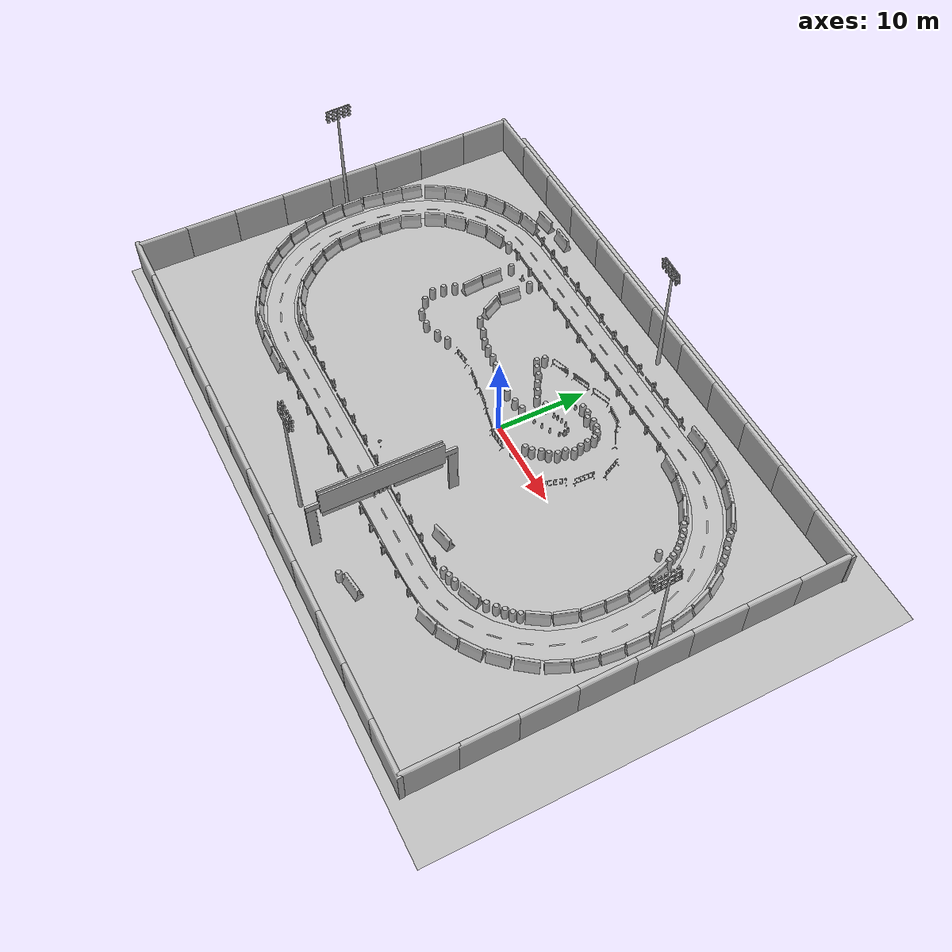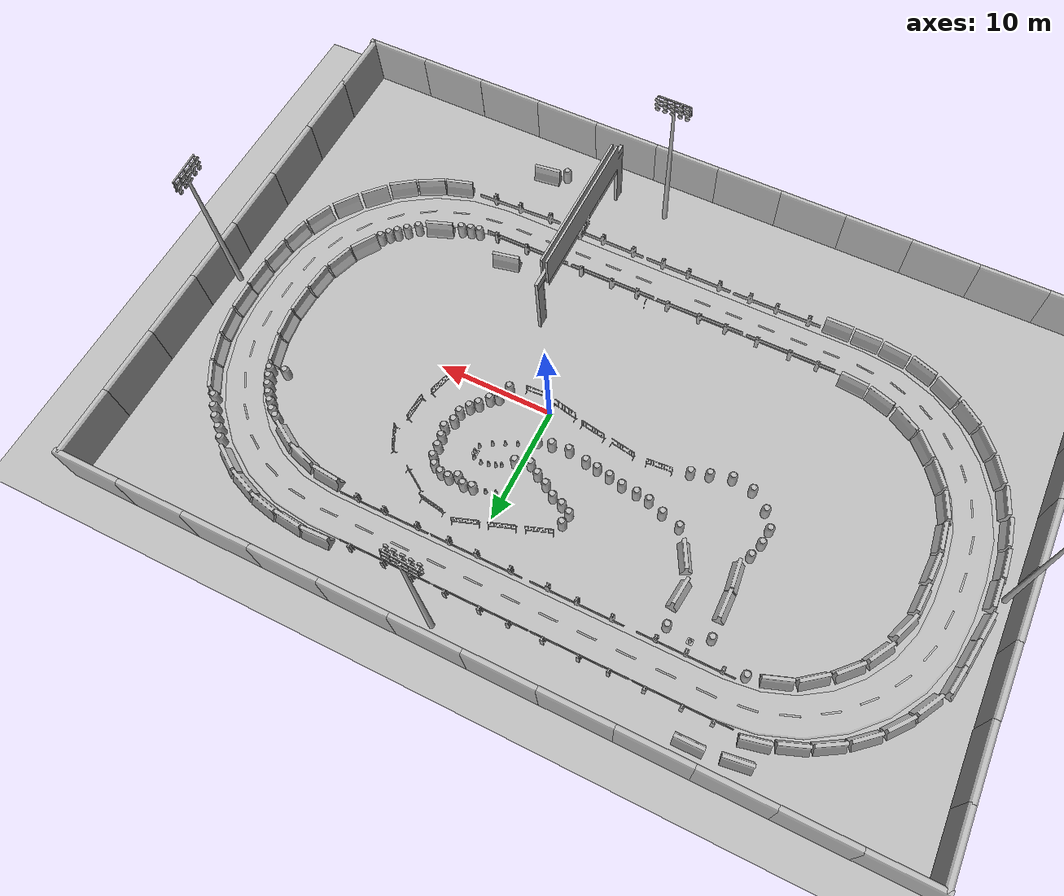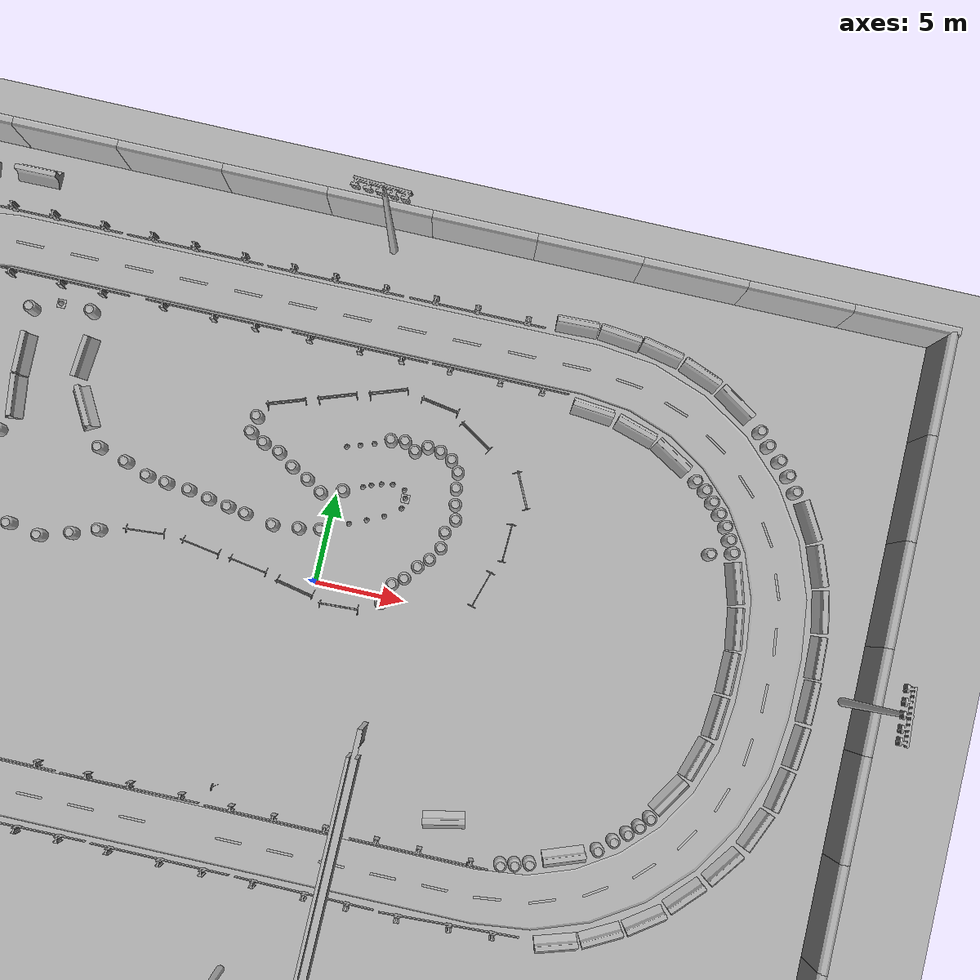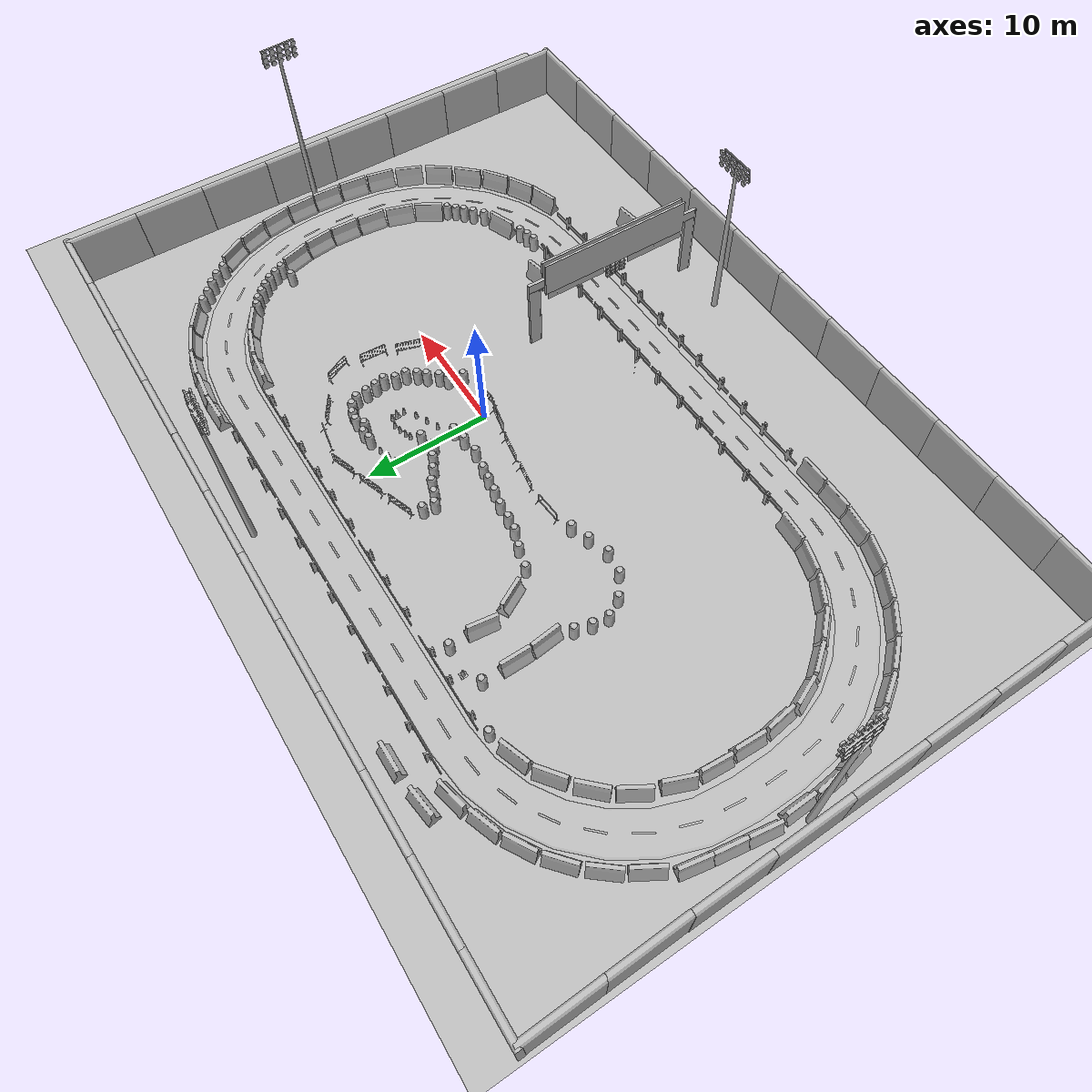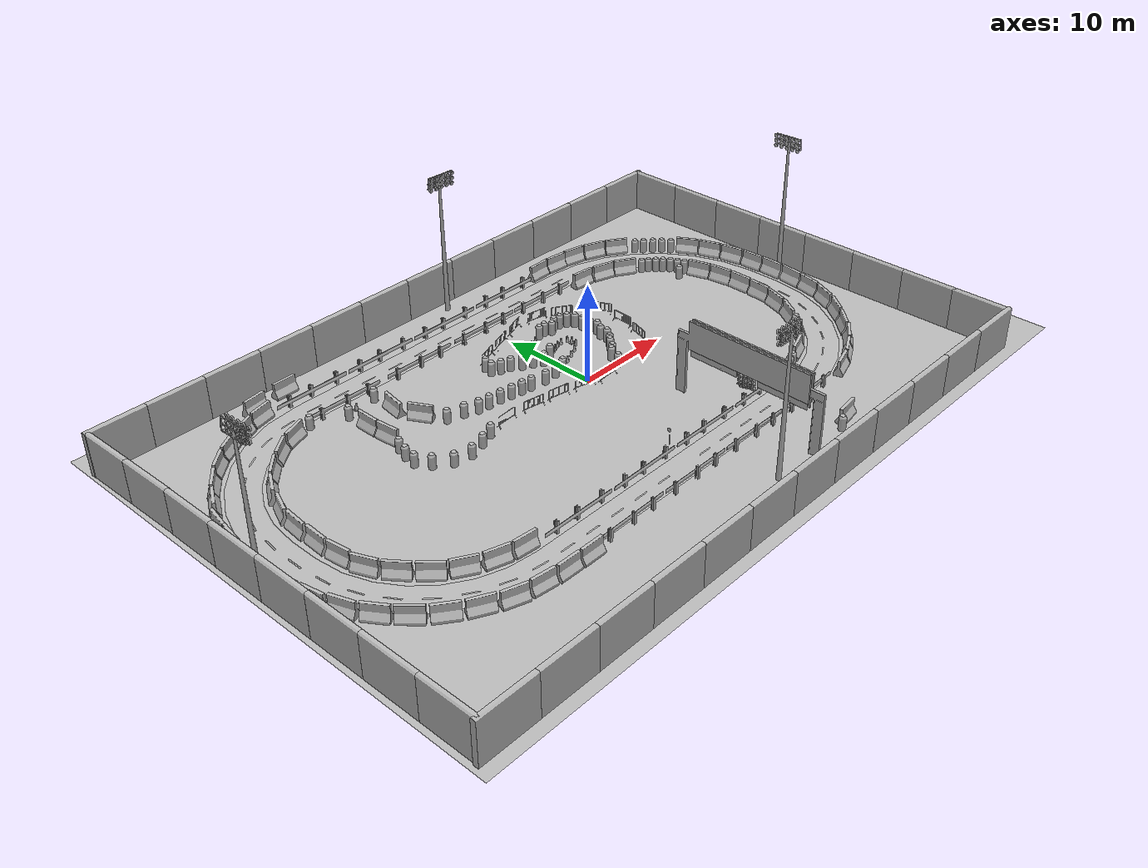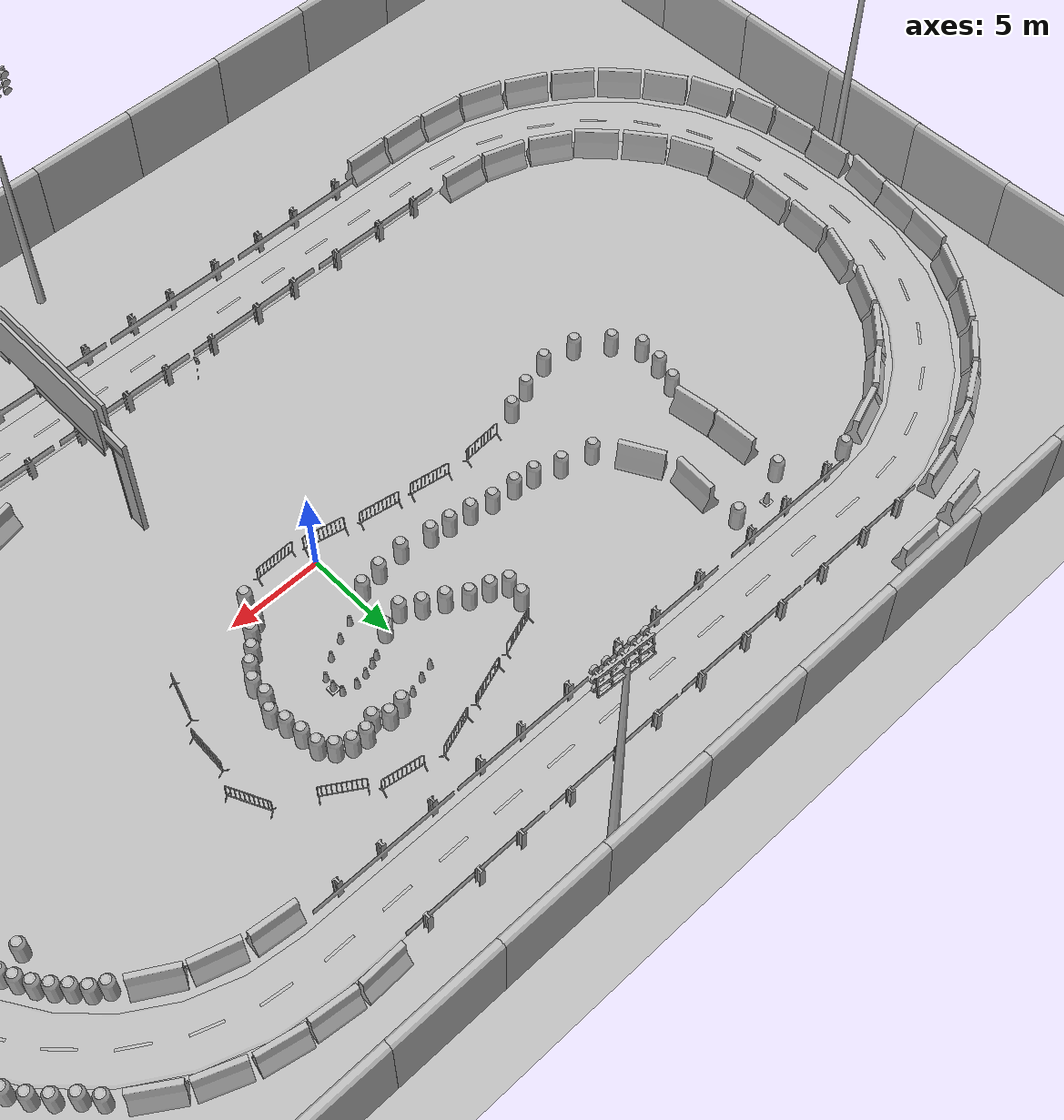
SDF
<sdf version="1.7">
 <world name="default">
  <gravity>0 0 -9.8</gravity>
  <magnetic_field>6e-06 2.3e-05 -4.2e-05</magnetic_field>
  <atmosphere type="adiabatic"/>
  <physics name="default_physics" default="0" type="ode">
   <max_step_size>0.001</max_step_size>
   <real_time_factor>1</real_time_factor>
   <real_time_update_rate>1000</real_time_update_rate>
  </physics>
  <scene><ambient>0.4 0.4 0.4 1</ambient><background>0.7 0.7 0.7 1</background><shadows>1</shadows></scene>
  <spherical_coordinates>
   <surface_model>EARTH_WGS84</surface_model>
   <latitude_deg>0</latitude_deg>
   <longitude_deg>0</longitude_deg>
   <elevation>0</elevation>
   <heading_deg>0</heading_deg>
  </spherical_coordinates>
  <model name="aws_robomaker_racetrack_Billboard_01">
   <frame name="aws_Billboard_01::__model__" attached_to="aws_Billboard_01::body">
    <pose relative_to="__model__">0 0 0 0 -0 0</pose>
   </frame>
   <link name="aws_Billboard_01::body">
    <pose relative_to="aws_Billboard_01::__model__">0 0 0 0 -0 0</pose>
    <inertial>
     <mass>1000</mass>
     <inertia><ixx>1</ixx><ixy>0</ixy><ixz>0</ixz><iyy>1</iyy><iyz>0</iyz><izz>1</izz></inertia>
    </inertial>
    <visual name="visual">
     <geometry>
      <mesh><uri>model://aws_robomaker_racetrack_Billboard_01/meshes/aws_Billboard_01_visual.DAE</uri></mesh>
     </geometry>
     <material><shader type="pixel"><normal_map>__default__</normal_map></shader></material>
     <meta><layer>2</layer></meta>
    </visual>
    <collision name="collision_0">
     <geometry>
      <mesh>
       <uri>model://aws_robomaker_racetrack_Billboard_01/meshes/aws_Billboard_01_collision.DAE</uri>
       <scale>1 1 1</scale>
      </mesh>
     </geometry>
     <surface>
      <friction>
       <ode><mu>1</mu><mu2>1</mu2><fdir1>0 0 0</fdir1><slip1>0</slip1><slip2>0</slip2></ode>
       <torsional>
        <coefficient>1</coefficient>
        <patch_radius>0</patch_radius>
        <surface_radius>0</surface_radius>
        <use_patch_radius>1</use_patch_radius>
        <ode><slip>0</slip></ode>
       </torsional>
      </friction>
      <bounce><restitution_coefficient>0</restitution_coefficient><threshold>1e+06</threshold></bounce>
      <contact>
       <collide_without_contact>0</collide_without_contact>
       <collide_without_contact_bitmask>1</collide_without_contact_bitmask>
       <collide_bitmask>1</collide_bitmask>
       <ode>
        <soft_cfm>0</soft_cfm>
        <soft_erp>0.2</soft_erp>
        <kp>1e+13</kp>
        <kd>1</kd>
        <max_vel>0.01</max_vel>
        <min_depth>0</min_depth>
       </ode>
       <bullet>
        <split_impulse>1</split_impulse>
        <split_impulse_penetration_threshold>-0.01</split_impulse_penetration_threshold>
        <soft_cfm>0</soft_cfm>
        <soft_erp>0.2</soft_erp>
        <kp>1e+13</kp>
        <kd>1</kd>
       </bullet>
      </contact>
     </surface>
    </collision>
   </link>
   <static>1</static>
   <pose>4.32789 -14.8431 -2e-06 0 1e-06 1.56416</pose>
  </model>
  <model name="aws_robomaker_racetrack_CrashworthBucket_01_00">
   <frame name="aws_CrashworthBucket_01::__model__" attached_to="aws_CrashworthBucket_01::body">
    <pose relative_to="__model__">0 0 0 0 -0 0</pose>
   </frame>
   <link name="aws_CrashworthBucket_01::body">
    <pose relative_to="aws_CrashworthBucket_01::__model__">0 0 0 0 -0 0</pose>
    <inertial>
     <mass>5</mass>
     <inertia><ixx>1</ixx><ixy>0</ixy><ixz>0</ixz><iyy>1</iyy><iyz>0</iyz><izz>1</izz></inertia>
    </inertial>
    <visual name="visual">
     <geometry>
      <mesh>
       <uri>model://aws_robomaker_racetrack_CrashworthBucket_01/meshes/aws_CrashworthBucket_01_visual.DAE</uri>
      </mesh>
     </geometry>
     <material><shader type="pixel"><normal_map>__default__</normal_map></shader></material>
     <meta><layer>0</layer></meta>
    </visual>
    <collision name="collision_0">
     <geometry>
      <mesh>
       <uri>model://aws_robomaker_racetrack_CrashworthBucket_01/meshes/aws_CrashworthBucket_01_collision.DAE</uri>
       <scale>1 1 1</scale>
      </mesh>
     </geometry>
     <surface>
      <friction>
       <ode><mu>1</mu><mu2>1</mu2><fdir1>0 0 0</fdir1><slip1>0</slip1><slip2>0</slip2></ode>
       <torsional>
        <coefficient>1</coefficient>
        <patch_radius>0</patch_radius>
        <surface_radius>0</surface_radius>
        <use_patch_radius>1</use_patch_radius>
        <ode><slip>0</slip></ode>
       </torsional>
      </friction>
      <bounce><restitution_coefficient>0</restitution_coefficient><threshold>1e+06</threshold></bounce>
      <contact>
       <collide_without_contact>0</collide_without_contact>
       <collide_without_contact_bitmask>1</collide_without_contact_bitmask>
       <collide_bitmask>1</collide_bitmask>
       <ode>
        <soft_cfm>0</soft_cfm>
        <soft_erp>0.2</soft_erp>
        <kp>1e+13</kp>
        <kd>1</kd>
        <max_vel>0.01</max_vel>
        <min_depth>0</min_depth>
       </ode>
       <bullet>
        <split_impulse>1</split_impulse>
        <split_impulse_penetration_threshold>-0.01</split_impulse_penetration_threshold>
        <soft_cfm>0</soft_cfm>
        <soft_erp>0.2</soft_erp>
        <kp>1e+13</kp>
        <kd>1</kd>
       </bullet>
      </contact>
     </surface>
    </collision>
   </link>
   <static>1</static>
   <pose>-1.69098 5.45143 0.054 0 -0 0</pose>
  </model>
  <model name="aws_robomaker_racetrack_CrashworthBucket_01_01">
   <frame name="aws_CrashworthBucket_01::__model__" attached_to="aws_CrashworthBucket_01::body">
    <pose relative_to="__model__">0 0 0 0 -0 0</pose>
   </frame>
   <link name="aws_CrashworthBucket_01::body">
    <pose relative_to="aws_CrashworthBucket_01::__model__">0 0 0 0 -0 0</pose>
    <inertial>
     <mass>5</mass>
     <inertia><ixx>1</ixx><ixy>0</ixy><ixz>0</ixz><iyy>1</iyy><iyz>0</iyz><izz>1</izz></inertia>
    </inertial>
    <visual name="visual">
     <geometry>
      <mesh>
       <uri>model://aws_robomaker_racetrack_CrashworthBucket_01/meshes/aws_CrashworthBucket_01_visual.DAE</uri>
      </mesh>
     </geometry>
     <material><shader type="pixel"><normal_map>__default__</normal_map></shader></material>
     <meta><layer>0</layer></meta>
    </visual>
    <collision name="collision_0">
     <geometry>
      <mesh>
       <uri>model://aws_robomaker_racetrack_CrashworthBucket_01/meshes/aws_CrashworthBucket_01_collision.DAE</uri>
       <scale>1 1 1</scale>
      </mesh>
     </geometry>
     <surface>
      <friction>
       <ode><mu>1</mu><mu2>1</mu2><fdir1>0 0 0</fdir1><slip1>0</slip1><slip2>0</slip2></ode>
       <torsional>
        <coefficient>1</coefficient>
        <patch_radius>0</patch_radius>
        <surface_radius>0</surface_radius>
        <use_patch_radius>1</use_patch_radius>
        <ode><slip>0</slip></ode>
       </torsional>
      </friction>
      <bounce><restitution_coefficient>0</restitution_coefficient><threshold>1e+06</threshold></bounce>
      <contact>
       <collide_without_contact>0</collide_without_contact>
       <collide_without_contact_bitmask>1</collide_without_contact_bitmask>
       <collide_bitmask>1</collide_bitmask>
       <ode>
        <soft_cfm>0</soft_cfm>
        <soft_erp>0.2</soft_erp>
        <kp>1e+13</kp>
        <kd>1</kd>
        <max_vel>0.01</max_vel>
        <min_depth>0</min_depth>
       </ode>
       <bullet>
        <split_impulse>1</split_impulse>
        <split_impulse_penetration_threshold>-0.01</split_impulse_penetration_threshold>
        <soft_cfm>0</soft_cfm>
        <soft_erp>0.2</soft_erp>
        <kp>1e+13</kp>
        <kd>1</kd>
       </bullet>
      </contact>
     </surface>
    </collision>
   </link>
   <static>1</static>
   <pose>-2.65666 5.94023 0.054 0 -0 0</pose>
  </model>
  <model name="aws_robomaker_racetrack_CrashworthBucket_01_02">
   <frame name="aws_CrashworthBucket_01::__model__" attached_to="aws_CrashworthBucket_01::body">
    <pose relative_to="__model__">0 0 0 0 -0 0</pose>
   </frame>
   <link name="aws_CrashworthBucket_01::body">
    <pose relative_to="aws_CrashworthBucket_01::__model__">0 0 0 0 -0 0</pose>
    <inertial>
     <mass>5</mass>
     <inertia><ixx>1</ixx><ixy>0</ixy><ixz>0</ixz><iyy>1</iyy><iyz>0</iyz><izz>1</izz></inertia>
    </inertial>
    <visual name="visual">
     <geometry>
      <mesh>
       <uri>model://aws_robomaker_racetrack_CrashworthBucket_01/meshes/aws_CrashworthBucket_01_visual.DAE</uri>
      </mesh>
     </geometry>
     <material><shader type="pixel"><normal_map>__default__</normal_map></shader></material>
     <meta><layer>0</layer></meta>
    </visual>
    <collision name="collision_0">
     <geometry>
      <mesh>
       <uri>model://aws_robomaker_racetrack_CrashworthBucket_01/meshes/aws_CrashworthBucket_01_collision.DAE</uri>
       <scale>1 1 1</scale>
      </mesh>
     </geometry>
     <surface>
      <friction>
       <ode><mu>1</mu><mu2>1</mu2><fdir1>0 0 0</fdir1><slip1>0</slip1><slip2>0</slip2></ode>
       <torsional>
        <coefficient>1</coefficient>
        <patch_radius>0</patch_radius>
        <surface_radius>0</surface_radius>
        <use_patch_radius>1</use_patch_radius>
        <ode><slip>0</slip></ode>
       </torsional>
      </friction>
      <bounce><restitution_coefficient>0</restitution_coefficient><threshold>1e+06</threshold></bounce>
      <contact>
       <collide_without_contact>0</collide_without_contact>
       <collide_without_contact_bitmask>1</collide_without_contact_bitmask>
       <collide_bitmask>1</collide_bitmask>
       <ode>
        <soft_cfm>0</soft_cfm>
        <soft_erp>0.2</soft_erp>
        <kp>1e+13</kp>
        <kd>1</kd>
        <max_vel>0.01</max_vel>
        <min_depth>0</min_depth>
       </ode>
       <bullet>
        <split_impulse>1</split_impulse>
        <split_impulse_penetration_threshold>-0.01</split_impulse_penetration_threshold>
        <soft_cfm>0</soft_cfm>
        <soft_erp>0.2</soft_erp>
        <kp>1e+13</kp>
        <kd>1</kd>
       </bullet>
      </contact>
     </surface>
    </collision>
   </link>
   <static>1</static>
   <pose>-6.79958 3.18138 0.054 0 -0 0</pose>
  </model>
  <model name="aws_robomaker_racetrack_CrashworthBucket_01_03">
   <frame name="aws_CrashworthBucket_01::__model__" attached_to="aws_CrashworthBucket_01::body">
    <pose relative_to="__model__">0 0 0 0 -0 0</pose>
   </frame>
   <link name="aws_CrashworthBucket_01::body">
    <pose relative_to="aws_CrashworthBucket_01::__model__">0 0 0 0 -0 0</pose>
    <inertial>
     <mass>5</mass>
     <inertia><ixx>1</ixx><ixy>0</ixy><ixz>0</ixz><iyy>1</iyy><iyz>0</iyz><izz>1</izz></inertia>
    </inertial>
    <visual name="visual">
     <geometry>
      <mesh>
       <uri>model://aws_robomaker_racetrack_CrashworthBucket_01/meshes/aws_CrashworthBucket_01_visual.DAE</uri>
      </mesh>
     </geometry>
     <material><shader type="pixel"><normal_map>__default__</normal_map></shader></material>
     <meta><layer>0</layer></meta>
    </visual>
    <collision name="collision_0">
     <geometry>
      <mesh>
       <uri>model://aws_robomaker_racetrack_CrashworthBucket_01/meshes/aws_CrashworthBucket_01_collision.DAE</uri>
       <scale>1 1 1</scale>
      </mesh>
     </geometry>
     <surface>
      <friction>
       <ode><mu>1</mu><mu2>1</mu2><fdir1>0 0 0</fdir1><slip1>0</slip1><slip2>0</slip2></ode>
       <torsional>
        <coefficient>1</coefficient>
        <patch_radius>0</patch_radius>
        <surface_radius>0</surface_radius>
        <use_patch_radius>1</use_patch_radius>
        <ode><slip>0</slip></ode>
       </torsional>
      </friction>
      <bounce><restitution_coefficient>0</restitution_coefficient><threshold>1e+06</threshold></bounce>
      <contact>
       <collide_without_contact>0</collide_without_contact>
       <collide_without_contact_bitmask>1</collide_without_contact_bitmask>
       <collide_bitmask>1</collide_bitmask>
       <ode>
        <soft_cfm>0</soft_cfm>
        <soft_erp>0.2</soft_erp>
        <kp>1e+13</kp>
        <kd>1</kd>
        <max_vel>0.01</max_vel>
        <min_depth>0</min_depth>
       </ode>
       <bullet>
        <split_impulse>1</split_impulse>
        <split_impulse_penetration_threshold>-0.01</split_impulse_penetration_threshold>
        <soft_cfm>0</soft_cfm>
        <soft_erp>0.2</soft_erp>
        <kp>1e+13</kp>
        <kd>1</kd>
       </bullet>
      </contact>
     </surface>
    </collision>
   </link>
   <static>1</static>
   <pose>-10.4129 3.68606 0.054 0 -0 0</pose>
  </model>
  <model name="aws_robomaker_racetrack_CrashworthBucket_01_04">
   <frame name="aws_CrashworthBucket_01::__model__" attached_to="aws_CrashworthBucket_01::body">
    <pose relative_to="__model__">0 0 0 0 -0 0</pose>
   </frame>
   <link name="aws_CrashworthBucket_01::body">
    <pose relative_to="aws_CrashworthBucket_01::__model__">0 0 0 0 -0 0</pose>
    <inertial>
     <mass>5</mass>
     <inertia><ixx>1</ixx><ixy>0</ixy><ixz>0</ixz><iyy>1</iyy><iyz>0</iyz><izz>1</izz></inertia>
    </inertial>
    <visual name="visual">
     <geometry>
      <mesh>
       <uri>model://aws_robomaker_racetrack_CrashworthBucket_01/meshes/aws_CrashworthBucket_01_visual.DAE</uri>
      </mesh>
     </geometry>
     <material><shader type="pixel"><normal_map>__default__</normal_map></shader></material>
     <meta><layer>0</layer></meta>
    </visual>
    <collision name="collision_0">
     <geometry>
      <mesh>
       <uri>model://aws_robomaker_racetrack_CrashworthBucket_01/meshes/aws_CrashworthBucket_01_collision.DAE</uri>
       <scale>1 1 1</scale>
      </mesh>
     </geometry>
     <surface>
      <friction>
       <ode><mu>1</mu><mu2>1</mu2><fdir1>0 0 0</fdir1><slip1>0</slip1><slip2>0</slip2></ode>
       <torsional>
        <coefficient>1</coefficient>
        <patch_radius>0</patch_radius>
        <surface_radius>0</surface_radius>
        <use_patch_radius>1</use_patch_radius>
        <ode><slip>0</slip></ode>
       </torsional>
      </friction>
      <bounce><restitution_coefficient>0</restitution_coefficient><threshold>1e+06</threshold></bounce>
      <contact>
       <collide_without_contact>0</collide_without_contact>
       <collide_without_contact_bitmask>1</collide_without_contact_bitmask>
       <collide_bitmask>1</collide_bitmask>
       <ode>
        <soft_cfm>0</soft_cfm>
        <soft_erp>0.2</soft_erp>
        <kp>1e+13</kp>
        <kd>1</kd>
        <max_vel>0.01</max_vel>
        <min_depth>0</min_depth>
       </ode>
       <bullet>
        <split_impulse>1</split_impulse>
        <split_impulse_penetration_threshold>-0.01</split_impulse_penetration_threshold>
        <soft_cfm>0</soft_cfm>
        <soft_erp>0.2</soft_erp>
        <kp>1e+13</kp>
        <kd>1</kd>
       </bullet>
      </contact>
     </surface>
    </collision>
   </link>
   <static>1</static>
   <pose>2.35672 8.58743 0.054 0 -0 0.094608</pose>
  </model>
  <model name="aws_robomaker_racetrack_CrashworthBucket_01_05">
   <frame name="aws_CrashworthBucket_01::__model__" attached_to="aws_CrashworthBucket_01::body">
    <pose relative_to="__model__">0 0 0 0 -0 0</pose>
   </frame>
   <link name="aws_CrashworthBucket_01::body">
    <pose relative_to="aws_CrashworthBucket_01::__model__">0 0 0 0 -0 0</pose>
    <inertial>
     <mass>5</mass>
     <inertia><ixx>1</ixx><ixy>0</ixy><ixz>0</ixz><iyy>1</iyy><iyz>0</iyz><izz>1</izz></inertia>
    </inertial>
    <visual name="visual">
     <geometry>
      <mesh>
       <uri>model://aws_robomaker_racetrack_CrashworthBucket_01/meshes/aws_CrashworthBucket_01_visual.DAE</uri>
      </mesh>
     </geometry>
     <material><shader type="pixel"><normal_map>__default__</normal_map></shader></material>
     <meta><layer>0</layer></meta>
    </visual>
    <collision name="collision_0">
     <geometry>
      <mesh>
       <uri>model://aws_robomaker_racetrack_CrashworthBucket_01/meshes/aws_CrashworthBucket_01_collision.DAE</uri>
       <scale>1 1 1</scale>
      </mesh>
     </geometry>
     <surface>
      <friction>
       <ode><mu>1</mu><mu2>1</mu2><fdir1>0 0 0</fdir1><slip1>0</slip1><slip2>0</slip2></ode>
       <torsional>
        <coefficient>1</coefficient>
        <patch_radius>0</patch_radius>
        <surface_radius>0</surface_radius>
        <use_patch_radius>1</use_patch_radius>
        <ode><slip>0</slip></ode>
       </torsional>
      </friction>
      <bounce><restitution_coefficient>0</restitution_coefficient><threshold>1e+06</threshold></bounce>
      <contact>
       <collide_without_contact>0</collide_without_contact>
       <collide_without_contact_bitmask>1</collide_without_contact_bitmask>
       <collide_bitmask>1</collide_bitmask>
       <ode>
        <soft_cfm>0</soft_cfm>
        <soft_erp>0.2</soft_erp>
        <kp>1e+13</kp>
        <kd>1</kd>
        <max_vel>0.01</max_vel>
        <min_depth>0</min_depth>
       </ode>
       <bullet>
        <split_impulse>1</split_impulse>
        <split_impulse_penetration_threshold>-0.01</split_impulse_penetration_threshold>
        <soft_cfm>0</soft_cfm>
        <soft_erp>0.2</soft_erp>
        <kp>1e+13</kp>
        <kd>1</kd>
       </bullet>
      </contact>
     </surface>
    </collision>
   </link>
   <static>1</static>
   <pose>3.14399 8.69292 0 0 -0 0.292667</pose>
  </model>
  <model name="aws_robomaker_racetrack_CrashworthBucket_01_06">
   <frame name="aws_CrashworthBucket_01::__model__" attached_to="aws_CrashworthBucket_01::body">
    <pose relative_to="__model__">0 0 0 0 -0 0</pose>
   </frame>
   <link name="aws_CrashworthBucket_01::body">
    <pose relative_to="aws_CrashworthBucket_01::__model__">0 0 0 0 -0 0</pose>
    <inertial>
     <mass>5</mass>
     <inertia><ixx>1</ixx><ixy>0</ixy><ixz>0</ixz><iyy>1</iyy><iyz>0</iyz><izz>1</izz></inertia>
    </inertial>
    <visual name="visual">
     <geometry>
      <mesh>
       <uri>model://aws_robomaker_racetrack_CrashworthBucket_01/meshes/aws_CrashworthBucket_01_visual.DAE</uri>
      </mesh>
     </geometry>
     <material><shader type="pixel"><normal_map>__default__</normal_map></shader></material>
     <meta><layer>0</layer></meta>
    </visual>
    <collision name="collision_0">
     <geometry>
      <mesh>
       <uri>model://aws_robomaker_racetrack_CrashworthBucket_01/meshes/aws_CrashworthBucket_01_collision.DAE</uri>
       <scale>1 1 1</scale>
      </mesh>
     </geometry>
     <surface>
      <friction>
       <ode><mu>1</mu><mu2>1</mu2><fdir1>0 0 0</fdir1><slip1>0</slip1><slip2>0</slip2></ode>
       <torsional>
        <coefficient>1</coefficient>
        <patch_radius>0</patch_radius>
        <surface_radius>0</surface_radius>
        <use_patch_radius>1</use_patch_radius>
        <ode><slip>0</slip></ode>
       </torsional>
      </friction>
      <bounce><restitution_coefficient>0</restitution_coefficient><threshold>1e+06</threshold></bounce>
      <contact>
       <collide_without_contact>0</collide_without_contact>
       <collide_without_contact_bitmask>1</collide_without_contact_bitmask>
       <collide_bitmask>1</collide_bitmask>
       <ode>
        <soft_cfm>0</soft_cfm>
        <soft_erp>0.2</soft_erp>
        <kp>1e+13</kp>
        <kd>1</kd>
        <max_vel>0.01</max_vel>
        <min_depth>0</min_depth>
       </ode>
       <bullet>
        <split_impulse>1</split_impulse>
        <split_impulse_penetration_threshold>-0.01</split_impulse_penetration_threshold>
        <soft_cfm>0</soft_cfm>
        <soft_erp>0.2</soft_erp>
        <kp>1e+13</kp>
        <kd>1</kd>
       </bullet>
      </contact>
     </surface>
    </collision>
   </link>
   <static>1</static>
   <pose>5.18867 8.56895 0 0 0 -0.026658</pose>
  </model>
  <model name="aws_robomaker_racetrack_CrashworthBucket_01_07">
   <frame name="aws_CrashworthBucket_01::__model__" attached_to="aws_CrashworthBucket_01::body">
    <pose relative_to="__model__">0 0 0 0 -0 0</pose>
   </frame>
   <link name="aws_CrashworthBucket_01::body">
    <pose relative_to="aws_CrashworthBucket_01::__model__">0 0 0 0 -0 0</pose>
    <inertial>
     <mass>5</mass>
     <inertia><ixx>1</ixx><ixy>0</ixy><ixz>0</ixz><iyy>1</iyy><iyz>0</iyz><izz>1</izz></inertia>
    </inertial>
    <visual name="visual">
     <geometry>
      <mesh>
       <uri>model://aws_robomaker_racetrack_CrashworthBucket_01/meshes/aws_CrashworthBucket_01_visual.DAE</uri>
      </mesh>
     </geometry>
     <material><shader type="pixel"><normal_map>__default__</normal_map></shader></material>
     <meta><layer>0</layer></meta>
    </visual>
    <collision name="collision_0">
     <geometry>
      <mesh>
       <uri>model://aws_robomaker_racetrack_CrashworthBucket_01/meshes/aws_CrashworthBucket_01_collision.DAE</uri>
       <scale>1 1 1</scale>
      </mesh>
     </geometry>
     <surface>
      <friction>
       <ode><mu>1</mu><mu2>1</mu2><fdir1>0 0 0</fdir1><slip1>0</slip1><slip2>0</slip2></ode>
       <torsional>
        <coefficient>1</coefficient>
        <patch_radius>0</patch_radius>
        <surface_radius>0</surface_radius>
        <use_patch_radius>1</use_patch_radius>
        <ode><slip>0</slip></ode>
       </torsional>
      </friction>
      <bounce><restitution_coefficient>0</restitution_coefficient><threshold>1e+06</threshold></bounce>
      <contact>
       <collide_without_contact>0</collide_without_contact>
       <collide_without_contact_bitmask>1</collide_without_contact_bitmask>
       <collide_bitmask>1</collide_bitmask>
       <ode>
        <soft_cfm>0</soft_cfm>
        <soft_erp>0.2</soft_erp>
        <kp>1e+13</kp>
        <kd>1</kd>
        <max_vel>0.01</max_vel>
        <min_depth>0</min_depth>
       </ode>
       <bullet>
        <split_impulse>1</split_impulse>
        <split_impulse_penetration_threshold>-0.01</split_impulse_penetration_threshold>
        <soft_cfm>0</soft_cfm>
        <soft_erp>0.2</soft_erp>
        <kp>1e+13</kp>
        <kd>1</kd>
       </bullet>
      </contact>
     </surface>
    </collision>
   </link>
   <static>1</static>
   <pose>5.89383 8.24239 0.054 0 -0 0</pose>
  </model>
  <model name="aws_robomaker_racetrack_CrashworthBucket_01_08">
   <frame name="aws_CrashworthBucket_01::__model__" attached_to="aws_CrashworthBucket_01::body">
    <pose relative_to="__model__">0 0 0 0 -0 0</pose>
   </frame>
   <link name="aws_CrashworthBucket_01::body">
    <pose relative_to="aws_CrashworthBucket_01::__model__">0 0 0 0 -0 0</pose>
    <inertial>
     <mass>5</mass>
     <inertia><ixx>1</ixx><ixy>0</ixy><ixz>0</ixz><iyy>1</iyy><iyz>0</iyz><izz>1</izz></inertia>
    </inertial>
    <visual name="visual">
     <geometry>
      <mesh>
       <uri>model://aws_robomaker_racetrack_CrashworthBucket_01/meshes/aws_CrashworthBucket_01_visual.DAE</uri>
      </mesh>
     </geometry>
     <material><shader type="pixel"><normal_map>__default__</normal_map></shader></material>
     <meta><layer>0</layer></meta>
    </visual>
    <collision name="collision_0">
     <geometry>
      <mesh>
       <uri>model://aws_robomaker_racetrack_CrashworthBucket_01/meshes/aws_CrashworthBucket_01_collision.DAE</uri>
       <scale>1 1 1</scale>
      </mesh>
     </geometry>
     <surface>
      <friction>
       <ode><mu>1</mu><mu2>1</mu2><fdir1>0 0 0</fdir1><slip1>0</slip1><slip2>0</slip2></ode>
       <torsional>
        <coefficient>1</coefficient>
        <patch_radius>0</patch_radius>
        <surface_radius>0</surface_radius>
        <use_patch_radius>1</use_patch_radius>
        <ode><slip>0</slip></ode>
       </torsional>
      </friction>
      <bounce><restitution_coefficient>0</restitution_coefficient><threshold>1e+06</threshold></bounce>
      <contact>
       <collide_without_contact>0</collide_without_contact>
       <collide_without_contact_bitmask>1</collide_without_contact_bitmask>
       <collide_bitmask>1</collide_bitmask>
       <ode>
        <soft_cfm>0</soft_cfm>
        <soft_erp>0.2</soft_erp>
        <kp>1e+13</kp>
        <kd>1</kd>
        <max_vel>0.01</max_vel>
        <min_depth>0</min_depth>
       </ode>
       <bullet>
        <split_impulse>1</split_impulse>
        <split_impulse_penetration_threshold>-0.01</split_impulse_penetration_threshold>
        <soft_cfm>0</soft_cfm>
        <soft_erp>0.2</soft_erp>
        <kp>1e+13</kp>
        <kd>1</kd>
       </bullet>
      </contact>
     </surface>
    </collision>
   </link>
   <static>1</static>
   <pose>-19.5181 3.15886 0.050064 0 -0 0</pose>
  </model>
  <model name="aws_robomaker_racetrack_CrashworthBucket_01_09">
   <frame name="aws_CrashworthBucket_01::__model__" attached_to="aws_CrashworthBucket_01::body">
    <pose relative_to="__model__">0 0 0 0 -0 0</pose>
   </frame>
   <link name="aws_CrashworthBucket_01::body">
    <pose relative_to="aws_CrashworthBucket_01::__model__">0 0 0 0 -0 0</pose>
    <inertial>
     <mass>5</mass>
     <inertia><ixx>1</ixx><ixy>0</ixy><ixz>0</ixz><iyy>1</iyy><iyz>0</iyz><izz>1</izz></inertia>
    </inertial>
    <visual name="visual">
     <geometry>
      <mesh>
       <uri>model://aws_robomaker_racetrack_CrashworthBucket_01/meshes/aws_CrashworthBucket_01_visual.DAE</uri>
      </mesh>
     </geometry>
     <material><shader type="pixel"><normal_map>__default__</normal_map></shader></material>
     <meta><layer>0</layer></meta>
    </visual>
    <collision name="collision_0">
     <geometry>
      <mesh>
       <uri>model://aws_robomaker_racetrack_CrashworthBucket_01/meshes/aws_CrashworthBucket_01_collision.DAE</uri>
       <scale>1 1 1</scale>
      </mesh>
     </geometry>
     <surface>
      <friction>
       <ode><mu>1</mu><mu2>1</mu2><fdir1>0 0 0</fdir1><slip1>0</slip1><slip2>0</slip2></ode>
       <torsional>
        <coefficient>1</coefficient>
        <patch_radius>0</patch_radius>
        <surface_radius>0</surface_radius>
        <use_patch_radius>1</use_patch_radius>
        <ode><slip>0</slip></ode>
       </torsional>
      </friction>
      <bounce><restitution_coefficient>0</restitution_coefficient><threshold>1e+06</threshold></bounce>
      <contact>
       <collide_without_contact>0</collide_without_contact>
       <collide_without_contact_bitmask>1</collide_without_contact_bitmask>
       <collide_bitmask>1</collide_bitmask>
       <ode>
        <soft_cfm>0</soft_cfm>
        <soft_erp>0.2</soft_erp>
        <kp>1e+13</kp>
        <kd>1</kd>
        <max_vel>0.01</max_vel>
        <min_depth>0</min_depth>
       </ode>
       <bullet>
        <split_impulse>1</split_impulse>
        <split_impulse_penetration_threshold>-0.01</split_impulse_penetration_threshold>
        <soft_cfm>0</soft_cfm>
        <soft_erp>0.2</soft_erp>
        <kp>1e+13</kp>
        <kd>1</kd>
       </bullet>
      </contact>
     </surface>
    </collision>
   </link>
   <static>1</static>
   <pose>-19.6496 1.88456 0.054 0 -0 0</pose>
  </model>
  <model name="aws_robomaker_racetrack_CrashworthBucket_01_10">
   <frame name="aws_CrashworthBucket_01::__model__" attached_to="aws_CrashworthBucket_01::body">
    <pose relative_to="__model__">0 0 0 0 -0 0</pose>
   </frame>
   <link name="aws_CrashworthBucket_01::body">
    <pose relative_to="aws_CrashworthBucket_01::__model__">0 0 0 0 -0 0</pose>
    <inertial>
     <mass>5</mass>
     <inertia><ixx>1</ixx><ixy>0</ixy><ixz>0</ixz><iyy>1</iyy><iyz>0</iyz><izz>1</izz></inertia>
    </inertial>
    <visual name="visual">
     <geometry>
      <mesh>
       <uri>model://aws_robomaker_racetrack_CrashworthBucket_01/meshes/aws_CrashworthBucket_01_visual.DAE</uri>
      </mesh>
     </geometry>
     <material><shader type="pixel"><normal_map>__default__</normal_map></shader></material>
     <meta><layer>0</layer></meta>
    </visual>
    <collision name="collision_0">
     <geometry>
      <mesh>
       <uri>model://aws_robomaker_racetrack_CrashworthBucket_01/meshes/aws_CrashworthBucket_01_collision.DAE</uri>
       <scale>1 1 1</scale>
      </mesh>
     </geometry>
     <surface>
      <friction>
       <ode><mu>1</mu><mu2>1</mu2><fdir1>0 0 0</fdir1><slip1>0</slip1><slip2>0</slip2></ode>
       <torsional>
        <coefficient>1</coefficient>
        <patch_radius>0</patch_radius>
        <surface_radius>0</surface_radius>
        <use_patch_radius>1</use_patch_radius>
        <ode><slip>0</slip></ode>
       </torsional>
      </friction>
      <bounce><restitution_coefficient>0</restitution_coefficient><threshold>1e+06</threshold></bounce>
      <contact>
       <collide_without_contact>0</collide_without_contact>
       <collide_without_contact_bitmask>1</collide_without_contact_bitmask>
       <collide_bitmask>1</collide_bitmask>
       <ode>
        <soft_cfm>0</soft_cfm>
        <soft_erp>0.2</soft_erp>
        <kp>1e+13</kp>
        <kd>1</kd>
        <max_vel>0.01</max_vel>
        <min_depth>0</min_depth>
       </ode>
       <bullet>
        <split_impulse>1</split_impulse>
        <split_impulse_penetration_threshold>-0.01</split_impulse_penetration_threshold>
        <soft_cfm>0</soft_cfm>
        <soft_erp>0.2</soft_erp>
        <kp>1e+13</kp>
        <kd>1</kd>
       </bullet>
      </contact>
     </surface>
    </collision>
   </link>
   <static>1</static>
   <pose>22.2917 13.5697 0 0 -0 0</pose>
  </model>
  <model name="aws_robomaker_racetrack_CrashworthBucket_01_11">
   <frame name="aws_CrashworthBucket_01::__model__" attached_to="aws_CrashworthBucket_01::body">
    <pose relative_to="__model__">0 0 0 0 -0 0</pose>
   </frame>
   <link name="aws_CrashworthBucket_01::body">
    <pose relative_to="aws_CrashworthBucket_01::__model__">0 0 0 0 -0 0</pose>
    <inertial>
     <mass>5</mass>
     <inertia><ixx>1</ixx><ixy>0</ixy><ixz>0</ixz><iyy>1</iyy><iyz>0</iyz><izz>1</izz></inertia>
    </inertial>
    <visual name="visual">
     <geometry>
      <mesh>
       <uri>model://aws_robomaker_racetrack_CrashworthBucket_01/meshes/aws_CrashworthBucket_01_visual.DAE</uri>
      </mesh>
     </geometry>
     <material><shader type="pixel"><normal_map>__default__</normal_map></shader></material>
     <meta><layer>0</layer></meta>
    </visual>
    <collision name="collision_0">
     <geometry>
      <mesh>
       <uri>model://aws_robomaker_racetrack_CrashworthBucket_01/meshes/aws_CrashworthBucket_01_collision.DAE</uri>
       <scale>1 1 1</scale>
      </mesh>
     </geometry>
     <surface>
      <friction>
       <ode><mu>1</mu><mu2>1</mu2><fdir1>0 0 0</fdir1><slip1>0</slip1><slip2>0</slip2></ode>
       <torsional>
        <coefficient>1</coefficient>
        <patch_radius>0</patch_radius>
        <surface_radius>0</surface_radius>
        <use_patch_radius>1</use_patch_radius>
        <ode><slip>0</slip></ode>
       </torsional>
      </friction>
      <bounce><restitution_coefficient>0</restitution_coefficient><threshold>1e+06</threshold></bounce>
      <contact>
       <collide_without_contact>0</collide_without_contact>
       <collide_without_contact_bitmask>1</collide_without_contact_bitmask>
       <collide_bitmask>1</collide_bitmask>
       <ode>
        <soft_cfm>0</soft_cfm>
        <soft_erp>0.2</soft_erp>
        <kp>1e+13</kp>
        <kd>1</kd>
        <max_vel>0.01</max_vel>
        <min_depth>0</min_depth>
       </ode>
       <bullet>
        <split_impulse>1</split_impulse>
        <split_impulse_penetration_threshold>-0.01</split_impulse_penetration_threshold>
        <soft_cfm>0</soft_cfm>
        <soft_erp>0.2</soft_erp>
        <kp>1e+13</kp>
        <kd>1</kd>
       </bullet>
      </contact>
     </surface>
    </collision>
   </link>
   <static>1</static>
   <pose>22.9018 12.8693 0.054 0 -0 0</pose>
  </model>
  <model name="aws_robomaker_racetrack_CrashworthBucket_01_12">
   <frame name="aws_CrashworthBucket_01::__model__" attached_to="aws_CrashworthBucket_01::body">
    <pose relative_to="__model__">0 0 0 0 -0 0</pose>
   </frame>
   <link name="aws_CrashworthBucket_01::body">
    <pose relative_to="aws_CrashworthBucket_01::__model__">0 0 0 0 -0 0</pose>
    <inertial>
     <mass>5</mass>
     <inertia><ixx>1</ixx><ixy>0</ixy><ixz>0</ixz><iyy>1</iyy><iyz>0</iyz><izz>1</izz></inertia>
    </inertial>
    <visual name="visual">
     <geometry>
      <mesh>
       <uri>model://aws_robomaker_racetrack_CrashworthBucket_01/meshes/aws_CrashworthBucket_01_visual.DAE</uri>
      </mesh>
     </geometry>
     <material><shader type="pixel"><normal_map>__default__</normal_map></shader></material>
     <meta><layer>0</layer></meta>
    </visual>
    <collision name="collision_0">
     <geometry>
      <mesh>
       <uri>model://aws_robomaker_racetrack_CrashworthBucket_01/meshes/aws_CrashworthBucket_01_collision.DAE</uri>
       <scale>1 1 1</scale>
      </mesh>
     </geometry>
     <surface>
      <friction>
       <ode><mu>1</mu><mu2>1</mu2><fdir1>0 0 0</fdir1><slip1>0</slip1><slip2>0</slip2></ode>
       <torsional>
        <coefficient>1</coefficient>
        <patch_radius>0</patch_radius>
        <surface_radius>0</surface_radius>
        <use_patch_radius>1</use_patch_radius>
        <ode><slip>0</slip></ode>
       </torsional>
      </friction>
      <bounce><restitution_coefficient>0</restitution_coefficient><threshold>1e+06</threshold></bounce>
      <contact>
       <collide_without_contact>0</collide_without_contact>
       <collide_without_contact_bitmask>1</collide_without_contact_bitmask>
       <collide_bitmask>1</collide_bitmask>
       <ode>
        <soft_cfm>0</soft_cfm>
        <soft_erp>0.2</soft_erp>
        <kp>1e+13</kp>
        <kd>1</kd>
        <max_vel>0.01</max_vel>
        <min_depth>0</min_depth>
       </ode>
       <bullet>
        <split_impulse>1</split_impulse>
        <split_impulse_penetration_threshold>-0.01</split_impulse_penetration_threshold>
        <soft_cfm>0</soft_cfm>
        <soft_erp>0.2</soft_erp>
        <kp>1e+13</kp>
        <kd>1</kd>
       </bullet>
      </contact>
     </surface>
    </collision>
   </link>
   <static>1</static>
   <pose>22.2128 6.62693 0.054 0 -0 0</pose>
  </model>
  <model name="aws_robomaker_racetrack_CrashworthBucket_01_13">
   <frame name="aws_CrashworthBucket_01::__model__" attached_to="aws_CrashworthBucket_01::body">
    <pose relative_to="__model__">0 0 0 0 -0 0</pose>
   </frame>
   <link name="aws_CrashworthBucket_01::body">
    <pose relative_to="aws_CrashworthBucket_01::__model__">0 0 0 0 -0 0</pose>
    <inertial>
     <mass>5</mass>
     <inertia><ixx>1</ixx><ixy>0</ixy><ixz>0</ixz><iyy>1</iyy><iyz>0</iyz><izz>1</izz></inertia>
    </inertial>
    <visual name="visual">
     <geometry>
      <mesh>
       <uri>model://aws_robomaker_racetrack_CrashworthBucket_01/meshes/aws_CrashworthBucket_01_visual.DAE</uri>
      </mesh>
     </geometry>
     <material><shader type="pixel"><normal_map>__default__</normal_map></shader></material>
     <meta><layer>0</layer></meta>
    </visual>
    <collision name="collision_0">
     <geometry>
      <mesh>
       <uri>model://aws_robomaker_racetrack_CrashworthBucket_01/meshes/aws_CrashworthBucket_01_collision.DAE</uri>
       <scale>1 1 1</scale>
      </mesh>
     </geometry>
     <surface>
      <friction>
       <ode><mu>1</mu><mu2>1</mu2><fdir1>0 0 0</fdir1><slip1>0</slip1><slip2>0</slip2></ode>
       <torsional>
        <coefficient>1</coefficient>
        <patch_radius>0</patch_radius>
        <surface_radius>0</surface_radius>
        <use_patch_radius>1</use_patch_radius>
        <ode><slip>0</slip></ode>
       </torsional>
      </friction>
      <bounce><restitution_coefficient>0</restitution_coefficient><threshold>1e+06</threshold></bounce>
      <contact>
       <collide_without_contact>0</collide_without_contact>
       <collide_without_contact_bitmask>1</collide_without_contact_bitmask>
       <collide_bitmask>1</collide_bitmask>
       <ode>
        <soft_cfm>0</soft_cfm>
        <soft_erp>0.2</soft_erp>
        <kp>1e+13</kp>
        <kd>1</kd>
        <max_vel>0.01</max_vel>
        <min_depth>0</min_depth>
       </ode>
       <bullet>
        <split_impulse>1</split_impulse>
        <split_impulse_penetration_threshold>-0.01</split_impulse_penetration_threshold>
        <soft_cfm>0</soft_cfm>
        <soft_erp>0.2</soft_erp>
        <kp>1e+13</kp>
        <kd>1</kd>
       </bullet>
      </contact>
     </surface>
    </collision>
   </link>
   <static>1</static>
   <pose>20.9847 6.29253 0 0 -0 0</pose>
  </model>
  <model name="aws_robomaker_racetrack_CrashworthBucket_01_14">
   <frame name="aws_CrashworthBucket_01::__model__" attached_to="aws_CrashworthBucket_01::body">
    <pose relative_to="__model__">0 0 0 0 -0 0</pose>
   </frame>
   <link name="aws_CrashworthBucket_01::body">
    <pose relative_to="aws_CrashworthBucket_01::__model__">0 0 0 0 -0 0</pose>
    <inertial>
     <mass>5</mass>
     <inertia><ixx>1</ixx><ixy>0</ixy><ixz>0</ixz><iyy>1</iyy><iyz>0</iyz><izz>1</izz></inertia>
    </inertial>
    <visual name="visual">
     <geometry>
      <mesh>
       <uri>model://aws_robomaker_racetrack_CrashworthBucket_01/meshes/aws_CrashworthBucket_01_visual.DAE</uri>
      </mesh>
     </geometry>
     <material><shader type="pixel"><normal_map>__default__</normal_map></shader></material>
     <meta><layer>0</layer></meta>
    </visual>
    <collision name="collision_0">
     <geometry>
      <mesh>
       <uri>model://aws_robomaker_racetrack_CrashworthBucket_01/meshes/aws_CrashworthBucket_01_collision.DAE</uri>
       <scale>1 1 1</scale>
      </mesh>
     </geometry>
     <surface>
      <friction>
       <ode><mu>1</mu><mu2>1</mu2><fdir1>0 0 0</fdir1><slip1>0</slip1><slip2>0</slip2></ode>
       <torsional>
        <coefficient>1</coefficient>
        <patch_radius>0</patch_radius>
        <surface_radius>0</surface_radius>
        <use_patch_radius>1</use_patch_radius>
        <ode><slip>0</slip></ode>
       </torsional>
      </friction>
      <bounce><restitution_coefficient>0</restitution_coefficient><threshold>1e+06</threshold></bounce>
      <contact>
       <collide_without_contact>0</collide_without_contact>
       <collide_without_contact_bitmask>1</collide_without_contact_bitmask>
       <collide_bitmask>1</collide_bitmask>
       <ode>
        <soft_cfm>0</soft_cfm>
        <soft_erp>0.2</soft_erp>
        <kp>1e+13</kp>
        <kd>1</kd>
        <max_vel>0.01</max_vel>
        <min_depth>0</min_depth>
       </ode>
       <bullet>
        <split_impulse>1</split_impulse>
        <split_impulse_penetration_threshold>-0.01</split_impulse_penetration_threshold>
        <soft_cfm>0</soft_cfm>
        <soft_erp>0.2</soft_erp>
        <kp>1e+13</kp>
        <kd>1</kd>
       </bullet>
      </contact>
     </surface>
    </collision>
   </link>
   <static>1</static>
   <pose>-19.1324 4.40627 0.054 0 -0 0</pose>
  </model>
  <model name="aws_robomaker_racetrack_CrashworthBucket_01_15">
   <frame name="aws_CrashworthBucket_01::__model__" attached_to="aws_CrashworthBucket_01::body">
    <pose relative_to="__model__">0 0 0 0 -0 0</pose>
   </frame>
   <link name="aws_CrashworthBucket_01::body">
    <pose relative_to="aws_CrashworthBucket_01::__model__">0 0 0 0 -0 0</pose>
    <inertial>
     <mass>5</mass>
     <inertia><ixx>1</ixx><ixy>0</ixy><ixz>0</ixz><iyy>1</iyy><iyz>0</iyz><izz>1</izz></inertia>
    </inertial>
    <visual name="visual">
     <geometry>
      <mesh>
       <uri>model://aws_robomaker_racetrack_CrashworthBucket_01/meshes/aws_CrashworthBucket_01_visual.DAE</uri>
      </mesh>
     </geometry>
     <material><shader type="pixel"><normal_map>__default__</normal_map></shader></material>
     <meta><layer>0</layer></meta>
    </visual>
    <collision name="collision_0">
     <geometry>
      <mesh>
       <uri>model://aws_robomaker_racetrack_CrashworthBucket_01/meshes/aws_CrashworthBucket_01_collision.DAE</uri>
       <scale>1 1 1</scale>
      </mesh>
     </geometry>
     <surface>
      <friction>
       <ode><mu>1</mu><mu2>1</mu2><fdir1>0 0 0</fdir1><slip1>0</slip1><slip2>0</slip2></ode>
       <torsional>
        <coefficient>1</coefficient>
        <patch_radius>0</patch_radius>
        <surface_radius>0</surface_radius>
        <use_patch_radius>1</use_patch_radius>
        <ode><slip>0</slip></ode>
       </torsional>
      </friction>
      <bounce><restitution_coefficient>0</restitution_coefficient><threshold>1e+06</threshold></bounce>
      <contact>
       <collide_without_contact>0</collide_without_contact>
       <collide_without_contact_bitmask>1</collide_without_contact_bitmask>
       <collide_bitmask>1</collide_bitmask>
       <ode>
        <soft_cfm>0</soft_cfm>
        <soft_erp>0.2</soft_erp>
        <kp>1e+13</kp>
        <kd>1</kd>
        <max_vel>0.01</max_vel>
        <min_depth>0</min_depth>
       </ode>
       <bullet>
        <split_impulse>1</split_impulse>
        <split_impulse_penetration_threshold>-0.01</split_impulse_penetration_threshold>
        <soft_cfm>0</soft_cfm>
        <soft_erp>0.2</soft_erp>
        <kp>1e+13</kp>
        <kd>1</kd>
       </bullet>
      </contact>
     </surface>
    </collision>
   </link>
   <static>1</static>
   <pose>20.8422 -8.59507 0.054 0 -0 0.012499</pose>
  </model>
  <model name="aws_robomaker_racetrack_CrashworthBucket_01_16">
   <frame name="aws_CrashworthBucket_01::__model__" attached_to="aws_CrashworthBucket_01::body">
    <pose relative_to="__model__">0 0 0 0 -0 0</pose>
   </frame>
   <link name="aws_CrashworthBucket_01::body">
    <pose relative_to="aws_CrashworthBucket_01::__model__">0 0 0 0 -0 0</pose>
    <inertial>
     <mass>5</mass>
     <inertia><ixx>1</ixx><ixy>0</ixy><ixz>0</ixz><iyy>1</iyy><iyz>0</iyz><izz>1</izz></inertia>
    </inertial>
    <visual name="visual">
     <geometry>
      <mesh>
       <uri>model://aws_robomaker_racetrack_CrashworthBucket_01/meshes/aws_CrashworthBucket_01_visual.DAE</uri>
      </mesh>
     </geometry>
     <material><shader type="pixel"><normal_map>__default__</normal_map></shader></material>
     <meta><layer>0</layer></meta>
    </visual>
    <collision name="collision_0">
     <geometry>
      <mesh>
       <uri>model://aws_robomaker_racetrack_CrashworthBucket_01/meshes/aws_CrashworthBucket_01_collision.DAE</uri>
       <scale>1 1 1</scale>
      </mesh>
     </geometry>
     <surface>
      <friction>
       <ode><mu>1</mu><mu2>1</mu2><fdir1>0 0 0</fdir1><slip1>0</slip1><slip2>0</slip2></ode>
       <torsional>
        <coefficient>1</coefficient>
        <patch_radius>0</patch_radius>
        <surface_radius>0</surface_radius>
        <use_patch_radius>1</use_patch_radius>
        <ode><slip>0</slip></ode>
       </torsional>
      </friction>
      <bounce><restitution_coefficient>0</restitution_coefficient><threshold>1e+06</threshold></bounce>
      <contact>
       <collide_without_contact>0</collide_without_contact>
       <collide_without_contact_bitmask>1</collide_without_contact_bitmask>
       <collide_bitmask>1</collide_bitmask>
       <ode>
        <soft_cfm>0</soft_cfm>
        <soft_erp>0.2</soft_erp>
        <kp>1e+13</kp>
        <kd>1</kd>
        <max_vel>0.01</max_vel>
        <min_depth>0</min_depth>
       </ode>
       <bullet>
        <split_impulse>1</split_impulse>
        <split_impulse_penetration_threshold>-0.01</split_impulse_penetration_threshold>
        <soft_cfm>0</soft_cfm>
        <soft_erp>0.2</soft_erp>
        <kp>1e+13</kp>
        <kd>1</kd>
       </bullet>
      </contact>
     </surface>
    </collision>
   </link>
   <static>1</static>
   <pose>20.3649 -9.17417 0 0 -0 0.004768</pose>
  </model>
  <model name="aws_robomaker_racetrack_CrashworthBucket_01_17">
   <frame name="aws_CrashworthBucket_01::__model__" attached_to="aws_CrashworthBucket_01::body">
    <pose relative_to="__model__">0 0 0 0 -0 0</pose>
   </frame>
   <link name="aws_CrashworthBucket_01::body">
    <pose relative_to="aws_CrashworthBucket_01::__model__">0 0 0 0 -0 0</pose>
    <inertial>
     <mass>5</mass>
     <inertia><ixx>1</ixx><ixy>0</ixy><ixz>0</ixz><iyy>1</iyy><iyz>0</iyz><izz>1</izz></inertia>
    </inertial>
    <visual name="visual">
     <geometry>
      <mesh>
       <uri>model://aws_robomaker_racetrack_CrashworthBucket_01/meshes/aws_CrashworthBucket_01_visual.DAE</uri>
      </mesh>
     </geometry>
     <material><shader type="pixel"><normal_map>__default__</normal_map></shader></material>
     <meta><layer>0</layer></meta>
    </visual>
    <collision name="collision_0">
     <geometry>
      <mesh>
       <uri>model://aws_robomaker_racetrack_CrashworthBucket_01/meshes/aws_CrashworthBucket_01_collision.DAE</uri>
       <scale>1 1 1</scale>
      </mesh>
     </geometry>
     <surface>
      <friction>
       <ode><mu>1</mu><mu2>1</mu2><fdir1>0 0 0</fdir1><slip1>0</slip1><slip2>0</slip2></ode>
       <torsional>
        <coefficient>1</coefficient>
        <patch_radius>0</patch_radius>
        <surface_radius>0</surface_radius>
        <use_patch_radius>1</use_patch_radius>
        <ode><slip>0</slip></ode>
       </torsional>
      </friction>
      <bounce><restitution_coefficient>0</restitution_coefficient><threshold>1e+06</threshold></bounce>
      <contact>
       <collide_without_contact>0</collide_without_contact>
       <collide_without_contact_bitmask>1</collide_without_contact_bitmask>
       <collide_bitmask>1</collide_bitmask>
       <ode>
        <soft_cfm>0</soft_cfm>
        <soft_erp>0.2</soft_erp>
        <kp>1e+13</kp>
        <kd>1</kd>
        <max_vel>0.01</max_vel>
        <min_depth>0</min_depth>
       </ode>
       <bullet>
        <split_impulse>1</split_impulse>
        <split_impulse_penetration_threshold>-0.01</split_impulse_penetration_threshold>
        <soft_cfm>0</soft_cfm>
        <soft_erp>0.2</soft_erp>
        <kp>1e+13</kp>
        <kd>1</kd>
       </bullet>
      </contact>
     </surface>
    </collision>
   </link>
   <static>1</static>
   <pose>19.7995 -9.67862 0.054 0 0 -0.003254</pose>
  </model>
  <model name="aws_robomaker_racetrack_CrashworthBucket_01_18">
   <frame name="aws_CrashworthBucket_01::__model__" attached_to="aws_CrashworthBucket_01::body">
    <pose relative_to="__model__">0 0 0 0 -0 0</pose>
   </frame>
   <link name="aws_CrashworthBucket_01::body">
    <pose relative_to="aws_CrashworthBucket_01::__model__">0 0 0 0 -0 0</pose>
    <inertial>
     <mass>5</mass>
     <inertia><ixx>1</ixx><ixy>0</ixy><ixz>0</ixz><iyy>1</iyy><iyz>0</iyz><izz>1</izz></inertia>
    </inertial>
    <visual name="visual">
     <geometry>
      <mesh>
       <uri>model://aws_robomaker_racetrack_CrashworthBucket_01/meshes/aws_CrashworthBucket_01_visual.DAE</uri>
      </mesh>
     </geometry>
     <material><shader type="pixel"><normal_map>__default__</normal_map></shader></material>
     <meta><layer>0</layer></meta>
    </visual>
    <collision name="collision_0">
     <geometry>
      <mesh>
       <uri>model://aws_robomaker_racetrack_CrashworthBucket_01/meshes/aws_CrashworthBucket_01_collision.DAE</uri>
       <scale>1 1 1</scale>
      </mesh>
     </geometry>
     <surface>
      <friction>
       <ode><mu>1</mu><mu2>1</mu2><fdir1>0 0 0</fdir1><slip1>0</slip1><slip2>0</slip2></ode>
       <torsional>
        <coefficient>1</coefficient>
        <patch_radius>0</patch_radius>
        <surface_radius>0</surface_radius>
        <use_patch_radius>1</use_patch_radius>
        <ode><slip>0</slip></ode>
       </torsional>
      </friction>
      <bounce><restitution_coefficient>0</restitution_coefficient><threshold>1e+06</threshold></bounce>
      <contact>
       <collide_without_contact>0</collide_without_contact>
       <collide_without_contact_bitmask>1</collide_without_contact_bitmask>
       <collide_bitmask>1</collide_bitmask>
       <ode>
        <soft_cfm>0</soft_cfm>
        <soft_erp>0.2</soft_erp>
        <kp>1e+13</kp>
        <kd>1</kd>
        <max_vel>0.01</max_vel>
        <min_depth>0</min_depth>
       </ode>
       <bullet>
        <split_impulse>1</split_impulse>
        <split_impulse_penetration_threshold>-0.01</split_impulse_penetration_threshold>
        <soft_cfm>0</soft_cfm>
        <soft_erp>0.2</soft_erp>
        <kp>1e+13</kp>
        <kd>1</kd>
       </bullet>
      </contact>
     </surface>
    </collision>
   </link>
   <static>1</static>
   <pose>19.1471 -10.2467 0.054 0 -0 0</pose>
  </model>
  <model name="aws_robomaker_racetrack_CrashworthBucket_01_19">
   <frame name="aws_CrashworthBucket_01::__model__" attached_to="aws_CrashworthBucket_01::body">
    <pose relative_to="__model__">0 0 0 0 -0 0</pose>
   </frame>
   <link name="aws_CrashworthBucket_01::body">
    <pose relative_to="aws_CrashworthBucket_01::__model__">0 0 0 0 -0 0</pose>
    <inertial>
     <mass>5</mass>
     <inertia><ixx>1</ixx><ixy>0</ixy><ixz>0</ixz><iyy>1</iyy><iyz>0</iyz><izz>1</izz></inertia>
    </inertial>
    <visual name="visual">
     <geometry>
      <mesh>
       <uri>model://aws_robomaker_racetrack_CrashworthBucket_01/meshes/aws_CrashworthBucket_01_visual.DAE</uri>
      </mesh>
     </geometry>
     <material><shader type="pixel"><normal_map>__default__</normal_map></shader></material>
     <meta><layer>0</layer></meta>
    </visual>
    <collision name="collision_0">
     <geometry>
      <mesh>
       <uri>model://aws_robomaker_racetrack_CrashworthBucket_01/meshes/aws_CrashworthBucket_01_collision.DAE</uri>
       <scale>1 1 1</scale>
      </mesh>
     </geometry>
     <surface>
      <friction>
       <ode><mu>1</mu><mu2>1</mu2><fdir1>0 0 0</fdir1><slip1>0</slip1><slip2>0</slip2></ode>
       <torsional>
        <coefficient>1</coefficient>
        <patch_radius>0</patch_radius>
        <surface_radius>0</surface_radius>
        <use_patch_radius>1</use_patch_radius>
        <ode><slip>0</slip></ode>
       </torsional>
      </friction>
      <bounce><restitution_coefficient>0</restitution_coefficient><threshold>1e+06</threshold></bounce>
      <contact>
       <collide_without_contact>0</collide_without_contact>
       <collide_without_contact_bitmask>1</collide_without_contact_bitmask>
       <collide_bitmask>1</collide_bitmask>
       <ode>
        <soft_cfm>0</soft_cfm>
        <soft_erp>0.2</soft_erp>
        <kp>1e+13</kp>
        <kd>1</kd>
        <max_vel>0.01</max_vel>
        <min_depth>0</min_depth>
       </ode>
       <bullet>
        <split_impulse>1</split_impulse>
        <split_impulse_penetration_threshold>-0.01</split_impulse_penetration_threshold>
        <soft_cfm>0</soft_cfm>
        <soft_erp>0.2</soft_erp>
        <kp>1e+13</kp>
        <kd>1</kd>
       </bullet>
      </contact>
     </surface>
    </collision>
   </link>
   <static>1</static>
   <pose>18.3999 -10.9106 0.054 0 -0 0</pose>
  </model>
  <model name="aws_robomaker_racetrack_CrashworthBucket_01_20">
   <frame name="aws_CrashworthBucket_01::__model__" attached_to="aws_CrashworthBucket_01::body">
    <pose relative_to="__model__">0 0 0 0 -0 0</pose>
   </frame>
   <link name="aws_CrashworthBucket_01::body">
    <pose relative_to="aws_CrashworthBucket_01::__model__">0 0 0 0 -0 0</pose>
    <inertial>
     <mass>5</mass>
     <inertia><ixx>1</ixx><ixy>0</ixy><ixz>0</ixz><iyy>1</iyy><iyz>0</iyz><izz>1</izz></inertia>
    </inertial>
    <visual name="visual">
     <geometry>
      <mesh>
       <uri>model://aws_robomaker_racetrack_CrashworthBucket_01/meshes/aws_CrashworthBucket_01_visual.DAE</uri>
      </mesh>
     </geometry>
     <material><shader type="pixel"><normal_map>__default__</normal_map></shader></material>
     <meta><layer>0</layer></meta>
    </visual>
    <collision name="collision_0">
     <geometry>
      <mesh>
       <uri>model://aws_robomaker_racetrack_CrashworthBucket_01/meshes/aws_CrashworthBucket_01_collision.DAE</uri>
       <scale>1 1 1</scale>
      </mesh>
     </geometry>
     <surface>
      <friction>
       <ode><mu>1</mu><mu2>1</mu2><fdir1>0 0 0</fdir1><slip1>0</slip1><slip2>0</slip2></ode>
       <torsional>
        <coefficient>1</coefficient>
        <patch_radius>0</patch_radius>
        <surface_radius>0</surface_radius>
        <use_patch_radius>1</use_patch_radius>
        <ode><slip>0</slip></ode>
       </torsional>
      </friction>
      <bounce><restitution_coefficient>0</restitution_coefficient><threshold>1e+06</threshold></bounce>
      <contact>
       <collide_without_contact>0</collide_without_contact>
       <collide_without_contact_bitmask>1</collide_without_contact_bitmask>
       <collide_bitmask>1</collide_bitmask>
       <ode>
        <soft_cfm>0</soft_cfm>
        <soft_erp>0.2</soft_erp>
        <kp>1e+13</kp>
        <kd>1</kd>
        <max_vel>0.01</max_vel>
        <min_depth>0</min_depth>
       </ode>
       <bullet>
        <split_impulse>1</split_impulse>
        <split_impulse_penetration_threshold>-0.01</split_impulse_penetration_threshold>
        <soft_cfm>0</soft_cfm>
        <soft_erp>0.2</soft_erp>
        <kp>1e+13</kp>
        <kd>1</kd>
       </bullet>
      </contact>
     </surface>
    </collision>
   </link>
   <static>1</static>
   <pose>-22.169 12.8311 0 0 -0 0</pose>
  </model>
  <model name="aws_robomaker_racetrack_CrashworthBucket_01_21">
   <frame name="aws_CrashworthBucket_01::__model__" attached_to="aws_CrashworthBucket_01::body">
    <pose relative_to="__model__">0 0 0 0 -0 0</pose>
   </frame>
   <link name="aws_CrashworthBucket_01::body">
    <pose relative_to="aws_CrashworthBucket_01::__model__">0 0 0 0 -0 0</pose>
    <inertial>
     <mass>5</mass>
     <inertia><ixx>1</ixx><ixy>0</ixy><ixz>0</ixz><iyy>1</iyy><iyz>0</iyz><izz>1</izz></inertia>
    </inertial>
    <visual name="visual">
     <geometry>
      <mesh>
       <uri>model://aws_robomaker_racetrack_CrashworthBucket_01/meshes/aws_CrashworthBucket_01_visual.DAE</uri>
      </mesh>
     </geometry>
     <material><shader type="pixel"><normal_map>__default__</normal_map></shader></material>
     <meta><layer>0</layer></meta>
    </visual>
    <collision name="collision_0">
     <geometry>
      <mesh>
       <uri>model://aws_robomaker_racetrack_CrashworthBucket_01/meshes/aws_CrashworthBucket_01_collision.DAE</uri>
       <scale>1 1 1</scale>
      </mesh>
     </geometry>
     <surface>
      <friction>
       <ode><mu>1</mu><mu2>1</mu2><fdir1>0 0 0</fdir1><slip1>0</slip1><slip2>0</slip2></ode>
       <torsional>
        <coefficient>1</coefficient>
        <patch_radius>0</patch_radius>
        <surface_radius>0</surface_radius>
        <use_patch_radius>1</use_patch_radius>
        <ode><slip>0</slip></ode>
       </torsional>
      </friction>
      <bounce><restitution_coefficient>0</restitution_coefficient><threshold>1e+06</threshold></bounce>
      <contact>
       <collide_without_contact>0</collide_without_contact>
       <collide_without_contact_bitmask>1</collide_without_contact_bitmask>
       <collide_bitmask>1</collide_bitmask>
       <ode>
        <soft_cfm>0</soft_cfm>
        <soft_erp>0.2</soft_erp>
        <kp>1e+13</kp>
        <kd>1</kd>
        <max_vel>0.01</max_vel>
        <min_depth>0</min_depth>
       </ode>
       <bullet>
        <split_impulse>1</split_impulse>
        <split_impulse_penetration_threshold>-0.01</split_impulse_penetration_threshold>
        <soft_cfm>0</soft_cfm>
        <soft_erp>0.2</soft_erp>
        <kp>1e+13</kp>
        <kd>1</kd>
       </bullet>
      </contact>
     </surface>
    </collision>
   </link>
   <static>1</static>
   <pose>-4.61418 2.82739 0.054 0 -0 0</pose>
  </model>
  <model name="aws_robomaker_racetrack_CrashworthBucket_01_22">
   <frame name="aws_CrashworthBucket_01::__model__" attached_to="aws_CrashworthBucket_01::body">
    <pose relative_to="__model__">0 0 0 0 -0 0</pose>
   </frame>
   <link name="aws_CrashworthBucket_01::body">
    <pose relative_to="aws_CrashworthBucket_01::__model__">0 0 0 0 -0 0</pose>
    <inertial>
     <mass>5</mass>
     <inertia><ixx>1</ixx><ixy>0</ixy><ixz>0</ixz><iyy>1</iyy><iyz>0</iyz><izz>1</izz></inertia>
    </inertial>
    <visual name="visual">
     <geometry>
      <mesh>
       <uri>model://aws_robomaker_racetrack_CrashworthBucket_01/meshes/aws_CrashworthBucket_01_visual.DAE</uri>
      </mesh>
     </geometry>
     <material><shader type="pixel"><normal_map>__default__</normal_map></shader></material>
     <meta><layer>0</layer></meta>
    </visual>
    <collision name="collision_0">
     <geometry>
      <mesh>
       <uri>model://aws_robomaker_racetrack_CrashworthBucket_01/meshes/aws_CrashworthBucket_01_collision.DAE</uri>
       <scale>1 1 1</scale>
      </mesh>
     </geometry>
     <surface>
      <friction>
       <ode><mu>1</mu><mu2>1</mu2><fdir1>0 0 0</fdir1><slip1>0</slip1><slip2>0</slip2></ode>
       <torsional>
        <coefficient>1</coefficient>
        <patch_radius>0</patch_radius>
        <surface_radius>0</surface_radius>
        <use_patch_radius>1</use_patch_radius>
        <ode><slip>0</slip></ode>
       </torsional>
      </friction>
      <bounce><restitution_coefficient>0</restitution_coefficient><threshold>1e+06</threshold></bounce>
      <contact>
       <collide_without_contact>0</collide_without_contact>
       <collide_without_contact_bitmask>1</collide_without_contact_bitmask>
       <collide_bitmask>1</collide_bitmask>
       <ode>
        <soft_cfm>0</soft_cfm>
        <soft_erp>0.2</soft_erp>
        <kp>1e+13</kp>
        <kd>1</kd>
        <max_vel>0.01</max_vel>
        <min_depth>0</min_depth>
       </ode>
       <bullet>
        <split_impulse>1</split_impulse>
        <split_impulse_penetration_threshold>-0.01</split_impulse_penetration_threshold>
        <soft_cfm>0</soft_cfm>
        <soft_erp>0.2</soft_erp>
        <kp>1e+13</kp>
        <kd>1</kd>
       </bullet>
      </contact>
     </surface>
    </collision>
   </link>
   <static>1</static>
   <pose>14.1427 -12.6734 0.054 0 -0 0</pose>
  </model>
  <model name="aws_robomaker_racetrack_CrashworthBucket_01_23">
   <frame name="aws_CrashworthBucket_01::__model__" attached_to="aws_CrashworthBucket_01::body">
    <pose relative_to="__model__">0 0 0 0 -0 0</pose>
   </frame>
   <link name="aws_CrashworthBucket_01::body">
    <pose relative_to="aws_CrashworthBucket_01::__model__">0 0 0 0 -0 0</pose>
    <inertial>
     <mass>5</mass>
     <inertia><ixx>1</ixx><ixy>0</ixy><ixz>0</ixz><iyy>1</iyy><iyz>0</iyz><izz>1</izz></inertia>
    </inertial>
    <visual name="visual">
     <geometry>
      <mesh>
       <uri>model://aws_robomaker_racetrack_CrashworthBucket_01/meshes/aws_CrashworthBucket_01_visual.DAE</uri>
      </mesh>
     </geometry>
     <material><shader type="pixel"><normal_map>__default__</normal_map></shader></material>
     <meta><layer>0</layer></meta>
    </visual>
    <collision name="collision_0">
     <geometry>
      <mesh>
       <uri>model://aws_robomaker_racetrack_CrashworthBucket_01/meshes/aws_CrashworthBucket_01_collision.DAE</uri>
       <scale>1 1 1</scale>
      </mesh>
     </geometry>
     <surface>
      <friction>
       <ode><mu>1</mu><mu2>1</mu2><fdir1>0 0 0</fdir1><slip1>0</slip1><slip2>0</slip2></ode>
       <torsional>
        <coefficient>1</coefficient>
        <patch_radius>0</patch_radius>
        <surface_radius>0</surface_radius>
        <use_patch_radius>1</use_patch_radius>
        <ode><slip>0</slip></ode>
       </torsional>
      </friction>
      <bounce><restitution_coefficient>0</restitution_coefficient><threshold>1e+06</threshold></bounce>
      <contact>
       <collide_without_contact>0</collide_without_contact>
       <collide_without_contact_bitmask>1</collide_without_contact_bitmask>
       <collide_bitmask>1</collide_bitmask>
       <ode>
        <soft_cfm>0</soft_cfm>
        <soft_erp>0.2</soft_erp>
        <kp>1e+13</kp>
        <kd>1</kd>
        <max_vel>0.01</max_vel>
        <min_depth>0</min_depth>
       </ode>
       <bullet>
        <split_impulse>1</split_impulse>
        <split_impulse_penetration_threshold>-0.01</split_impulse_penetration_threshold>
        <soft_cfm>0</soft_cfm>
        <soft_erp>0.2</soft_erp>
        <kp>1e+13</kp>
        <kd>1</kd>
       </bullet>
      </contact>
     </surface>
    </collision>
   </link>
   <static>1</static>
   <pose>14.9254 -12.4456 0.054 0 -0 0</pose>
  </model>
  <model name="aws_robomaker_racetrack_CrashworthBucket_01_24">
   <frame name="aws_CrashworthBucket_01::__model__" attached_to="aws_CrashworthBucket_01::body">
    <pose relative_to="__model__">0 0 0 0 -0 0</pose>
   </frame>
   <link name="aws_CrashworthBucket_01::body">
    <pose relative_to="aws_CrashworthBucket_01::__model__">0 0 0 0 -0 0</pose>
    <inertial>
     <mass>5</mass>
     <inertia><ixx>1</ixx><ixy>0</ixy><ixz>0</ixz><iyy>1</iyy><iyz>0</iyz><izz>1</izz></inertia>
    </inertial>
    <visual name="visual">
     <geometry>
      <mesh>
       <uri>model://aws_robomaker_racetrack_CrashworthBucket_01/meshes/aws_CrashworthBucket_01_visual.DAE</uri>
      </mesh>
     </geometry>
     <material><shader type="pixel"><normal_map>__default__</normal_map></shader></material>
     <meta><layer>0</layer></meta>
    </visual>
    <collision name="collision_0">
     <geometry>
      <mesh>
       <uri>model://aws_robomaker_racetrack_CrashworthBucket_01/meshes/aws_CrashworthBucket_01_collision.DAE</uri>
       <scale>1 1 1</scale>
      </mesh>
     </geometry>
     <surface>
      <friction>
       <ode><mu>1</mu><mu2>1</mu2><fdir1>0 0 0</fdir1><slip1>0</slip1><slip2>0</slip2></ode>
       <torsional>
        <coefficient>1</coefficient>
        <patch_radius>0</patch_radius>
        <surface_radius>0</surface_radius>
        <use_patch_radius>1</use_patch_radius>
        <ode><slip>0</slip></ode>
       </torsional>
      </friction>
      <bounce><restitution_coefficient>0</restitution_coefficient><threshold>1e+06</threshold></bounce>
      <contact>
       <collide_without_contact>0</collide_without_contact>
       <collide_without_contact_bitmask>1</collide_without_contact_bitmask>
       <collide_bitmask>1</collide_bitmask>
       <ode>
        <soft_cfm>0</soft_cfm>
        <soft_erp>0.2</soft_erp>
        <kp>1e+13</kp>
        <kd>1</kd>
        <max_vel>0.01</max_vel>
        <min_depth>0</min_depth>
       </ode>
       <bullet>
        <split_impulse>1</split_impulse>
        <split_impulse_penetration_threshold>-0.01</split_impulse_penetration_threshold>
        <soft_cfm>0</soft_cfm>
        <soft_erp>0.2</soft_erp>
        <kp>1e+13</kp>
        <kd>1</kd>
       </bullet>
      </contact>
     </surface>
    </collision>
   </link>
   <static>1</static>
   <pose>-7.98711 3.42263 0 0 -0 0</pose>
  </model>
  <model name="aws_robomaker_racetrack_CrashworthBucket_01_25">
   <frame name="aws_CrashworthBucket_01::__model__" attached_to="aws_CrashworthBucket_01::body">
    <pose relative_to="__model__">0 0 0 0 -0 0</pose>
   </frame>
   <link name="aws_CrashworthBucket_01::body">
    <pose relative_to="aws_CrashworthBucket_01::__model__">0 0 0 0 -0 0</pose>
    <inertial>
     <mass>5</mass>
     <inertia><ixx>1</ixx><ixy>0</ixy><ixz>0</ixz><iyy>1</iyy><iyz>0</iyz><izz>1</izz></inertia>
    </inertial>
    <visual name="visual">
     <geometry>
      <mesh>
       <uri>model://aws_robomaker_racetrack_CrashworthBucket_01/meshes/aws_CrashworthBucket_01_visual.DAE</uri>
      </mesh>
     </geometry>
     <material><shader type="pixel"><normal_map>__default__</normal_map></shader></material>
     <meta><layer>0</layer></meta>
    </visual>
    <collision name="collision_0">
     <geometry>
      <mesh>
       <uri>model://aws_robomaker_racetrack_CrashworthBucket_01/meshes/aws_CrashworthBucket_01_collision.DAE</uri>
       <scale>1 1 1</scale>
      </mesh>
     </geometry>
     <surface>
      <friction>
       <ode><mu>1</mu><mu2>1</mu2><fdir1>0 0 0</fdir1><slip1>0</slip1><slip2>0</slip2></ode>
       <torsional>
        <coefficient>1</coefficient>
        <patch_radius>0</patch_radius>
        <surface_radius>0</surface_radius>
        <use_patch_radius>1</use_patch_radius>
        <ode><slip>0</slip></ode>
       </torsional>
      </friction>
      <bounce><restitution_coefficient>0</restitution_coefficient><threshold>1e+06</threshold></bounce>
      <contact>
       <collide_without_contact>0</collide_without_contact>
       <collide_without_contact_bitmask>1</collide_without_contact_bitmask>
       <collide_bitmask>1</collide_bitmask>
       <ode>
        <soft_cfm>0</soft_cfm>
        <soft_erp>0.2</soft_erp>
        <kp>1e+13</kp>
        <kd>1</kd>
        <max_vel>0.01</max_vel>
        <min_depth>0</min_depth>
       </ode>
       <bullet>
        <split_impulse>1</split_impulse>
        <split_impulse_penetration_threshold>-0.01</split_impulse_penetration_threshold>
        <soft_cfm>0</soft_cfm>
        <soft_erp>0.2</soft_erp>
        <kp>1e+13</kp>
        <kd>1</kd>
       </bullet>
      </contact>
     </surface>
    </collision>
   </link>
   <static>1</static>
   <pose>13.3868 -12.8508 0.054 0 -0 0</pose>
  </model>
  <model name="aws_robomaker_racetrack_CrashworthBucket_01_26">
   <frame name="aws_CrashworthBucket_01::__model__" attached_to="aws_CrashworthBucket_01::body">
    <pose relative_to="__model__">0 0 0 0 -0 0</pose>
   </frame>
   <link name="aws_CrashworthBucket_01::body">
    <pose relative_to="aws_CrashworthBucket_01::__model__">0 0 0 0 -0 0</pose>
    <inertial>
     <mass>5</mass>
     <inertia><ixx>1</ixx><ixy>0</ixy><ixz>0</ixz><iyy>1</iyy><iyz>0</iyz><izz>1</izz></inertia>
    </inertial>
    <visual name="visual">
     <geometry>
      <mesh>
       <uri>model://aws_robomaker_racetrack_CrashworthBucket_01/meshes/aws_CrashworthBucket_01_visual.DAE</uri>
      </mesh>
     </geometry>
     <material><shader type="pixel"><normal_map>__default__</normal_map></shader></material>
     <meta><layer>0</layer></meta>
    </visual>
    <collision name="collision_0">
     <geometry>
      <mesh>
       <uri>model://aws_robomaker_racetrack_CrashworthBucket_01/meshes/aws_CrashworthBucket_01_collision.DAE</uri>
       <scale>1 1 1</scale>
      </mesh>
     </geometry>
     <surface>
      <friction>
       <ode><mu>1</mu><mu2>1</mu2><fdir1>0 0 0</fdir1><slip1>0</slip1><slip2>0</slip2></ode>
       <torsional>
        <coefficient>1</coefficient>
        <patch_radius>0</patch_radius>
        <surface_radius>0</surface_radius>
        <use_patch_radius>1</use_patch_radius>
        <ode><slip>0</slip></ode>
       </torsional>
      </friction>
      <bounce><restitution_coefficient>0</restitution_coefficient><threshold>1e+06</threshold></bounce>
      <contact>
       <collide_without_contact>0</collide_without_contact>
       <collide_without_contact_bitmask>1</collide_without_contact_bitmask>
       <collide_bitmask>1</collide_bitmask>
       <ode>
        <soft_cfm>0</soft_cfm>
        <soft_erp>0.2</soft_erp>
        <kp>1e+13</kp>
        <kd>1</kd>
        <max_vel>0.01</max_vel>
        <min_depth>0</min_depth>
       </ode>
       <bullet>
        <split_impulse>1</split_impulse>
        <split_impulse_penetration_threshold>-0.01</split_impulse_penetration_threshold>
        <soft_cfm>0</soft_cfm>
        <soft_erp>0.2</soft_erp>
        <kp>1e+13</kp>
        <kd>1</kd>
       </bullet>
      </contact>
     </surface>
    </collision>
   </link>
   <static>1</static>
   <pose>9.22311 -21.8198 0.054 0 -0 0</pose>
  </model>
  <model name="aws_robomaker_racetrack_CrashworthBucket_01_27">
   <frame name="aws_CrashworthBucket_01::__model__" attached_to="aws_CrashworthBucket_01::body">
    <pose relative_to="__model__">0 0 0 0 -0 0</pose>
   </frame>
   <link name="aws_CrashworthBucket_01::body">
    <pose relative_to="aws_CrashworthBucket_01::__model__">0 0 0 0 -0 0</pose>
    <inertial>
     <mass>5</mass>
     <inertia><ixx>1</ixx><ixy>0</ixy><ixz>0</ixz><iyy>1</iyy><iyz>0</iyz><izz>1</izz></inertia>
    </inertial>
    <visual name="visual">
     <geometry>
      <mesh>
       <uri>model://aws_robomaker_racetrack_CrashworthBucket_01/meshes/aws_CrashworthBucket_01_visual.DAE</uri>
      </mesh>
     </geometry>
     <material><shader type="pixel"><normal_map>__default__</normal_map></shader></material>
     <meta><layer>0</layer></meta>
    </visual>
    <collision name="collision_0">
     <geometry>
      <mesh>
       <uri>model://aws_robomaker_racetrack_CrashworthBucket_01/meshes/aws_CrashworthBucket_01_collision.DAE</uri>
       <scale>1 1 1</scale>
      </mesh>
     </geometry>
     <surface>
      <friction>
       <ode><mu>1</mu><mu2>1</mu2><fdir1>0 0 0</fdir1><slip1>0</slip1><slip2>0</slip2></ode>
       <torsional>
        <coefficient>1</coefficient>
        <patch_radius>0</patch_radius>
        <surface_radius>0</surface_radius>
        <use_patch_radius>1</use_patch_radius>
        <ode><slip>0</slip></ode>
       </torsional>
      </friction>
      <bounce><restitution_coefficient>0</restitution_coefficient><threshold>1e+06</threshold></bounce>
      <contact>
       <collide_without_contact>0</collide_without_contact>
       <collide_without_contact_bitmask>1</collide_without_contact_bitmask>
       <collide_bitmask>1</collide_bitmask>
       <ode>
        <soft_cfm>0</soft_cfm>
        <soft_erp>0.2</soft_erp>
        <kp>1e+13</kp>
        <kd>1</kd>
        <max_vel>0.01</max_vel>
        <min_depth>0</min_depth>
       </ode>
       <bullet>
        <split_impulse>1</split_impulse>
        <split_impulse_penetration_threshold>-0.01</split_impulse_penetration_threshold>
        <soft_cfm>0</soft_cfm>
        <soft_erp>0.2</soft_erp>
        <kp>1e+13</kp>
        <kd>1</kd>
       </bullet>
      </contact>
     </surface>
    </collision>
   </link>
   <static>1</static>
   <pose>3.82438 -0.358379 0 0 -0 0</pose>
  </model>
  <model name="aws_robomaker_racetrack_CrashworthBucket_01_28">
   <frame name="aws_CrashworthBucket_01::__model__" attached_to="aws_CrashworthBucket_01::body">
    <pose relative_to="__model__">0 0 0 0 -0 0</pose>
   </frame>
   <link name="aws_CrashworthBucket_01::body">
    <pose relative_to="aws_CrashworthBucket_01::__model__">0 0 0 0 -0 0</pose>
    <inertial>
     <mass>5</mass>
     <inertia><ixx>1</ixx><ixy>0</ixy><ixz>0</ixz><iyy>1</iyy><iyz>0</iyz><izz>1</izz></inertia>
    </inertial>
    <visual name="visual">
     <geometry>
      <mesh>
       <uri>model://aws_robomaker_racetrack_CrashworthBucket_01/meshes/aws_CrashworthBucket_01_visual.DAE</uri>
      </mesh>
     </geometry>
     <material><shader type="pixel"><normal_map>__default__</normal_map></shader></material>
     <meta><layer>0</layer></meta>
    </visual>
    <collision name="collision_0">
     <geometry>
      <mesh>
       <uri>model://aws_robomaker_racetrack_CrashworthBucket_01/meshes/aws_CrashworthBucket_01_collision.DAE</uri>
       <scale>1 1 1</scale>
      </mesh>
     </geometry>
     <surface>
      <friction>
       <ode><mu>1</mu><mu2>1</mu2><fdir1>0 0 0</fdir1><slip1>0</slip1><slip2>0</slip2></ode>
       <torsional>
        <coefficient>1</coefficient>
        <patch_radius>0</patch_radius>
        <surface_radius>0</surface_radius>
        <use_patch_radius>1</use_patch_radius>
        <ode><slip>0</slip></ode>
       </torsional>
      </friction>
      <bounce><restitution_coefficient>0</restitution_coefficient><threshold>1e+06</threshold></bounce>
      <contact>
       <collide_without_contact>0</collide_without_contact>
       <collide_without_contact_bitmask>1</collide_without_contact_bitmask>
       <collide_bitmask>1</collide_bitmask>
       <ode>
        <soft_cfm>0</soft_cfm>
        <soft_erp>0.2</soft_erp>
        <kp>1e+13</kp>
        <kd>1</kd>
        <max_vel>0.01</max_vel>
        <min_depth>0</min_depth>
       </ode>
       <bullet>
        <split_impulse>1</split_impulse>
        <split_impulse_penetration_threshold>-0.01</split_impulse_penetration_threshold>
        <soft_cfm>0</soft_cfm>
        <soft_erp>0.2</soft_erp>
        <kp>1e+13</kp>
        <kd>1</kd>
       </bullet>
      </contact>
     </surface>
    </collision>
   </link>
   <static>1</static>
   <pose>-15.5919 11.9729 0.049187 0 -0 0</pose>
  </model>
  <model name="aws_robomaker_racetrack_CrashworthBucket_01_29">
   <frame name="aws_CrashworthBucket_01::__model__" attached_to="aws_CrashworthBucket_01::body">
    <pose relative_to="__model__">0 0 0 0 -0 0</pose>
   </frame>
   <link name="aws_CrashworthBucket_01::body">
    <pose relative_to="aws_CrashworthBucket_01::__model__">0 0 0 0 -0 0</pose>
    <inertial>
     <mass>5</mass>
     <inertia><ixx>1</ixx><ixy>0</ixy><ixz>0</ixz><iyy>1</iyy><iyz>0</iyz><izz>1</izz></inertia>
    </inertial>
    <visual name="visual">
     <geometry>
      <mesh>
       <uri>model://aws_robomaker_racetrack_CrashworthBucket_01/meshes/aws_CrashworthBucket_01_visual.DAE</uri>
      </mesh>
     </geometry>
     <material><shader type="pixel"><normal_map>__default__</normal_map></shader></material>
     <meta><layer>0</layer></meta>
    </visual>
    <collision name="collision_0">
     <geometry>
      <mesh>
       <uri>model://aws_robomaker_racetrack_CrashworthBucket_01/meshes/aws_CrashworthBucket_01_collision.DAE</uri>
       <scale>1 1 1</scale>
      </mesh>
     </geometry>
     <surface>
      <friction>
       <ode><mu>1</mu><mu2>1</mu2><fdir1>0 0 0</fdir1><slip1>0</slip1><slip2>0</slip2></ode>
       <torsional>
        <coefficient>1</coefficient>
        <patch_radius>0</patch_radius>
        <surface_radius>0</surface_radius>
        <use_patch_radius>1</use_patch_radius>
        <ode><slip>0</slip></ode>
       </torsional>
      </friction>
      <bounce><restitution_coefficient>0</restitution_coefficient><threshold>1e+06</threshold></bounce>
      <contact>
       <collide_without_contact>0</collide_without_contact>
       <collide_without_contact_bitmask>1</collide_without_contact_bitmask>
       <collide_bitmask>1</collide_bitmask>
       <ode>
        <soft_cfm>0</soft_cfm>
        <soft_erp>0.2</soft_erp>
        <kp>1e+13</kp>
        <kd>1</kd>
        <max_vel>0.01</max_vel>
        <min_depth>0</min_depth>
       </ode>
       <bullet>
        <split_impulse>1</split_impulse>
        <split_impulse_penetration_threshold>-0.01</split_impulse_penetration_threshold>
        <soft_cfm>0</soft_cfm>
        <soft_erp>0.2</soft_erp>
        <kp>1e+13</kp>
        <kd>1</kd>
       </bullet>
      </contact>
     </surface>
    </collision>
   </link>
   <static>1</static>
   <pose>23.6827 12.1956 0.054 0 -0 0</pose>
  </model>
  <model name="aws_robomaker_racetrack_CrashworthBucket_01_30">
   <frame name="aws_CrashworthBucket_01::__model__" attached_to="aws_CrashworthBucket_01::body">
    <pose relative_to="__model__">0 0 0 0 -0 0</pose>
   </frame>
   <link name="aws_CrashworthBucket_01::body">
    <pose relative_to="aws_CrashworthBucket_01::__model__">0 0 0 0 -0 0</pose>
    <inertial>
     <mass>5</mass>
     <inertia><ixx>1</ixx><ixy>0</ixy><ixz>0</ixz><iyy>1</iyy><iyz>0</iyz><izz>1</izz></inertia>
    </inertial>
    <visual name="visual">
     <geometry>
      <mesh>
       <uri>model://aws_robomaker_racetrack_CrashworthBucket_01/meshes/aws_CrashworthBucket_01_visual.DAE</uri>
      </mesh>
     </geometry>
     <material><shader type="pixel"><normal_map>__default__</normal_map></shader></material>
     <meta><layer>0</layer></meta>
    </visual>
    <collision name="collision_0">
     <geometry>
      <mesh>
       <uri>model://aws_robomaker_racetrack_CrashworthBucket_01/meshes/aws_CrashworthBucket_01_collision.DAE</uri>
       <scale>1 1 1</scale>
      </mesh>
     </geometry>
     <surface>
      <friction>
       <ode><mu>1</mu><mu2>1</mu2><fdir1>0 0 0</fdir1><slip1>0</slip1><slip2>0</slip2></ode>
       <torsional>
        <coefficient>1</coefficient>
        <patch_radius>0</patch_radius>
        <surface_radius>0</surface_radius>
        <use_patch_radius>1</use_patch_radius>
        <ode><slip>0</slip></ode>
       </torsional>
      </friction>
      <bounce><restitution_coefficient>0</restitution_coefficient><threshold>1e+06</threshold></bounce>
      <contact>
       <collide_without_contact>0</collide_without_contact>
       <collide_without_contact_bitmask>1</collide_without_contact_bitmask>
       <collide_bitmask>1</collide_bitmask>
       <ode>
        <soft_cfm>0</soft_cfm>
        <soft_erp>0.2</soft_erp>
        <kp>1e+13</kp>
        <kd>1</kd>
        <max_vel>0.01</max_vel>
        <min_depth>0</min_depth>
       </ode>
       <bullet>
        <split_impulse>1</split_impulse>
        <split_impulse_penetration_threshold>-0.01</split_impulse_penetration_threshold>
        <soft_cfm>0</soft_cfm>
        <soft_erp>0.2</soft_erp>
        <kp>1e+13</kp>
        <kd>1</kd>
       </bullet>
      </contact>
     </surface>
    </collision>
   </link>
   <static>1</static>
   <pose>24.3346 11.4874 0.054 0 -0 0</pose>
  </model>
  <model name="aws_robomaker_racetrack_CrashworthBucket_01_31">
   <frame name="aws_CrashworthBucket_01::__model__" attached_to="aws_CrashworthBucket_01::body">
    <pose relative_to="__model__">0 0 0 0 -0 0</pose>
   </frame>
   <link name="aws_CrashworthBucket_01::body">
    <pose relative_to="aws_CrashworthBucket_01::__model__">0 0 0 0 -0 0</pose>
    <inertial>
     <mass>5</mass>
     <inertia><ixx>1</ixx><ixy>0</ixy><ixz>0</ixz><iyy>1</iyy><iyz>0</iyz><izz>1</izz></inertia>
    </inertial>
    <visual name="visual">
     <geometry>
      <mesh>
       <uri>model://aws_robomaker_racetrack_CrashworthBucket_01/meshes/aws_CrashworthBucket_01_visual.DAE</uri>
      </mesh>
     </geometry>
     <material><shader type="pixel"><normal_map>__default__</normal_map></shader></material>
     <meta><layer>0</layer></meta>
    </visual>
    <collision name="collision_0">
     <geometry>
      <mesh>
       <uri>model://aws_robomaker_racetrack_CrashworthBucket_01/meshes/aws_CrashworthBucket_01_collision.DAE</uri>
       <scale>1 1 1</scale>
      </mesh>
     </geometry>
     <surface>
      <friction>
       <ode><mu>1</mu><mu2>1</mu2><fdir1>0 0 0</fdir1><slip1>0</slip1><slip2>0</slip2></ode>
       <torsional>
        <coefficient>1</coefficient>
        <patch_radius>0</patch_radius>
        <surface_radius>0</surface_radius>
        <use_patch_radius>1</use_patch_radius>
        <ode><slip>0</slip></ode>
       </torsional>
      </friction>
      <bounce><restitution_coefficient>0</restitution_coefficient><threshold>1e+06</threshold></bounce>
      <contact>
       <collide_without_contact>0</collide_without_contact>
       <collide_without_contact_bitmask>1</collide_without_contact_bitmask>
       <collide_bitmask>1</collide_bitmask>
       <ode>
        <soft_cfm>0</soft_cfm>
        <soft_erp>0.2</soft_erp>
        <kp>1e+13</kp>
        <kd>1</kd>
        <max_vel>0.01</max_vel>
        <min_depth>0</min_depth>
       </ode>
       <bullet>
        <split_impulse>1</split_impulse>
        <split_impulse_penetration_threshold>-0.01</split_impulse_penetration_threshold>
        <soft_cfm>0</soft_cfm>
        <soft_erp>0.2</soft_erp>
        <kp>1e+13</kp>
        <kd>1</kd>
       </bullet>
      </contact>
     </surface>
    </collision>
   </link>
   <static>1</static>
   <pose>24.8882 10.6788 0.054 0 -0 0</pose>
  </model>
  <model name="aws_robomaker_racetrack_CrashworthBucket_01_32">
   <frame name="aws_CrashworthBucket_01::__model__" attached_to="aws_CrashworthBucket_01::body">
    <pose relative_to="__model__">0 0 0 0 -0 0</pose>
   </frame>
   <link name="aws_CrashworthBucket_01::body">
    <pose relative_to="aws_CrashworthBucket_01::__model__">0 0 0 0 -0 0</pose>
    <inertial>
     <mass>5</mass>
     <inertia><ixx>1</ixx><ixy>0</ixy><ixz>0</ixz><iyy>1</iyy><iyz>0</iyz><izz>1</izz></inertia>
    </inertial>
    <visual name="visual">
     <geometry>
      <mesh>
       <uri>model://aws_robomaker_racetrack_CrashworthBucket_01/meshes/aws_CrashworthBucket_01_visual.DAE</uri>
      </mesh>
     </geometry>
     <material><shader type="pixel"><normal_map>__default__</normal_map></shader></material>
     <meta><layer>0</layer></meta>
    </visual>
    <collision name="collision_0">
     <geometry>
      <mesh>
       <uri>model://aws_robomaker_racetrack_CrashworthBucket_01/meshes/aws_CrashworthBucket_01_collision.DAE</uri>
       <scale>1 1 1</scale>
      </mesh>
     </geometry>
     <surface>
      <friction>
       <ode><mu>1</mu><mu2>1</mu2><fdir1>0 0 0</fdir1><slip1>0</slip1><slip2>0</slip2></ode>
       <torsional>
        <coefficient>1</coefficient>
        <patch_radius>0</patch_radius>
        <surface_radius>0</surface_radius>
        <use_patch_radius>1</use_patch_radius>
        <ode><slip>0</slip></ode>
       </torsional>
      </friction>
      <bounce><restitution_coefficient>0</restitution_coefficient><threshold>1e+06</threshold></bounce>
      <contact>
       <collide_without_contact>0</collide_without_contact>
       <collide_without_contact_bitmask>1</collide_without_contact_bitmask>
       <collide_bitmask>1</collide_bitmask>
       <ode>
        <soft_cfm>0</soft_cfm>
        <soft_erp>0.2</soft_erp>
        <kp>1e+13</kp>
        <kd>1</kd>
        <max_vel>0.01</max_vel>
        <min_depth>0</min_depth>
       </ode>
       <bullet>
        <split_impulse>1</split_impulse>
        <split_impulse_penetration_threshold>-0.01</split_impulse_penetration_threshold>
        <soft_cfm>0</soft_cfm>
        <soft_erp>0.2</soft_erp>
        <kp>1e+13</kp>
        <kd>1</kd>
       </bullet>
      </contact>
     </surface>
    </collision>
   </link>
   <static>1</static>
   <pose>20.5304 9.13561 0.054 0 0 -0.001449</pose>
  </model>
  <model name="aws_robomaker_racetrack_CrashworthBucket_01_33">
   <frame name="aws_CrashworthBucket_01::__model__" attached_to="aws_CrashworthBucket_01::body">
    <pose relative_to="__model__">0 0 0 0 -0 0</pose>
   </frame>
   <link name="aws_CrashworthBucket_01::body">
    <pose relative_to="aws_CrashworthBucket_01::__model__">0 0 0 0 -0 0</pose>
    <inertial>
     <mass>5</mass>
     <inertia><ixx>1</ixx><ixy>0</ixy><ixz>0</ixz><iyy>1</iyy><iyz>0</iyz><izz>1</izz></inertia>
    </inertial>
    <visual name="visual">
     <geometry>
      <mesh>
       <uri>model://aws_robomaker_racetrack_CrashworthBucket_01/meshes/aws_CrashworthBucket_01_visual.DAE</uri>
      </mesh>
     </geometry>
     <material><shader type="pixel"><normal_map>__default__</normal_map></shader></material>
     <meta><layer>0</layer></meta>
    </visual>
    <collision name="collision_0">
     <geometry>
      <mesh>
       <uri>model://aws_robomaker_racetrack_CrashworthBucket_01/meshes/aws_CrashworthBucket_01_collision.DAE</uri>
       <scale>1 1 1</scale>
      </mesh>
     </geometry>
     <surface>
      <friction>
       <ode><mu>1</mu><mu2>1</mu2><fdir1>0 0 0</fdir1><slip1>0</slip1><slip2>0</slip2></ode>
       <torsional>
        <coefficient>1</coefficient>
        <patch_radius>0</patch_radius>
        <surface_radius>0</surface_radius>
        <use_patch_radius>1</use_patch_radius>
        <ode><slip>0</slip></ode>
       </torsional>
      </friction>
      <bounce><restitution_coefficient>0</restitution_coefficient><threshold>1e+06</threshold></bounce>
      <contact>
       <collide_without_contact>0</collide_without_contact>
       <collide_without_contact_bitmask>1</collide_without_contact_bitmask>
       <collide_bitmask>1</collide_bitmask>
       <ode>
        <soft_cfm>0</soft_cfm>
        <soft_erp>0.2</soft_erp>
        <kp>1e+13</kp>
        <kd>1</kd>
        <max_vel>0.01</max_vel>
        <min_depth>0</min_depth>
       </ode>
       <bullet>
        <split_impulse>1</split_impulse>
        <split_impulse_penetration_threshold>-0.01</split_impulse_penetration_threshold>
        <soft_cfm>0</soft_cfm>
        <soft_erp>0.2</soft_erp>
        <kp>1e+13</kp>
        <kd>1</kd>
       </bullet>
      </contact>
     </surface>
    </collision>
   </link>
   <static>1</static>
   <pose>19.3714 10.0864 0.054 0 -0 0</pose>
  </model>
  <model name="aws_robomaker_racetrack_CrashworthBucket_01_34">
   <frame name="aws_CrashworthBucket_01::__model__" attached_to="aws_CrashworthBucket_01::body">
    <pose relative_to="__model__">0 0 0 0 -0 0</pose>
   </frame>
   <link name="aws_CrashworthBucket_01::body">
    <pose relative_to="aws_CrashworthBucket_01::__model__">0 0 0 0 -0 0</pose>
    <inertial>
     <mass>5</mass>
     <inertia><ixx>1</ixx><ixy>0</ixy><ixz>0</ixz><iyy>1</iyy><iyz>0</iyz><izz>1</izz></inertia>
    </inertial>
    <visual name="visual">
     <geometry>
      <mesh>
       <uri>model://aws_robomaker_racetrack_CrashworthBucket_01/meshes/aws_CrashworthBucket_01_visual.DAE</uri>
      </mesh>
     </geometry>
     <material><shader type="pixel"><normal_map>__default__</normal_map></shader></material>
     <meta><layer>0</layer></meta>
    </visual>
    <collision name="collision_0">
     <geometry>
      <mesh>
       <uri>model://aws_robomaker_racetrack_CrashworthBucket_01/meshes/aws_CrashworthBucket_01_collision.DAE</uri>
       <scale>1 1 1</scale>
      </mesh>
     </geometry>
     <surface>
      <friction>
       <ode><mu>1</mu><mu2>1</mu2><fdir1>0 0 0</fdir1><slip1>0</slip1><slip2>0</slip2></ode>
       <torsional>
        <coefficient>1</coefficient>
        <patch_radius>0</patch_radius>
        <surface_radius>0</surface_radius>
        <use_patch_radius>1</use_patch_radius>
        <ode><slip>0</slip></ode>
       </torsional>
      </friction>
      <bounce><restitution_coefficient>0</restitution_coefficient><threshold>1e+06</threshold></bounce>
      <contact>
       <collide_without_contact>0</collide_without_contact>
       <collide_without_contact_bitmask>1</collide_without_contact_bitmask>
       <collide_bitmask>1</collide_bitmask>
       <ode>
        <soft_cfm>0</soft_cfm>
        <soft_erp>0.2</soft_erp>
        <kp>1e+13</kp>
        <kd>1</kd>
        <max_vel>0.01</max_vel>
        <min_depth>0</min_depth>
       </ode>
       <bullet>
        <split_impulse>1</split_impulse>
        <split_impulse_penetration_threshold>-0.01</split_impulse_penetration_threshold>
        <soft_cfm>0</soft_cfm>
        <soft_erp>0.2</soft_erp>
        <kp>1e+13</kp>
        <kd>1</kd>
       </bullet>
      </contact>
     </surface>
    </collision>
   </link>
   <static>1</static>
   <pose>20.0016 9.69426 0 0 0 -0.00182</pose>
  </model>
  <model name="aws_robomaker_racetrack_CrashworthBucket_01_35">
   <frame name="aws_CrashworthBucket_01::__model__" attached_to="aws_CrashworthBucket_01::body">
    <pose relative_to="__model__">0 0 0 0 -0 0</pose>
   </frame>
   <link name="aws_CrashworthBucket_01::body">
    <pose relative_to="aws_CrashworthBucket_01::__model__">0 0 0 0 -0 0</pose>
    <inertial>
     <mass>5</mass>
     <inertia><ixx>1</ixx><ixy>0</ixy><ixz>0</ixz><iyy>1</iyy><iyz>0</iyz><izz>1</izz></inertia>
    </inertial>
    <visual name="visual">
     <geometry>
      <mesh>
       <uri>model://aws_robomaker_racetrack_CrashworthBucket_01/meshes/aws_CrashworthBucket_01_visual.DAE</uri>
      </mesh>
     </geometry>
     <material><shader type="pixel"><normal_map>__default__</normal_map></shader></material>
     <meta><layer>0</layer></meta>
    </visual>
    <collision name="collision_0">
     <geometry>
      <mesh>
       <uri>model://aws_robomaker_racetrack_CrashworthBucket_01/meshes/aws_CrashworthBucket_01_collision.DAE</uri>
       <scale>1 1 1</scale>
      </mesh>
     </geometry>
     <surface>
      <friction>
       <ode><mu>1</mu><mu2>1</mu2><fdir1>0 0 0</fdir1><slip1>0</slip1><slip2>0</slip2></ode>
       <torsional>
        <coefficient>1</coefficient>
        <patch_radius>0</patch_radius>
        <surface_radius>0</surface_radius>
        <use_patch_radius>1</use_patch_radius>
        <ode><slip>0</slip></ode>
       </torsional>
      </friction>
      <bounce><restitution_coefficient>0</restitution_coefficient><threshold>1e+06</threshold></bounce>
      <contact>
       <collide_without_contact>0</collide_without_contact>
       <collide_without_contact_bitmask>1</collide_without_contact_bitmask>
       <collide_bitmask>1</collide_bitmask>
       <ode>
        <soft_cfm>0</soft_cfm>
        <soft_erp>0.2</soft_erp>
        <kp>1e+13</kp>
        <kd>1</kd>
        <max_vel>0.01</max_vel>
        <min_depth>0</min_depth>
       </ode>
       <bullet>
        <split_impulse>1</split_impulse>
        <split_impulse_penetration_threshold>-0.01</split_impulse_penetration_threshold>
        <soft_cfm>0</soft_cfm>
        <soft_erp>0.2</soft_erp>
        <kp>1e+13</kp>
        <kd>1</kd>
       </bullet>
      </contact>
     </surface>
    </collision>
   </link>
   <static>1</static>
   <pose>21.0478 8.57525 0.054 0 0 -0.000349</pose>
  </model>
  <model name="aws_robomaker_racetrack_CrashworthBucket_01_36">
   <frame name="aws_CrashworthBucket_01::__model__" attached_to="aws_CrashworthBucket_01::body">
    <pose relative_to="__model__">0 0 0 0 -0 0</pose>
   </frame>
   <link name="aws_CrashworthBucket_01::body">
    <pose relative_to="aws_CrashworthBucket_01::__model__">0 0 0 0 -0 0</pose>
    <inertial>
     <mass>5</mass>
     <inertia><ixx>1</ixx><ixy>0</ixy><ixz>0</ixz><iyy>1</iyy><iyz>0</iyz><izz>1</izz></inertia>
    </inertial>
    <visual name="visual">
     <geometry>
      <mesh>
       <uri>model://aws_robomaker_racetrack_CrashworthBucket_01/meshes/aws_CrashworthBucket_01_visual.DAE</uri>
      </mesh>
     </geometry>
     <material><shader type="pixel"><normal_map>__default__</normal_map></shader></material>
     <meta><layer>0</layer></meta>
    </visual>
    <collision name="collision_0">
     <geometry>
      <mesh>
       <uri>model://aws_robomaker_racetrack_CrashworthBucket_01/meshes/aws_CrashworthBucket_01_collision.DAE</uri>
       <scale>1 1 1</scale>
      </mesh>
     </geometry>
     <surface>
      <friction>
       <ode><mu>1</mu><mu2>1</mu2><fdir1>0 0 0</fdir1><slip1>0</slip1><slip2>0</slip2></ode>
       <torsional>
        <coefficient>1</coefficient>
        <patch_radius>0</patch_radius>
        <surface_radius>0</surface_radius>
        <use_patch_radius>1</use_patch_radius>
        <ode><slip>0</slip></ode>
       </torsional>
      </friction>
      <bounce><restitution_coefficient>0</restitution_coefficient><threshold>1e+06</threshold></bounce>
      <contact>
       <collide_without_contact>0</collide_without_contact>
       <collide_without_contact_bitmask>1</collide_without_contact_bitmask>
       <collide_bitmask>1</collide_bitmask>
       <ode>
        <soft_cfm>0</soft_cfm>
        <soft_erp>0.2</soft_erp>
        <kp>1e+13</kp>
        <kd>1</kd>
        <max_vel>0.01</max_vel>
        <min_depth>0</min_depth>
       </ode>
       <bullet>
        <split_impulse>1</split_impulse>
        <split_impulse_penetration_threshold>-0.01</split_impulse_penetration_threshold>
        <soft_cfm>0</soft_cfm>
        <soft_erp>0.2</soft_erp>
        <kp>1e+13</kp>
        <kd>1</kd>
       </bullet>
      </contact>
     </surface>
    </collision>
   </link>
   <static>1</static>
   <pose>21.5218 7.97169 0.054 0 -0 0</pose>
  </model>
  <model name="aws_robomaker_racetrack_CrashworthBucket_01_37">
   <frame name="aws_CrashworthBucket_01::__model__" attached_to="aws_CrashworthBucket_01::body">
    <pose relative_to="__model__">0 0 0 0 -0 0</pose>
   </frame>
   <link name="aws_CrashworthBucket_01::body">
    <pose relative_to="aws_CrashworthBucket_01::__model__">0 0 0 0 -0 0</pose>
    <inertial>
     <mass>5</mass>
     <inertia><ixx>1</ixx><ixy>0</ixy><ixz>0</ixz><iyy>1</iyy><iyz>0</iyz><izz>1</izz></inertia>
    </inertial>
    <visual name="visual">
     <geometry>
      <mesh>
       <uri>model://aws_robomaker_racetrack_CrashworthBucket_01/meshes/aws_CrashworthBucket_01_visual.DAE</uri>
      </mesh>
     </geometry>
     <material><shader type="pixel"><normal_map>__default__</normal_map></shader></material>
     <meta><layer>0</layer></meta>
    </visual>
    <collision name="collision_0">
     <geometry>
      <mesh>
       <uri>model://aws_robomaker_racetrack_CrashworthBucket_01/meshes/aws_CrashworthBucket_01_collision.DAE</uri>
       <scale>1 1 1</scale>
      </mesh>
     </geometry>
     <surface>
      <friction>
       <ode><mu>1</mu><mu2>1</mu2><fdir1>0 0 0</fdir1><slip1>0</slip1><slip2>0</slip2></ode>
       <torsional>
        <coefficient>1</coefficient>
        <patch_radius>0</patch_radius>
        <surface_radius>0</surface_radius>
        <use_patch_radius>1</use_patch_radius>
        <ode><slip>0</slip></ode>
       </torsional>
      </friction>
      <bounce><restitution_coefficient>0</restitution_coefficient><threshold>1e+06</threshold></bounce>
      <contact>
       <collide_without_contact>0</collide_without_contact>
       <collide_without_contact_bitmask>1</collide_without_contact_bitmask>
       <collide_bitmask>1</collide_bitmask>
       <ode>
        <soft_cfm>0</soft_cfm>
        <soft_erp>0.2</soft_erp>
        <kp>1e+13</kp>
        <kd>1</kd>
        <max_vel>0.01</max_vel>
        <min_depth>0</min_depth>
       </ode>
       <bullet>
        <split_impulse>1</split_impulse>
        <split_impulse_penetration_threshold>-0.01</split_impulse_penetration_threshold>
        <soft_cfm>0</soft_cfm>
        <soft_erp>0.2</soft_erp>
        <kp>1e+13</kp>
        <kd>1</kd>
       </bullet>
      </contact>
     </surface>
    </collision>
   </link>
   <static>1</static>
   <pose>21.8874 7.29413 0.054 0 -0 0</pose>
  </model>
  <model name="aws_robomaker_racetrack_CrashworthBucket_01_38">
   <frame name="aws_CrashworthBucket_01::__model__" attached_to="aws_CrashworthBucket_01::body">
    <pose relative_to="__model__">0 0 0 0 -0 0</pose>
   </frame>
   <link name="aws_CrashworthBucket_01::body">
    <pose relative_to="aws_CrashworthBucket_01::__model__">0 0 0 0 -0 0</pose>
    <inertial>
     <mass>5</mass>
     <inertia><ixx>1</ixx><ixy>0</ixy><ixz>0</ixz><iyy>1</iyy><iyz>0</iyz><izz>1</izz></inertia>
    </inertial>
    <visual name="visual">
     <geometry>
      <mesh>
       <uri>model://aws_robomaker_racetrack_CrashworthBucket_01/meshes/aws_CrashworthBucket_01_visual.DAE</uri>
      </mesh>
     </geometry>
     <material><shader type="pixel"><normal_map>__default__</normal_map></shader></material>
     <meta><layer>0</layer></meta>
    </visual>
    <collision name="collision_0">
     <geometry>
      <mesh>
       <uri>model://aws_robomaker_racetrack_CrashworthBucket_01/meshes/aws_CrashworthBucket_01_collision.DAE</uri>
       <scale>1 1 1</scale>
      </mesh>
     </geometry>
     <surface>
      <friction>
       <ode><mu>1</mu><mu2>1</mu2><fdir1>0 0 0</fdir1><slip1>0</slip1><slip2>0</slip2></ode>
       <torsional>
        <coefficient>1</coefficient>
        <patch_radius>0</patch_radius>
        <surface_radius>0</surface_radius>
        <use_patch_radius>1</use_patch_radius>
        <ode><slip>0</slip></ode>
       </torsional>
      </friction>
      <bounce><restitution_coefficient>0</restitution_coefficient><threshold>1e+06</threshold></bounce>
      <contact>
       <collide_without_contact>0</collide_without_contact>
       <collide_without_contact_bitmask>1</collide_without_contact_bitmask>
       <collide_bitmask>1</collide_bitmask>
       <ode>
        <soft_cfm>0</soft_cfm>
        <soft_erp>0.2</soft_erp>
        <kp>1e+13</kp>
        <kd>1</kd>
        <max_vel>0.01</max_vel>
        <min_depth>0</min_depth>
       </ode>
       <bullet>
        <split_impulse>1</split_impulse>
        <split_impulse_penetration_threshold>-0.01</split_impulse_penetration_threshold>
        <soft_cfm>0</soft_cfm>
        <soft_erp>0.2</soft_erp>
        <kp>1e+13</kp>
        <kd>1</kd>
       </bullet>
      </contact>
     </surface>
    </collision>
   </link>
   <static>1</static>
   <pose>6.38383 7.63289 0.054 0 -0 0</pose>
  </model>
  <model name="aws_robomaker_racetrack_CrashworthBucket_01_39">
   <frame name="aws_CrashworthBucket_01::__model__" attached_to="aws_CrashworthBucket_01::body">
    <pose relative_to="__model__">0 0 0 0 -0 0</pose>
   </frame>
   <link name="aws_CrashworthBucket_01::body">
    <pose relative_to="aws_CrashworthBucket_01::__model__">0 0 0 0 -0 0</pose>
    <inertial>
     <mass>5</mass>
     <inertia><ixx>1</ixx><ixy>0</ixy><ixz>0</ixz><iyy>1</iyy><iyz>0</iyz><izz>1</izz></inertia>
    </inertial>
    <visual name="visual">
     <geometry>
      <mesh>
       <uri>model://aws_robomaker_racetrack_CrashworthBucket_01/meshes/aws_CrashworthBucket_01_visual.DAE</uri>
      </mesh>
     </geometry>
     <material><shader type="pixel"><normal_map>__default__</normal_map></shader></material>
     <meta><layer>0</layer></meta>
    </visual>
    <collision name="collision_0">
     <geometry>
      <mesh>
       <uri>model://aws_robomaker_racetrack_CrashworthBucket_01/meshes/aws_CrashworthBucket_01_collision.DAE</uri>
       <scale>1 1 1</scale>
      </mesh>
     </geometry>
     <surface>
      <friction>
       <ode><mu>1</mu><mu2>1</mu2><fdir1>0 0 0</fdir1><slip1>0</slip1><slip2>0</slip2></ode>
       <torsional>
        <coefficient>1</coefficient>
        <patch_radius>0</patch_radius>
        <surface_radius>0</surface_radius>
        <use_patch_radius>1</use_patch_radius>
        <ode><slip>0</slip></ode>
       </torsional>
      </friction>
      <bounce><restitution_coefficient>0</restitution_coefficient><threshold>1e+06</threshold></bounce>
      <contact>
       <collide_without_contact>0</collide_without_contact>
       <collide_without_contact_bitmask>1</collide_without_contact_bitmask>
       <collide_bitmask>1</collide_bitmask>
       <ode>
        <soft_cfm>0</soft_cfm>
        <soft_erp>0.2</soft_erp>
        <kp>1e+13</kp>
        <kd>1</kd>
        <max_vel>0.01</max_vel>
        <min_depth>0</min_depth>
       </ode>
       <bullet>
        <split_impulse>1</split_impulse>
        <split_impulse_penetration_threshold>-0.01</split_impulse_penetration_threshold>
        <soft_cfm>0</soft_cfm>
        <soft_erp>0.2</soft_erp>
        <kp>1e+13</kp>
        <kd>1</kd>
       </bullet>
      </contact>
     </surface>
    </collision>
   </link>
   <static>1</static>
   <pose>6.48514 6.73841 0.054 0 -0 0</pose>
  </model>
  <model name="aws_robomaker_racetrack_CrashworthBucket_01_40">
   <frame name="aws_CrashworthBucket_01::__model__" attached_to="aws_CrashworthBucket_01::body">
    <pose relative_to="__model__">0 0 0 0 -0 0</pose>
   </frame>
   <link name="aws_CrashworthBucket_01::body">
    <pose relative_to="aws_CrashworthBucket_01::__model__">0 0 0 0 -0 0</pose>
    <inertial>
     <mass>5</mass>
     <inertia><ixx>1</ixx><ixy>0</ixy><ixz>0</ixz><iyy>1</iyy><iyz>0</iyz><izz>1</izz></inertia>
    </inertial>
    <visual name="visual">
     <geometry>
      <mesh>
       <uri>model://aws_robomaker_racetrack_CrashworthBucket_01/meshes/aws_CrashworthBucket_01_visual.DAE</uri>
      </mesh>
     </geometry>
     <material><shader type="pixel"><normal_map>__default__</normal_map></shader></material>
     <meta><layer>0</layer></meta>
    </visual>
    <collision name="collision_0">
     <geometry>
      <mesh>
       <uri>model://aws_robomaker_racetrack_CrashworthBucket_01/meshes/aws_CrashworthBucket_01_collision.DAE</uri>
       <scale>1 1 1</scale>
      </mesh>
     </geometry>
     <surface>
      <friction>
       <ode><mu>1</mu><mu2>1</mu2><fdir1>0 0 0</fdir1><slip1>0</slip1><slip2>0</slip2></ode>
       <torsional>
        <coefficient>1</coefficient>
        <patch_radius>0</patch_radius>
        <surface_radius>0</surface_radius>
        <use_patch_radius>1</use_patch_radius>
        <ode><slip>0</slip></ode>
       </torsional>
      </friction>
      <bounce><restitution_coefficient>0</restitution_coefficient><threshold>1e+06</threshold></bounce>
      <contact>
       <collide_without_contact>0</collide_without_contact>
       <collide_without_contact_bitmask>1</collide_without_contact_bitmask>
       <collide_bitmask>1</collide_bitmask>
       <ode>
        <soft_cfm>0</soft_cfm>
        <soft_erp>0.2</soft_erp>
        <kp>1e+13</kp>
        <kd>1</kd>
        <max_vel>0.01</max_vel>
        <min_depth>0</min_depth>
       </ode>
       <bullet>
        <split_impulse>1</split_impulse>
        <split_impulse_penetration_threshold>-0.01</split_impulse_penetration_threshold>
        <soft_cfm>0</soft_cfm>
        <soft_erp>0.2</soft_erp>
        <kp>1e+13</kp>
        <kd>1</kd>
       </bullet>
      </contact>
     </surface>
    </collision>
   </link>
   <static>1</static>
   <pose>6.63137 5.86016 0.054 0 -0 0</pose>
  </model>
  <model name="aws_robomaker_racetrack_CrashworthBucket_01_41">
   <frame name="aws_CrashworthBucket_01::__model__" attached_to="aws_CrashworthBucket_01::body">
    <pose relative_to="__model__">0 0 0 0 -0 0</pose>
   </frame>
   <link name="aws_CrashworthBucket_01::body">
    <pose relative_to="aws_CrashworthBucket_01::__model__">0 0 0 0 -0 0</pose>
    <inertial>
     <mass>5</mass>
     <inertia><ixx>1</ixx><ixy>0</ixy><ixz>0</ixz><iyy>1</iyy><iyz>0</iyz><izz>1</izz></inertia>
    </inertial>
    <visual name="visual">
     <geometry>
      <mesh>
       <uri>model://aws_robomaker_racetrack_CrashworthBucket_01/meshes/aws_CrashworthBucket_01_visual.DAE</uri>
      </mesh>
     </geometry>
     <material><shader type="pixel"><normal_map>__default__</normal_map></shader></material>
     <meta><layer>0</layer></meta>
    </visual>
    <collision name="collision_0">
     <geometry>
      <mesh>
       <uri>model://aws_robomaker_racetrack_CrashworthBucket_01/meshes/aws_CrashworthBucket_01_collision.DAE</uri>
       <scale>1 1 1</scale>
      </mesh>
     </geometry>
     <surface>
      <friction>
       <ode><mu>1</mu><mu2>1</mu2><fdir1>0 0 0</fdir1><slip1>0</slip1><slip2>0</slip2></ode>
       <torsional>
        <coefficient>1</coefficient>
        <patch_radius>0</patch_radius>
        <surface_radius>0</surface_radius>
        <use_patch_radius>1</use_patch_radius>
        <ode><slip>0</slip></ode>
       </torsional>
      </friction>
      <bounce><restitution_coefficient>0</restitution_coefficient><threshold>1e+06</threshold></bounce>
      <contact>
       <collide_without_contact>0</collide_without_contact>
       <collide_without_contact_bitmask>1</collide_without_contact_bitmask>
       <collide_bitmask>1</collide_bitmask>
       <ode>
        <soft_cfm>0</soft_cfm>
        <soft_erp>0.2</soft_erp>
        <kp>1e+13</kp>
        <kd>1</kd>
        <max_vel>0.01</max_vel>
        <min_depth>0</min_depth>
       </ode>
       <bullet>
        <split_impulse>1</split_impulse>
        <split_impulse_penetration_threshold>-0.01</split_impulse_penetration_threshold>
        <soft_cfm>0</soft_cfm>
        <soft_erp>0.2</soft_erp>
        <kp>1e+13</kp>
        <kd>1</kd>
       </bullet>
      </contact>
     </surface>
    </collision>
   </link>
   <static>1</static>
   <pose>6.84089 5.04433 0.054 0 -0 0</pose>
  </model>
  <model name="aws_robomaker_racetrack_CrashworthBucket_01_42">
   <frame name="aws_CrashworthBucket_01::__model__" attached_to="aws_CrashworthBucket_01::body">
    <pose relative_to="__model__">0 0 0 0 -0 0</pose>
   </frame>
   <link name="aws_CrashworthBucket_01::body">
    <pose relative_to="aws_CrashworthBucket_01::__model__">0 0 0 0 -0 0</pose>
    <inertial>
     <mass>5</mass>
     <inertia><ixx>1</ixx><ixy>0</ixy><ixz>0</ixz><iyy>1</iyy><iyz>0</iyz><izz>1</izz></inertia>
    </inertial>
    <visual name="visual">
     <geometry>
      <mesh>
       <uri>model://aws_robomaker_racetrack_CrashworthBucket_01/meshes/aws_CrashworthBucket_01_visual.DAE</uri>
      </mesh>
     </geometry>
     <material><shader type="pixel"><normal_map>__default__</normal_map></shader></material>
     <meta><layer>0</layer></meta>
    </visual>
    <collision name="collision_0">
     <geometry>
      <mesh>
       <uri>model://aws_robomaker_racetrack_CrashworthBucket_01/meshes/aws_CrashworthBucket_01_collision.DAE</uri>
       <scale>1 1 1</scale>
      </mesh>
     </geometry>
     <surface>
      <friction>
       <ode><mu>1</mu><mu2>1</mu2><fdir1>0 0 0</fdir1><slip1>0</slip1><slip2>0</slip2></ode>
       <torsional>
        <coefficient>1</coefficient>
        <patch_radius>0</patch_radius>
        <surface_radius>0</surface_radius>
        <use_patch_radius>1</use_patch_radius>
        <ode><slip>0</slip></ode>
       </torsional>
      </friction>
      <bounce><restitution_coefficient>0</restitution_coefficient><threshold>1e+06</threshold></bounce>
      <contact>
       <collide_without_contact>0</collide_without_contact>
       <collide_without_contact_bitmask>1</collide_without_contact_bitmask>
       <collide_bitmask>1</collide_bitmask>
       <ode>
        <soft_cfm>0</soft_cfm>
        <soft_erp>0.2</soft_erp>
        <kp>1e+13</kp>
        <kd>1</kd>
        <max_vel>0.01</max_vel>
        <min_depth>0</min_depth>
       </ode>
       <bullet>
        <split_impulse>1</split_impulse>
        <split_impulse_penetration_threshold>-0.01</split_impulse_penetration_threshold>
        <soft_cfm>0</soft_cfm>
        <soft_erp>0.2</soft_erp>
        <kp>1e+13</kp>
        <kd>1</kd>
       </bullet>
      </contact>
     </surface>
    </collision>
   </link>
   <static>1</static>
   <pose>6.41586 4.22597 0.054 0 -0 0</pose>
  </model>
  <model name="aws_robomaker_racetrack_CrashworthBucket_01_43">
   <frame name="aws_CrashworthBucket_01::__model__" attached_to="aws_CrashworthBucket_01::body">
    <pose relative_to="__model__">0 0 0 0 -0 0</pose>
   </frame>
   <link name="aws_CrashworthBucket_01::body">
    <pose relative_to="aws_CrashworthBucket_01::__model__">0 0 0 0 -0 0</pose>
    <inertial>
     <mass>5</mass>
     <inertia><ixx>1</ixx><ixy>0</ixy><ixz>0</ixz><iyy>1</iyy><iyz>0</iyz><izz>1</izz></inertia>
    </inertial>
    <visual name="visual">
     <geometry>
      <mesh>
       <uri>model://aws_robomaker_racetrack_CrashworthBucket_01/meshes/aws_CrashworthBucket_01_visual.DAE</uri>
      </mesh>
     </geometry>
     <material><shader type="pixel"><normal_map>__default__</normal_map></shader></material>
     <meta><layer>0</layer></meta>
    </visual>
    <collision name="collision_0">
     <geometry>
      <mesh>
       <uri>model://aws_robomaker_racetrack_CrashworthBucket_01/meshes/aws_CrashworthBucket_01_collision.DAE</uri>
       <scale>1 1 1</scale>
      </mesh>
     </geometry>
     <surface>
      <friction>
       <ode><mu>1</mu><mu2>1</mu2><fdir1>0 0 0</fdir1><slip1>0</slip1><slip2>0</slip2></ode>
       <torsional>
        <coefficient>1</coefficient>
        <patch_radius>0</patch_radius>
        <surface_radius>0</surface_radius>
        <use_patch_radius>1</use_patch_radius>
        <ode><slip>0</slip></ode>
       </torsional>
      </friction>
      <bounce><restitution_coefficient>0</restitution_coefficient><threshold>1e+06</threshold></bounce>
      <contact>
       <collide_without_contact>0</collide_without_contact>
       <collide_without_contact_bitmask>1</collide_without_contact_bitmask>
       <collide_bitmask>1</collide_bitmask>
       <ode>
        <soft_cfm>0</soft_cfm>
        <soft_erp>0.2</soft_erp>
        <kp>1e+13</kp>
        <kd>1</kd>
        <max_vel>0.01</max_vel>
        <min_depth>0</min_depth>
       </ode>
       <bullet>
        <split_impulse>1</split_impulse>
        <split_impulse_penetration_threshold>-0.01</split_impulse_penetration_threshold>
        <soft_cfm>0</soft_cfm>
        <soft_erp>0.2</soft_erp>
        <kp>1e+13</kp>
        <kd>1</kd>
       </bullet>
      </contact>
     </surface>
    </collision>
   </link>
   <static>1</static>
   <pose>4.45229 8.66174 0.054 0 -0 0.095583</pose>
  </model>
  <model name="aws_robomaker_racetrack_CrashworthBucket_01_44">
   <frame name="aws_CrashworthBucket_01::__model__" attached_to="aws_CrashworthBucket_01::body">
    <pose relative_to="__model__">0 0 0 0 -0 0</pose>
   </frame>
   <link name="aws_CrashworthBucket_01::body">
    <pose relative_to="aws_CrashworthBucket_01::__model__">0 0 0 0 -0 0</pose>
    <inertial>
     <mass>5</mass>
     <inertia><ixx>1</ixx><ixy>0</ixy><ixz>0</ixz><iyy>1</iyy><iyz>0</iyz><izz>1</izz></inertia>
    </inertial>
    <visual name="visual">
     <geometry>
      <mesh>
       <uri>model://aws_robomaker_racetrack_CrashworthBucket_01/meshes/aws_CrashworthBucket_01_visual.DAE</uri>
      </mesh>
     </geometry>
     <material><shader type="pixel"><normal_map>__default__</normal_map></shader></material>
     <meta><layer>0</layer></meta>
    </visual>
    <collision name="collision_0">
     <geometry>
      <mesh>
       <uri>model://aws_robomaker_racetrack_CrashworthBucket_01/meshes/aws_CrashworthBucket_01_collision.DAE</uri>
       <scale>1 1 1</scale>
      </mesh>
     </geometry>
     <surface>
      <friction>
       <ode><mu>1</mu><mu2>1</mu2><fdir1>0 0 0</fdir1><slip1>0</slip1><slip2>0</slip2></ode>
       <torsional>
        <coefficient>1</coefficient>
        <patch_radius>0</patch_radius>
        <surface_radius>0</surface_radius>
        <use_patch_radius>1</use_patch_radius>
        <ode><slip>0</slip></ode>
       </torsional>
      </friction>
      <bounce><restitution_coefficient>0</restitution_coefficient><threshold>1e+06</threshold></bounce>
      <contact>
       <collide_without_contact>0</collide_without_contact>
       <collide_without_contact_bitmask>1</collide_without_contact_bitmask>
       <collide_bitmask>1</collide_bitmask>
       <ode>
        <soft_cfm>0</soft_cfm>
        <soft_erp>0.2</soft_erp>
        <kp>1e+13</kp>
        <kd>1</kd>
        <max_vel>0.01</max_vel>
        <min_depth>0</min_depth>
       </ode>
       <bullet>
        <split_impulse>1</split_impulse>
        <split_impulse_penetration_threshold>-0.01</split_impulse_penetration_threshold>
        <soft_cfm>0</soft_cfm>
        <soft_erp>0.2</soft_erp>
        <kp>1e+13</kp>
        <kd>1</kd>
       </bullet>
      </contact>
     </surface>
    </collision>
   </link>
   <static>1</static>
   <pose>-11.7567 4.17668 0.054 0 -0 0</pose>
  </model>
  <model name="aws_robomaker_racetrack_CrashworthBucket_01_45">
   <frame name="aws_CrashworthBucket_01::__model__" attached_to="aws_CrashworthBucket_01::body">
    <pose relative_to="__model__">0 0 0 0 -0 0</pose>
   </frame>
   <link name="aws_CrashworthBucket_01::body">
    <pose relative_to="aws_CrashworthBucket_01::__model__">0 0 0 0 -0 0</pose>
    <inertial>
     <mass>5</mass>
     <inertia><ixx>1</ixx><ixy>0</ixy><ixz>0</ixz><iyy>1</iyy><iyz>0</iyz><izz>1</izz></inertia>
    </inertial>
    <visual name="visual">
     <geometry>
      <mesh>
       <uri>model://aws_robomaker_racetrack_CrashworthBucket_01/meshes/aws_CrashworthBucket_01_visual.DAE</uri>
      </mesh>
     </geometry>
     <material><shader type="pixel"><normal_map>__default__</normal_map></shader></material>
     <meta><layer>0</layer></meta>
    </visual>
    <collision name="collision_0">
     <geometry>
      <mesh>
       <uri>model://aws_robomaker_racetrack_CrashworthBucket_01/meshes/aws_CrashworthBucket_01_collision.DAE</uri>
       <scale>1 1 1</scale>
      </mesh>
     </geometry>
     <surface>
      <friction>
       <ode><mu>1</mu><mu2>1</mu2><fdir1>0 0 0</fdir1><slip1>0</slip1><slip2>0</slip2></ode>
       <torsional>
        <coefficient>1</coefficient>
        <patch_radius>0</patch_radius>
        <surface_radius>0</surface_radius>
        <use_patch_radius>1</use_patch_radius>
        <ode><slip>0</slip></ode>
       </torsional>
      </friction>
      <bounce><restitution_coefficient>0</restitution_coefficient><threshold>1e+06</threshold></bounce>
      <contact>
       <collide_without_contact>0</collide_without_contact>
       <collide_without_contact_bitmask>1</collide_without_contact_bitmask>
       <collide_bitmask>1</collide_bitmask>
       <ode>
        <soft_cfm>0</soft_cfm>
        <soft_erp>0.2</soft_erp>
        <kp>1e+13</kp>
        <kd>1</kd>
        <max_vel>0.01</max_vel>
        <min_depth>0</min_depth>
       </ode>
       <bullet>
        <split_impulse>1</split_impulse>
        <split_impulse_penetration_threshold>-0.01</split_impulse_penetration_threshold>
        <soft_cfm>0</soft_cfm>
        <soft_erp>0.2</soft_erp>
        <kp>1e+13</kp>
        <kd>1</kd>
       </bullet>
      </contact>
     </surface>
    </collision>
   </link>
   <static>1</static>
   <pose>5.3642 2.03973 0.054 0 0 -0.008872</pose>
  </model>
  <model name="aws_robomaker_racetrack_CrashworthBucket_01_46">
   <frame name="aws_CrashworthBucket_01::__model__" attached_to="aws_CrashworthBucket_01::body">
    <pose relative_to="__model__">0 0 0 0 -0 0</pose>
   </frame>
   <link name="aws_CrashworthBucket_01::body">
    <pose relative_to="aws_CrashworthBucket_01::__model__">0 0 0 0 -0 0</pose>
    <inertial>
     <mass>5</mass>
     <inertia><ixx>1</ixx><ixy>0</ixy><ixz>0</ixz><iyy>1</iyy><iyz>0</iyz><izz>1</izz></inertia>
    </inertial>
    <visual name="visual">
     <geometry>
      <mesh>
       <uri>model://aws_robomaker_racetrack_CrashworthBucket_01/meshes/aws_CrashworthBucket_01_visual.DAE</uri>
      </mesh>
     </geometry>
     <material><shader type="pixel"><normal_map>__default__</normal_map></shader></material>
     <meta><layer>0</layer></meta>
    </visual>
    <collision name="collision_0">
     <geometry>
      <mesh>
       <uri>model://aws_robomaker_racetrack_CrashworthBucket_01/meshes/aws_CrashworthBucket_01_collision.DAE</uri>
       <scale>1 1 1</scale>
      </mesh>
     </geometry>
     <surface>
      <friction>
       <ode><mu>1</mu><mu2>1</mu2><fdir1>0 0 0</fdir1><slip1>0</slip1><slip2>0</slip2></ode>
       <torsional>
        <coefficient>1</coefficient>
        <patch_radius>0</patch_radius>
        <surface_radius>0</surface_radius>
        <use_patch_radius>1</use_patch_radius>
        <ode><slip>0</slip></ode>
       </torsional>
      </friction>
      <bounce><restitution_coefficient>0</restitution_coefficient><threshold>1e+06</threshold></bounce>
      <contact>
       <collide_without_contact>0</collide_without_contact>
       <collide_without_contact_bitmask>1</collide_without_contact_bitmask>
       <collide_bitmask>1</collide_bitmask>
       <ode>
        <soft_cfm>0</soft_cfm>
        <soft_erp>0.2</soft_erp>
        <kp>1e+13</kp>
        <kd>1</kd>
        <max_vel>0.01</max_vel>
        <min_depth>0</min_depth>
       </ode>
       <bullet>
        <split_impulse>1</split_impulse>
        <split_impulse_penetration_threshold>-0.01</split_impulse_penetration_threshold>
        <soft_cfm>0</soft_cfm>
        <soft_erp>0.2</soft_erp>
        <kp>1e+13</kp>
        <kd>1</kd>
       </bullet>
      </contact>
     </surface>
    </collision>
   </link>
   <static>1</static>
   <pose>5.91311 2.58362 0 0 0 -0.010849</pose>
  </model>
  <model name="aws_robomaker_racetrack_CrashworthBucket_01_47">
   <frame name="aws_CrashworthBucket_01::__model__" attached_to="aws_CrashworthBucket_01::body">
    <pose relative_to="__model__">0 0 0 0 -0 0</pose>
   </frame>
   <link name="aws_CrashworthBucket_01::body">
    <pose relative_to="aws_CrashworthBucket_01::__model__">0 0 0 0 -0 0</pose>
    <inertial>
     <mass>5</mass>
     <inertia><ixx>1</ixx><ixy>0</ixy><ixz>0</ixz><iyy>1</iyy><iyz>0</iyz><izz>1</izz></inertia>
    </inertial>
    <visual name="visual">
     <geometry>
      <mesh>
       <uri>model://aws_robomaker_racetrack_CrashworthBucket_01/meshes/aws_CrashworthBucket_01_visual.DAE</uri>
      </mesh>
     </geometry>
     <material><shader type="pixel"><normal_map>__default__</normal_map></shader></material>
     <meta><layer>0</layer></meta>
    </visual>
    <collision name="collision_0">
     <geometry>
      <mesh>
       <uri>model://aws_robomaker_racetrack_CrashworthBucket_01/meshes/aws_CrashworthBucket_01_collision.DAE</uri>
       <scale>1 1 1</scale>
      </mesh>
     </geometry>
     <surface>
      <friction>
       <ode><mu>1</mu><mu2>1</mu2><fdir1>0 0 0</fdir1><slip1>0</slip1><slip2>0</slip2></ode>
       <torsional>
        <coefficient>1</coefficient>
        <patch_radius>0</patch_radius>
        <surface_radius>0</surface_radius>
        <use_patch_radius>1</use_patch_radius>
        <ode><slip>0</slip></ode>
       </torsional>
      </friction>
      <bounce><restitution_coefficient>0</restitution_coefficient><threshold>1e+06</threshold></bounce>
      <contact>
       <collide_without_contact>0</collide_without_contact>
       <collide_without_contact_bitmask>1</collide_without_contact_bitmask>
       <collide_bitmask>1</collide_bitmask>
       <ode>
        <soft_cfm>0</soft_cfm>
        <soft_erp>0.2</soft_erp>
        <kp>1e+13</kp>
        <kd>1</kd>
        <max_vel>0.01</max_vel>
        <min_depth>0</min_depth>
       </ode>
       <bullet>
        <split_impulse>1</split_impulse>
        <split_impulse_penetration_threshold>-0.01</split_impulse_penetration_threshold>
        <soft_cfm>0</soft_cfm>
        <soft_erp>0.2</soft_erp>
        <kp>1e+13</kp>
        <kd>1</kd>
       </bullet>
      </contact>
     </surface>
    </collision>
   </link>
   <static>1</static>
   <pose>6.38729 3.3437 0.054 0 -0 0</pose>
  </model>
  <model name="aws_robomaker_racetrack_CrashworthBucket_01_48">
   <frame name="aws_CrashworthBucket_01::__model__" attached_to="aws_CrashworthBucket_01::body">
    <pose relative_to="__model__">0 0 0 0 -0 0</pose>
   </frame>
   <link name="aws_CrashworthBucket_01::body">
    <pose relative_to="aws_CrashworthBucket_01::__model__">0 0 0 0 -0 0</pose>
    <inertial>
     <mass>5</mass>
     <inertia><ixx>1</ixx><ixy>0</ixy><ixz>0</ixz><iyy>1</iyy><iyz>0</iyz><izz>1</izz></inertia>
    </inertial>
    <visual name="visual">
     <geometry>
      <mesh>
       <uri>model://aws_robomaker_racetrack_CrashworthBucket_01/meshes/aws_CrashworthBucket_01_visual.DAE</uri>
      </mesh>
     </geometry>
     <material><shader type="pixel"><normal_map>__default__</normal_map></shader></material>
     <meta><layer>0</layer></meta>
    </visual>
    <collision name="collision_0">
     <geometry>
      <mesh>
       <uri>model://aws_robomaker_racetrack_CrashworthBucket_01/meshes/aws_CrashworthBucket_01_collision.DAE</uri>
       <scale>1 1 1</scale>
      </mesh>
     </geometry>
     <surface>
      <friction>
       <ode><mu>1</mu><mu2>1</mu2><fdir1>0 0 0</fdir1><slip1>0</slip1><slip2>0</slip2></ode>
       <torsional>
        <coefficient>1</coefficient>
        <patch_radius>0</patch_radius>
        <surface_radius>0</surface_radius>
        <use_patch_radius>1</use_patch_radius>
        <ode><slip>0</slip></ode>
       </torsional>
      </friction>
      <bounce><restitution_coefficient>0</restitution_coefficient><threshold>1e+06</threshold></bounce>
      <contact>
       <collide_without_contact>0</collide_without_contact>
       <collide_without_contact_bitmask>1</collide_without_contact_bitmask>
       <collide_bitmask>1</collide_bitmask>
       <ode>
        <soft_cfm>0</soft_cfm>
        <soft_erp>0.2</soft_erp>
        <kp>1e+13</kp>
        <kd>1</kd>
        <max_vel>0.01</max_vel>
        <min_depth>0</min_depth>
       </ode>
       <bullet>
        <split_impulse>1</split_impulse>
        <split_impulse_penetration_threshold>-0.01</split_impulse_penetration_threshold>
        <soft_cfm>0</soft_cfm>
        <soft_erp>0.2</soft_erp>
        <kp>1e+13</kp>
        <kd>1</kd>
       </bullet>
      </contact>
     </surface>
    </collision>
   </link>
   <static>1</static>
   <pose>4.78436 1.25544 0 0 0 -0.004687</pose>
  </model>
  <model name="aws_robomaker_racetrack_CrashworthBucket_01_49">
   <frame name="aws_CrashworthBucket_01::__model__" attached_to="aws_CrashworthBucket_01::body">
    <pose relative_to="__model__">0 0 0 0 -0 0</pose>
   </frame>
   <link name="aws_CrashworthBucket_01::body">
    <pose relative_to="aws_CrashworthBucket_01::__model__">0 0 0 0 -0 0</pose>
    <inertial>
     <mass>5</mass>
     <inertia><ixx>1</ixx><ixy>0</ixy><ixz>0</ixz><iyy>1</iyy><iyz>0</iyz><izz>1</izz></inertia>
    </inertial>
    <visual name="visual">
     <geometry>
      <mesh>
       <uri>model://aws_robomaker_racetrack_CrashworthBucket_01/meshes/aws_CrashworthBucket_01_visual.DAE</uri>
      </mesh>
     </geometry>
     <material><shader type="pixel"><normal_map>__default__</normal_map></shader></material>
     <meta><layer>0</layer></meta>
    </visual>
    <collision name="collision_0">
     <geometry>
      <mesh>
       <uri>model://aws_robomaker_racetrack_CrashworthBucket_01/meshes/aws_CrashworthBucket_01_collision.DAE</uri>
       <scale>1 1 1</scale>
      </mesh>
     </geometry>
     <surface>
      <friction>
       <ode><mu>1</mu><mu2>1</mu2><fdir1>0 0 0</fdir1><slip1>0</slip1><slip2>0</slip2></ode>
       <torsional>
        <coefficient>1</coefficient>
        <patch_radius>0</patch_radius>
        <surface_radius>0</surface_radius>
        <use_patch_radius>1</use_patch_radius>
        <ode><slip>0</slip></ode>
       </torsional>
      </friction>
      <bounce><restitution_coefficient>0</restitution_coefficient><threshold>1e+06</threshold></bounce>
      <contact>
       <collide_without_contact>0</collide_without_contact>
       <collide_without_contact_bitmask>1</collide_without_contact_bitmask>
       <collide_bitmask>1</collide_bitmask>
       <ode>
        <soft_cfm>0</soft_cfm>
        <soft_erp>0.2</soft_erp>
        <kp>1e+13</kp>
        <kd>1</kd>
        <max_vel>0.01</max_vel>
        <min_depth>0</min_depth>
       </ode>
       <bullet>
        <split_impulse>1</split_impulse>
        <split_impulse_penetration_threshold>-0.01</split_impulse_penetration_threshold>
        <soft_cfm>0</soft_cfm>
        <soft_erp>0.2</soft_erp>
        <kp>1e+13</kp>
        <kd>1</kd>
       </bullet>
      </contact>
     </surface>
    </collision>
   </link>
   <static>1</static>
   <pose>4.1948 0.806848 0.054 0 0 -0.002707</pose>
  </model>
  <model name="aws_robomaker_racetrack_CrashworthBucket_01_50">
   <frame name="aws_CrashworthBucket_01::__model__" attached_to="aws_CrashworthBucket_01::body">
    <pose relative_to="__model__">0 0 0 0 -0 0</pose>
   </frame>
   <link name="aws_CrashworthBucket_01::body">
    <pose relative_to="aws_CrashworthBucket_01::__model__">0 0 0 0 -0 0</pose>
    <inertial>
     <mass>5</mass>
     <inertia><ixx>1</ixx><ixy>0</ixy><ixz>0</ixz><iyy>1</iyy><iyz>0</iyz><izz>1</izz></inertia>
    </inertial>
    <visual name="visual">
     <geometry>
      <mesh>
       <uri>model://aws_robomaker_racetrack_CrashworthBucket_01/meshes/aws_CrashworthBucket_01_visual.DAE</uri>
      </mesh>
     </geometry>
     <material><shader type="pixel"><normal_map>__default__</normal_map></shader></material>
     <meta><layer>0</layer></meta>
    </visual>
    <collision name="collision_0">
     <geometry>
      <mesh>
       <uri>model://aws_robomaker_racetrack_CrashworthBucket_01/meshes/aws_CrashworthBucket_01_collision.DAE</uri>
       <scale>1 1 1</scale>
      </mesh>
     </geometry>
     <surface>
      <friction>
       <ode><mu>1</mu><mu2>1</mu2><fdir1>0 0 0</fdir1><slip1>0</slip1><slip2>0</slip2></ode>
       <torsional>
        <coefficient>1</coefficient>
        <patch_radius>0</patch_radius>
        <surface_radius>0</surface_radius>
        <use_patch_radius>1</use_patch_radius>
        <ode><slip>0</slip></ode>
       </torsional>
      </friction>
      <bounce><restitution_coefficient>0</restitution_coefficient><threshold>1e+06</threshold></bounce>
      <contact>
       <collide_without_contact>0</collide_without_contact>
       <collide_without_contact_bitmask>1</collide_without_contact_bitmask>
       <collide_bitmask>1</collide_bitmask>
       <ode>
        <soft_cfm>0</soft_cfm>
        <soft_erp>0.2</soft_erp>
        <kp>1e+13</kp>
        <kd>1</kd>
        <max_vel>0.01</max_vel>
        <min_depth>0</min_depth>
       </ode>
       <bullet>
        <split_impulse>1</split_impulse>
        <split_impulse_penetration_threshold>-0.01</split_impulse_penetration_threshold>
        <soft_cfm>0</soft_cfm>
        <soft_erp>0.2</soft_erp>
        <kp>1e+13</kp>
        <kd>1</kd>
       </bullet>
      </contact>
     </surface>
    </collision>
   </link>
   <static>1</static>
   <pose>-3.56077 6.57141 0.054 0 -0 0</pose>
  </model>
  <model name="aws_robomaker_racetrack_CrashworthBucket_01_51">
   <frame name="aws_CrashworthBucket_01::__model__" attached_to="aws_CrashworthBucket_01::body">
    <pose relative_to="__model__">0 0 0 0 -0 0</pose>
   </frame>
   <link name="aws_CrashworthBucket_01::body">
    <pose relative_to="aws_CrashworthBucket_01::__model__">0 0 0 0 -0 0</pose>
    <inertial>
     <mass>5</mass>
     <inertia><ixx>1</ixx><ixy>0</ixy><ixz>0</ixz><iyy>1</iyy><iyz>0</iyz><izz>1</izz></inertia>
    </inertial>
    <visual name="visual">
     <geometry>
      <mesh>
       <uri>model://aws_robomaker_racetrack_CrashworthBucket_01/meshes/aws_CrashworthBucket_01_visual.DAE</uri>
      </mesh>
     </geometry>
     <material><shader type="pixel"><normal_map>__default__</normal_map></shader></material>
     <meta><layer>0</layer></meta>
    </visual>
    <collision name="collision_0">
     <geometry>
      <mesh>
       <uri>model://aws_robomaker_racetrack_CrashworthBucket_01/meshes/aws_CrashworthBucket_01_collision.DAE</uri>
       <scale>1 1 1</scale>
      </mesh>
     </geometry>
     <surface>
      <friction>
       <ode><mu>1</mu><mu2>1</mu2><fdir1>0 0 0</fdir1><slip1>0</slip1><slip2>0</slip2></ode>
       <torsional>
        <coefficient>1</coefficient>
        <patch_radius>0</patch_radius>
        <surface_radius>0</surface_radius>
        <use_patch_radius>1</use_patch_radius>
        <ode><slip>0</slip></ode>
       </torsional>
      </friction>
      <bounce><restitution_coefficient>0</restitution_coefficient><threshold>1e+06</threshold></bounce>
      <contact>
       <collide_without_contact>0</collide_without_contact>
       <collide_without_contact_bitmask>1</collide_without_contact_bitmask>
       <collide_bitmask>1</collide_bitmask>
       <ode>
        <soft_cfm>0</soft_cfm>
        <soft_erp>0.2</soft_erp>
        <kp>1e+13</kp>
        <kd>1</kd>
        <max_vel>0.01</max_vel>
        <min_depth>0</min_depth>
       </ode>
       <bullet>
        <split_impulse>1</split_impulse>
        <split_impulse_penetration_threshold>-0.01</split_impulse_penetration_threshold>
        <soft_cfm>0</soft_cfm>
        <soft_erp>0.2</soft_erp>
        <kp>1e+13</kp>
        <kd>1</kd>
       </bullet>
      </contact>
     </surface>
    </collision>
   </link>
   <static>1</static>
   <pose>0.381876 5.26765 0.138867 0 -0 0</pose>
  </model>
  <model name="aws_robomaker_racetrack_CrashworthBucket_01_52">
   <frame name="aws_CrashworthBucket_01::__model__" attached_to="aws_CrashworthBucket_01::body">
    <pose relative_to="__model__">0 0 0 0 -0 0</pose>
   </frame>
   <link name="aws_CrashworthBucket_01::body">
    <pose relative_to="aws_CrashworthBucket_01::__model__">0 0 0 0 -0 0</pose>
    <inertial>
     <mass>5</mass>
     <inertia><ixx>1</ixx><ixy>0</ixy><ixz>0</ixz><iyy>1</iyy><iyz>0</iyz><izz>1</izz></inertia>
    </inertial>
    <visual name="visual">
     <geometry>
      <mesh>
       <uri>model://aws_robomaker_racetrack_CrashworthBucket_01/meshes/aws_CrashworthBucket_01_visual.DAE</uri>
      </mesh>
     </geometry>
     <material><shader type="pixel"><normal_map>__default__</normal_map></shader></material>
     <meta><layer>0</layer></meta>
    </visual>
    <collision name="collision_0">
     <geometry>
      <mesh>
       <uri>model://aws_robomaker_racetrack_CrashworthBucket_01/meshes/aws_CrashworthBucket_01_collision.DAE</uri>
       <scale>1 1 1</scale>
      </mesh>
     </geometry>
     <surface>
      <friction>
       <ode><mu>1</mu><mu2>1</mu2><fdir1>0 0 0</fdir1><slip1>0</slip1><slip2>0</slip2></ode>
       <torsional>
        <coefficient>1</coefficient>
        <patch_radius>0</patch_radius>
        <surface_radius>0</surface_radius>
        <use_patch_radius>1</use_patch_radius>
        <ode><slip>0</slip></ode>
       </torsional>
      </friction>
      <bounce><restitution_coefficient>0</restitution_coefficient><threshold>1e+06</threshold></bounce>
      <contact>
       <collide_without_contact>0</collide_without_contact>
       <collide_without_contact_bitmask>1</collide_without_contact_bitmask>
       <collide_bitmask>1</collide_bitmask>
       <ode>
        <soft_cfm>0</soft_cfm>
        <soft_erp>0.2</soft_erp>
        <kp>1e+13</kp>
        <kd>1</kd>
        <max_vel>0.01</max_vel>
        <min_depth>0</min_depth>
       </ode>
       <bullet>
        <split_impulse>1</split_impulse>
        <split_impulse_penetration_threshold>-0.01</split_impulse_penetration_threshold>
        <soft_cfm>0</soft_cfm>
        <soft_erp>0.2</soft_erp>
        <kp>1e+13</kp>
        <kd>1</kd>
       </bullet>
      </contact>
     </surface>
    </collision>
   </link>
   <static>1</static>
   <pose>-0.803385 4.88656 0.054 0 -0 0</pose>
  </model>
  <model name="aws_robomaker_racetrack_CrashworthBucket_01_53">
   <frame name="aws_CrashworthBucket_01::__model__" attached_to="aws_CrashworthBucket_01::body">
    <pose relative_to="__model__">0 0 0 0 -0 0</pose>
   </frame>
   <link name="aws_CrashworthBucket_01::body">
    <pose relative_to="aws_CrashworthBucket_01::__model__">0 0 0 0 -0 0</pose>
    <inertial>
     <mass>5</mass>
     <inertia><ixx>1</ixx><ixy>0</ixy><ixz>0</ixz><iyy>1</iyy><iyz>0</iyz><izz>1</izz></inertia>
    </inertial>
    <visual name="visual">
     <geometry>
      <mesh>
       <uri>model://aws_robomaker_racetrack_CrashworthBucket_01/meshes/aws_CrashworthBucket_01_visual.DAE</uri>
      </mesh>
     </geometry>
     <material><shader type="pixel"><normal_map>__default__</normal_map></shader></material>
     <meta><layer>0</layer></meta>
    </visual>
    <collision name="collision_0">
     <geometry>
      <mesh>
       <uri>model://aws_robomaker_racetrack_CrashworthBucket_01/meshes/aws_CrashworthBucket_01_collision.DAE</uri>
       <scale>1 1 1</scale>
      </mesh>
     </geometry>
     <surface>
      <friction>
       <ode><mu>1</mu><mu2>1</mu2><fdir1>0 0 0</fdir1><slip1>0</slip1><slip2>0</slip2></ode>
       <torsional>
        <coefficient>1</coefficient>
        <patch_radius>0</patch_radius>
        <surface_radius>0</surface_radius>
        <use_patch_radius>1</use_patch_radius>
        <ode><slip>0</slip></ode>
       </torsional>
      </friction>
      <bounce><restitution_coefficient>0</restitution_coefficient><threshold>1e+06</threshold></bounce>
      <contact>
       <collide_without_contact>0</collide_without_contact>
       <collide_without_contact_bitmask>1</collide_without_contact_bitmask>
       <collide_bitmask>1</collide_bitmask>
       <ode>
        <soft_cfm>0</soft_cfm>
        <soft_erp>0.2</soft_erp>
        <kp>1e+13</kp>
        <kd>1</kd>
        <max_vel>0.01</max_vel>
        <min_depth>0</min_depth>
       </ode>
       <bullet>
        <split_impulse>1</split_impulse>
        <split_impulse_penetration_threshold>-0.01</split_impulse_penetration_threshold>
        <soft_cfm>0</soft_cfm>
        <soft_erp>0.2</soft_erp>
        <kp>1e+13</kp>
        <kd>1</kd>
       </bullet>
      </contact>
     </surface>
    </collision>
   </link>
   <static>1</static>
   <pose>3.7947 8.27498 0 0 0 -0.244875</pose>
  </model>
  <model name="aws_robomaker_racetrack_CrashworthBucket_01_54">
   <frame name="aws_CrashworthBucket_01::__model__" attached_to="aws_CrashworthBucket_01::body">
    <pose relative_to="__model__">0 0 0 0 -0 0</pose>
   </frame>
   <link name="aws_CrashworthBucket_01::body">
    <pose relative_to="aws_CrashworthBucket_01::__model__">0 0 0 0 -0 0</pose>
    <inertial>
     <mass>5</mass>
     <inertia><ixx>1</ixx><ixy>0</ixy><ixz>0</ixz><iyy>1</iyy><iyz>0</iyz><izz>1</izz></inertia>
    </inertial>
    <visual name="visual">
     <geometry>
      <mesh>
       <uri>model://aws_robomaker_racetrack_CrashworthBucket_01/meshes/aws_CrashworthBucket_01_visual.DAE</uri>
      </mesh>
     </geometry>
     <material><shader type="pixel"><normal_map>__default__</normal_map></shader></material>
     <meta><layer>0</layer></meta>
    </visual>
    <collision name="collision_0">
     <geometry>
      <mesh>
       <uri>model://aws_robomaker_racetrack_CrashworthBucket_01/meshes/aws_CrashworthBucket_01_collision.DAE</uri>
       <scale>1 1 1</scale>
      </mesh>
     </geometry>
     <surface>
      <friction>
       <ode><mu>1</mu><mu2>1</mu2><fdir1>0 0 0</fdir1><slip1>0</slip1><slip2>0</slip2></ode>
       <torsional>
        <coefficient>1</coefficient>
        <patch_radius>0</patch_radius>
        <surface_radius>0</surface_radius>
        <use_patch_radius>1</use_patch_radius>
        <ode><slip>0</slip></ode>
       </torsional>
      </friction>
      <bounce><restitution_coefficient>0</restitution_coefficient><threshold>1e+06</threshold></bounce>
      <contact>
       <collide_without_contact>0</collide_without_contact>
       <collide_without_contact_bitmask>1</collide_without_contact_bitmask>
       <collide_bitmask>1</collide_bitmask>
       <ode>
        <soft_cfm>0</soft_cfm>
        <soft_erp>0.2</soft_erp>
        <kp>1e+13</kp>
        <kd>1</kd>
        <max_vel>0.01</max_vel>
        <min_depth>0</min_depth>
       </ode>
       <bullet>
        <split_impulse>1</split_impulse>
        <split_impulse_penetration_threshold>-0.01</split_impulse_penetration_threshold>
        <soft_cfm>0</soft_cfm>
        <soft_erp>0.2</soft_erp>
        <kp>1e+13</kp>
        <kd>1</kd>
       </bullet>
      </contact>
     </surface>
    </collision>
   </link>
   <static>1</static>
   <pose>-0.366424 2.88761 0.054 0 -0 0</pose>
  </model>
  <model name="aws_robomaker_racetrack_CrashworthBucket_01_55">
   <frame name="aws_CrashworthBucket_01::__model__" attached_to="aws_CrashworthBucket_01::body">
    <pose relative_to="__model__">0 0 0 0 -0 0</pose>
   </frame>
   <link name="aws_CrashworthBucket_01::body">
    <pose relative_to="aws_CrashworthBucket_01::__model__">0 0 0 0 -0 0</pose>
    <inertial>
     <mass>5</mass>
     <inertia><ixx>1</ixx><ixy>0</ixy><ixz>0</ixz><iyy>1</iyy><iyz>0</iyz><izz>1</izz></inertia>
    </inertial>
    <visual name="visual">
     <geometry>
      <mesh>
       <uri>model://aws_robomaker_racetrack_CrashworthBucket_01/meshes/aws_CrashworthBucket_01_visual.DAE</uri>
      </mesh>
     </geometry>
     <material><shader type="pixel"><normal_map>__default__</normal_map></shader></material>
     <meta><layer>0</layer></meta>
    </visual>
    <collision name="collision_0">
     <geometry>
      <mesh>
       <uri>model://aws_robomaker_racetrack_CrashworthBucket_01/meshes/aws_CrashworthBucket_01_collision.DAE</uri>
       <scale>1 1 1</scale>
      </mesh>
     </geometry>
     <surface>
      <friction>
       <ode><mu>1</mu><mu2>1</mu2><fdir1>0 0 0</fdir1><slip1>0</slip1><slip2>0</slip2></ode>
       <torsional>
        <coefficient>1</coefficient>
        <patch_radius>0</patch_radius>
        <surface_radius>0</surface_radius>
        <use_patch_radius>1</use_patch_radius>
        <ode><slip>0</slip></ode>
       </torsional>
      </friction>
      <bounce><restitution_coefficient>0</restitution_coefficient><threshold>1e+06</threshold></bounce>
      <contact>
       <collide_without_contact>0</collide_without_contact>
       <collide_without_contact_bitmask>1</collide_without_contact_bitmask>
       <collide_bitmask>1</collide_bitmask>
       <ode>
        <soft_cfm>0</soft_cfm>
        <soft_erp>0.2</soft_erp>
        <kp>1e+13</kp>
        <kd>1</kd>
        <max_vel>0.01</max_vel>
        <min_depth>0</min_depth>
       </ode>
       <bullet>
        <split_impulse>1</split_impulse>
        <split_impulse_penetration_threshold>-0.01</split_impulse_penetration_threshold>
        <soft_cfm>0</soft_cfm>
        <soft_erp>0.2</soft_erp>
        <kp>1e+13</kp>
        <kd>1</kd>
       </bullet>
      </contact>
     </surface>
    </collision>
   </link>
   <static>1</static>
   <pose>-1.54944 2.68917 0.054 0 -0 0</pose>
  </model>
  <model name="aws_robomaker_racetrack_CrashworthBucket_01_56">
   <frame name="aws_CrashworthBucket_01::__model__" attached_to="aws_CrashworthBucket_01::body">
    <pose relative_to="__model__">0 0 0 0 -0 0</pose>
   </frame>
   <link name="aws_CrashworthBucket_01::body">
    <pose relative_to="aws_CrashworthBucket_01::__model__">0 0 0 0 -0 0</pose>
    <inertial>
     <mass>5</mass>
     <inertia><ixx>1</ixx><ixy>0</ixy><ixz>0</ixz><iyy>1</iyy><iyz>0</iyz><izz>1</izz></inertia>
    </inertial>
    <visual name="visual">
     <geometry>
      <mesh>
       <uri>model://aws_robomaker_racetrack_CrashworthBucket_01/meshes/aws_CrashworthBucket_01_visual.DAE</uri>
      </mesh>
     </geometry>
     <material><shader type="pixel"><normal_map>__default__</normal_map></shader></material>
     <meta><layer>0</layer></meta>
    </visual>
    <collision name="collision_0">
     <geometry>
      <mesh>
       <uri>model://aws_robomaker_racetrack_CrashworthBucket_01/meshes/aws_CrashworthBucket_01_collision.DAE</uri>
       <scale>1 1 1</scale>
      </mesh>
     </geometry>
     <surface>
      <friction>
       <ode><mu>1</mu><mu2>1</mu2><fdir1>0 0 0</fdir1><slip1>0</slip1><slip2>0</slip2></ode>
       <torsional>
        <coefficient>1</coefficient>
        <patch_radius>0</patch_radius>
        <surface_radius>0</surface_radius>
        <use_patch_radius>1</use_patch_radius>
        <ode><slip>0</slip></ode>
       </torsional>
      </friction>
      <bounce><restitution_coefficient>0</restitution_coefficient><threshold>1e+06</threshold></bounce>
      <contact>
       <collide_without_contact>0</collide_without_contact>
       <collide_without_contact_bitmask>1</collide_without_contact_bitmask>
       <collide_bitmask>1</collide_bitmask>
       <ode>
        <soft_cfm>0</soft_cfm>
        <soft_erp>0.2</soft_erp>
        <kp>1e+13</kp>
        <kd>1</kd>
        <max_vel>0.01</max_vel>
        <min_depth>0</min_depth>
       </ode>
       <bullet>
        <split_impulse>1</split_impulse>
        <split_impulse_penetration_threshold>-0.01</split_impulse_penetration_threshold>
        <soft_cfm>0</soft_cfm>
        <soft_erp>0.2</soft_erp>
        <kp>1e+13</kp>
        <kd>1</kd>
       </bullet>
      </contact>
     </surface>
    </collision>
   </link>
   <static>1</static>
   <pose>-12.3589 0.164431 0.054 0 -0 0</pose>
  </model>
  <model name="aws_robomaker_racetrack_CrashworthBucket_01_57">
   <frame name="aws_CrashworthBucket_01::__model__" attached_to="aws_CrashworthBucket_01::body">
    <pose relative_to="__model__">0 0 0 0 -0 0</pose>
   </frame>
   <link name="aws_CrashworthBucket_01::body">
    <pose relative_to="aws_CrashworthBucket_01::__model__">0 0 0 0 -0 0</pose>
    <inertial>
     <mass>5</mass>
     <inertia><ixx>1</ixx><ixy>0</ixy><ixz>0</ixz><iyy>1</iyy><iyz>0</iyz><izz>1</izz></inertia>
    </inertial>
    <visual name="visual">
     <geometry>
      <mesh>
       <uri>model://aws_robomaker_racetrack_CrashworthBucket_01/meshes/aws_CrashworthBucket_01_visual.DAE</uri>
      </mesh>
     </geometry>
     <material><shader type="pixel"><normal_map>__default__</normal_map></shader></material>
     <meta><layer>0</layer></meta>
    </visual>
    <collision name="collision_0">
     <geometry>
      <mesh>
       <uri>model://aws_robomaker_racetrack_CrashworthBucket_01/meshes/aws_CrashworthBucket_01_collision.DAE</uri>
       <scale>1 1 1</scale>
      </mesh>
     </geometry>
     <surface>
      <friction>
       <ode><mu>1</mu><mu2>1</mu2><fdir1>0 0 0</fdir1><slip1>0</slip1><slip2>0</slip2></ode>
       <torsional>
        <coefficient>1</coefficient>
        <patch_radius>0</patch_radius>
        <surface_radius>0</surface_radius>
        <use_patch_radius>1</use_patch_radius>
        <ode><slip>0</slip></ode>
       </torsional>
      </friction>
      <bounce><restitution_coefficient>0</restitution_coefficient><threshold>1e+06</threshold></bounce>
      <contact>
       <collide_without_contact>0</collide_without_contact>
       <collide_without_contact_bitmask>1</collide_without_contact_bitmask>
       <collide_bitmask>1</collide_bitmask>
       <ode>
        <soft_cfm>0</soft_cfm>
        <soft_erp>0.2</soft_erp>
        <kp>1e+13</kp>
        <kd>1</kd>
        <max_vel>0.01</max_vel>
        <min_depth>0</min_depth>
       </ode>
       <bullet>
        <split_impulse>1</split_impulse>
        <split_impulse_penetration_threshold>-0.01</split_impulse_penetration_threshold>
        <soft_cfm>0</soft_cfm>
        <soft_erp>0.2</soft_erp>
        <kp>1e+13</kp>
        <kd>1</kd>
       </bullet>
      </contact>
     </surface>
    </collision>
   </link>
   <static>1</static>
   <pose>-4.51758 6.89821 0.054 0 -0 0</pose>
  </model>
  <model name="aws_robomaker_racetrack_CrashworthBucket_01_58">
   <frame name="aws_CrashworthBucket_01::__model__" attached_to="aws_CrashworthBucket_01::body">
    <pose relative_to="__model__">0 0 0 0 -0 0</pose>
   </frame>
   <link name="aws_CrashworthBucket_01::body">
    <pose relative_to="aws_CrashworthBucket_01::__model__">0 0 0 0 -0 0</pose>
    <inertial>
     <mass>5</mass>
     <inertia><ixx>1</ixx><ixy>0</ixy><ixz>0</ixz><iyy>1</iyy><iyz>0</iyz><izz>1</izz></inertia>
    </inertial>
    <visual name="visual">
     <geometry>
      <mesh>
       <uri>model://aws_robomaker_racetrack_CrashworthBucket_01/meshes/aws_CrashworthBucket_01_visual.DAE</uri>
      </mesh>
     </geometry>
     <material><shader type="pixel"><normal_map>__default__</normal_map></shader></material>
     <meta><layer>0</layer></meta>
    </visual>
    <collision name="collision_0">
     <geometry>
      <mesh>
       <uri>model://aws_robomaker_racetrack_CrashworthBucket_01/meshes/aws_CrashworthBucket_01_collision.DAE</uri>
       <scale>1 1 1</scale>
      </mesh>
     </geometry>
     <surface>
      <friction>
       <ode><mu>1</mu><mu2>1</mu2><fdir1>0 0 0</fdir1><slip1>0</slip1><slip2>0</slip2></ode>
       <torsional>
        <coefficient>1</coefficient>
        <patch_radius>0</patch_radius>
        <surface_radius>0</surface_radius>
        <use_patch_radius>1</use_patch_radius>
        <ode><slip>0</slip></ode>
       </torsional>
      </friction>
      <bounce><restitution_coefficient>0</restitution_coefficient><threshold>1e+06</threshold></bounce>
      <contact>
       <collide_without_contact>0</collide_without_contact>
       <collide_without_contact_bitmask>1</collide_without_contact_bitmask>
       <collide_bitmask>1</collide_bitmask>
       <ode>
        <soft_cfm>0</soft_cfm>
        <soft_erp>0.2</soft_erp>
        <kp>1e+13</kp>
        <kd>1</kd>
        <max_vel>0.01</max_vel>
        <min_depth>0</min_depth>
       </ode>
       <bullet>
        <split_impulse>1</split_impulse>
        <split_impulse_penetration_threshold>-0.01</split_impulse_penetration_threshold>
        <soft_cfm>0</soft_cfm>
        <soft_erp>0.2</soft_erp>
        <kp>1e+13</kp>
        <kd>1</kd>
       </bullet>
      </contact>
     </surface>
    </collision>
   </link>
   <static>1</static>
   <pose>-5.3385 7.31422 0.054 0 -0 0</pose>
  </model>
  <model name="aws_robomaker_racetrack_CrashworthBucket_01_59">
   <frame name="aws_CrashworthBucket_01::__model__" attached_to="aws_CrashworthBucket_01::body">
    <pose relative_to="__model__">0 0 0 0 -0 0</pose>
   </frame>
   <link name="aws_CrashworthBucket_01::body">
    <pose relative_to="aws_CrashworthBucket_01::__model__">0 0 0 0 -0 0</pose>
    <inertial>
     <mass>5</mass>
     <inertia><ixx>1</ixx><ixy>0</ixy><ixz>0</ixz><iyy>1</iyy><iyz>0</iyz><izz>1</izz></inertia>
    </inertial>
    <visual name="visual">
     <geometry>
      <mesh>
       <uri>model://aws_robomaker_racetrack_CrashworthBucket_01/meshes/aws_CrashworthBucket_01_visual.DAE</uri>
      </mesh>
     </geometry>
     <material><shader type="pixel"><normal_map>__default__</normal_map></shader></material>
     <meta><layer>0</layer></meta>
    </visual>
    <collision name="collision_0">
     <geometry>
      <mesh>
       <uri>model://aws_robomaker_racetrack_CrashworthBucket_01/meshes/aws_CrashworthBucket_01_collision.DAE</uri>
       <scale>1 1 1</scale>
      </mesh>
     </geometry>
     <surface>
      <friction>
       <ode><mu>1</mu><mu2>1</mu2><fdir1>0 0 0</fdir1><slip1>0</slip1><slip2>0</slip2></ode>
       <torsional>
        <coefficient>1</coefficient>
        <patch_radius>0</patch_radius>
        <surface_radius>0</surface_radius>
        <use_patch_radius>1</use_patch_radius>
        <ode><slip>0</slip></ode>
       </torsional>
      </friction>
      <bounce><restitution_coefficient>0</restitution_coefficient><threshold>1e+06</threshold></bounce>
      <contact>
       <collide_without_contact>0</collide_without_contact>
       <collide_without_contact_bitmask>1</collide_without_contact_bitmask>
       <collide_bitmask>1</collide_bitmask>
       <ode>
        <soft_cfm>0</soft_cfm>
        <soft_erp>0.2</soft_erp>
        <kp>1e+13</kp>
        <kd>1</kd>
        <max_vel>0.01</max_vel>
        <min_depth>0</min_depth>
       </ode>
       <bullet>
        <split_impulse>1</split_impulse>
        <split_impulse_penetration_threshold>-0.01</split_impulse_penetration_threshold>
        <soft_cfm>0</soft_cfm>
        <soft_erp>0.2</soft_erp>
        <kp>1e+13</kp>
        <kd>1</kd>
       </bullet>
      </contact>
     </surface>
    </collision>
   </link>
   <static>1</static>
   <pose>-5.21394 8.24339 0.054 0 -0 0</pose>
  </model>
  <model name="aws_robomaker_racetrack_CrashworthBucket_01_60">
   <frame name="aws_CrashworthBucket_01::__model__" attached_to="aws_CrashworthBucket_01::body">
    <pose relative_to="__model__">0 0 0 0 -0 0</pose>
   </frame>
   <link name="aws_CrashworthBucket_01::body">
    <pose relative_to="aws_CrashworthBucket_01::__model__">0 0 0 0 -0 0</pose>
    <inertial>
     <mass>5</mass>
     <inertia><ixx>1</ixx><ixy>0</ixy><ixz>0</ixz><iyy>1</iyy><iyz>0</iyz><izz>1</izz></inertia>
    </inertial>
    <visual name="visual">
     <geometry>
      <mesh>
       <uri>model://aws_robomaker_racetrack_CrashworthBucket_01/meshes/aws_CrashworthBucket_01_visual.DAE</uri>
      </mesh>
     </geometry>
     <material><shader type="pixel"><normal_map>__default__</normal_map></shader></material>
     <meta><layer>0</layer></meta>
    </visual>
    <collision name="collision_0">
     <geometry>
      <mesh>
       <uri>model://aws_robomaker_racetrack_CrashworthBucket_01/meshes/aws_CrashworthBucket_01_collision.DAE</uri>
       <scale>1 1 1</scale>
      </mesh>
     </geometry>
     <surface>
      <friction>
       <ode><mu>1</mu><mu2>1</mu2><fdir1>0 0 0</fdir1><slip1>0</slip1><slip2>0</slip2></ode>
       <torsional>
        <coefficient>1</coefficient>
        <patch_radius>0</patch_radius>
        <surface_radius>0</surface_radius>
        <use_patch_radius>1</use_patch_radius>
        <ode><slip>0</slip></ode>
       </torsional>
      </friction>
      <bounce><restitution_coefficient>0</restitution_coefficient><threshold>1e+06</threshold></bounce>
      <contact>
       <collide_without_contact>0</collide_without_contact>
       <collide_without_contact_bitmask>1</collide_without_contact_bitmask>
       <collide_bitmask>1</collide_bitmask>
       <ode>
        <soft_cfm>0</soft_cfm>
        <soft_erp>0.2</soft_erp>
        <kp>1e+13</kp>
        <kd>1</kd>
        <max_vel>0.01</max_vel>
        <min_depth>0</min_depth>
       </ode>
       <bullet>
        <split_impulse>1</split_impulse>
        <split_impulse_penetration_threshold>-0.01</split_impulse_penetration_threshold>
        <soft_cfm>0</soft_cfm>
        <soft_erp>0.2</soft_erp>
        <kp>1e+13</kp>
        <kd>1</kd>
       </bullet>
      </contact>
     </surface>
    </collision>
   </link>
   <static>1</static>
   <pose>-13.795 -0.345202 0 0 -0 0.00632</pose>
  </model>
  <model name="aws_robomaker_racetrack_CrashworthBucket_01_61">
   <frame name="aws_CrashworthBucket_01::__model__" attached_to="aws_CrashworthBucket_01::body">
    <pose relative_to="__model__">0 0 0 0 -0 0</pose>
   </frame>
   <link name="aws_CrashworthBucket_01::body">
    <pose relative_to="aws_CrashworthBucket_01::__model__">0 0 0 0 -0 0</pose>
    <inertial>
     <mass>5</mass>
     <inertia><ixx>1</ixx><ixy>0</ixy><ixz>0</ixz><iyy>1</iyy><iyz>0</iyz><izz>1</izz></inertia>
    </inertial>
    <visual name="visual">
     <geometry>
      <mesh>
       <uri>model://aws_robomaker_racetrack_CrashworthBucket_01/meshes/aws_CrashworthBucket_01_visual.DAE</uri>
      </mesh>
     </geometry>
     <material><shader type="pixel"><normal_map>__default__</normal_map></shader></material>
     <meta><layer>0</layer></meta>
    </visual>
    <collision name="collision_0">
     <geometry>
      <mesh>
       <uri>model://aws_robomaker_racetrack_CrashworthBucket_01/meshes/aws_CrashworthBucket_01_collision.DAE</uri>
       <scale>1 1 1</scale>
      </mesh>
     </geometry>
     <surface>
      <friction>
       <ode><mu>1</mu><mu2>1</mu2><fdir1>0 0 0</fdir1><slip1>0</slip1><slip2>0</slip2></ode>
       <torsional>
        <coefficient>1</coefficient>
        <patch_radius>0</patch_radius>
        <surface_radius>0</surface_radius>
        <use_patch_radius>1</use_patch_radius>
        <ode><slip>0</slip></ode>
       </torsional>
      </friction>
      <bounce><restitution_coefficient>0</restitution_coefficient><threshold>1e+06</threshold></bounce>
      <contact>
       <collide_without_contact>0</collide_without_contact>
       <collide_without_contact_bitmask>1</collide_without_contact_bitmask>
       <collide_bitmask>1</collide_bitmask>
       <ode>
        <soft_cfm>0</soft_cfm>
        <soft_erp>0.2</soft_erp>
        <kp>1e+13</kp>
        <kd>1</kd>
        <max_vel>0.01</max_vel>
        <min_depth>0</min_depth>
       </ode>
       <bullet>
        <split_impulse>1</split_impulse>
        <split_impulse_penetration_threshold>-0.01</split_impulse_penetration_threshold>
        <soft_cfm>0</soft_cfm>
        <soft_erp>0.2</soft_erp>
        <kp>1e+13</kp>
        <kd>1</kd>
       </bullet>
      </contact>
     </surface>
    </collision>
   </link>
   <static>1</static>
   <pose>-13.3888 4.62922 0.054 0 -0 0</pose>
  </model>
  <model name="aws_robomaker_racetrack_CrashworthBucket_01_62">
   <frame name="aws_CrashworthBucket_01::__model__" attached_to="aws_CrashworthBucket_01::body">
    <pose relative_to="__model__">0 0 0 0 -0 0</pose>
   </frame>
   <link name="aws_CrashworthBucket_01::body">
    <pose relative_to="aws_CrashworthBucket_01::__model__">0 0 0 0 -0 0</pose>
    <inertial>
     <mass>5</mass>
     <inertia><ixx>1</ixx><ixy>0</ixy><ixz>0</ixz><iyy>1</iyy><iyz>0</iyz><izz>1</izz></inertia>
    </inertial>
    <visual name="visual">
     <geometry>
      <mesh>
       <uri>model://aws_robomaker_racetrack_CrashworthBucket_01/meshes/aws_CrashworthBucket_01_visual.DAE</uri>
      </mesh>
     </geometry>
     <material><shader type="pixel"><normal_map>__default__</normal_map></shader></material>
     <meta><layer>0</layer></meta>
    </visual>
    <collision name="collision_0">
     <geometry>
      <mesh>
       <uri>model://aws_robomaker_racetrack_CrashworthBucket_01/meshes/aws_CrashworthBucket_01_collision.DAE</uri>
       <scale>1 1 1</scale>
      </mesh>
     </geometry>
     <surface>
      <friction>
       <ode><mu>1</mu><mu2>1</mu2><fdir1>0 0 0</fdir1><slip1>0</slip1><slip2>0</slip2></ode>
       <torsional>
        <coefficient>1</coefficient>
        <patch_radius>0</patch_radius>
        <surface_radius>0</surface_radius>
        <use_patch_radius>1</use_patch_radius>
        <ode><slip>0</slip></ode>
       </torsional>
      </friction>
      <bounce><restitution_coefficient>0</restitution_coefficient><threshold>1e+06</threshold></bounce>
      <contact>
       <collide_without_contact>0</collide_without_contact>
       <collide_without_contact_bitmask>1</collide_without_contact_bitmask>
       <collide_bitmask>1</collide_bitmask>
       <ode>
        <soft_cfm>0</soft_cfm>
        <soft_erp>0.2</soft_erp>
        <kp>1e+13</kp>
        <kd>1</kd>
        <max_vel>0.01</max_vel>
        <min_depth>0</min_depth>
       </ode>
       <bullet>
        <split_impulse>1</split_impulse>
        <split_impulse_penetration_threshold>-0.01</split_impulse_penetration_threshold>
        <soft_cfm>0</soft_cfm>
        <soft_erp>0.2</soft_erp>
        <kp>1e+13</kp>
        <kd>1</kd>
       </bullet>
      </contact>
     </surface>
    </collision>
   </link>
   <static>1</static>
   <pose>-17.3162 -0.564277 0.054 0 -0 0</pose>
  </model>
  <model name="aws_robomaker_racetrack_CrashworthBucket_01_63">
   <frame name="aws_CrashworthBucket_01::__model__" attached_to="aws_CrashworthBucket_01::body">
    <pose relative_to="__model__">0 0 0 0 -0 0</pose>
   </frame>
   <link name="aws_CrashworthBucket_01::body">
    <pose relative_to="aws_CrashworthBucket_01::__model__">0 0 0 0 -0 0</pose>
    <inertial>
     <mass>5</mass>
     <inertia><ixx>1</ixx><ixy>0</ixy><ixz>0</ixz><iyy>1</iyy><iyz>0</iyz><izz>1</izz></inertia>
    </inertial>
    <visual name="visual">
     <geometry>
      <mesh>
       <uri>model://aws_robomaker_racetrack_CrashworthBucket_01/meshes/aws_CrashworthBucket_01_visual.DAE</uri>
      </mesh>
     </geometry>
     <material><shader type="pixel"><normal_map>__default__</normal_map></shader></material>
     <meta><layer>0</layer></meta>
    </visual>
    <collision name="collision_0">
     <geometry>
      <mesh>
       <uri>model://aws_robomaker_racetrack_CrashworthBucket_01/meshes/aws_CrashworthBucket_01_collision.DAE</uri>
       <scale>1 1 1</scale>
      </mesh>
     </geometry>
     <surface>
      <friction>
       <ode><mu>1</mu><mu2>1</mu2><fdir1>0 0 0</fdir1><slip1>0</slip1><slip2>0</slip2></ode>
       <torsional>
        <coefficient>1</coefficient>
        <patch_radius>0</patch_radius>
        <surface_radius>0</surface_radius>
        <use_patch_radius>1</use_patch_radius>
        <ode><slip>0</slip></ode>
       </torsional>
      </friction>
      <bounce><restitution_coefficient>0</restitution_coefficient><threshold>1e+06</threshold></bounce>
      <contact>
       <collide_without_contact>0</collide_without_contact>
       <collide_without_contact_bitmask>1</collide_without_contact_bitmask>
       <collide_bitmask>1</collide_bitmask>
       <ode>
        <soft_cfm>0</soft_cfm>
        <soft_erp>0.2</soft_erp>
        <kp>1e+13</kp>
        <kd>1</kd>
        <max_vel>0.01</max_vel>
        <min_depth>0</min_depth>
       </ode>
       <bullet>
        <split_impulse>1</split_impulse>
        <split_impulse_penetration_threshold>-0.01</split_impulse_penetration_threshold>
        <soft_cfm>0</soft_cfm>
        <soft_erp>0.2</soft_erp>
        <kp>1e+13</kp>
        <kd>1</kd>
       </bullet>
      </contact>
     </surface>
    </collision>
   </link>
   <static>1</static>
   <pose>-15.5177 -0.852475 0.054 0 -0 0.003001</pose>
  </model>
  <model name="aws_robomaker_racetrack_CrashworthBucket_01_64">
   <frame name="aws_CrashworthBucket_01::__model__" attached_to="aws_CrashworthBucket_01::body">
    <pose relative_to="__model__">0 0 0 0 -0 0</pose>
   </frame>
   <link name="aws_CrashworthBucket_01::body">
    <pose relative_to="aws_CrashworthBucket_01::__model__">0 0 0 0 -0 0</pose>
    <inertial>
     <mass>5</mass>
     <inertia><ixx>1</ixx><ixy>0</ixy><ixz>0</ixz><iyy>1</iyy><iyz>0</iyz><izz>1</izz></inertia>
    </inertial>
    <visual name="visual">
     <geometry>
      <mesh>
       <uri>model://aws_robomaker_racetrack_CrashworthBucket_01/meshes/aws_CrashworthBucket_01_visual.DAE</uri>
      </mesh>
     </geometry>
     <material><shader type="pixel"><normal_map>__default__</normal_map></shader></material>
     <meta><layer>0</layer></meta>
    </visual>
    <collision name="collision_0">
     <geometry>
      <mesh>
       <uri>model://aws_robomaker_racetrack_CrashworthBucket_01/meshes/aws_CrashworthBucket_01_collision.DAE</uri>
       <scale>1 1 1</scale>
      </mesh>
     </geometry>
     <surface>
      <friction>
       <ode><mu>1</mu><mu2>1</mu2><fdir1>0 0 0</fdir1><slip1>0</slip1><slip2>0</slip2></ode>
       <torsional>
        <coefficient>1</coefficient>
        <patch_radius>0</patch_radius>
        <surface_radius>0</surface_radius>
        <use_patch_radius>1</use_patch_radius>
        <ode><slip>0</slip></ode>
       </torsional>
      </friction>
      <bounce><restitution_coefficient>0</restitution_coefficient><threshold>1e+06</threshold></bounce>
      <contact>
       <collide_without_contact>0</collide_without_contact>
       <collide_without_contact_bitmask>1</collide_without_contact_bitmask>
       <collide_bitmask>1</collide_bitmask>
       <ode>
        <soft_cfm>0</soft_cfm>
        <soft_erp>0.2</soft_erp>
        <kp>1e+13</kp>
        <kd>1</kd>
        <max_vel>0.01</max_vel>
        <min_depth>0</min_depth>
       </ode>
       <bullet>
        <split_impulse>1</split_impulse>
        <split_impulse_penetration_threshold>-0.01</split_impulse_penetration_threshold>
        <soft_cfm>0</soft_cfm>
        <soft_erp>0.2</soft_erp>
        <kp>1e+13</kp>
        <kd>1</kd>
       </bullet>
      </contact>
     </surface>
    </collision>
   </link>
   <static>1</static>
   <pose>-18.9263 11.4311 0.054 0 0 -0.127634</pose>
  </model>
  <model name="aws_robomaker_racetrack_CrashworthBucket_01_65">
   <frame name="aws_CrashworthBucket_01::__model__" attached_to="aws_CrashworthBucket_01::body">
    <pose relative_to="__model__">0 0 0 0 -0 0</pose>
   </frame>
   <link name="aws_CrashworthBucket_01::body">
    <pose relative_to="aws_CrashworthBucket_01::__model__">0 0 0 0 -0 0</pose>
    <inertial>
     <mass>5</mass>
     <inertia><ixx>1</ixx><ixy>0</ixy><ixz>0</ixz><iyy>1</iyy><iyz>0</iyz><izz>1</izz></inertia>
    </inertial>
    <visual name="visual">
     <geometry>
      <mesh>
       <uri>model://aws_robomaker_racetrack_CrashworthBucket_01/meshes/aws_CrashworthBucket_01_visual.DAE</uri>
      </mesh>
     </geometry>
     <material><shader type="pixel"><normal_map>__default__</normal_map></shader></material>
     <meta><layer>0</layer></meta>
    </visual>
    <collision name="collision_0">
     <geometry>
      <mesh>
       <uri>model://aws_robomaker_racetrack_CrashworthBucket_01/meshes/aws_CrashworthBucket_01_collision.DAE</uri>
       <scale>1 1 1</scale>
      </mesh>
     </geometry>
     <surface>
      <friction>
       <ode><mu>1</mu><mu2>1</mu2><fdir1>0 0 0</fdir1><slip1>0</slip1><slip2>0</slip2></ode>
       <torsional>
        <coefficient>1</coefficient>
        <patch_radius>0</patch_radius>
        <surface_radius>0</surface_radius>
        <use_patch_radius>1</use_patch_radius>
        <ode><slip>0</slip></ode>
       </torsional>
      </friction>
      <bounce><restitution_coefficient>0</restitution_coefficient><threshold>1e+06</threshold></bounce>
      <contact>
       <collide_without_contact>0</collide_without_contact>
       <collide_without_contact_bitmask>1</collide_without_contact_bitmask>
       <collide_bitmask>1</collide_bitmask>
       <ode>
        <soft_cfm>0</soft_cfm>
        <soft_erp>0.2</soft_erp>
        <kp>1e+13</kp>
        <kd>1</kd>
        <max_vel>0.01</max_vel>
        <min_depth>0</min_depth>
       </ode>
       <bullet>
        <split_impulse>1</split_impulse>
        <split_impulse_penetration_threshold>-0.01</split_impulse_penetration_threshold>
        <soft_cfm>0</soft_cfm>
        <soft_erp>0.2</soft_erp>
        <kp>1e+13</kp>
        <kd>1</kd>
       </bullet>
      </contact>
     </surface>
    </collision>
   </link>
   <static>1</static>
   <pose>-18.8208 0.559055 0.054 0 -0 0</pose>
  </model>
  <model name="aws_robomaker_racetrack_CrashworthBucket_01_66">
   <frame name="aws_CrashworthBucket_01::__model__" attached_to="aws_CrashworthBucket_01::body">
    <pose relative_to="__model__">0 0 0 0 -0 0</pose>
   </frame>
   <link name="aws_CrashworthBucket_01::body">
    <pose relative_to="aws_CrashworthBucket_01::__model__">0 0 0 0 -0 0</pose>
    <inertial>
     <mass>5</mass>
     <inertia><ixx>1</ixx><ixy>0</ixy><ixz>0</ixz><iyy>1</iyy><iyz>0</iyz><izz>1</izz></inertia>
    </inertial>
    <visual name="visual">
     <geometry>
      <mesh>
       <uri>model://aws_robomaker_racetrack_CrashworthBucket_01/meshes/aws_CrashworthBucket_01_visual.DAE</uri>
      </mesh>
     </geometry>
     <material><shader type="pixel"><normal_map>__default__</normal_map></shader></material>
     <meta><layer>0</layer></meta>
    </visual>
    <collision name="collision_0">
     <geometry>
      <mesh>
       <uri>model://aws_robomaker_racetrack_CrashworthBucket_01/meshes/aws_CrashworthBucket_01_collision.DAE</uri>
       <scale>1 1 1</scale>
      </mesh>
     </geometry>
     <surface>
      <friction>
       <ode><mu>1</mu><mu2>1</mu2><fdir1>0 0 0</fdir1><slip1>0</slip1><slip2>0</slip2></ode>
       <torsional>
        <coefficient>1</coefficient>
        <patch_radius>0</patch_radius>
        <surface_radius>0</surface_radius>
        <use_patch_radius>1</use_patch_radius>
        <ode><slip>0</slip></ode>
       </torsional>
      </friction>
      <bounce><restitution_coefficient>0</restitution_coefficient><threshold>1e+06</threshold></bounce>
      <contact>
       <collide_without_contact>0</collide_without_contact>
       <collide_without_contact_bitmask>1</collide_without_contact_bitmask>
       <collide_bitmask>1</collide_bitmask>
       <ode>
        <soft_cfm>0</soft_cfm>
        <soft_erp>0.2</soft_erp>
        <kp>1e+13</kp>
        <kd>1</kd>
        <max_vel>0.01</max_vel>
        <min_depth>0</min_depth>
       </ode>
       <bullet>
        <split_impulse>1</split_impulse>
        <split_impulse_penetration_threshold>-0.01</split_impulse_penetration_threshold>
        <soft_cfm>0</soft_cfm>
        <soft_erp>0.2</soft_erp>
        <kp>1e+13</kp>
        <kd>1</kd>
       </bullet>
      </contact>
     </surface>
    </collision>
   </link>
   <static>1</static>
   <pose>-5.6498 2.9963 0.054 0 -0 0</pose>
  </model>
  <model name="aws_robomaker_racetrack_CrashworthBucket_01_67">
   <frame name="aws_CrashworthBucket_01::__model__" attached_to="aws_CrashworthBucket_01::body">
    <pose relative_to="__model__">0 0 0 0 -0 0</pose>
   </frame>
   <link name="aws_CrashworthBucket_01::body">
    <pose relative_to="aws_CrashworthBucket_01::__model__">0 0 0 0 -0 0</pose>
    <inertial>
     <mass>5</mass>
     <inertia><ixx>1</ixx><ixy>0</ixy><ixz>0</ixz><iyy>1</iyy><iyz>0</iyz><izz>1</izz></inertia>
    </inertial>
    <visual name="visual">
     <geometry>
      <mesh>
       <uri>model://aws_robomaker_racetrack_CrashworthBucket_01/meshes/aws_CrashworthBucket_01_visual.DAE</uri>
      </mesh>
     </geometry>
     <material><shader type="pixel"><normal_map>__default__</normal_map></shader></material>
     <meta><layer>0</layer></meta>
    </visual>
    <collision name="collision_0">
     <geometry>
      <mesh>
       <uri>model://aws_robomaker_racetrack_CrashworthBucket_01/meshes/aws_CrashworthBucket_01_collision.DAE</uri>
       <scale>1 1 1</scale>
      </mesh>
     </geometry>
     <surface>
      <friction>
       <ode><mu>1</mu><mu2>1</mu2><fdir1>0 0 0</fdir1><slip1>0</slip1><slip2>0</slip2></ode>
       <torsional>
        <coefficient>1</coefficient>
        <patch_radius>0</patch_radius>
        <surface_radius>0</surface_radius>
        <use_patch_radius>1</use_patch_radius>
        <ode><slip>0</slip></ode>
       </torsional>
      </friction>
      <bounce><restitution_coefficient>0</restitution_coefficient><threshold>1e+06</threshold></bounce>
      <contact>
       <collide_without_contact>0</collide_without_contact>
       <collide_without_contact_bitmask>1</collide_without_contact_bitmask>
       <collide_bitmask>1</collide_bitmask>
       <ode>
        <soft_cfm>0</soft_cfm>
        <soft_erp>0.2</soft_erp>
        <kp>1e+13</kp>
        <kd>1</kd>
        <max_vel>0.01</max_vel>
        <min_depth>0</min_depth>
       </ode>
       <bullet>
        <split_impulse>1</split_impulse>
        <split_impulse_penetration_threshold>-0.01</split_impulse_penetration_threshold>
        <soft_cfm>0</soft_cfm>
        <soft_erp>0.2</soft_erp>
        <kp>1e+13</kp>
        <kd>1</kd>
       </bullet>
      </contact>
     </surface>
    </collision>
   </link>
   <static>1</static>
   <pose>-9.28938 3.5334 0.054 0 -0 0</pose>
  </model>
  <model name="aws_robomaker_racetrack_CrashworthBucket_01_68">
   <frame name="aws_CrashworthBucket_01::__model__" attached_to="aws_CrashworthBucket_01::body">
    <pose relative_to="__model__">0 0 0 0 -0 0</pose>
   </frame>
   <link name="aws_CrashworthBucket_01::body">
    <pose relative_to="aws_CrashworthBucket_01::__model__">0 0 0 0 -0 0</pose>
    <inertial>
     <mass>5</mass>
     <inertia><ixx>1</ixx><ixy>0</ixy><ixz>0</ixz><iyy>1</iyy><iyz>0</iyz><izz>1</izz></inertia>
    </inertial>
    <visual name="visual">
     <geometry>
      <mesh>
       <uri>model://aws_robomaker_racetrack_CrashworthBucket_01/meshes/aws_CrashworthBucket_01_visual.DAE</uri>
      </mesh>
     </geometry>
     <material><shader type="pixel"><normal_map>__default__</normal_map></shader></material>
     <meta><layer>0</layer></meta>
    </visual>
    <collision name="collision_0">
     <geometry>
      <mesh>
       <uri>model://aws_robomaker_racetrack_CrashworthBucket_01/meshes/aws_CrashworthBucket_01_collision.DAE</uri>
       <scale>1 1 1</scale>
      </mesh>
     </geometry>
     <surface>
      <friction>
       <ode><mu>1</mu><mu2>1</mu2><fdir1>0 0 0</fdir1><slip1>0</slip1><slip2>0</slip2></ode>
       <torsional>
        <coefficient>1</coefficient>
        <patch_radius>0</patch_radius>
        <surface_radius>0</surface_radius>
        <use_patch_radius>1</use_patch_radius>
        <ode><slip>0</slip></ode>
       </torsional>
      </friction>
      <bounce><restitution_coefficient>0</restitution_coefficient><threshold>1e+06</threshold></bounce>
      <contact>
       <collide_without_contact>0</collide_without_contact>
       <collide_without_contact_bitmask>1</collide_without_contact_bitmask>
       <collide_bitmask>1</collide_bitmask>
       <ode>
        <soft_cfm>0</soft_cfm>
        <soft_erp>0.2</soft_erp>
        <kp>1e+13</kp>
        <kd>1</kd>
        <max_vel>0.01</max_vel>
        <min_depth>0</min_depth>
       </ode>
       <bullet>
        <split_impulse>1</split_impulse>
        <split_impulse_penetration_threshold>-0.01</split_impulse_penetration_threshold>
        <soft_cfm>0</soft_cfm>
        <soft_erp>0.2</soft_erp>
        <kp>1e+13</kp>
        <kd>1</kd>
       </bullet>
      </contact>
     </surface>
    </collision>
   </link>
   <static>1</static>
   <pose>-3.01302 2.55137 0.054 0 -0 0</pose>
  </model>
  <model name="aws_robomaker_racetrack_FenceMesh_01_00">
   <frame name="aws_FenceMesh_01::__model__" attached_to="aws_FenceMesh_01::body">
    <pose relative_to="__model__">0 0 0 0 -0 0</pose>
   </frame>
   <link name="aws_FenceMesh_01::body">
    <pose relative_to="aws_FenceMesh_01::__model__">0 0 0 0 -0 0</pose>
    <inertial>
     <mass>1</mass>
     <inertia><ixx>1</ixx><ixy>0</ixy><ixz>0</ixz><iyy>1</iyy><iyz>0</iyz><izz>1</izz></inertia>
    </inertial>
    <visual name="visual">
     <geometry>
      <mesh><uri>model://aws_robomaker_racetrack_FenceMesh_01/meshes/aws_FenceMesh_01_visual.DAE</uri></mesh>
     </geometry>
     <material><shader type="pixel"><normal_map>__default__</normal_map></shader></material>
     <meta><layer>2</layer></meta>
    </visual>
    <collision name="collision_0">
     <geometry>
      <mesh>
       <uri>model://aws_robomaker_racetrack_FenceMesh_01/meshes/aws_FenceMesh_01_collision.DAE</uri>
       <scale>1 1 1</scale>
      </mesh>
     </geometry>
     <surface>
      <friction>
       <ode><mu>1</mu><mu2>1</mu2><fdir1>0 0 0</fdir1><slip1>0</slip1><slip2>0</slip2></ode>
       <torsional>
        <coefficient>1</coefficient>
        <patch_radius>0</patch_radius>
        <surface_radius>0</surface_radius>
        <use_patch_radius>1</use_patch_radius>
        <ode><slip>0</slip></ode>
       </torsional>
      </friction>
      <bounce><restitution_coefficient>0</restitution_coefficient><threshold>1e+06</threshold></bounce>
      <contact>
       <collide_without_contact>0</collide_without_contact>
       <collide_without_contact_bitmask>1</collide_without_contact_bitmask>
       <collide_bitmask>2</collide_bitmask>
       <ode>
        <soft_cfm>0</soft_cfm>
        <soft_erp>0.2</soft_erp>
        <kp>1e+13</kp>
        <kd>1</kd>
        <max_vel>0.01</max_vel>
        <min_depth>0</min_depth>
       </ode>
       <bullet>
        <split_impulse>1</split_impulse>
        <split_impulse_penetration_threshold>-0.01</split_impulse_penetration_threshold>
        <soft_cfm>0</soft_cfm>
        <soft_erp>0.2</soft_erp>
        <kp>1e+13</kp>
        <kd>1</kd>
       </bullet>
      </contact>
     </surface>
    </collision>
   </link>
   <static>1</static>
   <pose>4.2331 -11.1761 5.05223 0 0 -0.006038</pose>
  </model>
  <model name="aws_robomaker_racetrack_FenceMesh_01_01">
   <frame name="aws_FenceMesh_01::__model__" attached_to="aws_FenceMesh_01::body">
    <pose relative_to="__model__">0 0 0 0 -0 0</pose>
   </frame>
   <link name="aws_FenceMesh_01::body">
    <pose relative_to="aws_FenceMesh_01::__model__">0 0 0 0 -0 0</pose>
    <inertial>
     <mass>1</mass>
     <inertia><ixx>1</ixx><ixy>0</ixy><ixz>0</ixz><iyy>1</iyy><iyz>0</iyz><izz>1</izz></inertia>
    </inertial>
    <visual name="visual">
     <geometry>
      <mesh><uri>model://aws_robomaker_racetrack_FenceMesh_01/meshes/aws_FenceMesh_01_visual.DAE</uri></mesh>
     </geometry>
     <material><shader type="pixel"><normal_map>__default__</normal_map></shader></material>
     <meta><layer>2</layer></meta>
    </visual>
    <collision name="collision_0">
     <geometry>
      <mesh>
       <uri>model://aws_robomaker_racetrack_FenceMesh_01/meshes/aws_FenceMesh_01_collision.DAE</uri>
       <scale>1 1 1</scale>
      </mesh>
     </geometry>
     <surface>
      <friction>
       <ode><mu>1</mu><mu2>1</mu2><fdir1>0 0 0</fdir1><slip1>0</slip1><slip2>0</slip2></ode>
       <torsional>
        <coefficient>1</coefficient>
        <patch_radius>0</patch_radius>
        <surface_radius>0</surface_radius>
        <use_patch_radius>1</use_patch_radius>
        <ode><slip>0</slip></ode>
       </torsional>
      </friction>
      <bounce><restitution_coefficient>0</restitution_coefficient><threshold>1e+06</threshold></bounce>
      <contact>
       <collide_without_contact>0</collide_without_contact>
       <collide_without_contact_bitmask>1</collide_without_contact_bitmask>
       <collide_bitmask>2</collide_bitmask>
       <ode>
        <soft_cfm>0</soft_cfm>
        <soft_erp>0.2</soft_erp>
        <kp>1e+13</kp>
        <kd>1</kd>
        <max_vel>0.01</max_vel>
        <min_depth>0</min_depth>
       </ode>
       <bullet>
        <split_impulse>1</split_impulse>
        <split_impulse_penetration_threshold>-0.01</split_impulse_penetration_threshold>
        <soft_cfm>0</soft_cfm>
        <soft_erp>0.2</soft_erp>
        <kp>1e+13</kp>
        <kd>1</kd>
       </bullet>
      </contact>
     </surface>
    </collision>
   </link>
   <static>1</static>
   <pose>4.16406 -18.6269 5.05223 0 0 -0.006038</pose>
  </model>
  <model name="aws_robomaker_racetrack_FenceMesh_01_02">
   <frame name="aws_FenceMesh_01::__model__" attached_to="aws_FenceMesh_01::body">
    <pose relative_to="__model__">0 0 0 0 -0 0</pose>
   </frame>
   <link name="aws_FenceMesh_01::body">
    <pose relative_to="aws_FenceMesh_01::__model__">0 0 0 0 -0 0</pose>
    <inertial>
     <mass>1</mass>
     <inertia><ixx>1</ixx><ixy>0</ixy><ixz>0</ixz><iyy>1</iyy><iyz>0</iyz><izz>1</izz></inertia>
    </inertial>
    <visual name="visual">
     <geometry>
      <mesh><uri>model://aws_robomaker_racetrack_FenceMesh_01/meshes/aws_FenceMesh_01_visual.DAE</uri></mesh>
     </geometry>
     <material><shader type="pixel"><normal_map>__default__</normal_map></shader></material>
     <meta><layer>2</layer></meta>
    </visual>
    <collision name="collision_0">
     <geometry>
      <mesh>
       <uri>model://aws_robomaker_racetrack_FenceMesh_01/meshes/aws_FenceMesh_01_collision.DAE</uri>
       <scale>1 1 1</scale>
      </mesh>
     </geometry>
     <surface>
      <friction>
       <ode><mu>1</mu><mu2>1</mu2><fdir1>0 0 0</fdir1><slip1>0</slip1><slip2>0</slip2></ode>
       <torsional>
        <coefficient>1</coefficient>
        <patch_radius>0</patch_radius>
        <surface_radius>0</surface_radius>
        <use_patch_radius>1</use_patch_radius>
        <ode><slip>0</slip></ode>
       </torsional>
      </friction>
      <bounce><restitution_coefficient>0</restitution_coefficient><threshold>1e+06</threshold></bounce>
      <contact>
       <collide_without_contact>0</collide_without_contact>
       <collide_without_contact_bitmask>1</collide_without_contact_bitmask>
       <collide_bitmask>2</collide_bitmask>
       <ode>
        <soft_cfm>0</soft_cfm>
        <soft_erp>0.2</soft_erp>
        <kp>1e+13</kp>
        <kd>1</kd>
        <max_vel>0.01</max_vel>
        <min_depth>0</min_depth>
       </ode>
       <bullet>
        <split_impulse>1</split_impulse>
        <split_impulse_penetration_threshold>-0.01</split_impulse_penetration_threshold>
        <soft_cfm>0</soft_cfm>
        <soft_erp>0.2</soft_erp>
        <kp>1e+13</kp>
        <kd>1</kd>
       </bullet>
      </contact>
     </surface>
    </collision>
   </link>
   <static>1</static>
   <pose>4.63223 -18.6067 5.05223 0 0 -0.006038</pose>
  </model>
  <model name="aws_robomaker_racetrack_FenceMesh_01_03">
   <frame name="aws_FenceMesh_01::__model__" attached_to="aws_FenceMesh_01::body">
    <pose relative_to="__model__">0 0 0 0 -0 0</pose>
   </frame>
   <link name="aws_FenceMesh_01::body">
    <pose relative_to="aws_FenceMesh_01::__model__">0 0 0 0 -0 0</pose>
    <inertial>
     <mass>1</mass>
     <inertia><ixx>1</ixx><ixy>0</ixy><ixz>0</ixz><iyy>1</iyy><iyz>0</iyz><izz>1</izz></inertia>
    </inertial>
    <visual name="visual">
     <geometry>
      <mesh><uri>model://aws_robomaker_racetrack_FenceMesh_01/meshes/aws_FenceMesh_01_visual.DAE</uri></mesh>
     </geometry>
     <material><shader type="pixel"><normal_map>__default__</normal_map></shader></material>
     <meta><layer>2</layer></meta>
    </visual>
    <collision name="collision_0">
     <geometry>
      <mesh>
       <uri>model://aws_robomaker_racetrack_FenceMesh_01/meshes/aws_FenceMesh_01_collision.DAE</uri>
       <scale>1 1 1</scale>
      </mesh>
     </geometry>
     <surface>
      <friction>
       <ode><mu>1</mu><mu2>1</mu2><fdir1>0 0 0</fdir1><slip1>0</slip1><slip2>0</slip2></ode>
       <torsional>
        <coefficient>1</coefficient>
        <patch_radius>0</patch_radius>
        <surface_radius>0</surface_radius>
        <use_patch_radius>1</use_patch_radius>
        <ode><slip>0</slip></ode>
       </torsional>
      </friction>
      <bounce><restitution_coefficient>0</restitution_coefficient><threshold>1e+06</threshold></bounce>
      <contact>
       <collide_without_contact>0</collide_without_contact>
       <collide_without_contact_bitmask>1</collide_without_contact_bitmask>
       <collide_bitmask>2</collide_bitmask>
       <ode>
        <soft_cfm>0</soft_cfm>
        <soft_erp>0.2</soft_erp>
        <kp>1e+13</kp>
        <kd>1</kd>
        <max_vel>0.01</max_vel>
        <min_depth>0</min_depth>
       </ode>
       <bullet>
        <split_impulse>1</split_impulse>
        <split_impulse_penetration_threshold>-0.01</split_impulse_penetration_threshold>
        <soft_cfm>0</soft_cfm>
        <soft_erp>0.2</soft_erp>
        <kp>1e+13</kp>
        <kd>1</kd>
       </bullet>
      </contact>
     </surface>
    </collision>
   </link>
   <static>1</static>
   <pose>4.67467 -11.1966 5.05223 0 0 -0.006038</pose>
  </model>
  <model name="aws_robomaker_racetrack_Fence_01_00">
   <frame name="aws_Fence_01::__model__" attached_to="aws_Fence_01::body">
    <pose relative_to="__model__">0 0 0 0 -0 0</pose>
   </frame>
   <link name="aws_Fence_01::body">
    <pose relative_to="aws_Fence_01::__model__">0 0 0 0 -0 0</pose>
    <inertial>
     <mass>5</mass>
     <inertia><ixx>1</ixx><ixy>0</ixy><ixz>0</ixz><iyy>1</iyy><iyz>0</iyz><izz>1</izz></inertia>
    </inertial>
    <visual name="visual">
     <geometry>
      <mesh><uri>model://aws_robomaker_racetrack_Fence_01/meshes/aws_Fence_01_visual.DAE</uri></mesh>
     </geometry>
     <material><shader type="pixel"><normal_map>__default__</normal_map></shader></material>
     <meta><layer>0</layer></meta>
    </visual>
    <collision name="collision_0">
     <geometry>
      <mesh>
       <uri>model://aws_robomaker_racetrack_Fence_01/meshes/aws_Fence_01_collision.DAE</uri>
       <scale>1 1 1</scale>
      </mesh>
     </geometry>
     <surface>
      <friction>
       <ode><mu>1</mu><mu2>1</mu2><fdir1>0 0 0</fdir1><slip1>0</slip1><slip2>0</slip2></ode>
       <torsional>
        <coefficient>1</coefficient>
        <patch_radius>0</patch_radius>
        <surface_radius>0</surface_radius>
        <use_patch_radius>1</use_patch_radius>
        <ode><slip>0</slip></ode>
       </torsional>
      </friction>
      <bounce><restitution_coefficient>0</restitution_coefficient><threshold>1e+06</threshold></bounce>
      <contact>
       <collide_without_contact>0</collide_without_contact>
       <collide_without_contact_bitmask>1</collide_without_contact_bitmask>
       <collide_bitmask>1</collide_bitmask>
       <ode>
        <soft_cfm>0</soft_cfm>
        <soft_erp>0.2</soft_erp>
        <kp>1e+13</kp>
        <kd>1</kd>
        <max_vel>0.01</max_vel>
        <min_depth>0</min_depth>
       </ode>
       <bullet>
        <split_impulse>1</split_impulse>
        <split_impulse_penetration_threshold>-0.01</split_impulse_penetration_threshold>
        <soft_cfm>0</soft_cfm>
        <soft_erp>0.2</soft_erp>
        <kp>1e+13</kp>
        <kd>1</kd>
       </bullet>
      </contact>
     </surface>
    </collision>
   </link>
   <static>1</static>
   <pose>7.553 13.1587 0 0 0 -1.57272</pose>
  </model>
  <model name="aws_robomaker_racetrack_Fence_01_01">
   <frame name="aws_Fence_01::__model__" attached_to="aws_Fence_01::body">
    <pose relative_to="__model__">0 0 0 0 -0 0</pose>
   </frame>
   <link name="aws_Fence_01::body">
    <pose relative_to="aws_Fence_01::__model__">0 0 0 0 -0 0</pose>
    <inertial>
     <mass>5</mass>
     <inertia><ixx>1</ixx><ixy>0</ixy><ixz>0</ixz><iyy>1</iyy><iyz>0</iyz><izz>1</izz></inertia>
    </inertial>
    <visual name="visual">
     <geometry>
      <mesh><uri>model://aws_robomaker_racetrack_Fence_01/meshes/aws_Fence_01_visual.DAE</uri></mesh>
     </geometry>
     <material><shader type="pixel"><normal_map>__default__</normal_map></shader></material>
     <meta><layer>0</layer></meta>
    </visual>
    <collision name="collision_0">
     <geometry>
      <mesh>
       <uri>model://aws_robomaker_racetrack_Fence_01/meshes/aws_Fence_01_collision.DAE</uri>
       <scale>1 1 1</scale>
      </mesh>
     </geometry>
     <surface>
      <friction>
       <ode><mu>1</mu><mu2>1</mu2><fdir1>0 0 0</fdir1><slip1>0</slip1><slip2>0</slip2></ode>
       <torsional>
        <coefficient>1</coefficient>
        <patch_radius>0</patch_radius>
        <surface_radius>0</surface_radius>
        <use_patch_radius>1</use_patch_radius>
        <ode><slip>0</slip></ode>
       </torsional>
      </friction>
      <bounce><restitution_coefficient>0</restitution_coefficient><threshold>1e+06</threshold></bounce>
      <contact>
       <collide_without_contact>0</collide_without_contact>
       <collide_without_contact_bitmask>1</collide_without_contact_bitmask>
       <collide_bitmask>1</collide_bitmask>
       <ode>
        <soft_cfm>0</soft_cfm>
        <soft_erp>0.2</soft_erp>
        <kp>1e+13</kp>
        <kd>1</kd>
        <max_vel>0.01</max_vel>
        <min_depth>0</min_depth>
       </ode>
       <bullet>
        <split_impulse>1</split_impulse>
        <split_impulse_penetration_threshold>-0.01</split_impulse_penetration_threshold>
        <soft_cfm>0</soft_cfm>
        <soft_erp>0.2</soft_erp>
        <kp>1e+13</kp>
        <kd>1</kd>
       </bullet>
      </contact>
     </surface>
    </collision>
   </link>
   <static>1</static>
   <pose>-0.500271 13.1587 0 0 0 -1.57272</pose>
  </model>
  <model name="aws_robomaker_racetrack_Fence_01_02">
   <frame name="aws_Fence_01::__model__" attached_to="aws_Fence_01::body">
    <pose relative_to="__model__">0 0 0 0 -0 0</pose>
   </frame>
   <link name="aws_Fence_01::body">
    <pose relative_to="aws_Fence_01::__model__">0 0 0 0 -0 0</pose>
    <inertial>
     <mass>5</mass>
     <inertia><ixx>1</ixx><ixy>0</ixy><ixz>0</ixz><iyy>1</iyy><iyz>0</iyz><izz>1</izz></inertia>
    </inertial>
    <visual name="visual">
     <geometry>
      <mesh><uri>model://aws_robomaker_racetrack_Fence_01/meshes/aws_Fence_01_visual.DAE</uri></mesh>
     </geometry>
     <material><shader type="pixel"><normal_map>__default__</normal_map></shader></material>
     <meta><layer>0</layer></meta>
    </visual>
    <collision name="collision_0">
     <geometry>
      <mesh>
       <uri>model://aws_robomaker_racetrack_Fence_01/meshes/aws_Fence_01_collision.DAE</uri>
       <scale>1 1 1</scale>
      </mesh>
     </geometry>
     <surface>
      <friction>
       <ode><mu>1</mu><mu2>1</mu2><fdir1>0 0 0</fdir1><slip1>0</slip1><slip2>0</slip2></ode>
       <torsional>
        <coefficient>1</coefficient>
        <patch_radius>0</patch_radius>
        <surface_radius>0</surface_radius>
        <use_patch_radius>1</use_patch_radius>
        <ode><slip>0</slip></ode>
       </torsional>
      </friction>
      <bounce><restitution_coefficient>0</restitution_coefficient><threshold>1e+06</threshold></bounce>
      <contact>
       <collide_without_contact>0</collide_without_contact>
       <collide_without_contact_bitmask>1</collide_without_contact_bitmask>
       <collide_bitmask>1</collide_bitmask>
       <ode>
        <soft_cfm>0</soft_cfm>
        <soft_erp>0.2</soft_erp>
        <kp>1e+13</kp>
        <kd>1</kd>
        <max_vel>0.01</max_vel>
        <min_depth>0</min_depth>
       </ode>
       <bullet>
        <split_impulse>1</split_impulse>
        <split_impulse_penetration_threshold>-0.01</split_impulse_penetration_threshold>
        <soft_cfm>0</soft_cfm>
        <soft_erp>0.2</soft_erp>
        <kp>1e+13</kp>
        <kd>1</kd>
       </bullet>
      </contact>
     </surface>
    </collision>
   </link>
   <static>1</static>
   <pose>-8.89723 13.1587 0 0 0 -1.57272</pose>
  </model>
  <model name="aws_robomaker_racetrack_Fence_01_03">
   <frame name="aws_Fence_01::__model__" attached_to="aws_Fence_01::body">
    <pose relative_to="__model__">0 0 0 0 -0 0</pose>
   </frame>
   <link name="aws_Fence_01::body">
    <pose relative_to="aws_Fence_01::__model__">0 0 0 0 -0 0</pose>
    <inertial>
     <mass>5</mass>
     <inertia><ixx>1</ixx><ixy>0</ixy><ixz>0</ixz><iyy>1</iyy><iyz>0</iyz><izz>1</izz></inertia>
    </inertial>
    <visual name="visual">
     <geometry>
      <mesh><uri>model://aws_robomaker_racetrack_Fence_01/meshes/aws_Fence_01_visual.DAE</uri></mesh>
     </geometry>
     <material><shader type="pixel"><normal_map>__default__</normal_map></shader></material>
     <meta><layer>0</layer></meta>
    </visual>
    <collision name="collision_0">
     <geometry>
      <mesh>
       <uri>model://aws_robomaker_racetrack_Fence_01/meshes/aws_Fence_01_collision.DAE</uri>
       <scale>1 1 1</scale>
      </mesh>
     </geometry>
     <surface>
      <friction>
       <ode><mu>1</mu><mu2>1</mu2><fdir1>0 0 0</fdir1><slip1>0</slip1><slip2>0</slip2></ode>
       <torsional>
        <coefficient>1</coefficient>
        <patch_radius>0</patch_radius>
        <surface_radius>0</surface_radius>
        <use_patch_radius>1</use_patch_radius>
        <ode><slip>0</slip></ode>
       </torsional>
      </friction>
      <bounce><restitution_coefficient>0</restitution_coefficient><threshold>1e+06</threshold></bounce>
      <contact>
       <collide_without_contact>0</collide_without_contact>
       <collide_without_contact_bitmask>1</collide_without_contact_bitmask>
       <collide_bitmask>1</collide_bitmask>
       <ode>
        <soft_cfm>0</soft_cfm>
        <soft_erp>0.2</soft_erp>
        <kp>1e+13</kp>
        <kd>1</kd>
        <max_vel>0.01</max_vel>
        <min_depth>0</min_depth>
       </ode>
       <bullet>
        <split_impulse>1</split_impulse>
        <split_impulse_penetration_threshold>-0.01</split_impulse_penetration_threshold>
        <soft_cfm>0</soft_cfm>
        <soft_erp>0.2</soft_erp>
        <kp>1e+13</kp>
        <kd>1</kd>
       </bullet>
      </contact>
     </surface>
    </collision>
   </link>
   <static>1</static>
   <pose>-17.6812 13.1587 0 0 0 -1.57272</pose>
  </model>
  <model name="aws_robomaker_racetrack_Fence_01_04">
   <frame name="aws_Fence_01::__model__" attached_to="aws_Fence_01::body">
    <pose relative_to="__model__">0 0 0 0 -0 0</pose>
   </frame>
   <link name="aws_Fence_01::body">
    <pose relative_to="aws_Fence_01::__model__">0 0 0 0 -0 0</pose>
    <inertial>
     <mass>5</mass>
     <inertia><ixx>1</ixx><ixy>0</ixy><ixz>0</ixz><iyy>1</iyy><iyz>0</iyz><izz>1</izz></inertia>
    </inertial>
    <visual name="visual">
     <geometry>
      <mesh><uri>model://aws_robomaker_racetrack_Fence_01/meshes/aws_Fence_01_visual.DAE</uri></mesh>
     </geometry>
     <material><shader type="pixel"><normal_map>__default__</normal_map></shader></material>
     <meta><layer>0</layer></meta>
    </visual>
    <collision name="collision_0">
     <geometry>
      <mesh>
       <uri>model://aws_robomaker_racetrack_Fence_01/meshes/aws_Fence_01_collision.DAE</uri>
       <scale>1 1 1</scale>
      </mesh>
     </geometry>
     <surface>
      <friction>
       <ode><mu>1</mu><mu2>1</mu2><fdir1>0 0 0</fdir1><slip1>0</slip1><slip2>0</slip2></ode>
       <torsional>
        <coefficient>1</coefficient>
        <patch_radius>0</patch_radius>
        <surface_radius>0</surface_radius>
        <use_patch_radius>1</use_patch_radius>
        <ode><slip>0</slip></ode>
       </torsional>
      </friction>
      <bounce><restitution_coefficient>0</restitution_coefficient><threshold>1e+06</threshold></bounce>
      <contact>
       <collide_without_contact>0</collide_without_contact>
       <collide_without_contact_bitmask>1</collide_without_contact_bitmask>
       <collide_bitmask>1</collide_bitmask>
       <ode>
        <soft_cfm>0</soft_cfm>
        <soft_erp>0.2</soft_erp>
        <kp>1e+13</kp>
        <kd>1</kd>
        <max_vel>0.01</max_vel>
        <min_depth>0</min_depth>
       </ode>
       <bullet>
        <split_impulse>1</split_impulse>
        <split_impulse_penetration_threshold>-0.01</split_impulse_penetration_threshold>
        <soft_cfm>0</soft_cfm>
        <soft_erp>0.2</soft_erp>
        <kp>1e+13</kp>
        <kd>1</kd>
       </bullet>
      </contact>
     </surface>
    </collision>
   </link>
   <static>1</static>
   <pose>-12.9904 -16.8572 0.054 0 0 -1.55861</pose>
  </model>
  <model name="aws_robomaker_racetrack_Fence_01_05">
   <frame name="aws_Fence_01::__model__" attached_to="aws_Fence_01::body">
    <pose relative_to="__model__">0 0 0 0 -0 0</pose>
   </frame>
   <link name="aws_Fence_01::body">
    <pose relative_to="aws_Fence_01::__model__">0 0 0 0 -0 0</pose>
    <inertial>
     <mass>5</mass>
     <inertia><ixx>1</ixx><ixy>0</ixy><ixz>0</ixz><iyy>1</iyy><iyz>0</iyz><izz>1</izz></inertia>
    </inertial>
    <visual name="visual">
     <geometry>
      <mesh><uri>model://aws_robomaker_racetrack_Fence_01/meshes/aws_Fence_01_visual.DAE</uri></mesh>
     </geometry>
     <material><shader type="pixel"><normal_map>__default__</normal_map></shader></material>
     <meta><layer>0</layer></meta>
    </visual>
    <collision name="collision_0">
     <geometry>
      <mesh>
       <uri>model://aws_robomaker_racetrack_Fence_01/meshes/aws_Fence_01_collision.DAE</uri>
       <scale>1 1 1</scale>
      </mesh>
     </geometry>
     <surface>
      <friction>
       <ode><mu>1</mu><mu2>1</mu2><fdir1>0 0 0</fdir1><slip1>0</slip1><slip2>0</slip2></ode>
       <torsional>
        <coefficient>1</coefficient>
        <patch_radius>0</patch_radius>
        <surface_radius>0</surface_radius>
        <use_patch_radius>1</use_patch_radius>
        <ode><slip>0</slip></ode>
       </torsional>
      </friction>
      <bounce><restitution_coefficient>0</restitution_coefficient><threshold>1e+06</threshold></bounce>
      <contact>
       <collide_without_contact>0</collide_without_contact>
       <collide_without_contact_bitmask>1</collide_without_contact_bitmask>
       <collide_bitmask>1</collide_bitmask>
       <ode>
        <soft_cfm>0</soft_cfm>
        <soft_erp>0.2</soft_erp>
        <kp>1e+13</kp>
        <kd>1</kd>
        <max_vel>0.01</max_vel>
        <min_depth>0</min_depth>
       </ode>
       <bullet>
        <split_impulse>1</split_impulse>
        <split_impulse_penetration_threshold>-0.01</split_impulse_penetration_threshold>
        <soft_cfm>0</soft_cfm>
        <soft_erp>0.2</soft_erp>
        <kp>1e+13</kp>
        <kd>1</kd>
       </bullet>
      </contact>
     </surface>
    </collision>
   </link>
   <static>1</static>
   <pose>-4.88088 -16.8495 0.054 0 0 -1.57272</pose>
  </model>
  <model name="aws_robomaker_racetrack_Fence_01_06">
   <frame name="aws_Fence_01::__model__" attached_to="aws_Fence_01::body">
    <pose relative_to="__model__">0 0 0 0 -0 0</pose>
   </frame>
   <link name="aws_Fence_01::body">
    <pose relative_to="aws_Fence_01::__model__">0 0 0 0 -0 0</pose>
    <inertial>
     <mass>5</mass>
     <inertia><ixx>1</ixx><ixy>0</ixy><ixz>0</ixz><iyy>1</iyy><iyz>0</iyz><izz>1</izz></inertia>
    </inertial>
    <visual name="visual">
     <geometry>
      <mesh><uri>model://aws_robomaker_racetrack_Fence_01/meshes/aws_Fence_01_visual.DAE</uri></mesh>
     </geometry>
     <material><shader type="pixel"><normal_map>__default__</normal_map></shader></material>
     <meta><layer>0</layer></meta>
    </visual>
    <collision name="collision_0">
     <geometry>
      <mesh>
       <uri>model://aws_robomaker_racetrack_Fence_01/meshes/aws_Fence_01_collision.DAE</uri>
       <scale>1 1 1</scale>
      </mesh>
     </geometry>
     <surface>
      <friction>
       <ode><mu>1</mu><mu2>1</mu2><fdir1>0 0 0</fdir1><slip1>0</slip1><slip2>0</slip2></ode>
       <torsional>
        <coefficient>1</coefficient>
        <patch_radius>0</patch_radius>
        <surface_radius>0</surface_radius>
        <use_patch_radius>1</use_patch_radius>
        <ode><slip>0</slip></ode>
       </torsional>
      </friction>
      <bounce><restitution_coefficient>0</restitution_coefficient><threshold>1e+06</threshold></bounce>
      <contact>
       <collide_without_contact>0</collide_without_contact>
       <collide_without_contact_bitmask>1</collide_without_contact_bitmask>
       <collide_bitmask>1</collide_bitmask>
       <ode>
        <soft_cfm>0</soft_cfm>
        <soft_erp>0.2</soft_erp>
        <kp>1e+13</kp>
        <kd>1</kd>
        <max_vel>0.01</max_vel>
        <min_depth>0</min_depth>
       </ode>
       <bullet>
        <split_impulse>1</split_impulse>
        <split_impulse_penetration_threshold>-0.01</split_impulse_penetration_threshold>
        <soft_cfm>0</soft_cfm>
        <soft_erp>0.2</soft_erp>
        <kp>1e+13</kp>
        <kd>1</kd>
       </bullet>
      </contact>
     </surface>
    </collision>
   </link>
   <static>1</static>
   <pose>3.24763 -16.8996 0.054 0 0 -1.58165</pose>
  </model>
  <model name="aws_robomaker_racetrack_Fence_01_07">
   <frame name="aws_Fence_01::__model__" attached_to="aws_Fence_01::body">
    <pose relative_to="__model__">0 0 0 0 -0 0</pose>
   </frame>
   <link name="aws_Fence_01::body">
    <pose relative_to="aws_Fence_01::__model__">0 0 0 0 -0 0</pose>
    <inertial>
     <mass>5</mass>
     <inertia><ixx>1</ixx><ixy>0</ixy><ixz>0</ixz><iyy>1</iyy><iyz>0</iyz><izz>1</izz></inertia>
    </inertial>
    <visual name="visual">
     <geometry>
      <mesh><uri>model://aws_robomaker_racetrack_Fence_01/meshes/aws_Fence_01_visual.DAE</uri></mesh>
     </geometry>
     <material><shader type="pixel"><normal_map>__default__</normal_map></shader></material>
     <meta><layer>0</layer></meta>
    </visual>
    <collision name="collision_0">
     <geometry>
      <mesh>
       <uri>model://aws_robomaker_racetrack_Fence_01/meshes/aws_Fence_01_collision.DAE</uri>
       <scale>1 1 1</scale>
      </mesh>
     </geometry>
     <surface>
      <friction>
       <ode><mu>1</mu><mu2>1</mu2><fdir1>0 0 0</fdir1><slip1>0</slip1><slip2>0</slip2></ode>
       <torsional>
        <coefficient>1</coefficient>
        <patch_radius>0</patch_radius>
        <surface_radius>0</surface_radius>
        <use_patch_radius>1</use_patch_radius>
        <ode><slip>0</slip></ode>
       </torsional>
      </friction>
      <bounce><restitution_coefficient>0</restitution_coefficient><threshold>1e+06</threshold></bounce>
      <contact>
       <collide_without_contact>0</collide_without_contact>
       <collide_without_contact_bitmask>1</collide_without_contact_bitmask>
       <collide_bitmask>1</collide_bitmask>
       <ode>
        <soft_cfm>0</soft_cfm>
        <soft_erp>0.2</soft_erp>
        <kp>1e+13</kp>
        <kd>1</kd>
        <max_vel>0.01</max_vel>
        <min_depth>0</min_depth>
       </ode>
       <bullet>
        <split_impulse>1</split_impulse>
        <split_impulse_penetration_threshold>-0.01</split_impulse_penetration_threshold>
        <soft_cfm>0</soft_cfm>
        <soft_erp>0.2</soft_erp>
        <kp>1e+13</kp>
        <kd>1</kd>
       </bullet>
      </contact>
     </surface>
    </collision>
   </link>
   <static>1</static>
   <pose>11.3643 -16.8139 0.054 0 0 -1.5255</pose>
  </model>
  <model name="aws_robomaker_racetrack_Fence_01_08">
   <frame name="aws_Fence_01::__model__" attached_to="aws_Fence_01::body">
    <pose relative_to="__model__">0 0 0 0 -0 0</pose>
   </frame>
   <link name="aws_Fence_01::body">
    <pose relative_to="aws_Fence_01::__model__">0 0 0 0 -0 0</pose>
    <inertial>
     <mass>5</mass>
     <inertia><ixx>1</ixx><ixy>0</ixy><ixz>0</ixz><iyy>1</iyy><iyz>0</iyz><izz>1</izz></inertia>
    </inertial>
    <visual name="visual">
     <geometry>
      <mesh><uri>model://aws_robomaker_racetrack_Fence_01/meshes/aws_Fence_01_visual.DAE</uri></mesh>
     </geometry>
     <material><shader type="pixel"><normal_map>__default__</normal_map></shader></material>
     <meta><layer>0</layer></meta>
    </visual>
    <collision name="collision_0">
     <geometry>
      <mesh>
       <uri>model://aws_robomaker_racetrack_Fence_01/meshes/aws_Fence_01_collision.DAE</uri>
       <scale>1 1 1</scale>
      </mesh>
     </geometry>
     <surface>
      <friction>
       <ode><mu>1</mu><mu2>1</mu2><fdir1>0 0 0</fdir1><slip1>0</slip1><slip2>0</slip2></ode>
       <torsional>
        <coefficient>1</coefficient>
        <patch_radius>0</patch_radius>
        <surface_radius>0</surface_radius>
        <use_patch_radius>1</use_patch_radius>
        <ode><slip>0</slip></ode>
       </torsional>
      </friction>
      <bounce><restitution_coefficient>0</restitution_coefficient><threshold>1e+06</threshold></bounce>
      <contact>
       <collide_without_contact>0</collide_without_contact>
       <collide_without_contact_bitmask>1</collide_without_contact_bitmask>
       <collide_bitmask>1</collide_bitmask>
       <ode>
        <soft_cfm>0</soft_cfm>
        <soft_erp>0.2</soft_erp>
        <kp>1e+13</kp>
        <kd>1</kd>
        <max_vel>0.01</max_vel>
        <min_depth>0</min_depth>
       </ode>
       <bullet>
        <split_impulse>1</split_impulse>
        <split_impulse_penetration_threshold>-0.01</split_impulse_penetration_threshold>
        <soft_cfm>0</soft_cfm>
        <soft_erp>0.2</soft_erp>
        <kp>1e+13</kp>
        <kd>1</kd>
       </bullet>
      </contact>
     </surface>
    </collision>
   </link>
   <static>1</static>
   <pose>-15.529 -13.1346 0.054 0 -0 1.57158</pose>
  </model>
  <model name="aws_robomaker_racetrack_Fence_01_09">
   <frame name="aws_Fence_01::__model__" attached_to="aws_Fence_01::body">
    <pose relative_to="__model__">0 0 0 0 -0 0</pose>
   </frame>
   <link name="aws_Fence_01::body">
    <pose relative_to="aws_Fence_01::__model__">0 0 0 0 -0 0</pose>
    <inertial>
     <mass>5</mass>
     <inertia><ixx>1</ixx><ixy>0</ixy><ixz>0</ixz><iyy>1</iyy><iyz>0</iyz><izz>1</izz></inertia>
    </inertial>
    <visual name="visual">
     <geometry>
      <mesh><uri>model://aws_robomaker_racetrack_Fence_01/meshes/aws_Fence_01_visual.DAE</uri></mesh>
     </geometry>
     <material><shader type="pixel"><normal_map>__default__</normal_map></shader></material>
     <meta><layer>0</layer></meta>
    </visual>
    <collision name="collision_0">
     <geometry>
      <mesh>
       <uri>model://aws_robomaker_racetrack_Fence_01/meshes/aws_Fence_01_collision.DAE</uri>
       <scale>1 1 1</scale>
      </mesh>
     </geometry>
     <surface>
      <friction>
       <ode><mu>1</mu><mu2>1</mu2><fdir1>0 0 0</fdir1><slip1>0</slip1><slip2>0</slip2></ode>
       <torsional>
        <coefficient>1</coefficient>
        <patch_radius>0</patch_radius>
        <surface_radius>0</surface_radius>
        <use_patch_radius>1</use_patch_radius>
        <ode><slip>0</slip></ode>
       </torsional>
      </friction>
      <bounce><restitution_coefficient>0</restitution_coefficient><threshold>1e+06</threshold></bounce>
      <contact>
       <collide_without_contact>0</collide_without_contact>
       <collide_without_contact_bitmask>1</collide_without_contact_bitmask>
       <collide_bitmask>1</collide_bitmask>
       <ode>
        <soft_cfm>0</soft_cfm>
        <soft_erp>0.2</soft_erp>
        <kp>1e+13</kp>
        <kd>1</kd>
        <max_vel>0.01</max_vel>
        <min_depth>0</min_depth>
       </ode>
       <bullet>
        <split_impulse>1</split_impulse>
        <split_impulse_penetration_threshold>-0.01</split_impulse_penetration_threshold>
        <soft_cfm>0</soft_cfm>
        <soft_erp>0.2</soft_erp>
        <kp>1e+13</kp>
        <kd>1</kd>
       </bullet>
      </contact>
     </surface>
    </collision>
   </link>
   <static>1</static>
   <pose>-7.39105 -13.1346 0.054651 0 -0 1.5804</pose>
  </model>
  <model name="aws_robomaker_racetrack_Fence_01_10">
   <frame name="aws_Fence_01::__model__" attached_to="aws_Fence_01::body">
    <pose relative_to="__model__">0 0 0 0 -0 0</pose>
   </frame>
   <link name="aws_Fence_01::body">
    <pose relative_to="aws_Fence_01::__model__">0 0 0 0 -0 0</pose>
    <inertial>
     <mass>5</mass>
     <inertia><ixx>1</ixx><ixy>0</ixy><ixz>0</ixz><iyy>1</iyy><iyz>0</iyz><izz>1</izz></inertia>
    </inertial>
    <visual name="visual">
     <geometry>
      <mesh><uri>model://aws_robomaker_racetrack_Fence_01/meshes/aws_Fence_01_visual.DAE</uri></mesh>
     </geometry>
     <material><shader type="pixel"><normal_map>__default__</normal_map></shader></material>
     <meta><layer>0</layer></meta>
    </visual>
    <collision name="collision_0">
     <geometry>
      <mesh>
       <uri>model://aws_robomaker_racetrack_Fence_01/meshes/aws_Fence_01_collision.DAE</uri>
       <scale>1 1 1</scale>
      </mesh>
     </geometry>
     <surface>
      <friction>
       <ode><mu>1</mu><mu2>1</mu2><fdir1>0 0 0</fdir1><slip1>0</slip1><slip2>0</slip2></ode>
       <torsional>
        <coefficient>1</coefficient>
        <patch_radius>0</patch_radius>
        <surface_radius>0</surface_radius>
        <use_patch_radius>1</use_patch_radius>
        <ode><slip>0</slip></ode>
       </torsional>
      </friction>
      <bounce><restitution_coefficient>0</restitution_coefficient><threshold>1e+06</threshold></bounce>
      <contact>
       <collide_without_contact>0</collide_without_contact>
       <collide_without_contact_bitmask>1</collide_without_contact_bitmask>
       <collide_bitmask>1</collide_bitmask>
       <ode>
        <soft_cfm>0</soft_cfm>
        <soft_erp>0.2</soft_erp>
        <kp>1e+13</kp>
        <kd>1</kd>
        <max_vel>0.01</max_vel>
        <min_depth>0</min_depth>
       </ode>
       <bullet>
        <split_impulse>1</split_impulse>
        <split_impulse_penetration_threshold>-0.01</split_impulse_penetration_threshold>
        <soft_cfm>0</soft_cfm>
        <soft_erp>0.2</soft_erp>
        <kp>1e+13</kp>
        <kd>1</kd>
       </bullet>
      </contact>
     </surface>
    </collision>
   </link>
   <static>1</static>
   <pose>0.720398 -13.1346 0.054671 0 -0 1.57158</pose>
  </model>
  <model name="aws_robomaker_racetrack_Fence_01_11">
   <frame name="aws_Fence_01::__model__" attached_to="aws_Fence_01::body">
    <pose relative_to="__model__">0 0 0 0 -0 0</pose>
   </frame>
   <link name="aws_Fence_01::body">
    <pose relative_to="aws_Fence_01::__model__">0 0 0 0 -0 0</pose>
    <inertial>
     <mass>5</mass>
     <inertia><ixx>1</ixx><ixy>0</ixy><ixz>0</ixz><iyy>1</iyy><iyz>0</iyz><izz>1</izz></inertia>
    </inertial>
    <visual name="visual">
     <geometry>
      <mesh><uri>model://aws_robomaker_racetrack_Fence_01/meshes/aws_Fence_01_visual.DAE</uri></mesh>
     </geometry>
     <material><shader type="pixel"><normal_map>__default__</normal_map></shader></material>
     <meta><layer>0</layer></meta>
    </visual>
    <collision name="collision_0">
     <geometry>
      <mesh>
       <uri>model://aws_robomaker_racetrack_Fence_01/meshes/aws_Fence_01_collision.DAE</uri>
       <scale>1 1 1</scale>
      </mesh>
     </geometry>
     <surface>
      <friction>
       <ode><mu>1</mu><mu2>1</mu2><fdir1>0 0 0</fdir1><slip1>0</slip1><slip2>0</slip2></ode>
       <torsional>
        <coefficient>1</coefficient>
        <patch_radius>0</patch_radius>
        <surface_radius>0</surface_radius>
        <use_patch_radius>1</use_patch_radius>
        <ode><slip>0</slip></ode>
       </torsional>
      </friction>
      <bounce><restitution_coefficient>0</restitution_coefficient><threshold>1e+06</threshold></bounce>
      <contact>
       <collide_without_contact>0</collide_without_contact>
       <collide_without_contact_bitmask>1</collide_without_contact_bitmask>
       <collide_bitmask>1</collide_bitmask>
       <ode>
        <soft_cfm>0</soft_cfm>
        <soft_erp>0.2</soft_erp>
        <kp>1e+13</kp>
        <kd>1</kd>
        <max_vel>0.01</max_vel>
        <min_depth>0</min_depth>
       </ode>
       <bullet>
        <split_impulse>1</split_impulse>
        <split_impulse_penetration_threshold>-0.01</split_impulse_penetration_threshold>
        <soft_cfm>0</soft_cfm>
        <soft_erp>0.2</soft_erp>
        <kp>1e+13</kp>
        <kd>1</kd>
       </bullet>
      </contact>
     </surface>
    </collision>
   </link>
   <static>1</static>
   <pose>8.89898 -13.1346 0.054638 0 -0 1.57268</pose>
  </model>
  <model name="aws_robomaker_racetrack_Fence_01_12">
   <frame name="aws_Fence_01::__model__" attached_to="aws_Fence_01::body">
    <pose relative_to="__model__">0 0 0 0 -0 0</pose>
   </frame>
   <link name="aws_Fence_01::body">
    <pose relative_to="aws_Fence_01::__model__">0 0 0 0 -0 0</pose>
    <inertial>
     <mass>5</mass>
     <inertia><ixx>1</ixx><ixy>0</ixy><ixz>0</ixz><iyy>1</iyy><iyz>0</iyz><izz>1</izz></inertia>
    </inertial>
    <visual name="visual">
     <geometry>
      <mesh><uri>model://aws_robomaker_racetrack_Fence_01/meshes/aws_Fence_01_visual.DAE</uri></mesh>
     </geometry>
     <material><shader type="pixel"><normal_map>__default__</normal_map></shader></material>
     <meta><layer>0</layer></meta>
    </visual>
    <collision name="collision_0">
     <geometry>
      <mesh>
       <uri>model://aws_robomaker_racetrack_Fence_01/meshes/aws_Fence_01_collision.DAE</uri>
       <scale>1 1 1</scale>
      </mesh>
     </geometry>
     <surface>
      <friction>
       <ode><mu>1</mu><mu2>1</mu2><fdir1>0 0 0</fdir1><slip1>0</slip1><slip2>0</slip2></ode>
       <torsional>
        <coefficient>1</coefficient>
        <patch_radius>0</patch_radius>
        <surface_radius>0</surface_radius>
        <use_patch_radius>1</use_patch_radius>
        <ode><slip>0</slip></ode>
       </torsional>
      </friction>
      <bounce><restitution_coefficient>0</restitution_coefficient><threshold>1e+06</threshold></bounce>
      <contact>
       <collide_without_contact>0</collide_without_contact>
       <collide_without_contact_bitmask>1</collide_without_contact_bitmask>
       <collide_bitmask>1</collide_bitmask>
       <ode>
        <soft_cfm>0</soft_cfm>
        <soft_erp>0.2</soft_erp>
        <kp>1e+13</kp>
        <kd>1</kd>
        <max_vel>0.01</max_vel>
        <min_depth>0</min_depth>
       </ode>
       <bullet>
        <split_impulse>1</split_impulse>
        <split_impulse_penetration_threshold>-0.01</split_impulse_penetration_threshold>
        <soft_cfm>0</soft_cfm>
        <soft_erp>0.2</soft_erp>
        <kp>1e+13</kp>
        <kd>1</kd>
       </bullet>
      </contact>
     </surface>
    </collision>
   </link>
   <static>1</static>
   <pose>-18.8827 16.8189 0.054 0 -0 1.57158</pose>
  </model>
  <model name="aws_robomaker_racetrack_Fence_01_13">
   <frame name="aws_Fence_01::__model__" attached_to="aws_Fence_01::body">
    <pose relative_to="__model__">0 0 0 0 -0 0</pose>
   </frame>
   <link name="aws_Fence_01::body">
    <pose relative_to="aws_Fence_01::__model__">0 0 0 0 -0 0</pose>
    <inertial>
     <mass>5</mass>
     <inertia><ixx>1</ixx><ixy>0</ixy><ixz>0</ixz><iyy>1</iyy><iyz>0</iyz><izz>1</izz></inertia>
    </inertial>
    <visual name="visual">
     <geometry>
      <mesh><uri>model://aws_robomaker_racetrack_Fence_01/meshes/aws_Fence_01_visual.DAE</uri></mesh>
     </geometry>
     <material><shader type="pixel"><normal_map>__default__</normal_map></shader></material>
     <meta><layer>0</layer></meta>
    </visual>
    <collision name="collision_0">
     <geometry>
      <mesh>
       <uri>model://aws_robomaker_racetrack_Fence_01/meshes/aws_Fence_01_collision.DAE</uri>
       <scale>1 1 1</scale>
      </mesh>
     </geometry>
     <surface>
      <friction>
       <ode><mu>1</mu><mu2>1</mu2><fdir1>0 0 0</fdir1><slip1>0</slip1><slip2>0</slip2></ode>
       <torsional>
        <coefficient>1</coefficient>
        <patch_radius>0</patch_radius>
        <surface_radius>0</surface_radius>
        <use_patch_radius>1</use_patch_radius>
        <ode><slip>0</slip></ode>
       </torsional>
      </friction>
      <bounce><restitution_coefficient>0</restitution_coefficient><threshold>1e+06</threshold></bounce>
      <contact>
       <collide_without_contact>0</collide_without_contact>
       <collide_without_contact_bitmask>1</collide_without_contact_bitmask>
       <collide_bitmask>1</collide_bitmask>
       <ode>
        <soft_cfm>0</soft_cfm>
        <soft_erp>0.2</soft_erp>
        <kp>1e+13</kp>
        <kd>1</kd>
        <max_vel>0.01</max_vel>
        <min_depth>0</min_depth>
       </ode>
       <bullet>
        <split_impulse>1</split_impulse>
        <split_impulse_penetration_threshold>-0.01</split_impulse_penetration_threshold>
        <soft_cfm>0</soft_cfm>
        <soft_erp>0.2</soft_erp>
        <kp>1e+13</kp>
        <kd>1</kd>
       </bullet>
      </contact>
     </surface>
    </collision>
   </link>
   <static>1</static>
   <pose>-10.7761 16.8189 0.054 0 -0 1.57158</pose>
  </model>
  <model name="aws_robomaker_racetrack_Fence_01_14">
   <frame name="aws_Fence_01::__model__" attached_to="aws_Fence_01::body">
    <pose relative_to="__model__">0 0 0 0 -0 0</pose>
   </frame>
   <link name="aws_Fence_01::body">
    <pose relative_to="aws_Fence_01::__model__">0 0 0 0 -0 0</pose>
    <inertial>
     <mass>5</mass>
     <inertia><ixx>1</ixx><ixy>0</ixy><ixz>0</ixz><iyy>1</iyy><iyz>0</iyz><izz>1</izz></inertia>
    </inertial>
    <visual name="visual">
     <geometry>
      <mesh><uri>model://aws_robomaker_racetrack_Fence_01/meshes/aws_Fence_01_visual.DAE</uri></mesh>
     </geometry>
     <material><shader type="pixel"><normal_map>__default__</normal_map></shader></material>
     <meta><layer>0</layer></meta>
    </visual>
    <collision name="collision_0">
     <geometry>
      <mesh>
       <uri>model://aws_robomaker_racetrack_Fence_01/meshes/aws_Fence_01_collision.DAE</uri>
       <scale>1 1 1</scale>
      </mesh>
     </geometry>
     <surface>
      <friction>
       <ode><mu>1</mu><mu2>1</mu2><fdir1>0 0 0</fdir1><slip1>0</slip1><slip2>0</slip2></ode>
       <torsional>
        <coefficient>1</coefficient>
        <patch_radius>0</patch_radius>
        <surface_radius>0</surface_radius>
        <use_patch_radius>1</use_patch_radius>
        <ode><slip>0</slip></ode>
       </torsional>
      </friction>
      <bounce><restitution_coefficient>0</restitution_coefficient><threshold>1e+06</threshold></bounce>
      <contact>
       <collide_without_contact>0</collide_without_contact>
       <collide_without_contact_bitmask>1</collide_without_contact_bitmask>
       <collide_bitmask>1</collide_bitmask>
       <ode>
        <soft_cfm>0</soft_cfm>
        <soft_erp>0.2</soft_erp>
        <kp>1e+13</kp>
        <kd>1</kd>
        <max_vel>0.01</max_vel>
        <min_depth>0</min_depth>
       </ode>
       <bullet>
        <split_impulse>1</split_impulse>
        <split_impulse_penetration_threshold>-0.01</split_impulse_penetration_threshold>
        <soft_cfm>0</soft_cfm>
        <soft_erp>0.2</soft_erp>
        <kp>1e+13</kp>
        <kd>1</kd>
       </bullet>
      </contact>
     </surface>
    </collision>
   </link>
   <static>1</static>
   <pose>-2.67941 16.8189 0 0 -0 1.57158</pose>
  </model>
  <model name="aws_robomaker_racetrack_Fence_01_15">
   <frame name="aws_Fence_01::__model__" attached_to="aws_Fence_01::body">
    <pose relative_to="__model__">0 0 0 0 -0 0</pose>
   </frame>
   <link name="aws_Fence_01::body">
    <pose relative_to="aws_Fence_01::__model__">0 0 0 0 -0 0</pose>
    <inertial>
     <mass>5</mass>
     <inertia><ixx>1</ixx><ixy>0</ixy><ixz>0</ixz><iyy>1</iyy><iyz>0</iyz><izz>1</izz></inertia>
    </inertial>
    <visual name="visual">
     <geometry>
      <mesh><uri>model://aws_robomaker_racetrack_Fence_01/meshes/aws_Fence_01_visual.DAE</uri></mesh>
     </geometry>
     <material><shader type="pixel"><normal_map>__default__</normal_map></shader></material>
     <meta><layer>0</layer></meta>
    </visual>
    <collision name="collision_0">
     <geometry>
      <mesh>
       <uri>model://aws_robomaker_racetrack_Fence_01/meshes/aws_Fence_01_collision.DAE</uri>
       <scale>1 1 1</scale>
      </mesh>
     </geometry>
     <surface>
      <friction>
       <ode><mu>1</mu><mu2>1</mu2><fdir1>0 0 0</fdir1><slip1>0</slip1><slip2>0</slip2></ode>
       <torsional>
        <coefficient>1</coefficient>
        <patch_radius>0</patch_radius>
        <surface_radius>0</surface_radius>
        <use_patch_radius>1</use_patch_radius>
        <ode><slip>0</slip></ode>
       </torsional>
      </friction>
      <bounce><restitution_coefficient>0</restitution_coefficient><threshold>1e+06</threshold></bounce>
      <contact>
       <collide_without_contact>0</collide_without_contact>
       <collide_without_contact_bitmask>1</collide_without_contact_bitmask>
       <collide_bitmask>1</collide_bitmask>
       <ode>
        <soft_cfm>0</soft_cfm>
        <soft_erp>0.2</soft_erp>
        <kp>1e+13</kp>
        <kd>1</kd>
        <max_vel>0.01</max_vel>
        <min_depth>0</min_depth>
       </ode>
       <bullet>
        <split_impulse>1</split_impulse>
        <split_impulse_penetration_threshold>-0.01</split_impulse_penetration_threshold>
        <soft_cfm>0</soft_cfm>
        <soft_erp>0.2</soft_erp>
        <kp>1e+13</kp>
        <kd>1</kd>
       </bullet>
      </contact>
     </surface>
    </collision>
   </link>
   <static>1</static>
   <pose>5.47501 16.8189 0.054 0 -0 1.57158</pose>
  </model>
  <model name="aws_robomaker_racetrack_Fence_02_00">
   <frame name="aws_Fence_02::__model__" attached_to="aws_Fence_02::body">
    <pose relative_to="__model__">0 0 0 0 -0 0</pose>
   </frame>
   <link name="aws_Fence_02::body">
    <pose relative_to="aws_Fence_02::__model__">0 0 0 0 -0 0</pose>
    <inertial>
     <mass>5</mass>
     <inertia><ixx>9.6</ixx><ixy>0</ixy><ixz>0</ixz><iyy>8.2</iyy><iyz>0</iyz><izz>2.1</izz></inertia>
    </inertial>
    <visual name="visual">
     <geometry>
      <mesh><uri>model://aws_robomaker_racetrack_Fence_02/meshes/aws_Fence_02_visual.DAE</uri></mesh>
     </geometry>
     <material><shader type="pixel"><normal_map>__default__</normal_map></shader></material>
     <meta><layer>0</layer></meta>
    </visual>
    <collision name="collision_0">
     <geometry>
      <mesh>
       <uri>model://aws_robomaker_racetrack_Fence_02/meshes/aws_Fence_02_collision.DAE</uri>
       <scale>1 1 1</scale>
      </mesh>
     </geometry>
     <surface>
      <friction>
       <ode><mu>1</mu><mu2>1</mu2><fdir1>0 0 0</fdir1><slip1>0</slip1><slip2>0</slip2></ode>
       <torsional>
        <coefficient>1</coefficient>
        <patch_radius>0</patch_radius>
        <surface_radius>0</surface_radius>
        <use_patch_radius>1</use_patch_radius>
        <ode><slip>0</slip></ode>
       </torsional>
      </friction>
      <bounce><restitution_coefficient>0</restitution_coefficient><threshold>1e+06</threshold></bounce>
      <contact>
       <collide_without_contact>0</collide_without_contact>
       <collide_without_contact_bitmask>1</collide_without_contact_bitmask>
       <collide_bitmask>1</collide_bitmask>
      </contact>
     </surface>
    </collision>
   </link>
   <static>1</static>
   <pose>-1.05264 -0.5238 0.040535 -0.008781 0.086261 -1.77545</pose>
  </model>
  <model name="aws_robomaker_racetrack_Fence_02_01">
   <frame name="aws_Fence_02::__model__" attached_to="aws_Fence_02::body">
    <pose relative_to="__model__">0 0 0 0 -0 0</pose>
   </frame>
   <link name="aws_Fence_02::body">
    <pose relative_to="aws_Fence_02::__model__">0 0 0 0 -0 0</pose>
    <inertial>
     <mass>5</mass>
     <inertia><ixx>9.6</ixx><ixy>0</ixy><ixz>0</ixz><iyy>8.2</iyy><iyz>0</iyz><izz>2.1</izz></inertia>
    </inertial>
    <visual name="visual">
     <geometry>
      <mesh><uri>model://aws_robomaker_racetrack_Fence_02/meshes/aws_Fence_02_visual.DAE</uri></mesh>
     </geometry>
     <material><shader type="pixel"><normal_map>__default__</normal_map></shader></material>
     <meta><layer>0</layer></meta>
    </visual>
    <collision name="collision_0">
     <geometry>
      <mesh>
       <uri>model://aws_robomaker_racetrack_Fence_02/meshes/aws_Fence_02_collision.DAE</uri>
       <scale>1 1 1</scale>
      </mesh>
     </geometry>
     <surface>
      <friction>
       <ode><mu>1</mu><mu2>1</mu2><fdir1>0 0 0</fdir1><slip1>0</slip1><slip2>0</slip2></ode>
       <torsional>
        <coefficient>1</coefficient>
        <patch_radius>0</patch_radius>
        <surface_radius>0</surface_radius>
        <use_patch_radius>1</use_patch_radius>
        <ode><slip>0</slip></ode>
       </torsional>
      </friction>
      <bounce><restitution_coefficient>0</restitution_coefficient><threshold>1e+06</threshold></bounce>
      <contact>
       <collide_without_contact>0</collide_without_contact>
       <collide_without_contact_bitmask>1</collide_without_contact_bitmask>
       <collide_bitmask>1</collide_bitmask>
      </contact>
     </surface>
    </collision>
   </link>
   <static>1</static>
   <pose>9.06357 1.626 0 0 0 -0.300407</pose>
  </model>
  <model name="aws_robomaker_racetrack_Fence_02_02">
   <frame name="aws_Fence_02::__model__" attached_to="aws_Fence_02::body">
    <pose relative_to="__model__">0 0 0 0 -0 0</pose>
   </frame>
   <link name="aws_Fence_02::body">
    <pose relative_to="aws_Fence_02::__model__">0 0 0 0 -0 0</pose>
    <inertial>
     <mass>5</mass>
     <inertia><ixx>9.6</ixx><ixy>0</ixy><ixz>0</ixz><iyy>8.2</iyy><iyz>0</iyz><izz>2.1</izz></inertia>
    </inertial>
    <visual name="visual">
     <geometry>
      <mesh><uri>model://aws_robomaker_racetrack_Fence_02/meshes/aws_Fence_02_visual.DAE</uri></mesh>
     </geometry>
     <material><shader type="pixel"><normal_map>__default__</normal_map></shader></material>
     <meta><layer>0</layer></meta>
    </visual>
    <collision name="collision_0">
     <geometry>
      <mesh>
       <uri>model://aws_robomaker_racetrack_Fence_02/meshes/aws_Fence_02_collision.DAE</uri>
       <scale>1 1 1</scale>
      </mesh>
     </geometry>
     <surface>
      <friction>
       <ode><mu>1</mu><mu2>1</mu2><fdir1>0 0 0</fdir1><slip1>0</slip1><slip2>0</slip2></ode>
       <torsional>
        <coefficient>1</coefficient>
        <patch_radius>0</patch_radius>
        <surface_radius>0</surface_radius>
        <use_patch_radius>1</use_patch_radius>
        <ode><slip>0</slip></ode>
       </torsional>
      </friction>
      <bounce><restitution_coefficient>0</restitution_coefficient><threshold>1e+06</threshold></bounce>
      <contact>
       <collide_without_contact>0</collide_without_contact>
       <collide_without_contact_bitmask>1</collide_without_contact_bitmask>
       <collide_bitmask>1</collide_bitmask>
      </contact>
     </surface>
    </collision>
   </link>
   <static>1</static>
   <pose>-3.88076 0.08215 0 0 0 -1.73608</pose>
  </model>
  <model name="aws_robomaker_racetrack_Fence_02_03">
   <frame name="aws_Fence_02::__model__" attached_to="aws_Fence_02::body">
    <pose relative_to="__model__">0 0 0 0 -0 0</pose>
   </frame>
   <link name="aws_Fence_02::body">
    <pose relative_to="aws_Fence_02::__model__">0 0 0 0 -0 0</pose>
    <inertial>
     <mass>5</mass>
     <inertia><ixx>9.6</ixx><ixy>0</ixy><ixz>0</ixz><iyy>8.2</iyy><iyz>0</iyz><izz>2.1</izz></inertia>
    </inertial>
    <visual name="visual">
     <geometry>
      <mesh><uri>model://aws_robomaker_racetrack_Fence_02/meshes/aws_Fence_02_visual.DAE</uri></mesh>
     </geometry>
     <material><shader type="pixel"><normal_map>__default__</normal_map></shader></material>
     <meta><layer>0</layer></meta>
    </visual>
    <collision name="collision_0">
     <geometry>
      <mesh>
       <uri>model://aws_robomaker_racetrack_Fence_02/meshes/aws_Fence_02_collision.DAE</uri>
       <scale>1 1 1</scale>
      </mesh>
     </geometry>
     <surface>
      <friction>
       <ode><mu>1</mu><mu2>1</mu2><fdir1>0 0 0</fdir1><slip1>0</slip1><slip2>0</slip2></ode>
       <torsional>
        <coefficient>1</coefficient>
        <patch_radius>0</patch_radius>
        <surface_radius>0</surface_radius>
        <use_patch_radius>1</use_patch_radius>
        <ode><slip>0</slip></ode>
       </torsional>
      </friction>
      <bounce><restitution_coefficient>0</restitution_coefficient><threshold>1e+06</threshold></bounce>
      <contact>
       <collide_without_contact>0</collide_without_contact>
       <collide_without_contact_bitmask>1</collide_without_contact_bitmask>
       <collide_bitmask>1</collide_bitmask>
      </contact>
     </surface>
    </collision>
   </link>
   <static>1</static>
   <pose>-6.69129 0.495608 0 0 0 -1.73608</pose>
  </model>
  <model name="aws_robomaker_racetrack_Fence_02_04">
   <frame name="aws_Fence_02::__model__" attached_to="aws_Fence_02::body">
    <pose relative_to="__model__">0 0 0 0 -0 0</pose>
   </frame>
   <link name="aws_Fence_02::body">
    <pose relative_to="aws_Fence_02::__model__">0 0 0 0 -0 0</pose>
    <inertial>
     <mass>5</mass>
     <inertia><ixx>9.6</ixx><ixy>0</ixy><ixz>0</ixz><iyy>8.2</iyy><iyz>0</iyz><izz>2.1</izz></inertia>
    </inertial>
    <visual name="visual">
     <geometry>
      <mesh><uri>model://aws_robomaker_racetrack_Fence_02/meshes/aws_Fence_02_visual.DAE</uri></mesh>
     </geometry>
     <material><shader type="pixel"><normal_map>__default__</normal_map></shader></material>
     <meta><layer>0</layer></meta>
    </visual>
    <collision name="collision_0">
     <geometry>
      <mesh>
       <uri>model://aws_robomaker_racetrack_Fence_02/meshes/aws_Fence_02_collision.DAE</uri>
       <scale>1 1 1</scale>
      </mesh>
     </geometry>
     <surface>
      <friction>
       <ode><mu>1</mu><mu2>1</mu2><fdir1>0 0 0</fdir1><slip1>0</slip1><slip2>0</slip2></ode>
       <torsional>
        <coefficient>1</coefficient>
        <patch_radius>0</patch_radius>
        <surface_radius>0</surface_radius>
        <use_patch_radius>1</use_patch_radius>
        <ode><slip>0</slip></ode>
       </torsional>
      </friction>
      <bounce><restitution_coefficient>0</restitution_coefficient><threshold>1e+06</threshold></bounce>
      <contact>
       <collide_without_contact>0</collide_without_contact>
       <collide_without_contact_bitmask>1</collide_without_contact_bitmask>
       <collide_bitmask>1</collide_bitmask>
      </contact>
     </surface>
    </collision>
   </link>
   <static>1</static>
   <pose>-9.93017 0.649415 0.054 0 0 -1.49474</pose>
  </model>
  <model name="aws_robomaker_racetrack_Fence_02_05">
   <frame name="aws_Fence_02::__model__" attached_to="aws_Fence_02::body">
    <pose relative_to="__model__">0 0 0 0 -0 0</pose>
   </frame>
   <link name="aws_Fence_02::body">
    <pose relative_to="aws_Fence_02::__model__">0 0 0 0 -0 0</pose>
    <inertial>
     <mass>5</mass>
     <inertia><ixx>9.6</ixx><ixy>0</ixy><ixz>0</ixz><iyy>8.2</iyy><iyz>0</iyz><izz>2.1</izz></inertia>
    </inertial>
    <visual name="visual">
     <geometry>
      <mesh><uri>model://aws_robomaker_racetrack_Fence_02/meshes/aws_Fence_02_visual.DAE</uri></mesh>
     </geometry>
     <material><shader type="pixel"><normal_map>__default__</normal_map></shader></material>
     <meta><layer>0</layer></meta>
    </visual>
    <collision name="collision_0">
     <geometry>
      <mesh>
       <uri>model://aws_robomaker_racetrack_Fence_02/meshes/aws_Fence_02_collision.DAE</uri>
       <scale>1 1 1</scale>
      </mesh>
     </geometry>
     <surface>
      <friction>
       <ode><mu>1</mu><mu2>1</mu2><fdir1>0 0 0</fdir1><slip1>0</slip1><slip2>0</slip2></ode>
       <torsional>
        <coefficient>1</coefficient>
        <patch_radius>0</patch_radius>
        <surface_radius>0</surface_radius>
        <use_patch_radius>1</use_patch_radius>
        <ode><slip>0</slip></ode>
       </torsional>
      </friction>
      <bounce><restitution_coefficient>0</restitution_coefficient><threshold>1e+06</threshold></bounce>
      <contact>
       <collide_without_contact>0</collide_without_contact>
       <collide_without_contact_bitmask>1</collide_without_contact_bitmask>
       <collide_bitmask>1</collide_bitmask>
      </contact>
     </surface>
    </collision>
   </link>
   <static>1</static>
   <pose>4.57205 11.1353 0 0 0 -1.73608</pose>
  </model>
  <model name="aws_robomaker_racetrack_Fence_02_06">
   <frame name="aws_Fence_02::__model__" attached_to="aws_Fence_02::body">
    <pose relative_to="__model__">0 0 0 0 -0 0</pose>
   </frame>
   <link name="aws_Fence_02::body">
    <pose relative_to="aws_Fence_02::__model__">0 0 0 0 -0 0</pose>
    <inertial>
     <mass>5</mass>
     <inertia><ixx>9.6</ixx><ixy>0</ixy><ixz>0</ixz><iyy>8.2</iyy><iyz>0</iyz><izz>2.1</izz></inertia>
    </inertial>
    <visual name="visual">
     <geometry>
      <mesh><uri>model://aws_robomaker_racetrack_Fence_02/meshes/aws_Fence_02_visual.DAE</uri></mesh>
     </geometry>
     <material><shader type="pixel"><normal_map>__default__</normal_map></shader></material>
     <meta><layer>0</layer></meta>
    </visual>
    <collision name="collision_0">
     <geometry>
      <mesh>
       <uri>model://aws_robomaker_racetrack_Fence_02/meshes/aws_Fence_02_collision.DAE</uri>
       <scale>1 1 1</scale>
      </mesh>
     </geometry>
     <surface>
      <friction>
       <ode><mu>1</mu><mu2>1</mu2><fdir1>0 0 0</fdir1><slip1>0</slip1><slip2>0</slip2></ode>
       <torsional>
        <coefficient>1</coefficient>
        <patch_radius>0</patch_radius>
        <surface_radius>0</surface_radius>
        <use_patch_radius>1</use_patch_radius>
        <ode><slip>0</slip></ode>
       </torsional>
      </friction>
      <bounce><restitution_coefficient>0</restitution_coefficient><threshold>1e+06</threshold></bounce>
      <contact>
       <collide_without_contact>0</collide_without_contact>
       <collide_without_contact_bitmask>1</collide_without_contact_bitmask>
       <collide_bitmask>1</collide_bitmask>
      </contact>
     </surface>
    </collision>
   </link>
   <static>1</static>
   <pose>6.89586 9.88798 0 0 0 -2.14047</pose>
  </model>
  <model name="aws_robomaker_racetrack_Fence_02_07">
   <frame name="aws_Fence_02::__model__" attached_to="aws_Fence_02::body">
    <pose relative_to="__model__">0 0 0 0 -0 0</pose>
   </frame>
   <link name="aws_Fence_02::body">
    <pose relative_to="aws_Fence_02::__model__">0 0 0 0 -0 0</pose>
    <inertial>
     <mass>5</mass>
     <inertia><ixx>9.6</ixx><ixy>0</ixy><ixz>0</ixz><iyy>8.2</iyy><iyz>0</iyz><izz>2.1</izz></inertia>
    </inertial>
    <visual name="visual">
     <geometry>
      <mesh><uri>model://aws_robomaker_racetrack_Fence_02/meshes/aws_Fence_02_visual.DAE</uri></mesh>
     </geometry>
     <material><shader type="pixel"><normal_map>__default__</normal_map></shader></material>
     <meta><layer>0</layer></meta>
    </visual>
    <collision name="collision_0">
     <geometry>
      <mesh>
       <uri>model://aws_robomaker_racetrack_Fence_02/meshes/aws_Fence_02_collision.DAE</uri>
       <scale>1 1 1</scale>
      </mesh>
     </geometry>
     <surface>
      <friction>
       <ode><mu>1</mu><mu2>1</mu2><fdir1>0 0 0</fdir1><slip1>0</slip1><slip2>0</slip2></ode>
       <torsional>
        <coefficient>1</coefficient>
        <patch_radius>0</patch_radius>
        <surface_radius>0</surface_radius>
        <use_patch_radius>1</use_patch_radius>
        <ode><slip>0</slip></ode>
       </torsional>
      </friction>
      <bounce><restitution_coefficient>0</restitution_coefficient><threshold>1e+06</threshold></bounce>
      <contact>
       <collide_without_contact>0</collide_without_contact>
       <collide_without_contact_bitmask>1</collide_without_contact_bitmask>
       <collide_bitmask>1</collide_bitmask>
      </contact>
     </surface>
    </collision>
   </link>
   <static>1</static>
   <pose>1.60246 11.2143 0 0 -0 1.90339</pose>
  </model>
  <model name="aws_robomaker_racetrack_Fence_02_08">
   <frame name="aws_Fence_02::__model__" attached_to="aws_Fence_02::body">
    <pose relative_to="__model__">0 0 0 0 -0 0</pose>
   </frame>
   <link name="aws_Fence_02::body">
    <pose relative_to="aws_Fence_02::__model__">0 0 0 0 -0 0</pose>
    <inertial>
     <mass>5</mass>
     <inertia><ixx>9.6</ixx><ixy>0</ixy><ixz>0</ixz><iyy>8.2</iyy><iyz>0</iyz><izz>2.1</izz></inertia>
    </inertial>
    <visual name="visual">
     <geometry>
      <mesh><uri>model://aws_robomaker_racetrack_Fence_02/meshes/aws_Fence_02_visual.DAE</uri></mesh>
     </geometry>
     <material><shader type="pixel"><normal_map>__default__</normal_map></shader></material>
     <meta><layer>0</layer></meta>
    </visual>
    <collision name="collision_0">
     <geometry>
      <mesh>
       <uri>model://aws_robomaker_racetrack_Fence_02/meshes/aws_Fence_02_collision.DAE</uri>
       <scale>1 1 1</scale>
      </mesh>
     </geometry>
     <surface>
      <friction>
       <ode><mu>1</mu><mu2>1</mu2><fdir1>0 0 0</fdir1><slip1>0</slip1><slip2>0</slip2></ode>
       <torsional>
        <coefficient>1</coefficient>
        <patch_radius>0</patch_radius>
        <surface_radius>0</surface_radius>
        <use_patch_radius>1</use_patch_radius>
        <ode><slip>0</slip></ode>
       </torsional>
      </friction>
      <bounce><restitution_coefficient>0</restitution_coefficient><threshold>1e+06</threshold></bounce>
      <contact>
       <collide_without_contact>0</collide_without_contact>
       <collide_without_contact_bitmask>1</collide_without_contact_bitmask>
       <collide_bitmask>1</collide_bitmask>
      </contact>
     </surface>
    </collision>
   </link>
   <static>1</static>
   <pose>-1.13 10.3272 0 0 -0 1.90339</pose>
  </model>
  <model name="aws_robomaker_racetrack_Fence_02_09">
   <frame name="aws_Fence_02::__model__" attached_to="aws_Fence_02::body">
    <pose relative_to="__model__">0 0 0 0 -0 0</pose>
   </frame>
   <link name="aws_Fence_02::body">
    <pose relative_to="aws_Fence_02::__model__">0 0 0 0 -0 0</pose>
    <inertial>
     <mass>5</mass>
     <inertia><ixx>9.6</ixx><ixy>0</ixy><ixz>0</ixz><iyy>8.2</iyy><iyz>0</iyz><izz>2.1</izz></inertia>
    </inertial>
    <visual name="visual">
     <geometry>
      <mesh><uri>model://aws_robomaker_racetrack_Fence_02/meshes/aws_Fence_02_visual.DAE</uri></mesh>
     </geometry>
     <material><shader type="pixel"><normal_map>__default__</normal_map></shader></material>
     <meta><layer>0</layer></meta>
    </visual>
    <collision name="collision_0">
     <geometry>
      <mesh>
       <uri>model://aws_robomaker_racetrack_Fence_02/meshes/aws_Fence_02_collision.DAE</uri>
       <scale>1 1 1</scale>
      </mesh>
     </geometry>
     <surface>
      <friction>
       <ode><mu>1</mu><mu2>1</mu2><fdir1>0 0 0</fdir1><slip1>0</slip1><slip2>0</slip2></ode>
       <torsional>
        <coefficient>1</coefficient>
        <patch_radius>0</patch_radius>
        <surface_radius>0</surface_radius>
        <use_patch_radius>1</use_patch_radius>
        <ode><slip>0</slip></ode>
       </torsional>
      </friction>
      <bounce><restitution_coefficient>0</restitution_coefficient><threshold>1e+06</threshold></bounce>
      <contact>
       <collide_without_contact>0</collide_without_contact>
       <collide_without_contact_bitmask>1</collide_without_contact_bitmask>
       <collide_bitmask>1</collide_bitmask>
      </contact>
     </surface>
    </collision>
   </link>
   <static>1</static>
   <pose>-3.85384 9.39461 0 0 -0 1.90339</pose>
  </model>
  <model name="aws_robomaker_racetrack_Fence_02_10">
   <frame name="aws_Fence_02::__model__" attached_to="aws_Fence_02::body">
    <pose relative_to="__model__">0 0 0 0 -0 0</pose>
   </frame>
   <link name="aws_Fence_02::body">
    <pose relative_to="aws_Fence_02::__model__">0 0 0 0 -0 0</pose>
    <inertial>
     <mass>5</mass>
     <inertia><ixx>9.6</ixx><ixy>0</ixy><ixz>0</ixz><iyy>8.2</iyy><iyz>0</iyz><izz>2.1</izz></inertia>
    </inertial>
    <visual name="visual">
     <geometry>
      <mesh><uri>model://aws_robomaker_racetrack_Fence_02/meshes/aws_Fence_02_visual.DAE</uri></mesh>
     </geometry>
     <material><shader type="pixel"><normal_map>__default__</normal_map></shader></material>
     <meta><layer>0</layer></meta>
    </visual>
    <collision name="collision_0">
     <geometry>
      <mesh>
       <uri>model://aws_robomaker_racetrack_Fence_02/meshes/aws_Fence_02_collision.DAE</uri>
       <scale>1 1 1</scale>
      </mesh>
     </geometry>
     <surface>
      <friction>
       <ode><mu>1</mu><mu2>1</mu2><fdir1>0 0 0</fdir1><slip1>0</slip1><slip2>0</slip2></ode>
       <torsional>
        <coefficient>1</coefficient>
        <patch_radius>0</patch_radius>
        <surface_radius>0</surface_radius>
        <use_patch_radius>1</use_patch_radius>
        <ode><slip>0</slip></ode>
       </torsional>
      </friction>
      <bounce><restitution_coefficient>0</restitution_coefficient><threshold>1e+06</threshold></bounce>
      <contact>
       <collide_without_contact>0</collide_without_contact>
       <collide_without_contact_bitmask>1</collide_without_contact_bitmask>
       <collide_bitmask>1</collide_bitmask>
      </contact>
     </surface>
    </collision>
   </link>
   <static>1</static>
   <pose>9.89165 4.45225 0 0 0 -0.045392</pose>
  </model>
  <model name="aws_robomaker_racetrack_Fence_02_11">
   <frame name="aws_Fence_02::__model__" attached_to="aws_Fence_02::body">
    <pose relative_to="__model__">0 0 0 0 -0 0</pose>
   </frame>
   <link name="aws_Fence_02::body">
    <pose relative_to="aws_Fence_02::__model__">0 0 0 0 -0 0</pose>
    <inertial>
     <mass>5</mass>
     <inertia><ixx>9.6</ixx><ixy>0</ixy><ixz>0</ixz><iyy>8.2</iyy><iyz>0</iyz><izz>2.1</izz></inertia>
    </inertial>
    <visual name="visual">
     <geometry>
      <mesh><uri>model://aws_robomaker_racetrack_Fence_02/meshes/aws_Fence_02_visual.DAE</uri></mesh>
     </geometry>
     <material><shader type="pixel"><normal_map>__default__</normal_map></shader></material>
     <meta><layer>0</layer></meta>
    </visual>
    <collision name="collision_0">
     <geometry>
      <mesh>
       <uri>model://aws_robomaker_racetrack_Fence_02/meshes/aws_Fence_02_collision.DAE</uri>
       <scale>1 1 1</scale>
      </mesh>
     </geometry>
     <surface>
      <friction>
       <ode><mu>1</mu><mu2>1</mu2><fdir1>0 0 0</fdir1><slip1>0</slip1><slip2>0</slip2></ode>
       <torsional>
        <coefficient>1</coefficient>
        <patch_radius>0</patch_radius>
        <surface_radius>0</surface_radius>
        <use_patch_radius>1</use_patch_radius>
        <ode><slip>0</slip></ode>
       </torsional>
      </friction>
      <bounce><restitution_coefficient>0</restitution_coefficient><threshold>1e+06</threshold></bounce>
      <contact>
       <collide_without_contact>0</collide_without_contact>
       <collide_without_contact_bitmask>1</collide_without_contact_bitmask>
       <collide_bitmask>1</collide_bitmask>
      </contact>
     </surface>
    </collision>
   </link>
   <static>1</static>
   <pose>10.0686 7.48939 0 0 -0 0.450699</pose>
  </model>
  <model name="aws_robomaker_racetrack_Fence_02_12">
   <frame name="aws_Fence_02::__model__" attached_to="aws_Fence_02::body">
    <pose relative_to="__model__">0 0 0 0 -0 0</pose>
   </frame>
   <link name="aws_Fence_02::body">
    <pose relative_to="aws_Fence_02::__model__">0 0 0 0 -0 0</pose>
    <inertial>
     <mass>5</mass>
     <inertia><ixx>9.6</ixx><ixy>0</ixy><ixz>0</ixz><iyy>8.2</iyy><iyz>0</iyz><izz>2.1</izz></inertia>
    </inertial>
    <visual name="visual">
     <geometry>
      <mesh><uri>model://aws_robomaker_racetrack_Fence_02/meshes/aws_Fence_02_visual.DAE</uri></mesh>
     </geometry>
     <material><shader type="pixel"><normal_map>__default__</normal_map></shader></material>
     <meta><layer>0</layer></meta>
    </visual>
    <collision name="collision_0">
     <geometry>
      <mesh>
       <uri>model://aws_robomaker_racetrack_Fence_02/meshes/aws_Fence_02_collision.DAE</uri>
       <scale>1 1 1</scale>
      </mesh>
     </geometry>
     <surface>
      <friction>
       <ode><mu>1</mu><mu2>1</mu2><fdir1>0 0 0</fdir1><slip1>0</slip1><slip2>0</slip2></ode>
       <torsional>
        <coefficient>1</coefficient>
        <patch_radius>0</patch_radius>
        <surface_radius>0</surface_radius>
        <use_patch_radius>1</use_patch_radius>
        <ode><slip>0</slip></ode>
       </torsional>
      </friction>
      <bounce><restitution_coefficient>0</restitution_coefficient><threshold>1e+06</threshold></bounce>
      <contact>
       <collide_without_contact>0</collide_without_contact>
       <collide_without_contact_bitmask>1</collide_without_contact_bitmask>
       <collide_bitmask>1</collide_bitmask>
      </contact>
     </surface>
    </collision>
   </link>
   <static>1</static>
   <pose>1.55346 -1.06122 0 0.027241 -0.050914 -1.52112</pose>
  </model>
  <model name="aws_robomaker_racetrack_RaceStartLight_01_00">
   <frame name="aws_RaceStartLight_01::__model__" attached_to="aws_RaceStartLight_01::body">
    <pose relative_to="__model__">0 0 0 0 -0 0</pose>
   </frame>
   <link name="aws_RaceStartLight_01::body">
    <pose relative_to="aws_RaceStartLight_01::__model__">0 0 0 0 -0 0</pose>
    <inertial>
     <mass>1</mass>
     <inertia><ixx>1</ixx><ixy>0</ixy><ixz>0</ixz><iyy>1</iyy><iyz>0</iyz><izz>1</izz></inertia>
    </inertial>
    <visual name="visual">
     <geometry>
      <mesh>
       <uri>model://aws_robomaker_racetrack_RaceStartLight_01/meshes/aws_RaceStartLight_01_visual.DAE</uri>
      </mesh>
     </geometry>
     <material><shader type="pixel"><normal_map>__default__</normal_map></shader></material>
     <meta><layer>2</layer></meta>
    </visual>
    <collision name="collision_1">
     <geometry>
      <mesh>
       <uri>model://aws_robomaker_racetrack_RaceStartLight_01/meshes/aws_RaceStartLight_01_collision.DAE</uri>
       <scale>1 1 1</scale>
      </mesh>
     </geometry>
     <surface>
      <friction>
       <ode><mu>1</mu><mu2>1</mu2><fdir1>0 0 0</fdir1><slip1>0</slip1><slip2>0</slip2></ode>
       <torsional>
        <coefficient>1</coefficient>
        <patch_radius>0</patch_radius>
        <surface_radius>0</surface_radius>
        <use_patch_radius>1</use_patch_radius>
        <ode><slip>0</slip></ode>
       </torsional>
      </friction>
      <bounce><restitution_coefficient>0</restitution_coefficient><threshold>1e+06</threshold></bounce>
      <contact>
       <collide_without_contact>0</collide_without_contact>
       <collide_without_contact_bitmask>1</collide_without_contact_bitmask>
       <collide_bitmask>2</collide_bitmask>
       <ode>
        <soft_cfm>0</soft_cfm>
        <soft_erp>0.2</soft_erp>
        <kp>1e+13</kp>
        <kd>1</kd>
        <max_vel>0.01</max_vel>
        <min_depth>0</min_depth>
       </ode>
       <bullet>
        <split_impulse>1</split_impulse>
        <split_impulse_penetration_threshold>-0.01</split_impulse_penetration_threshold>
        <soft_cfm>0</soft_cfm>
        <soft_erp>0.2</soft_erp>
        <kp>1e+13</kp>
        <kd>1</kd>
       </bullet>
      </contact>
     </surface>
    </collision>
   </link>
   <static>1</static>
   <pose>4.13359 -14.1692 5.08709 0 -0 0</pose>
  </model>
  <model name="aws_robomaker_racetrack_RaceStartLight_01_01">
   <frame name="aws_RaceStartLight_01::__model__" attached_to="aws_RaceStartLight_01::body">
    <pose relative_to="__model__">0 0 0 0 -0 0</pose>
   </frame>
   <link name="aws_RaceStartLight_01::body">
    <pose relative_to="aws_RaceStartLight_01::__model__">0 0 0 0 -0 0</pose>
    <inertial>
     <mass>1</mass>
     <inertia><ixx>1</ixx><ixy>0</ixy><ixz>0</ixz><iyy>1</iyy><iyz>0</iyz><izz>1</izz></inertia>
    </inertial>
    <visual name="visual">
     <geometry>
      <mesh>
       <uri>model://aws_robomaker_racetrack_RaceStartLight_01/meshes/aws_RaceStartLight_01_visual.DAE</uri>
      </mesh>
     </geometry>
     <material><shader type="pixel"><normal_map>__default__</normal_map></shader></material>
     <meta><layer>2</layer></meta>
    </visual>
    <collision name="collision_1">
     <geometry>
      <mesh>
       <uri>model://aws_robomaker_racetrack_RaceStartLight_01/meshes/aws_RaceStartLight_01_collision.DAE</uri>
       <scale>1 1 1</scale>
      </mesh>
     </geometry>
     <surface>
      <friction>
       <ode><mu>1</mu><mu2>1</mu2><fdir1>0 0 0</fdir1><slip1>0</slip1><slip2>0</slip2></ode>
       <torsional>
        <coefficient>1</coefficient>
        <patch_radius>0</patch_radius>
        <surface_radius>0</surface_radius>
        <use_patch_radius>1</use_patch_radius>
        <ode><slip>0</slip></ode>
       </torsional>
      </friction>
      <bounce><restitution_coefficient>0</restitution_coefficient><threshold>1e+06</threshold></bounce>
      <contact>
       <collide_without_contact>0</collide_without_contact>
       <collide_without_contact_bitmask>1</collide_without_contact_bitmask>
       <collide_bitmask>2</collide_bitmask>
       <ode>
        <soft_cfm>0</soft_cfm>
        <soft_erp>0.2</soft_erp>
        <kp>1e+13</kp>
        <kd>1</kd>
        <max_vel>0.01</max_vel>
        <min_depth>0</min_depth>
       </ode>
       <bullet>
        <split_impulse>1</split_impulse>
        <split_impulse_penetration_threshold>-0.01</split_impulse_penetration_threshold>
        <soft_cfm>0</soft_cfm>
        <soft_erp>0.2</soft_erp>
        <kp>1e+13</kp>
        <kd>1</kd>
       </bullet>
      </contact>
     </surface>
    </collision>
   </link>
   <static>1</static>
   <pose>4.14665 -14.6522 5.08709 0 -0 0</pose>
  </model>
  <model name="aws_robomaker_racetrack_RaceStartLight_01_02">
   <frame name="aws_RaceStartLight_01::__model__" attached_to="aws_RaceStartLight_01::body">
    <pose relative_to="__model__">0 0 0 0 -0 0</pose>
   </frame>
   <link name="aws_RaceStartLight_01::body">
    <pose relative_to="aws_RaceStartLight_01::__model__">0 0 0 0 -0 0</pose>
    <inertial>
     <mass>1</mass>
     <inertia><ixx>1</ixx><ixy>0</ixy><ixz>0</ixz><iyy>1</iyy><iyz>0</iyz><izz>1</izz></inertia>
    </inertial>
    <visual name="visual">
     <geometry>
      <mesh>
       <uri>model://aws_robomaker_racetrack_RaceStartLight_01/meshes/aws_RaceStartLight_01_visual.DAE</uri>
      </mesh>
     </geometry>
     <material><shader type="pixel"><normal_map>__default__</normal_map></shader></material>
     <meta><layer>2</layer></meta>
    </visual>
    <collision name="collision_1">
     <geometry>
      <mesh>
       <uri>model://aws_robomaker_racetrack_RaceStartLight_01/meshes/aws_RaceStartLight_01_collision.DAE</uri>
       <scale>1 1 1</scale>
      </mesh>
     </geometry>
     <surface>
      <friction>
       <ode><mu>1</mu><mu2>1</mu2><fdir1>0 0 0</fdir1><slip1>0</slip1><slip2>0</slip2></ode>
       <torsional>
        <coefficient>1</coefficient>
        <patch_radius>0</patch_radius>
        <surface_radius>0</surface_radius>
        <use_patch_radius>1</use_patch_radius>
        <ode><slip>0</slip></ode>
       </torsional>
      </friction>
      <bounce><restitution_coefficient>0</restitution_coefficient><threshold>1e+06</threshold></bounce>
      <contact>
       <collide_without_contact>0</collide_without_contact>
       <collide_without_contact_bitmask>1</collide_without_contact_bitmask>
       <collide_bitmask>2</collide_bitmask>
       <ode>
        <soft_cfm>0</soft_cfm>
        <soft_erp>0.2</soft_erp>
        <kp>1e+13</kp>
        <kd>1</kd>
        <max_vel>0.01</max_vel>
        <min_depth>0</min_depth>
       </ode>
       <bullet>
        <split_impulse>1</split_impulse>
        <split_impulse_penetration_threshold>-0.01</split_impulse_penetration_threshold>
        <soft_cfm>0</soft_cfm>
        <soft_erp>0.2</soft_erp>
        <kp>1e+13</kp>
        <kd>1</kd>
       </bullet>
      </contact>
     </surface>
    </collision>
   </link>
   <static>1</static>
   <pose>4.21676 -15.0918 5.08709 0 -0 0</pose>
  </model>
  <model name="aws_robomaker_racetrack_RaceStartLight_01_03">
   <frame name="aws_RaceStartLight_01::__model__" attached_to="aws_RaceStartLight_01::body">
    <pose relative_to="__model__">0 0 0 0 -0 0</pose>
   </frame>
   <link name="aws_RaceStartLight_01::body">
    <pose relative_to="aws_RaceStartLight_01::__model__">0 0 0 0 -0 0</pose>
    <inertial>
     <mass>1</mass>
     <inertia><ixx>1</ixx><ixy>0</ixy><ixz>0</ixz><iyy>1</iyy><iyz>0</iyz><izz>1</izz></inertia>
    </inertial>
    <visual name="visual">
     <geometry>
      <mesh>
       <uri>model://aws_robomaker_racetrack_RaceStartLight_01/meshes/aws_RaceStartLight_01_visual.DAE</uri>
      </mesh>
     </geometry>
     <material><shader type="pixel"><normal_map>__default__</normal_map></shader></material>
     <meta><layer>2</layer></meta>
    </visual>
    <collision name="collision_1">
     <geometry>
      <mesh>
       <uri>model://aws_robomaker_racetrack_RaceStartLight_01/meshes/aws_RaceStartLight_01_collision.DAE</uri>
       <scale>1 1 1</scale>
      </mesh>
     </geometry>
     <surface>
      <friction>
       <ode><mu>1</mu><mu2>1</mu2><fdir1>0 0 0</fdir1><slip1>0</slip1><slip2>0</slip2></ode>
       <torsional>
        <coefficient>1</coefficient>
        <patch_radius>0</patch_radius>
        <surface_radius>0</surface_radius>
        <use_patch_radius>1</use_patch_radius>
        <ode><slip>0</slip></ode>
       </torsional>
      </friction>
      <bounce><restitution_coefficient>0</restitution_coefficient><threshold>1e+06</threshold></bounce>
      <contact>
       <collide_without_contact>0</collide_without_contact>
       <collide_without_contact_bitmask>1</collide_without_contact_bitmask>
       <collide_bitmask>2</collide_bitmask>
       <ode>
        <soft_cfm>0</soft_cfm>
        <soft_erp>0.2</soft_erp>
        <kp>1e+13</kp>
        <kd>1</kd>
        <max_vel>0.01</max_vel>
        <min_depth>0</min_depth>
       </ode>
       <bullet>
        <split_impulse>1</split_impulse>
        <split_impulse_penetration_threshold>-0.01</split_impulse_penetration_threshold>
        <soft_cfm>0</soft_cfm>
        <soft_erp>0.2</soft_erp>
        <kp>1e+13</kp>
        <kd>1</kd>
       </bullet>
      </contact>
     </surface>
    </collision>
   </link>
   <static>1</static>
   <pose>4.17594 -15.5526 5.08709 0 -0 0</pose>
  </model>
  <model name="aws_robomaker_racetrack_StonePier_01_00">
   <frame name="aws_StonePier_01::__model__" attached_to="aws_StonePier_01::body">
    <pose relative_to="__model__">0 0 0 0 -0 0</pose>
   </frame>
   <link name="aws_StonePier_01::body">
    <pose relative_to="aws_StonePier_01::__model__">0 0 0 0 -0 0</pose>
    <inertial>
     <mass>10</mass>
     <inertia><ixx>0</ixx><ixy>0</ixy><ixz>0</ixz><iyy>0</iyy><iyz>0</iyz><izz>0</izz></inertia>
    </inertial>
    <visual name="visual">
     <geometry>
      <mesh><uri>model://aws_robomaker_racetrack_StonePier_01/meshes/aws_StonePier_01_visual.DAE</uri></mesh>
     </geometry>
     <material><shader type="pixel"><normal_map>__default__</normal_map></shader></material>
     <meta><layer>0</layer></meta>
    </visual>
    <collision name="collision_0">
     <geometry>
      <mesh>
       <uri>model://aws_robomaker_racetrack_StonePier_01/meshes/aws_StonePier_01_collision.DAE</uri>
       <scale>1 1 1</scale>
      </mesh>
     </geometry>
     <surface>
      <friction>
       <ode><mu>1</mu><mu2>1</mu2><fdir1>0 0 0</fdir1><slip1>0</slip1><slip2>0</slip2></ode>
       <torsional>
        <coefficient>1</coefficient>
        <patch_radius>0</patch_radius>
        <surface_radius>0</surface_radius>
        <use_patch_radius>1</use_patch_radius>
        <ode><slip>0</slip></ode>
       </torsional>
      </friction>
      <bounce><restitution_coefficient>0</restitution_coefficient><threshold>1e+06</threshold></bounce>
      <contact>
       <collide_without_contact>0</collide_without_contact>
       <collide_without_contact_bitmask>1</collide_without_contact_bitmask>
       <collide_bitmask>1</collide_bitmask>
       <ode>
        <soft_cfm>0</soft_cfm>
        <soft_erp>0.2</soft_erp>
        <kp>1e+13</kp>
        <kd>1</kd>
        <max_vel>0.01</max_vel>
        <min_depth>0</min_depth>
       </ode>
       <bullet>
        <split_impulse>1</split_impulse>
        <split_impulse_penetration_threshold>-0.01</split_impulse_penetration_threshold>
        <soft_cfm>0</soft_cfm>
        <soft_erp>0.2</soft_erp>
        <kp>1e+13</kp>
        <kd>1</kd>
       </bullet>
      </contact>
     </surface>
    </collision>
   </link>
   <static>1</static>
   <pose>-21.1732 -12.7799 0.054 0 0 -0.086667</pose>
  </model>
  <model name="aws_robomaker_racetrack_StonePier_01_01">
   <frame name="aws_StonePier_01::__model__" attached_to="aws_StonePier_01::body">
    <pose relative_to="__model__">0 0 0 0 -0 0</pose>
   </frame>
   <link name="aws_StonePier_01::body">
    <pose relative_to="aws_StonePier_01::__model__">0 0 0 0 -0 0</pose>
    <inertial>
     <mass>10</mass>
     <inertia><ixx>0</ixx><ixy>0</ixy><ixz>0</ixz><iyy>0</iyy><iyz>0</iyz><izz>0</izz></inertia>
    </inertial>
    <visual name="visual">
     <geometry>
      <mesh><uri>model://aws_robomaker_racetrack_StonePier_01/meshes/aws_StonePier_01_visual.DAE</uri></mesh>
     </geometry>
     <material><shader type="pixel"><normal_map>__default__</normal_map></shader></material>
     <meta><layer>0</layer></meta>
    </visual>
    <collision name="collision_0">
     <geometry>
      <mesh>
       <uri>model://aws_robomaker_racetrack_StonePier_01/meshes/aws_StonePier_01_collision.DAE</uri>
       <scale>1 1 1</scale>
      </mesh>
     </geometry>
     <surface>
      <friction>
       <ode><mu>1</mu><mu2>1</mu2><fdir1>0 0 0</fdir1><slip1>0</slip1><slip2>0</slip2></ode>
       <torsional>
        <coefficient>1</coefficient>
        <patch_radius>0</patch_radius>
        <surface_radius>0</surface_radius>
        <use_patch_radius>1</use_patch_radius>
        <ode><slip>0</slip></ode>
       </torsional>
      </friction>
      <bounce><restitution_coefficient>0</restitution_coefficient><threshold>1e+06</threshold></bounce>
      <contact>
       <collide_without_contact>0</collide_without_contact>
       <collide_without_contact_bitmask>1</collide_without_contact_bitmask>
       <collide_bitmask>1</collide_bitmask>
       <ode>
        <soft_cfm>0</soft_cfm>
        <soft_erp>0.2</soft_erp>
        <kp>1e+13</kp>
        <kd>1</kd>
        <max_vel>0.01</max_vel>
        <min_depth>0</min_depth>
       </ode>
       <bullet>
        <split_impulse>1</split_impulse>
        <split_impulse_penetration_threshold>-0.01</split_impulse_penetration_threshold>
        <soft_cfm>0</soft_cfm>
        <soft_erp>0.2</soft_erp>
        <kp>1e+13</kp>
        <kd>1</kd>
       </bullet>
      </contact>
     </surface>
    </collision>
   </link>
   <static>1</static>
   <pose>-23.6727 -12.2854 0.054 0 0 -0.301631</pose>
  </model>
  <model name="aws_robomaker_racetrack_StonePier_01_02">
   <frame name="aws_StonePier_01::__model__" attached_to="aws_StonePier_01::body">
    <pose relative_to="__model__">0 0 0 0 -0 0</pose>
   </frame>
   <link name="aws_StonePier_01::body">
    <pose relative_to="aws_StonePier_01::__model__">0 0 0 0 -0 0</pose>
    <inertial>
     <mass>10</mass>
     <inertia><ixx>0</ixx><ixy>0</ixy><ixz>0</ixz><iyy>0</iyy><iyz>0</iyz><izz>0</izz></inertia>
    </inertial>
    <visual name="visual">
     <geometry>
      <mesh><uri>model://aws_robomaker_racetrack_StonePier_01/meshes/aws_StonePier_01_visual.DAE</uri></mesh>
     </geometry>
     <material><shader type="pixel"><normal_map>__default__</normal_map></shader></material>
     <meta><layer>0</layer></meta>
    </visual>
    <collision name="collision_0">
     <geometry>
      <mesh>
       <uri>model://aws_robomaker_racetrack_StonePier_01/meshes/aws_StonePier_01_collision.DAE</uri>
       <scale>1 1 1</scale>
      </mesh>
     </geometry>
     <surface>
      <friction>
       <ode><mu>1</mu><mu2>1</mu2><fdir1>0 0 0</fdir1><slip1>0</slip1><slip2>0</slip2></ode>
       <torsional>
        <coefficient>1</coefficient>
        <patch_radius>0</patch_radius>
        <surface_radius>0</surface_radius>
        <use_patch_radius>1</use_patch_radius>
        <ode><slip>0</slip></ode>
       </torsional>
      </friction>
      <bounce><restitution_coefficient>0</restitution_coefficient><threshold>1e+06</threshold></bounce>
      <contact>
       <collide_without_contact>0</collide_without_contact>
       <collide_without_contact_bitmask>1</collide_without_contact_bitmask>
       <collide_bitmask>1</collide_bitmask>
       <ode>
        <soft_cfm>0</soft_cfm>
        <soft_erp>0.2</soft_erp>
        <kp>1e+13</kp>
        <kd>1</kd>
        <max_vel>0.01</max_vel>
        <min_depth>0</min_depth>
       </ode>
       <bullet>
        <split_impulse>1</split_impulse>
        <split_impulse_penetration_threshold>-0.01</split_impulse_penetration_threshold>
        <soft_cfm>0</soft_cfm>
        <soft_erp>0.2</soft_erp>
        <kp>1e+13</kp>
        <kd>1</kd>
       </bullet>
      </contact>
     </surface>
    </collision>
   </link>
   <static>1</static>
   <pose>-18.6896 6.36732 0.054 0 0 -1.46033</pose>
  </model>
  <model name="aws_robomaker_racetrack_StonePier_01_03">
   <frame name="aws_StonePier_01::__model__" attached_to="aws_StonePier_01::body">
    <pose relative_to="__model__">0 0 0 0 -0 0</pose>
   </frame>
   <link name="aws_StonePier_01::body">
    <pose relative_to="aws_StonePier_01::__model__">0 0 0 0 -0 0</pose>
    <inertial>
     <mass>10</mass>
     <inertia><ixx>0</ixx><ixy>0</ixy><ixz>0</ixz><iyy>0</iyy><iyz>0</iyz><izz>0</izz></inertia>
    </inertial>
    <visual name="visual">
     <geometry>
      <mesh><uri>model://aws_robomaker_racetrack_StonePier_01/meshes/aws_StonePier_01_visual.DAE</uri></mesh>
     </geometry>
     <material><shader type="pixel"><normal_map>__default__</normal_map></shader></material>
     <meta><layer>0</layer></meta>
    </visual>
    <collision name="collision_0">
     <geometry>
      <mesh>
       <uri>model://aws_robomaker_racetrack_StonePier_01/meshes/aws_StonePier_01_collision.DAE</uri>
       <scale>1 1 1</scale>
      </mesh>
     </geometry>
     <surface>
      <friction>
       <ode><mu>1</mu><mu2>1</mu2><fdir1>0 0 0</fdir1><slip1>0</slip1><slip2>0</slip2></ode>
       <torsional>
        <coefficient>1</coefficient>
        <patch_radius>0</patch_radius>
        <surface_radius>0</surface_radius>
        <use_patch_radius>1</use_patch_radius>
        <ode><slip>0</slip></ode>
       </torsional>
      </friction>
      <bounce><restitution_coefficient>0</restitution_coefficient><threshold>1e+06</threshold></bounce>
      <contact>
       <collide_without_contact>0</collide_without_contact>
       <collide_without_contact_bitmask>1</collide_without_contact_bitmask>
       <collide_bitmask>1</collide_bitmask>
       <ode>
        <soft_cfm>0</soft_cfm>
        <soft_erp>0.2</soft_erp>
        <kp>1e+13</kp>
        <kd>1</kd>
        <max_vel>0.01</max_vel>
        <min_depth>0</min_depth>
       </ode>
       <bullet>
        <split_impulse>1</split_impulse>
        <split_impulse_penetration_threshold>-0.01</split_impulse_penetration_threshold>
        <soft_cfm>0</soft_cfm>
        <soft_erp>0.2</soft_erp>
        <kp>1e+13</kp>
        <kd>1</kd>
       </bullet>
      </contact>
     </surface>
    </collision>
   </link>
   <static>1</static>
   <pose>-24.2891 12.2118 0.054 0 -0 0.334226</pose>
  </model>
  <model name="aws_robomaker_racetrack_StonePier_01_04">
   <frame name="aws_StonePier_01::__model__" attached_to="aws_StonePier_01::body">
    <pose relative_to="__model__">0 0 0 0 -0 0</pose>
   </frame>
   <link name="aws_StonePier_01::body">
    <pose relative_to="aws_StonePier_01::__model__">0 0 0 0 -0 0</pose>
    <inertial>
     <mass>10</mass>
     <inertia><ixx>0</ixx><ixy>0</ixy><ixz>0</ixz><iyy>0</iyy><iyz>0</iyz><izz>0</izz></inertia>
    </inertial>
    <visual name="visual">
     <geometry>
      <mesh><uri>model://aws_robomaker_racetrack_StonePier_01/meshes/aws_StonePier_01_visual.DAE</uri></mesh>
     </geometry>
     <material><shader type="pixel"><normal_map>__default__</normal_map></shader></material>
     <meta><layer>0</layer></meta>
    </visual>
    <collision name="collision_0">
     <geometry>
      <mesh>
       <uri>model://aws_robomaker_racetrack_StonePier_01/meshes/aws_StonePier_01_collision.DAE</uri>
       <scale>1 1 1</scale>
      </mesh>
     </geometry>
     <surface>
      <friction>
       <ode><mu>1</mu><mu2>1</mu2><fdir1>0 0 0</fdir1><slip1>0</slip1><slip2>0</slip2></ode>
       <torsional>
        <coefficient>1</coefficient>
        <patch_radius>0</patch_radius>
        <surface_radius>0</surface_radius>
        <use_patch_radius>1</use_patch_radius>
        <ode><slip>0</slip></ode>
       </torsional>
      </friction>
      <bounce><restitution_coefficient>0</restitution_coefficient><threshold>1e+06</threshold></bounce>
      <contact>
       <collide_without_contact>0</collide_without_contact>
       <collide_without_contact_bitmask>1</collide_without_contact_bitmask>
       <collide_bitmask>1</collide_bitmask>
       <ode>
        <soft_cfm>0</soft_cfm>
        <soft_erp>0.2</soft_erp>
        <kp>1e+13</kp>
        <kd>1</kd>
        <max_vel>0.01</max_vel>
        <min_depth>0</min_depth>
       </ode>
       <bullet>
        <split_impulse>1</split_impulse>
        <split_impulse_penetration_threshold>-0.01</split_impulse_penetration_threshold>
        <soft_cfm>0</soft_cfm>
        <soft_erp>0.2</soft_erp>
        <kp>1e+13</kp>
        <kd>1</kd>
       </bullet>
      </contact>
     </surface>
    </collision>
   </link>
   <static>1</static>
   <pose>-20.3219 18.8912 0.054 0 -0 0.009742</pose>
  </model>
  <model name="aws_robomaker_racetrack_StonePier_01_05">
   <frame name="aws_StonePier_01::__model__" attached_to="aws_StonePier_01::body">
    <pose relative_to="__model__">0 0 0 0 -0 0</pose>
   </frame>
   <link name="aws_StonePier_01::body">
    <pose relative_to="aws_StonePier_01::__model__">0 0 0 0 -0 0</pose>
    <inertial>
     <mass>10</mass>
     <inertia><ixx>0</ixx><ixy>0</ixy><ixz>0</ixz><iyy>0</iyy><iyz>0</iyz><izz>0</izz></inertia>
    </inertial>
    <visual name="visual">
     <geometry>
      <mesh><uri>model://aws_robomaker_racetrack_StonePier_01/meshes/aws_StonePier_01_visual.DAE</uri></mesh>
     </geometry>
     <material><shader type="pixel"><normal_map>__default__</normal_map></shader></material>
     <meta><layer>0</layer></meta>
    </visual>
    <collision name="collision_0">
     <geometry>
      <mesh>
       <uri>model://aws_robomaker_racetrack_StonePier_01/meshes/aws_StonePier_01_collision.DAE</uri>
       <scale>1 1 1</scale>
      </mesh>
     </geometry>
     <surface>
      <friction>
       <ode><mu>1</mu><mu2>1</mu2><fdir1>0 0 0</fdir1><slip1>0</slip1><slip2>0</slip2></ode>
       <torsional>
        <coefficient>1</coefficient>
        <patch_radius>0</patch_radius>
        <surface_radius>0</surface_radius>
        <use_patch_radius>1</use_patch_radius>
        <ode><slip>0</slip></ode>
       </torsional>
      </friction>
      <bounce><restitution_coefficient>0</restitution_coefficient><threshold>1e+06</threshold></bounce>
      <contact>
       <collide_without_contact>0</collide_without_contact>
       <collide_without_contact_bitmask>1</collide_without_contact_bitmask>
       <collide_bitmask>1</collide_bitmask>
       <ode>
        <soft_cfm>0</soft_cfm>
        <soft_erp>0.2</soft_erp>
        <kp>1e+13</kp>
        <kd>1</kd>
        <max_vel>0.01</max_vel>
        <min_depth>0</min_depth>
       </ode>
       <bullet>
        <split_impulse>1</split_impulse>
        <split_impulse_penetration_threshold>-0.01</split_impulse_penetration_threshold>
        <soft_cfm>0</soft_cfm>
        <soft_erp>0.2</soft_erp>
        <kp>1e+13</kp>
        <kd>1</kd>
       </bullet>
      </contact>
     </surface>
    </collision>
   </link>
   <static>1</static>
   <pose>11.0892 17.2043 0.054 0 -0 0.029389</pose>
  </model>
  <model name="aws_robomaker_racetrack_StonePier_01_06">
   <frame name="aws_StonePier_01::__model__" attached_to="aws_StonePier_01::body">
    <pose relative_to="__model__">0 0 0 0 -0 0</pose>
   </frame>
   <link name="aws_StonePier_01::body">
    <pose relative_to="aws_StonePier_01::__model__">0 0 0 0 -0 0</pose>
    <inertial>
     <mass>10</mass>
     <inertia><ixx>0</ixx><ixy>0</ixy><ixz>0</ixz><iyy>0</iyy><iyz>0</iyz><izz>0</izz></inertia>
    </inertial>
    <visual name="visual">
     <geometry>
      <mesh><uri>model://aws_robomaker_racetrack_StonePier_01/meshes/aws_StonePier_01_visual.DAE</uri></mesh>
     </geometry>
     <material><shader type="pixel"><normal_map>__default__</normal_map></shader></material>
     <meta><layer>0</layer></meta>
    </visual>
    <collision name="collision_0">
     <geometry>
      <mesh>
       <uri>model://aws_robomaker_racetrack_StonePier_01/meshes/aws_StonePier_01_collision.DAE</uri>
       <scale>1 1 1</scale>
      </mesh>
     </geometry>
     <surface>
      <friction>
       <ode><mu>1</mu><mu2>1</mu2><fdir1>0 0 0</fdir1><slip1>0</slip1><slip2>0</slip2></ode>
       <torsional>
        <coefficient>1</coefficient>
        <patch_radius>0</patch_radius>
        <surface_radius>0</surface_radius>
        <use_patch_radius>1</use_patch_radius>
        <ode><slip>0</slip></ode>
       </torsional>
      </friction>
      <bounce><restitution_coefficient>0</restitution_coefficient><threshold>1e+06</threshold></bounce>
      <contact>
       <collide_without_contact>0</collide_without_contact>
       <collide_without_contact_bitmask>1</collide_without_contact_bitmask>
       <collide_bitmask>1</collide_bitmask>
       <ode>
        <soft_cfm>0</soft_cfm>
        <soft_erp>0.2</soft_erp>
        <kp>1e+13</kp>
        <kd>1</kd>
        <max_vel>0.01</max_vel>
        <min_depth>0</min_depth>
       </ode>
       <bullet>
        <split_impulse>1</split_impulse>
        <split_impulse_penetration_threshold>-0.01</split_impulse_penetration_threshold>
        <soft_cfm>0</soft_cfm>
        <soft_erp>0.2</soft_erp>
        <kp>1e+13</kp>
        <kd>1</kd>
       </bullet>
      </contact>
     </surface>
    </collision>
   </link>
   <static>1</static>
   <pose>13.5633 17.1121 0.054 0 0 -0.108086</pose>
  </model>
  <model name="aws_robomaker_racetrack_StonePier_01_07">
   <frame name="aws_StonePier_01::__model__" attached_to="aws_StonePier_01::body">
    <pose relative_to="__model__">0 0 0 0 -0 0</pose>
   </frame>
   <link name="aws_StonePier_01::body">
    <pose relative_to="aws_StonePier_01::__model__">0 0 0 0 -0 0</pose>
    <inertial>
     <mass>10</mass>
     <inertia><ixx>0</ixx><ixy>0</ixy><ixz>0</ixz><iyy>0</iyy><iyz>0</iyz><izz>0</izz></inertia>
    </inertial>
    <visual name="visual">
     <geometry>
      <mesh><uri>model://aws_robomaker_racetrack_StonePier_01/meshes/aws_StonePier_01_visual.DAE</uri></mesh>
     </geometry>
     <material><shader type="pixel"><normal_map>__default__</normal_map></shader></material>
     <meta><layer>0</layer></meta>
    </visual>
    <collision name="collision_0">
     <geometry>
      <mesh>
       <uri>model://aws_robomaker_racetrack_StonePier_01/meshes/aws_StonePier_01_collision.DAE</uri>
       <scale>1 1 1</scale>
      </mesh>
     </geometry>
     <surface>
      <friction>
       <ode><mu>1</mu><mu2>1</mu2><fdir1>0 0 0</fdir1><slip1>0</slip1><slip2>0</slip2></ode>
       <torsional>
        <coefficient>1</coefficient>
        <patch_radius>0</patch_radius>
        <surface_radius>0</surface_radius>
        <use_patch_radius>1</use_patch_radius>
        <ode><slip>0</slip></ode>
       </torsional>
      </friction>
      <bounce><restitution_coefficient>0</restitution_coefficient><threshold>1e+06</threshold></bounce>
      <contact>
       <collide_without_contact>0</collide_without_contact>
       <collide_without_contact_bitmask>1</collide_without_contact_bitmask>
       <collide_bitmask>1</collide_bitmask>
       <ode>
        <soft_cfm>0</soft_cfm>
        <soft_erp>0.2</soft_erp>
        <kp>1e+13</kp>
        <kd>1</kd>
        <max_vel>0.01</max_vel>
        <min_depth>0</min_depth>
       </ode>
       <bullet>
        <split_impulse>1</split_impulse>
        <split_impulse_penetration_threshold>-0.01</split_impulse_penetration_threshold>
        <soft_cfm>0</soft_cfm>
        <soft_erp>0.2</soft_erp>
        <kp>1e+13</kp>
        <kd>1</kd>
       </bullet>
      </contact>
     </surface>
    </collision>
   </link>
   <static>1</static>
   <pose>16.0013 16.8104 0.054 0 0 -0.206147</pose>
  </model>
  <model name="aws_robomaker_racetrack_StonePier_01_08">
   <frame name="aws_StonePier_01::__model__" attached_to="aws_StonePier_01::body">
    <pose relative_to="__model__">0 0 0 0 -0 0</pose>
   </frame>
   <link name="aws_StonePier_01::body">
    <pose relative_to="aws_StonePier_01::__model__">0 0 0 0 -0 0</pose>
    <inertial>
     <mass>10</mass>
     <inertia><ixx>0</ixx><ixy>0</ixy><ixz>0</ixz><iyy>0</iyy><iyz>0</iyz><izz>0</izz></inertia>
    </inertial>
    <visual name="visual">
     <geometry>
      <mesh><uri>model://aws_robomaker_racetrack_StonePier_01/meshes/aws_StonePier_01_visual.DAE</uri></mesh>
     </geometry>
     <material><shader type="pixel"><normal_map>__default__</normal_map></shader></material>
     <meta><layer>0</layer></meta>
    </visual>
    <collision name="collision_0">
     <geometry>
      <mesh>
       <uri>model://aws_robomaker_racetrack_StonePier_01/meshes/aws_StonePier_01_collision.DAE</uri>
       <scale>1 1 1</scale>
      </mesh>
     </geometry>
     <surface>
      <friction>
       <ode><mu>1</mu><mu2>1</mu2><fdir1>0 0 0</fdir1><slip1>0</slip1><slip2>0</slip2></ode>
       <torsional>
        <coefficient>1</coefficient>
        <patch_radius>0</patch_radius>
        <surface_radius>0</surface_radius>
        <use_patch_radius>1</use_patch_radius>
        <ode><slip>0</slip></ode>
       </torsional>
      </friction>
      <bounce><restitution_coefficient>0</restitution_coefficient><threshold>1e+06</threshold></bounce>
      <contact>
       <collide_without_contact>0</collide_without_contact>
       <collide_without_contact_bitmask>1</collide_without_contact_bitmask>
       <collide_bitmask>1</collide_bitmask>
       <ode>
        <soft_cfm>0</soft_cfm>
        <soft_erp>0.2</soft_erp>
        <kp>1e+13</kp>
        <kd>1</kd>
        <max_vel>0.01</max_vel>
        <min_depth>0</min_depth>
       </ode>
       <bullet>
        <split_impulse>1</split_impulse>
        <split_impulse_penetration_threshold>-0.01</split_impulse_penetration_threshold>
        <soft_cfm>0</soft_cfm>
        <soft_erp>0.2</soft_erp>
        <kp>1e+13</kp>
        <kd>1</kd>
       </bullet>
      </contact>
     </surface>
    </collision>
   </link>
   <static>1</static>
   <pose>18.4263 16.0384 0.054 0 0 -0.379591</pose>
  </model>
  <model name="aws_robomaker_racetrack_StonePier_01_09">
   <frame name="aws_StonePier_01::__model__" attached_to="aws_StonePier_01::body">
    <pose relative_to="__model__">0 0 0 0 -0 0</pose>
   </frame>
   <link name="aws_StonePier_01::body">
    <pose relative_to="aws_StonePier_01::__model__">0 0 0 0 -0 0</pose>
    <inertial>
     <mass>10</mass>
     <inertia><ixx>0</ixx><ixy>0</ixy><ixz>0</ixz><iyy>0</iyy><iyz>0</iyz><izz>0</izz></inertia>
    </inertial>
    <visual name="visual">
     <geometry>
      <mesh><uri>model://aws_robomaker_racetrack_StonePier_01/meshes/aws_StonePier_01_visual.DAE</uri></mesh>
     </geometry>
     <material><shader type="pixel"><normal_map>__default__</normal_map></shader></material>
     <meta><layer>0</layer></meta>
    </visual>
    <collision name="collision_0">
     <geometry>
      <mesh>
       <uri>model://aws_robomaker_racetrack_StonePier_01/meshes/aws_StonePier_01_collision.DAE</uri>
       <scale>1 1 1</scale>
      </mesh>
     </geometry>
     <surface>
      <friction>
       <ode><mu>1</mu><mu2>1</mu2><fdir1>0 0 0</fdir1><slip1>0</slip1><slip2>0</slip2></ode>
       <torsional>
        <coefficient>1</coefficient>
        <patch_radius>0</patch_radius>
        <surface_radius>0</surface_radius>
        <use_patch_radius>1</use_patch_radius>
        <ode><slip>0</slip></ode>
       </torsional>
      </friction>
      <bounce><restitution_coefficient>0</restitution_coefficient><threshold>1e+06</threshold></bounce>
      <contact>
       <collide_without_contact>0</collide_without_contact>
       <collide_without_contact_bitmask>1</collide_without_contact_bitmask>
       <collide_bitmask>1</collide_bitmask>
       <ode>
        <soft_cfm>0</soft_cfm>
        <soft_erp>0.2</soft_erp>
        <kp>1e+13</kp>
        <kd>1</kd>
        <max_vel>0.01</max_vel>
        <min_depth>0</min_depth>
       </ode>
       <bullet>
        <split_impulse>1</split_impulse>
        <split_impulse_penetration_threshold>-0.01</split_impulse_penetration_threshold>
        <soft_cfm>0</soft_cfm>
        <soft_erp>0.2</soft_erp>
        <kp>1e+13</kp>
        <kd>1</kd>
       </bullet>
      </contact>
     </surface>
    </collision>
   </link>
   <static>1</static>
   <pose>17.8323 11.1467 0.054 0 0 -0.536699</pose>
  </model>
  <model name="aws_robomaker_racetrack_StonePier_01_10">
   <frame name="aws_StonePier_01::__model__" attached_to="aws_StonePier_01::body">
    <pose relative_to="__model__">0 0 0 0 -0 0</pose>
   </frame>
   <link name="aws_StonePier_01::body">
    <pose relative_to="aws_StonePier_01::__model__">0 0 0 0 -0 0</pose>
    <inertial>
     <mass>10</mass>
     <inertia><ixx>0</ixx><ixy>0</ixy><ixz>0</ixz><iyy>0</iyy><iyz>0</iyz><izz>0</izz></inertia>
    </inertial>
    <visual name="visual">
     <geometry>
      <mesh><uri>model://aws_robomaker_racetrack_StonePier_01/meshes/aws_StonePier_01_visual.DAE</uri></mesh>
     </geometry>
     <material><shader type="pixel"><normal_map>__default__</normal_map></shader></material>
     <meta><layer>0</layer></meta>
    </visual>
    <collision name="collision_0">
     <geometry>
      <mesh>
       <uri>model://aws_robomaker_racetrack_StonePier_01/meshes/aws_StonePier_01_collision.DAE</uri>
       <scale>1 1 1</scale>
      </mesh>
     </geometry>
     <surface>
      <friction>
       <ode><mu>1</mu><mu2>1</mu2><fdir1>0 0 0</fdir1><slip1>0</slip1><slip2>0</slip2></ode>
       <torsional>
        <coefficient>1</coefficient>
        <patch_radius>0</patch_radius>
        <surface_radius>0</surface_radius>
        <use_patch_radius>1</use_patch_radius>
        <ode><slip>0</slip></ode>
       </torsional>
      </friction>
      <bounce><restitution_coefficient>0</restitution_coefficient><threshold>1e+06</threshold></bounce>
      <contact>
       <collide_without_contact>0</collide_without_contact>
       <collide_without_contact_bitmask>1</collide_without_contact_bitmask>
       <collide_bitmask>1</collide_bitmask>
       <ode>
        <soft_cfm>0</soft_cfm>
        <soft_erp>0.2</soft_erp>
        <kp>1e+13</kp>
        <kd>1</kd>
        <max_vel>0.01</max_vel>
        <min_depth>0</min_depth>
       </ode>
       <bullet>
        <split_impulse>1</split_impulse>
        <split_impulse_penetration_threshold>-0.01</split_impulse_penetration_threshold>
        <soft_cfm>0</soft_cfm>
        <soft_erp>0.2</soft_erp>
        <kp>1e+13</kp>
        <kd>1</kd>
       </bullet>
      </contact>
     </surface>
    </collision>
   </link>
   <static>1</static>
   <pose>22.7563 5.03589 0.054 0 0 -1.28348</pose>
  </model>
  <model name="aws_robomaker_racetrack_StonePier_01_11">
   <frame name="aws_StonePier_01::__model__" attached_to="aws_StonePier_01::body">
    <pose relative_to="__model__">0 0 0 0 -0 0</pose>
   </frame>
   <link name="aws_StonePier_01::body">
    <pose relative_to="aws_StonePier_01::__model__">0 0 0 0 -0 0</pose>
    <inertial>
     <mass>10</mass>
     <inertia><ixx>0</ixx><ixy>0</ixy><ixz>0</ixz><iyy>0</iyy><iyz>0</iyz><izz>0</izz></inertia>
    </inertial>
    <visual name="visual">
     <geometry>
      <mesh><uri>model://aws_robomaker_racetrack_StonePier_01/meshes/aws_StonePier_01_visual.DAE</uri></mesh>
     </geometry>
     <material><shader type="pixel"><normal_map>__default__</normal_map></shader></material>
     <meta><layer>0</layer></meta>
    </visual>
    <collision name="collision_0">
     <geometry>
      <mesh>
       <uri>model://aws_robomaker_racetrack_StonePier_01/meshes/aws_StonePier_01_collision.DAE</uri>
       <scale>1 1 1</scale>
      </mesh>
     </geometry>
     <surface>
      <friction>
       <ode><mu>1</mu><mu2>1</mu2><fdir1>0 0 0</fdir1><slip1>0</slip1><slip2>0</slip2></ode>
       <torsional>
        <coefficient>1</coefficient>
        <patch_radius>0</patch_radius>
        <surface_radius>0</surface_radius>
        <use_patch_radius>1</use_patch_radius>
        <ode><slip>0</slip></ode>
       </torsional>
      </friction>
      <bounce><restitution_coefficient>0</restitution_coefficient><threshold>1e+06</threshold></bounce>
      <contact>
       <collide_without_contact>0</collide_without_contact>
       <collide_without_contact_bitmask>1</collide_without_contact_bitmask>
       <collide_bitmask>1</collide_bitmask>
       <ode>
        <soft_cfm>0</soft_cfm>
        <soft_erp>0.2</soft_erp>
        <kp>1e+13</kp>
        <kd>1</kd>
        <max_vel>0.01</max_vel>
        <min_depth>0</min_depth>
       </ode>
       <bullet>
        <split_impulse>1</split_impulse>
        <split_impulse_penetration_threshold>-0.01</split_impulse_penetration_threshold>
        <soft_cfm>0</soft_cfm>
        <soft_erp>0.2</soft_erp>
        <kp>1e+13</kp>
        <kd>1</kd>
       </bullet>
      </contact>
     </surface>
    </collision>
   </link>
   <static>1</static>
   <pose>23.2964 2.57509 0.054 0 0 -1.43498</pose>
  </model>
  <model name="aws_robomaker_racetrack_StonePier_01_12">
   <frame name="aws_StonePier_01::__model__" attached_to="aws_StonePier_01::body">
    <pose relative_to="__model__">0 0 0 0 -0 0</pose>
   </frame>
   <link name="aws_StonePier_01::body">
    <pose relative_to="aws_StonePier_01::__model__">0 0 0 0 -0 0</pose>
    <inertial>
     <mass>10</mass>
     <inertia><ixx>0</ixx><ixy>0</ixy><ixz>0</ixz><iyy>0</iyy><iyz>0</iyz><izz>0</izz></inertia>
    </inertial>
    <visual name="visual">
     <geometry>
      <mesh><uri>model://aws_robomaker_racetrack_StonePier_01/meshes/aws_StonePier_01_visual.DAE</uri></mesh>
     </geometry>
     <material><shader type="pixel"><normal_map>__default__</normal_map></shader></material>
     <meta><layer>0</layer></meta>
    </visual>
    <collision name="collision_0">
     <geometry>
      <mesh>
       <uri>model://aws_robomaker_racetrack_StonePier_01/meshes/aws_StonePier_01_collision.DAE</uri>
       <scale>1 1 1</scale>
      </mesh>
     </geometry>
     <surface>
      <friction>
       <ode><mu>1</mu><mu2>1</mu2><fdir1>0 0 0</fdir1><slip1>0</slip1><slip2>0</slip2></ode>
       <torsional>
        <coefficient>1</coefficient>
        <patch_radius>0</patch_radius>
        <surface_radius>0</surface_radius>
        <use_patch_radius>1</use_patch_radius>
        <ode><slip>0</slip></ode>
       </torsional>
      </friction>
      <bounce><restitution_coefficient>0</restitution_coefficient><threshold>1e+06</threshold></bounce>
      <contact>
       <collide_without_contact>0</collide_without_contact>
       <collide_without_contact_bitmask>1</collide_without_contact_bitmask>
       <collide_bitmask>1</collide_bitmask>
       <ode>
        <soft_cfm>0</soft_cfm>
        <soft_erp>0.2</soft_erp>
        <kp>1e+13</kp>
        <kd>1</kd>
        <max_vel>0.01</max_vel>
        <min_depth>0</min_depth>
       </ode>
       <bullet>
        <split_impulse>1</split_impulse>
        <split_impulse_penetration_threshold>-0.01</split_impulse_penetration_threshold>
        <soft_cfm>0</soft_cfm>
        <soft_erp>0.2</soft_erp>
        <kp>1e+13</kp>
        <kd>1</kd>
       </bullet>
      </contact>
     </surface>
    </collision>
   </link>
   <static>1</static>
   <pose>23.4326 0.10745 0.054 0 0 -1.58404</pose>
  </model>
  <model name="aws_robomaker_racetrack_StonePier_01_13">
   <frame name="aws_StonePier_01::__model__" attached_to="aws_StonePier_01::body">
    <pose relative_to="__model__">0 0 0 0 -0 0</pose>
   </frame>
   <link name="aws_StonePier_01::body">
    <pose relative_to="aws_StonePier_01::__model__">0 0 0 0 -0 0</pose>
    <inertial>
     <mass>10</mass>
     <inertia><ixx>0</ixx><ixy>0</ixy><ixz>0</ixz><iyy>0</iyy><iyz>0</iyz><izz>0</izz></inertia>
    </inertial>
    <visual name="visual">
     <geometry>
      <mesh><uri>model://aws_robomaker_racetrack_StonePier_01/meshes/aws_StonePier_01_visual.DAE</uri></mesh>
     </geometry>
     <material><shader type="pixel"><normal_map>__default__</normal_map></shader></material>
     <meta><layer>0</layer></meta>
    </visual>
    <collision name="collision_0">
     <geometry>
      <mesh>
       <uri>model://aws_robomaker_racetrack_StonePier_01/meshes/aws_StonePier_01_collision.DAE</uri>
       <scale>1 1 1</scale>
      </mesh>
     </geometry>
     <surface>
      <friction>
       <ode><mu>1</mu><mu2>1</mu2><fdir1>0 0 0</fdir1><slip1>0</slip1><slip2>0</slip2></ode>
       <torsional>
        <coefficient>1</coefficient>
        <patch_radius>0</patch_radius>
        <surface_radius>0</surface_radius>
        <use_patch_radius>1</use_patch_radius>
        <ode><slip>0</slip></ode>
       </torsional>
      </friction>
      <bounce><restitution_coefficient>0</restitution_coefficient><threshold>1e+06</threshold></bounce>
      <contact>
       <collide_without_contact>0</collide_without_contact>
       <collide_without_contact_bitmask>1</collide_without_contact_bitmask>
       <collide_bitmask>1</collide_bitmask>
       <ode>
        <soft_cfm>0</soft_cfm>
        <soft_erp>0.2</soft_erp>
        <kp>1e+13</kp>
        <kd>1</kd>
        <max_vel>0.01</max_vel>
        <min_depth>0</min_depth>
       </ode>
       <bullet>
        <split_impulse>1</split_impulse>
        <split_impulse_penetration_threshold>-0.01</split_impulse_penetration_threshold>
        <soft_cfm>0</soft_cfm>
        <soft_erp>0.2</soft_erp>
        <kp>1e+13</kp>
        <kd>1</kd>
       </bullet>
      </contact>
     </surface>
    </collision>
   </link>
   <static>1</static>
   <pose>23.2774 -2.40527 0.054 0 0 -1.65922</pose>
  </model>
  <model name="aws_robomaker_racetrack_StonePier_01_14">
   <frame name="aws_StonePier_01::__model__" attached_to="aws_StonePier_01::body">
    <pose relative_to="__model__">0 0 0 0 -0 0</pose>
   </frame>
   <link name="aws_StonePier_01::body">
    <pose relative_to="aws_StonePier_01::__model__">0 0 0 0 -0 0</pose>
    <inertial>
     <mass>10</mass>
     <inertia><ixx>0</ixx><ixy>0</ixy><ixz>0</ixz><iyy>0</iyy><iyz>0</iyz><izz>0</izz></inertia>
    </inertial>
    <visual name="visual">
     <geometry>
      <mesh><uri>model://aws_robomaker_racetrack_StonePier_01/meshes/aws_StonePier_01_visual.DAE</uri></mesh>
     </geometry>
     <material><shader type="pixel"><normal_map>__default__</normal_map></shader></material>
     <meta><layer>0</layer></meta>
    </visual>
    <collision name="collision_0">
     <geometry>
      <mesh>
       <uri>model://aws_robomaker_racetrack_StonePier_01/meshes/aws_StonePier_01_collision.DAE</uri>
       <scale>1 1 1</scale>
      </mesh>
     </geometry>
     <surface>
      <friction>
       <ode><mu>1</mu><mu2>1</mu2><fdir1>0 0 0</fdir1><slip1>0</slip1><slip2>0</slip2></ode>
       <torsional>
        <coefficient>1</coefficient>
        <patch_radius>0</patch_radius>
        <surface_radius>0</surface_radius>
        <use_patch_radius>1</use_patch_radius>
        <ode><slip>0</slip></ode>
       </torsional>
      </friction>
      <bounce><restitution_coefficient>0</restitution_coefficient><threshold>1e+06</threshold></bounce>
      <contact>
       <collide_without_contact>0</collide_without_contact>
       <collide_without_contact_bitmask>1</collide_without_contact_bitmask>
       <collide_bitmask>1</collide_bitmask>
       <ode>
        <soft_cfm>0</soft_cfm>
        <soft_erp>0.2</soft_erp>
        <kp>1e+13</kp>
        <kd>1</kd>
        <max_vel>0.01</max_vel>
        <min_depth>0</min_depth>
       </ode>
       <bullet>
        <split_impulse>1</split_impulse>
        <split_impulse_penetration_threshold>-0.01</split_impulse_penetration_threshold>
        <soft_cfm>0</soft_cfm>
        <soft_erp>0.2</soft_erp>
        <kp>1e+13</kp>
        <kd>1</kd>
       </bullet>
      </contact>
     </surface>
    </collision>
   </link>
   <static>1</static>
   <pose>22.705 -4.89186 0.054 0 0 -1.88566</pose>
  </model>
  <model name="aws_robomaker_racetrack_StonePier_01_15">
   <frame name="aws_StonePier_01::__model__" attached_to="aws_StonePier_01::body">
    <pose relative_to="__model__">0 0 0 0 -0 0</pose>
   </frame>
   <link name="aws_StonePier_01::body">
    <pose relative_to="aws_StonePier_01::__model__">0 0 0 0 -0 0</pose>
    <inertial>
     <mass>10</mass>
     <inertia><ixx>0</ixx><ixy>0</ixy><ixz>0</ixz><iyy>0</iyy><iyz>0</iyz><izz>0</izz></inertia>
    </inertial>
    <visual name="visual">
     <geometry>
      <mesh><uri>model://aws_robomaker_racetrack_StonePier_01/meshes/aws_StonePier_01_visual.DAE</uri></mesh>
     </geometry>
     <material><shader type="pixel"><normal_map>__default__</normal_map></shader></material>
     <meta><layer>0</layer></meta>
    </visual>
    <collision name="collision_0">
     <geometry>
      <mesh>
       <uri>model://aws_robomaker_racetrack_StonePier_01/meshes/aws_StonePier_01_collision.DAE</uri>
       <scale>1 1 1</scale>
      </mesh>
     </geometry>
     <surface>
      <friction>
       <ode><mu>1</mu><mu2>1</mu2><fdir1>0 0 0</fdir1><slip1>0</slip1><slip2>0</slip2></ode>
       <torsional>
        <coefficient>1</coefficient>
        <patch_radius>0</patch_radius>
        <surface_radius>0</surface_radius>
        <use_patch_radius>1</use_patch_radius>
        <ode><slip>0</slip></ode>
       </torsional>
      </friction>
      <bounce><restitution_coefficient>0</restitution_coefficient><threshold>1e+06</threshold></bounce>
      <contact>
       <collide_without_contact>0</collide_without_contact>
       <collide_without_contact_bitmask>1</collide_without_contact_bitmask>
       <collide_bitmask>1</collide_bitmask>
       <ode>
        <soft_cfm>0</soft_cfm>
        <soft_erp>0.2</soft_erp>
        <kp>1e+13</kp>
        <kd>1</kd>
        <max_vel>0.01</max_vel>
        <min_depth>0</min_depth>
       </ode>
       <bullet>
        <split_impulse>1</split_impulse>
        <split_impulse_penetration_threshold>-0.01</split_impulse_penetration_threshold>
        <soft_cfm>0</soft_cfm>
        <soft_erp>0.2</soft_erp>
        <kp>1e+13</kp>
        <kd>1</kd>
       </bullet>
      </contact>
     </surface>
    </collision>
   </link>
   <static>1</static>
   <pose>21.6688 -7.19526 0.054 0 0 -2.13625</pose>
  </model>
  <model name="aws_robomaker_racetrack_StonePier_01_16">
   <frame name="aws_StonePier_01::__model__" attached_to="aws_StonePier_01::body">
    <pose relative_to="__model__">0 0 0 0 -0 0</pose>
   </frame>
   <link name="aws_StonePier_01::body">
    <pose relative_to="aws_StonePier_01::__model__">0 0 0 0 -0 0</pose>
    <inertial>
     <mass>10</mass>
     <inertia><ixx>0</ixx><ixy>0</ixy><ixz>0</ixz><iyy>0</iyy><iyz>0</iyz><izz>0</izz></inertia>
    </inertial>
    <visual name="visual">
     <geometry>
      <mesh><uri>model://aws_robomaker_racetrack_StonePier_01/meshes/aws_StonePier_01_visual.DAE</uri></mesh>
     </geometry>
     <material><shader type="pixel"><normal_map>__default__</normal_map></shader></material>
     <meta><layer>0</layer></meta>
    </visual>
    <collision name="collision_0">
     <geometry>
      <mesh>
       <uri>model://aws_robomaker_racetrack_StonePier_01/meshes/aws_StonePier_01_collision.DAE</uri>
       <scale>1 1 1</scale>
      </mesh>
     </geometry>
     <surface>
      <friction>
       <ode><mu>1</mu><mu2>1</mu2><fdir1>0 0 0</fdir1><slip1>0</slip1><slip2>0</slip2></ode>
       <torsional>
        <coefficient>1</coefficient>
        <patch_radius>0</patch_radius>
        <surface_radius>0</surface_radius>
        <use_patch_radius>1</use_patch_radius>
        <ode><slip>0</slip></ode>
       </torsional>
      </friction>
      <bounce><restitution_coefficient>0</restitution_coefficient><threshold>1e+06</threshold></bounce>
      <contact>
       <collide_without_contact>0</collide_without_contact>
       <collide_without_contact_bitmask>1</collide_without_contact_bitmask>
       <collide_bitmask>1</collide_bitmask>
       <ode>
        <soft_cfm>0</soft_cfm>
        <soft_erp>0.2</soft_erp>
        <kp>1e+13</kp>
        <kd>1</kd>
        <max_vel>0.01</max_vel>
        <min_depth>0</min_depth>
       </ode>
       <bullet>
        <split_impulse>1</split_impulse>
        <split_impulse_penetration_threshold>-0.01</split_impulse_penetration_threshold>
        <soft_cfm>0</soft_cfm>
        <soft_erp>0.2</soft_erp>
        <kp>1e+13</kp>
        <kd>1</kd>
       </bullet>
      </contact>
     </surface>
    </collision>
   </link>
   <static>1</static>
   <pose>28.1211 -0.475719 0.054 0 0 -1.59506</pose>
  </model>
  <model name="aws_robomaker_racetrack_StonePier_01_17">
   <frame name="aws_StonePier_01::__model__" attached_to="aws_StonePier_01::body">
    <pose relative_to="__model__">0 0 0 0 -0 0</pose>
   </frame>
   <link name="aws_StonePier_01::body">
    <pose relative_to="aws_StonePier_01::__model__">0 0 0 0 -0 0</pose>
    <inertial>
     <mass>10</mass>
     <inertia><ixx>0</ixx><ixy>0</ixy><ixz>0</ixz><iyy>0</iyy><iyz>0</iyz><izz>0</izz></inertia>
    </inertial>
    <visual name="visual">
     <geometry>
      <mesh><uri>model://aws_robomaker_racetrack_StonePier_01/meshes/aws_StonePier_01_visual.DAE</uri></mesh>
     </geometry>
     <material><shader type="pixel"><normal_map>__default__</normal_map></shader></material>
     <meta><layer>0</layer></meta>
    </visual>
    <collision name="collision_0">
     <geometry>
      <mesh>
       <uri>model://aws_robomaker_racetrack_StonePier_01/meshes/aws_StonePier_01_collision.DAE</uri>
       <scale>1 1 1</scale>
      </mesh>
     </geometry>
     <surface>
      <friction>
       <ode><mu>1</mu><mu2>1</mu2><fdir1>0 0 0</fdir1><slip1>0</slip1><slip2>0</slip2></ode>
       <torsional>
        <coefficient>1</coefficient>
        <patch_radius>0</patch_radius>
        <surface_radius>0</surface_radius>
        <use_patch_radius>1</use_patch_radius>
        <ode><slip>0</slip></ode>
       </torsional>
      </friction>
      <bounce><restitution_coefficient>0</restitution_coefficient><threshold>1e+06</threshold></bounce>
      <contact>
       <collide_without_contact>0</collide_without_contact>
       <collide_without_contact_bitmask>1</collide_without_contact_bitmask>
       <collide_bitmask>1</collide_bitmask>
       <ode>
        <soft_cfm>0</soft_cfm>
        <soft_erp>0.2</soft_erp>
        <kp>1e+13</kp>
        <kd>1</kd>
        <max_vel>0.01</max_vel>
        <min_depth>0</min_depth>
       </ode>
       <bullet>
        <split_impulse>1</split_impulse>
        <split_impulse_penetration_threshold>-0.01</split_impulse_penetration_threshold>
        <soft_cfm>0</soft_cfm>
        <soft_erp>0.2</soft_erp>
        <kp>1e+13</kp>
        <kd>1</kd>
       </bullet>
      </contact>
     </surface>
    </collision>
   </link>
   <static>1</static>
   <pose>16.7061 -11.7058 0.054 0 0 -2.7953</pose>
  </model>
  <model name="aws_robomaker_racetrack_StonePier_01_18">
   <frame name="aws_StonePier_01::__model__" attached_to="aws_StonePier_01::body">
    <pose relative_to="__model__">0 0 0 0 -0 0</pose>
   </frame>
   <link name="aws_StonePier_01::body">
    <pose relative_to="aws_StonePier_01::__model__">0 0 0 0 -0 0</pose>
    <inertial>
     <mass>10</mass>
     <inertia><ixx>0</ixx><ixy>0</ixy><ixz>0</ixz><iyy>0</iyy><iyz>0</iyz><izz>0</izz></inertia>
    </inertial>
    <visual name="visual">
     <geometry>
      <mesh><uri>model://aws_robomaker_racetrack_StonePier_01/meshes/aws_StonePier_01_visual.DAE</uri></mesh>
     </geometry>
     <material><shader type="pixel"><normal_map>__default__</normal_map></shader></material>
     <meta><layer>0</layer></meta>
    </visual>
    <collision name="collision_0">
     <geometry>
      <mesh>
       <uri>model://aws_robomaker_racetrack_StonePier_01/meshes/aws_StonePier_01_collision.DAE</uri>
       <scale>1 1 1</scale>
      </mesh>
     </geometry>
     <surface>
      <friction>
       <ode><mu>1</mu><mu2>1</mu2><fdir1>0 0 0</fdir1><slip1>0</slip1><slip2>0</slip2></ode>
       <torsional>
        <coefficient>1</coefficient>
        <patch_radius>0</patch_radius>
        <surface_radius>0</surface_radius>
        <use_patch_radius>1</use_patch_radius>
        <ode><slip>0</slip></ode>
       </torsional>
      </friction>
      <bounce><restitution_coefficient>0</restitution_coefficient><threshold>1e+06</threshold></bounce>
      <contact>
       <collide_without_contact>0</collide_without_contact>
       <collide_without_contact_bitmask>1</collide_without_contact_bitmask>
       <collide_bitmask>1</collide_bitmask>
       <ode>
        <soft_cfm>0</soft_cfm>
        <soft_erp>0.2</soft_erp>
        <kp>1e+13</kp>
        <kd>1</kd>
        <max_vel>0.01</max_vel>
        <min_depth>0</min_depth>
       </ode>
       <bullet>
        <split_impulse>1</split_impulse>
        <split_impulse_penetration_threshold>-0.01</split_impulse_penetration_threshold>
        <soft_cfm>0</soft_cfm>
        <soft_erp>0.2</soft_erp>
        <kp>1e+13</kp>
        <kd>1</kd>
       </bullet>
      </contact>
     </surface>
    </collision>
   </link>
   <static>1</static>
   <pose>28.0027 -3.03906 0.054 0 0 -1.68291</pose>
  </model>
  <model name="aws_robomaker_racetrack_StonePier_01_19">
   <frame name="aws_StonePier_01::__model__" attached_to="aws_StonePier_01::body">
    <pose relative_to="__model__">0 0 0 0 -0 0</pose>
   </frame>
   <link name="aws_StonePier_01::body">
    <pose relative_to="aws_StonePier_01::__model__">0 0 0 0 -0 0</pose>
    <inertial>
     <mass>10</mass>
     <inertia><ixx>0</ixx><ixy>0</ixy><ixz>0</ixz><iyy>0</iyy><iyz>0</iyz><izz>0</izz></inertia>
    </inertial>
    <visual name="visual">
     <geometry>
      <mesh><uri>model://aws_robomaker_racetrack_StonePier_01/meshes/aws_StonePier_01_visual.DAE</uri></mesh>
     </geometry>
     <material><shader type="pixel"><normal_map>__default__</normal_map></shader></material>
     <meta><layer>0</layer></meta>
    </visual>
    <collision name="collision_0">
     <geometry>
      <mesh>
       <uri>model://aws_robomaker_racetrack_StonePier_01/meshes/aws_StonePier_01_collision.DAE</uri>
       <scale>1 1 1</scale>
      </mesh>
     </geometry>
     <surface>
      <friction>
       <ode><mu>1</mu><mu2>1</mu2><fdir1>0 0 0</fdir1><slip1>0</slip1><slip2>0</slip2></ode>
       <torsional>
        <coefficient>1</coefficient>
        <patch_radius>0</patch_radius>
        <surface_radius>0</surface_radius>
        <use_patch_radius>1</use_patch_radius>
        <ode><slip>0</slip></ode>
       </torsional>
      </friction>
      <bounce><restitution_coefficient>0</restitution_coefficient><threshold>1e+06</threshold></bounce>
      <contact>
       <collide_without_contact>0</collide_without_contact>
       <collide_without_contact_bitmask>1</collide_without_contact_bitmask>
       <collide_bitmask>1</collide_bitmask>
       <ode>
        <soft_cfm>0</soft_cfm>
        <soft_erp>0.2</soft_erp>
        <kp>1e+13</kp>
        <kd>1</kd>
        <max_vel>0.01</max_vel>
        <min_depth>0</min_depth>
       </ode>
       <bullet>
        <split_impulse>1</split_impulse>
        <split_impulse_penetration_threshold>-0.01</split_impulse_penetration_threshold>
        <soft_cfm>0</soft_cfm>
        <soft_erp>0.2</soft_erp>
        <kp>1e+13</kp>
        <kd>1</kd>
       </bullet>
      </contact>
     </surface>
    </collision>
   </link>
   <static>1</static>
   <pose>9.84486 -11.2119 0.054 0 0 -2.93657</pose>
  </model>
  <model name="aws_robomaker_racetrack_StonePier_01_20">
   <frame name="aws_StonePier_01::__model__" attached_to="aws_StonePier_01::body">
    <pose relative_to="__model__">0 0 0 0 -0 0</pose>
   </frame>
   <link name="aws_StonePier_01::body">
    <pose relative_to="aws_StonePier_01::__model__">0 0 0 0 -0 0</pose>
    <inertial>
     <mass>10</mass>
     <inertia><ixx>0</ixx><ixy>0</ixy><ixz>0</ixz><iyy>0</iyy><iyz>0</iyz><izz>0</izz></inertia>
    </inertial>
    <visual name="visual">
     <geometry>
      <mesh><uri>model://aws_robomaker_racetrack_StonePier_01/meshes/aws_StonePier_01_visual.DAE</uri></mesh>
     </geometry>
     <material><shader type="pixel"><normal_map>__default__</normal_map></shader></material>
     <meta><layer>0</layer></meta>
    </visual>
    <collision name="collision_0">
     <geometry>
      <mesh>
       <uri>model://aws_robomaker_racetrack_StonePier_01/meshes/aws_StonePier_01_collision.DAE</uri>
       <scale>1 1 1</scale>
      </mesh>
     </geometry>
     <surface>
      <friction>
       <ode><mu>1</mu><mu2>1</mu2><fdir1>0 0 0</fdir1><slip1>0</slip1><slip2>0</slip2></ode>
       <torsional>
        <coefficient>1</coefficient>
        <patch_radius>0</patch_radius>
        <surface_radius>0</surface_radius>
        <use_patch_radius>1</use_patch_radius>
        <ode><slip>0</slip></ode>
       </torsional>
      </friction>
      <bounce><restitution_coefficient>0</restitution_coefficient><threshold>1e+06</threshold></bounce>
      <contact>
       <collide_without_contact>0</collide_without_contact>
       <collide_without_contact_bitmask>1</collide_without_contact_bitmask>
       <collide_bitmask>1</collide_bitmask>
       <ode>
        <soft_cfm>0</soft_cfm>
        <soft_erp>0.2</soft_erp>
        <kp>1e+13</kp>
        <kd>1</kd>
        <max_vel>0.01</max_vel>
        <min_depth>0</min_depth>
       </ode>
       <bullet>
        <split_impulse>1</split_impulse>
        <split_impulse_penetration_threshold>-0.01</split_impulse_penetration_threshold>
        <soft_cfm>0</soft_cfm>
        <soft_erp>0.2</soft_erp>
        <kp>1e+13</kp>
        <kd>1</kd>
       </bullet>
      </contact>
     </surface>
    </collision>
   </link>
   <static>1</static>
   <pose>10.8625 -21.1556 0.054 0 -0 0.135159</pose>
  </model>
  <model name="aws_robomaker_racetrack_StonePier_01_21">
   <frame name="aws_StonePier_01::__model__" attached_to="aws_StonePier_01::body">
    <pose relative_to="__model__">0 0 0 0 -0 0</pose>
   </frame>
   <link name="aws_StonePier_01::body">
    <pose relative_to="aws_StonePier_01::__model__">0 0 0 0 -0 0</pose>
    <inertial>
     <mass>10</mass>
     <inertia><ixx>0</ixx><ixy>0</ixy><ixz>0</ixz><iyy>0</iyy><iyz>0</iyz><izz>0</izz></inertia>
    </inertial>
    <visual name="visual">
     <geometry>
      <mesh><uri>model://aws_robomaker_racetrack_StonePier_01/meshes/aws_StonePier_01_visual.DAE</uri></mesh>
     </geometry>
     <material><shader type="pixel"><normal_map>__default__</normal_map></shader></material>
     <meta><layer>0</layer></meta>
    </visual>
    <collision name="collision_0">
     <geometry>
      <mesh>
       <uri>model://aws_robomaker_racetrack_StonePier_01/meshes/aws_StonePier_01_collision.DAE</uri>
       <scale>1 1 1</scale>
      </mesh>
     </geometry>
     <surface>
      <friction>
       <ode><mu>1</mu><mu2>1</mu2><fdir1>0 0 0</fdir1><slip1>0</slip1><slip2>0</slip2></ode>
       <torsional>
        <coefficient>1</coefficient>
        <patch_radius>0</patch_radius>
        <surface_radius>0</surface_radius>
        <use_patch_radius>1</use_patch_radius>
        <ode><slip>0</slip></ode>
       </torsional>
      </friction>
      <bounce><restitution_coefficient>0</restitution_coefficient><threshold>1e+06</threshold></bounce>
      <contact>
       <collide_without_contact>0</collide_without_contact>
       <collide_without_contact_bitmask>1</collide_without_contact_bitmask>
       <collide_bitmask>1</collide_bitmask>
       <ode>
        <soft_cfm>0</soft_cfm>
        <soft_erp>0.2</soft_erp>
        <kp>1e+13</kp>
        <kd>1</kd>
        <max_vel>0.01</max_vel>
        <min_depth>0</min_depth>
       </ode>
       <bullet>
        <split_impulse>1</split_impulse>
        <split_impulse_penetration_threshold>-0.01</split_impulse_penetration_threshold>
        <soft_cfm>0</soft_cfm>
        <soft_erp>0.2</soft_erp>
        <kp>1e+13</kp>
        <kd>1</kd>
       </bullet>
      </contact>
     </surface>
    </collision>
   </link>
   <static>1</static>
   <pose>17.2914 -16.4156 0.054 0 -0 0.298911</pose>
  </model>
  <model name="aws_robomaker_racetrack_StonePier_01_22">
   <frame name="aws_StonePier_01::__model__" attached_to="aws_StonePier_01::body">
    <pose relative_to="__model__">0 0 0 0 -0 0</pose>
   </frame>
   <link name="aws_StonePier_01::body">
    <pose relative_to="aws_StonePier_01::__model__">0 0 0 0 -0 0</pose>
    <inertial>
     <mass>10</mass>
     <inertia><ixx>0</ixx><ixy>0</ixy><ixz>0</ixz><iyy>0</iyy><iyz>0</iyz><izz>0</izz></inertia>
    </inertial>
    <visual name="visual">
     <geometry>
      <mesh><uri>model://aws_robomaker_racetrack_StonePier_01/meshes/aws_StonePier_01_visual.DAE</uri></mesh>
     </geometry>
     <material><shader type="pixel"><normal_map>__default__</normal_map></shader></material>
     <meta><layer>0</layer></meta>
    </visual>
    <collision name="collision_0">
     <geometry>
      <mesh>
       <uri>model://aws_robomaker_racetrack_StonePier_01/meshes/aws_StonePier_01_collision.DAE</uri>
       <scale>1 1 1</scale>
      </mesh>
     </geometry>
     <surface>
      <friction>
       <ode><mu>1</mu><mu2>1</mu2><fdir1>0 0 0</fdir1><slip1>0</slip1><slip2>0</slip2></ode>
       <torsional>
        <coefficient>1</coefficient>
        <patch_radius>0</patch_radius>
        <surface_radius>0</surface_radius>
        <use_patch_radius>1</use_patch_radius>
        <ode><slip>0</slip></ode>
       </torsional>
      </friction>
      <bounce><restitution_coefficient>0</restitution_coefficient><threshold>1e+06</threshold></bounce>
      <contact>
       <collide_without_contact>0</collide_without_contact>
       <collide_without_contact_bitmask>1</collide_without_contact_bitmask>
       <collide_bitmask>1</collide_bitmask>
       <ode>
        <soft_cfm>0</soft_cfm>
        <soft_erp>0.2</soft_erp>
        <kp>1e+13</kp>
        <kd>1</kd>
        <max_vel>0.01</max_vel>
        <min_depth>0</min_depth>
       </ode>
       <bullet>
        <split_impulse>1</split_impulse>
        <split_impulse_penetration_threshold>-0.01</split_impulse_penetration_threshold>
        <soft_cfm>0</soft_cfm>
        <soft_erp>0.2</soft_erp>
        <kp>1e+13</kp>
        <kd>1</kd>
       </bullet>
      </contact>
     </surface>
    </collision>
   </link>
   <static>1</static>
   <pose>19.6208 -15.4615 0.054 0 -0 0.489077</pose>
  </model>
  <model name="aws_robomaker_racetrack_StonePier_01_23">
   <frame name="aws_StonePier_01::__model__" attached_to="aws_StonePier_01::body">
    <pose relative_to="__model__">0 0 0 0 -0 0</pose>
   </frame>
   <link name="aws_StonePier_01::body">
    <pose relative_to="aws_StonePier_01::__model__">0 0 0 0 -0 0</pose>
    <inertial>
     <mass>10</mass>
     <inertia><ixx>0</ixx><ixy>0</ixy><ixz>0</ixz><iyy>0</iyy><iyz>0</iyz><izz>0</izz></inertia>
    </inertial>
    <visual name="visual">
     <geometry>
      <mesh><uri>model://aws_robomaker_racetrack_StonePier_01/meshes/aws_StonePier_01_visual.DAE</uri></mesh>
     </geometry>
     <material><shader type="pixel"><normal_map>__default__</normal_map></shader></material>
     <meta><layer>0</layer></meta>
    </visual>
    <collision name="collision_0">
     <geometry>
      <mesh>
       <uri>model://aws_robomaker_racetrack_StonePier_01/meshes/aws_StonePier_01_collision.DAE</uri>
       <scale>1 1 1</scale>
      </mesh>
     </geometry>
     <surface>
      <friction>
       <ode><mu>1</mu><mu2>1</mu2><fdir1>0 0 0</fdir1><slip1>0</slip1><slip2>0</slip2></ode>
       <torsional>
        <coefficient>1</coefficient>
        <patch_radius>0</patch_radius>
        <surface_radius>0</surface_radius>
        <use_patch_radius>1</use_patch_radius>
        <ode><slip>0</slip></ode>
       </torsional>
      </friction>
      <bounce><restitution_coefficient>0</restitution_coefficient><threshold>1e+06</threshold></bounce>
      <contact>
       <collide_without_contact>0</collide_without_contact>
       <collide_without_contact_bitmask>1</collide_without_contact_bitmask>
       <collide_bitmask>1</collide_bitmask>
       <ode>
        <soft_cfm>0</soft_cfm>
        <soft_erp>0.2</soft_erp>
        <kp>1e+13</kp>
        <kd>1</kd>
        <max_vel>0.01</max_vel>
        <min_depth>0</min_depth>
       </ode>
       <bullet>
        <split_impulse>1</split_impulse>
        <split_impulse_penetration_threshold>-0.01</split_impulse_penetration_threshold>
        <soft_cfm>0</soft_cfm>
        <soft_erp>0.2</soft_erp>
        <kp>1e+13</kp>
        <kd>1</kd>
       </bullet>
      </contact>
     </surface>
    </collision>
   </link>
   <static>1</static>
   <pose>21.7939 -14.1476 0.054 0 -0 0.61668</pose>
  </model>
  <model name="aws_robomaker_racetrack_StonePier_01_24">
   <frame name="aws_StonePier_01::__model__" attached_to="aws_StonePier_01::body">
    <pose relative_to="__model__">0 0 0 0 -0 0</pose>
   </frame>
   <link name="aws_StonePier_01::body">
    <pose relative_to="aws_StonePier_01::__model__">0 0 0 0 -0 0</pose>
    <inertial>
     <mass>10</mass>
     <inertia><ixx>0</ixx><ixy>0</ixy><ixz>0</ixz><iyy>0</iyy><iyz>0</iyz><izz>0</izz></inertia>
    </inertial>
    <visual name="visual">
     <geometry>
      <mesh><uri>model://aws_robomaker_racetrack_StonePier_01/meshes/aws_StonePier_01_visual.DAE</uri></mesh>
     </geometry>
     <material><shader type="pixel"><normal_map>__default__</normal_map></shader></material>
     <meta><layer>0</layer></meta>
    </visual>
    <collision name="collision_0">
     <geometry>
      <mesh>
       <uri>model://aws_robomaker_racetrack_StonePier_01/meshes/aws_StonePier_01_collision.DAE</uri>
       <scale>1 1 1</scale>
      </mesh>
     </geometry>
     <surface>
      <friction>
       <ode><mu>1</mu><mu2>1</mu2><fdir1>0 0 0</fdir1><slip1>0</slip1><slip2>0</slip2></ode>
       <torsional>
        <coefficient>1</coefficient>
        <patch_radius>0</patch_radius>
        <surface_radius>0</surface_radius>
        <use_patch_radius>1</use_patch_radius>
        <ode><slip>0</slip></ode>
       </torsional>
      </friction>
      <bounce><restitution_coefficient>0</restitution_coefficient><threshold>1e+06</threshold></bounce>
      <contact>
       <collide_without_contact>0</collide_without_contact>
       <collide_without_contact_bitmask>1</collide_without_contact_bitmask>
       <collide_bitmask>1</collide_bitmask>
       <ode>
        <soft_cfm>0</soft_cfm>
        <soft_erp>0.2</soft_erp>
        <kp>1e+13</kp>
        <kd>1</kd>
        <max_vel>0.01</max_vel>
        <min_depth>0</min_depth>
       </ode>
       <bullet>
        <split_impulse>1</split_impulse>
        <split_impulse_penetration_threshold>-0.01</split_impulse_penetration_threshold>
        <soft_cfm>0</soft_cfm>
        <soft_erp>0.2</soft_erp>
        <kp>1e+13</kp>
        <kd>1</kd>
       </bullet>
      </contact>
     </surface>
    </collision>
   </link>
   <static>1</static>
   <pose>23.6698 -12.3608 0.054 0 -0 0.810318</pose>
  </model>
  <model name="aws_robomaker_racetrack_StonePier_01_25">
   <frame name="aws_StonePier_01::__model__" attached_to="aws_StonePier_01::body">
    <pose relative_to="__model__">0 0 0 0 -0 0</pose>
   </frame>
   <link name="aws_StonePier_01::body">
    <pose relative_to="aws_StonePier_01::__model__">0 0 0 0 -0 0</pose>
    <inertial>
     <mass>10</mass>
     <inertia><ixx>0</ixx><ixy>0</ixy><ixz>0</ixz><iyy>0</iyy><iyz>0</iyz><izz>0</izz></inertia>
    </inertial>
    <visual name="visual">
     <geometry>
      <mesh><uri>model://aws_robomaker_racetrack_StonePier_01/meshes/aws_StonePier_01_visual.DAE</uri></mesh>
     </geometry>
     <material><shader type="pixel"><normal_map>__default__</normal_map></shader></material>
     <meta><layer>0</layer></meta>
    </visual>
    <collision name="collision_0">
     <geometry>
      <mesh>
       <uri>model://aws_robomaker_racetrack_StonePier_01/meshes/aws_StonePier_01_collision.DAE</uri>
       <scale>1 1 1</scale>
      </mesh>
     </geometry>
     <surface>
      <friction>
       <ode><mu>1</mu><mu2>1</mu2><fdir1>0 0 0</fdir1><slip1>0</slip1><slip2>0</slip2></ode>
       <torsional>
        <coefficient>1</coefficient>
        <patch_radius>0</patch_radius>
        <surface_radius>0</surface_radius>
        <use_patch_radius>1</use_patch_radius>
        <ode><slip>0</slip></ode>
       </torsional>
      </friction>
      <bounce><restitution_coefficient>0</restitution_coefficient><threshold>1e+06</threshold></bounce>
      <contact>
       <collide_without_contact>0</collide_without_contact>
       <collide_without_contact_bitmask>1</collide_without_contact_bitmask>
       <collide_bitmask>1</collide_bitmask>
       <ode>
        <soft_cfm>0</soft_cfm>
        <soft_erp>0.2</soft_erp>
        <kp>1e+13</kp>
        <kd>1</kd>
        <max_vel>0.01</max_vel>
        <min_depth>0</min_depth>
       </ode>
       <bullet>
        <split_impulse>1</split_impulse>
        <split_impulse_penetration_threshold>-0.01</split_impulse_penetration_threshold>
        <soft_cfm>0</soft_cfm>
        <soft_erp>0.2</soft_erp>
        <kp>1e+13</kp>
        <kd>1</kd>
       </bullet>
      </contact>
     </surface>
    </collision>
   </link>
   <static>1</static>
   <pose>25.3929 -10.3347 0.054 0 -0 0.931507</pose>
  </model>
  <model name="aws_robomaker_racetrack_StonePier_01_26">
   <frame name="aws_StonePier_01::__model__" attached_to="aws_StonePier_01::body">
    <pose relative_to="__model__">0 0 0 0 -0 0</pose>
   </frame>
   <link name="aws_StonePier_01::body">
    <pose relative_to="aws_StonePier_01::__model__">0 0 0 0 -0 0</pose>
    <inertial>
     <mass>10</mass>
     <inertia><ixx>0</ixx><ixy>0</ixy><ixz>0</ixz><iyy>0</iyy><iyz>0</iyz><izz>0</izz></inertia>
    </inertial>
    <visual name="visual">
     <geometry>
      <mesh><uri>model://aws_robomaker_racetrack_StonePier_01/meshes/aws_StonePier_01_visual.DAE</uri></mesh>
     </geometry>
     <material><shader type="pixel"><normal_map>__default__</normal_map></shader></material>
     <meta><layer>0</layer></meta>
    </visual>
    <collision name="collision_0">
     <geometry>
      <mesh>
       <uri>model://aws_robomaker_racetrack_StonePier_01/meshes/aws_StonePier_01_collision.DAE</uri>
       <scale>1 1 1</scale>
      </mesh>
     </geometry>
     <surface>
      <friction>
       <ode><mu>1</mu><mu2>1</mu2><fdir1>0 0 0</fdir1><slip1>0</slip1><slip2>0</slip2></ode>
       <torsional>
        <coefficient>1</coefficient>
        <patch_radius>0</patch_radius>
        <surface_radius>0</surface_radius>
        <use_patch_radius>1</use_patch_radius>
        <ode><slip>0</slip></ode>
       </torsional>
      </friction>
      <bounce><restitution_coefficient>0</restitution_coefficient><threshold>1e+06</threshold></bounce>
      <contact>
       <collide_without_contact>0</collide_without_contact>
       <collide_without_contact_bitmask>1</collide_without_contact_bitmask>
       <collide_bitmask>1</collide_bitmask>
       <ode>
        <soft_cfm>0</soft_cfm>
        <soft_erp>0.2</soft_erp>
        <kp>1e+13</kp>
        <kd>1</kd>
        <max_vel>0.01</max_vel>
        <min_depth>0</min_depth>
       </ode>
       <bullet>
        <split_impulse>1</split_impulse>
        <split_impulse_penetration_threshold>-0.01</split_impulse_penetration_threshold>
        <soft_cfm>0</soft_cfm>
        <soft_erp>0.2</soft_erp>
        <kp>1e+13</kp>
        <kd>1</kd>
       </bullet>
      </contact>
     </surface>
    </collision>
   </link>
   <static>1</static>
   <pose>27.7466 4.53211 0.054 0 -0 1.75246</pose>
  </model>
  <model name="aws_robomaker_racetrack_StonePier_01_27">
   <frame name="aws_StonePier_01::__model__" attached_to="aws_StonePier_01::body">
    <pose relative_to="__model__">0 0 0 0 -0 0</pose>
   </frame>
   <link name="aws_StonePier_01::body">
    <pose relative_to="aws_StonePier_01::__model__">0 0 0 0 -0 0</pose>
    <inertial>
     <mass>10</mass>
     <inertia><ixx>0</ixx><ixy>0</ixy><ixz>0</ixz><iyy>0</iyy><iyz>0</iyz><izz>0</izz></inertia>
    </inertial>
    <visual name="visual">
     <geometry>
      <mesh><uri>model://aws_robomaker_racetrack_StonePier_01/meshes/aws_StonePier_01_visual.DAE</uri></mesh>
     </geometry>
     <material><shader type="pixel"><normal_map>__default__</normal_map></shader></material>
     <meta><layer>0</layer></meta>
    </visual>
    <collision name="collision_0">
     <geometry>
      <mesh>
       <uri>model://aws_robomaker_racetrack_StonePier_01/meshes/aws_StonePier_01_collision.DAE</uri>
       <scale>1 1 1</scale>
      </mesh>
     </geometry>
     <surface>
      <friction>
       <ode><mu>1</mu><mu2>1</mu2><fdir1>0 0 0</fdir1><slip1>0</slip1><slip2>0</slip2></ode>
       <torsional>
        <coefficient>1</coefficient>
        <patch_radius>0</patch_radius>
        <surface_radius>0</surface_radius>
        <use_patch_radius>1</use_patch_radius>
        <ode><slip>0</slip></ode>
       </torsional>
      </friction>
      <bounce><restitution_coefficient>0</restitution_coefficient><threshold>1e+06</threshold></bounce>
      <contact>
       <collide_without_contact>0</collide_without_contact>
       <collide_without_contact_bitmask>1</collide_without_contact_bitmask>
       <collide_bitmask>1</collide_bitmask>
       <ode>
        <soft_cfm>0</soft_cfm>
        <soft_erp>0.2</soft_erp>
        <kp>1e+13</kp>
        <kd>1</kd>
        <max_vel>0.01</max_vel>
        <min_depth>0</min_depth>
       </ode>
       <bullet>
        <split_impulse>1</split_impulse>
        <split_impulse_penetration_threshold>-0.01</split_impulse_penetration_threshold>
        <soft_cfm>0</soft_cfm>
        <soft_erp>0.2</soft_erp>
        <kp>1e+13</kp>
        <kd>1</kd>
       </bullet>
      </contact>
     </surface>
    </collision>
   </link>
   <static>1</static>
   <pose>27.0691 6.99271 0.054 0 -0 1.91654</pose>
  </model>
  <model name="aws_robomaker_racetrack_StonePier_01_28">
   <frame name="aws_StonePier_01::__model__" attached_to="aws_StonePier_01::body">
    <pose relative_to="__model__">0 0 0 0 -0 0</pose>
   </frame>
   <link name="aws_StonePier_01::body">
    <pose relative_to="aws_StonePier_01::__model__">0 0 0 0 -0 0</pose>
    <inertial>
     <mass>10</mass>
     <inertia><ixx>0</ixx><ixy>0</ixy><ixz>0</ixz><iyy>0</iyy><iyz>0</iyz><izz>0</izz></inertia>
    </inertial>
    <visual name="visual">
     <geometry>
      <mesh><uri>model://aws_robomaker_racetrack_StonePier_01/meshes/aws_StonePier_01_visual.DAE</uri></mesh>
     </geometry>
     <material><shader type="pixel"><normal_map>__default__</normal_map></shader></material>
     <meta><layer>0</layer></meta>
    </visual>
    <collision name="collision_0">
     <geometry>
      <mesh>
       <uri>model://aws_robomaker_racetrack_StonePier_01/meshes/aws_StonePier_01_collision.DAE</uri>
       <scale>1 1 1</scale>
      </mesh>
     </geometry>
     <surface>
      <friction>
       <ode><mu>1</mu><mu2>1</mu2><fdir1>0 0 0</fdir1><slip1>0</slip1><slip2>0</slip2></ode>
       <torsional>
        <coefficient>1</coefficient>
        <patch_radius>0</patch_radius>
        <surface_radius>0</surface_radius>
        <use_patch_radius>1</use_patch_radius>
        <ode><slip>0</slip></ode>
       </torsional>
      </friction>
      <bounce><restitution_coefficient>0</restitution_coefficient><threshold>1e+06</threshold></bounce>
      <contact>
       <collide_without_contact>0</collide_without_contact>
       <collide_without_contact_bitmask>1</collide_without_contact_bitmask>
       <collide_bitmask>1</collide_bitmask>
       <ode>
        <soft_cfm>0</soft_cfm>
        <soft_erp>0.2</soft_erp>
        <kp>1e+13</kp>
        <kd>1</kd>
        <max_vel>0.01</max_vel>
        <min_depth>0</min_depth>
       </ode>
       <bullet>
        <split_impulse>1</split_impulse>
        <split_impulse_penetration_threshold>-0.01</split_impulse_penetration_threshold>
        <soft_cfm>0</soft_cfm>
        <soft_erp>0.2</soft_erp>
        <kp>1e+13</kp>
        <kd>1</kd>
       </bullet>
      </contact>
     </surface>
    </collision>
   </link>
   <static>1</static>
   <pose>26.0366 9.29805 0.054 0 -0 2.08782</pose>
  </model>
  <model name="aws_robomaker_racetrack_StonePier_01_29">
   <frame name="aws_StonePier_01::__model__" attached_to="aws_StonePier_01::body">
    <pose relative_to="__model__">0 0 0 0 -0 0</pose>
   </frame>
   <link name="aws_StonePier_01::body">
    <pose relative_to="aws_StonePier_01::__model__">0 0 0 0 -0 0</pose>
    <inertial>
     <mass>10</mass>
     <inertia><ixx>0</ixx><ixy>0</ixy><ixz>0</ixz><iyy>0</iyy><iyz>0</iyz><izz>0</izz></inertia>
    </inertial>
    <visual name="visual">
     <geometry>
      <mesh><uri>model://aws_robomaker_racetrack_StonePier_01/meshes/aws_StonePier_01_visual.DAE</uri></mesh>
     </geometry>
     <material><shader type="pixel"><normal_map>__default__</normal_map></shader></material>
     <meta><layer>0</layer></meta>
    </visual>
    <collision name="collision_0">
     <geometry>
      <mesh>
       <uri>model://aws_robomaker_racetrack_StonePier_01/meshes/aws_StonePier_01_collision.DAE</uri>
       <scale>1 1 1</scale>
      </mesh>
     </geometry>
     <surface>
      <friction>
       <ode><mu>1</mu><mu2>1</mu2><fdir1>0 0 0</fdir1><slip1>0</slip1><slip2>0</slip2></ode>
       <torsional>
        <coefficient>1</coefficient>
        <patch_radius>0</patch_radius>
        <surface_radius>0</surface_radius>
        <use_patch_radius>1</use_patch_radius>
        <ode><slip>0</slip></ode>
       </torsional>
      </friction>
      <bounce><restitution_coefficient>0</restitution_coefficient><threshold>1e+06</threshold></bounce>
      <contact>
       <collide_without_contact>0</collide_without_contact>
       <collide_without_contact_bitmask>1</collide_without_contact_bitmask>
       <collide_bitmask>1</collide_bitmask>
       <ode>
        <soft_cfm>0</soft_cfm>
        <soft_erp>0.2</soft_erp>
        <kp>1e+13</kp>
        <kd>1</kd>
        <max_vel>0.01</max_vel>
        <min_depth>0</min_depth>
       </ode>
       <bullet>
        <split_impulse>1</split_impulse>
        <split_impulse_penetration_threshold>-0.01</split_impulse_penetration_threshold>
        <soft_cfm>0</soft_cfm>
        <soft_erp>0.2</soft_erp>
        <kp>1e+13</kp>
        <kd>1</kd>
       </bullet>
      </contact>
     </surface>
    </collision>
   </link>
   <static>1</static>
   <pose>26.7385 -7.99231 0.054 0 -0 1.16098</pose>
  </model>
  <model name="aws_robomaker_racetrack_StonePier_01_30">
   <frame name="aws_StonePier_01::__model__" attached_to="aws_StonePier_01::body">
    <pose relative_to="__model__">0 0 0 0 -0 0</pose>
   </frame>
   <link name="aws_StonePier_01::body">
    <pose relative_to="aws_StonePier_01::__model__">0 0 0 0 -0 0</pose>
    <inertial>
     <mass>10</mass>
     <inertia><ixx>0</ixx><ixy>0</ixy><ixz>0</ixz><iyy>0</iyy><iyz>0</iyz><izz>0</izz></inertia>
    </inertial>
    <visual name="visual">
     <geometry>
      <mesh><uri>model://aws_robomaker_racetrack_StonePier_01/meshes/aws_StonePier_01_visual.DAE</uri></mesh>
     </geometry>
     <material><shader type="pixel"><normal_map>__default__</normal_map></shader></material>
     <meta><layer>0</layer></meta>
    </visual>
    <collision name="collision_0">
     <geometry>
      <mesh>
       <uri>model://aws_robomaker_racetrack_StonePier_01/meshes/aws_StonePier_01_collision.DAE</uri>
       <scale>1 1 1</scale>
      </mesh>
     </geometry>
     <surface>
      <friction>
       <ode><mu>1</mu><mu2>1</mu2><fdir1>0 0 0</fdir1><slip1>0</slip1><slip2>0</slip2></ode>
       <torsional>
        <coefficient>1</coefficient>
        <patch_radius>0</patch_radius>
        <surface_radius>0</surface_radius>
        <use_patch_radius>1</use_patch_radius>
        <ode><slip>0</slip></ode>
       </torsional>
      </friction>
      <bounce><restitution_coefficient>0</restitution_coefficient><threshold>1e+06</threshold></bounce>
      <contact>
       <collide_without_contact>0</collide_without_contact>
       <collide_without_contact_bitmask>1</collide_without_contact_bitmask>
       <collide_bitmask>1</collide_bitmask>
       <ode>
        <soft_cfm>0</soft_cfm>
        <soft_erp>0.2</soft_erp>
        <kp>1e+13</kp>
        <kd>1</kd>
        <max_vel>0.01</max_vel>
        <min_depth>0</min_depth>
       </ode>
       <bullet>
        <split_impulse>1</split_impulse>
        <split_impulse_penetration_threshold>-0.01</split_impulse_penetration_threshold>
        <soft_cfm>0</soft_cfm>
        <soft_erp>0.2</soft_erp>
        <kp>1e+13</kp>
        <kd>1</kd>
       </bullet>
      </contact>
     </surface>
    </collision>
   </link>
   <static>1</static>
   <pose>27.5962 -5.54706 0.054 0 -0 1.36231</pose>
  </model>
  <model name="aws_robomaker_racetrack_StonePier_01_31">
   <frame name="aws_StonePier_01::__model__" attached_to="aws_StonePier_01::body">
    <pose relative_to="__model__">0 0 0 0 -0 0</pose>
   </frame>
   <link name="aws_StonePier_01::body">
    <pose relative_to="aws_StonePier_01::__model__">0 0 0 0 -0 0</pose>
    <inertial>
     <mass>10</mass>
     <inertia><ixx>0</ixx><ixy>0</ixy><ixz>0</ixz><iyy>0</iyy><iyz>0</iyz><izz>0</izz></inertia>
    </inertial>
    <visual name="visual">
     <geometry>
      <mesh><uri>model://aws_robomaker_racetrack_StonePier_01/meshes/aws_StonePier_01_visual.DAE</uri></mesh>
     </geometry>
     <material><shader type="pixel"><normal_map>__default__</normal_map></shader></material>
     <meta><layer>0</layer></meta>
    </visual>
    <collision name="collision_0">
     <geometry>
      <mesh>
       <uri>model://aws_robomaker_racetrack_StonePier_01/meshes/aws_StonePier_01_collision.DAE</uri>
       <scale>1 1 1</scale>
      </mesh>
     </geometry>
     <surface>
      <friction>
       <ode><mu>1</mu><mu2>1</mu2><fdir1>0 0 0</fdir1><slip1>0</slip1><slip2>0</slip2></ode>
       <torsional>
        <coefficient>1</coefficient>
        <patch_radius>0</patch_radius>
        <surface_radius>0</surface_radius>
        <use_patch_radius>1</use_patch_radius>
        <ode><slip>0</slip></ode>
       </torsional>
      </friction>
      <bounce><restitution_coefficient>0</restitution_coefficient><threshold>1e+06</threshold></bounce>
      <contact>
       <collide_without_contact>0</collide_without_contact>
       <collide_without_contact_bitmask>1</collide_without_contact_bitmask>
       <collide_bitmask>1</collide_bitmask>
       <ode>
        <soft_cfm>0</soft_cfm>
        <soft_erp>0.2</soft_erp>
        <kp>1e+13</kp>
        <kd>1</kd>
        <max_vel>0.01</max_vel>
        <min_depth>0</min_depth>
       </ode>
       <bullet>
        <split_impulse>1</split_impulse>
        <split_impulse_penetration_threshold>-0.01</split_impulse_penetration_threshold>
        <soft_cfm>0</soft_cfm>
        <soft_erp>0.2</soft_erp>
        <kp>1e+13</kp>
        <kd>1</kd>
       </bullet>
      </contact>
     </surface>
    </collision>
   </link>
   <static>1</static>
   <pose>28.0314 1.9989 0.054 0 0 -1.53351</pose>
  </model>
  <model name="aws_robomaker_racetrack_StonePier_01_32">
   <frame name="aws_StonePier_01::__model__" attached_to="aws_StonePier_01::body">
    <pose relative_to="__model__">0 0 0 0 -0 0</pose>
   </frame>
   <link name="aws_StonePier_01::body">
    <pose relative_to="aws_StonePier_01::__model__">0 0 0 0 -0 0</pose>
    <inertial>
     <mass>10</mass>
     <inertia><ixx>0</ixx><ixy>0</ixy><ixz>0</ixz><iyy>0</iyy><iyz>0</iyz><izz>0</izz></inertia>
    </inertial>
    <visual name="visual">
     <geometry>
      <mesh><uri>model://aws_robomaker_racetrack_StonePier_01/meshes/aws_StonePier_01_visual.DAE</uri></mesh>
     </geometry>
     <material><shader type="pixel"><normal_map>__default__</normal_map></shader></material>
     <meta><layer>0</layer></meta>
    </visual>
    <collision name="collision_0">
     <geometry>
      <mesh>
       <uri>model://aws_robomaker_racetrack_StonePier_01/meshes/aws_StonePier_01_collision.DAE</uri>
       <scale>1 1 1</scale>
      </mesh>
     </geometry>
     <surface>
      <friction>
       <ode><mu>1</mu><mu2>1</mu2><fdir1>0 0 0</fdir1><slip1>0</slip1><slip2>0</slip2></ode>
       <torsional>
        <coefficient>1</coefficient>
        <patch_radius>0</patch_radius>
        <surface_radius>0</surface_radius>
        <use_patch_radius>1</use_patch_radius>
        <ode><slip>0</slip></ode>
       </torsional>
      </friction>
      <bounce><restitution_coefficient>0</restitution_coefficient><threshold>1e+06</threshold></bounce>
      <contact>
       <collide_without_contact>0</collide_without_contact>
       <collide_without_contact_bitmask>1</collide_without_contact_bitmask>
       <collide_bitmask>1</collide_bitmask>
       <ode>
        <soft_cfm>0</soft_cfm>
        <soft_erp>0.2</soft_erp>
        <kp>1e+13</kp>
        <kd>1</kd>
        <max_vel>0.01</max_vel>
        <min_depth>0</min_depth>
       </ode>
       <bullet>
        <split_impulse>1</split_impulse>
        <split_impulse_penetration_threshold>-0.01</split_impulse_penetration_threshold>
        <soft_cfm>0</soft_cfm>
        <soft_erp>0.2</soft_erp>
        <kp>1e+13</kp>
        <kd>1</kd>
       </bullet>
      </contact>
     </surface>
    </collision>
   </link>
   <static>1</static>
   <pose>20.6714 14.8473 0.054 0 0 -0.587598</pose>
  </model>
  <model name="aws_robomaker_racetrack_StonePier_01_33">
   <frame name="aws_StonePier_01::__model__" attached_to="aws_StonePier_01::body">
    <pose relative_to="__model__">0 0 0 0 -0 0</pose>
   </frame>
   <link name="aws_StonePier_01::body">
    <pose relative_to="aws_StonePier_01::__model__">0 0 0 0 -0 0</pose>
    <inertial>
     <mass>10</mass>
     <inertia><ixx>0</ixx><ixy>0</ixy><ixz>0</ixz><iyy>0</iyy><iyz>0</iyz><izz>0</izz></inertia>
    </inertial>
    <visual name="visual">
     <geometry>
      <mesh><uri>model://aws_robomaker_racetrack_StonePier_01/meshes/aws_StonePier_01_visual.DAE</uri></mesh>
     </geometry>
     <material><shader type="pixel"><normal_map>__default__</normal_map></shader></material>
     <meta><layer>0</layer></meta>
    </visual>
    <collision name="collision_0">
     <geometry>
      <mesh>
       <uri>model://aws_robomaker_racetrack_StonePier_01/meshes/aws_StonePier_01_collision.DAE</uri>
       <scale>1 1 1</scale>
      </mesh>
     </geometry>
     <surface>
      <friction>
       <ode><mu>1</mu><mu2>1</mu2><fdir1>0 0 0</fdir1><slip1>0</slip1><slip2>0</slip2></ode>
       <torsional>
        <coefficient>1</coefficient>
        <patch_radius>0</patch_radius>
        <surface_radius>0</surface_radius>
        <use_patch_radius>1</use_patch_radius>
        <ode><slip>0</slip></ode>
       </torsional>
      </friction>
      <bounce><restitution_coefficient>0</restitution_coefficient><threshold>1e+06</threshold></bounce>
      <contact>
       <collide_without_contact>0</collide_without_contact>
       <collide_without_contact_bitmask>1</collide_without_contact_bitmask>
       <collide_bitmask>1</collide_bitmask>
       <ode>
        <soft_cfm>0</soft_cfm>
        <soft_erp>0.2</soft_erp>
        <kp>1e+13</kp>
        <kd>1</kd>
        <max_vel>0.01</max_vel>
        <min_depth>0</min_depth>
       </ode>
       <bullet>
        <split_impulse>1</split_impulse>
        <split_impulse_penetration_threshold>-0.01</split_impulse_penetration_threshold>
        <soft_cfm>0</soft_cfm>
        <soft_erp>0.2</soft_erp>
        <kp>1e+13</kp>
        <kd>1</kd>
       </bullet>
      </contact>
     </surface>
    </collision>
   </link>
   <static>1</static>
   <pose>12.9654 12.6879 0.054 0 0 -0.096781</pose>
  </model>
  <model name="aws_robomaker_racetrack_StonePier_01_34">
   <frame name="aws_StonePier_01::__model__" attached_to="aws_StonePier_01::body">
    <pose relative_to="__model__">0 0 0 0 -0 0</pose>
   </frame>
   <link name="aws_StonePier_01::body">
    <pose relative_to="aws_StonePier_01::__model__">0 0 0 0 -0 0</pose>
    <inertial>
     <mass>10</mass>
     <inertia><ixx>0</ixx><ixy>0</ixy><ixz>0</ixz><iyy>0</iyy><iyz>0</iyz><izz>0</izz></inertia>
    </inertial>
    <visual name="visual">
     <geometry>
      <mesh><uri>model://aws_robomaker_racetrack_StonePier_01/meshes/aws_StonePier_01_visual.DAE</uri></mesh>
     </geometry>
     <material><shader type="pixel"><normal_map>__default__</normal_map></shader></material>
     <meta><layer>0</layer></meta>
    </visual>
    <collision name="collision_0">
     <geometry>
      <mesh>
       <uri>model://aws_robomaker_racetrack_StonePier_01/meshes/aws_StonePier_01_collision.DAE</uri>
       <scale>1 1 1</scale>
      </mesh>
     </geometry>
     <surface>
      <friction>
       <ode><mu>1</mu><mu2>1</mu2><fdir1>0 0 0</fdir1><slip1>0</slip1><slip2>0</slip2></ode>
       <torsional>
        <coefficient>1</coefficient>
        <patch_radius>0</patch_radius>
        <surface_radius>0</surface_radius>
        <use_patch_radius>1</use_patch_radius>
        <ode><slip>0</slip></ode>
       </torsional>
      </friction>
      <bounce><restitution_coefficient>0</restitution_coefficient><threshold>1e+06</threshold></bounce>
      <contact>
       <collide_without_contact>0</collide_without_contact>
       <collide_without_contact_bitmask>1</collide_without_contact_bitmask>
       <collide_bitmask>1</collide_bitmask>
       <ode>
        <soft_cfm>0</soft_cfm>
        <soft_erp>0.2</soft_erp>
        <kp>1e+13</kp>
        <kd>1</kd>
        <max_vel>0.01</max_vel>
        <min_depth>0</min_depth>
       </ode>
       <bullet>
        <split_impulse>1</split_impulse>
        <split_impulse_penetration_threshold>-0.01</split_impulse_penetration_threshold>
        <soft_cfm>0</soft_cfm>
        <soft_erp>0.2</soft_erp>
        <kp>1e+13</kp>
        <kd>1</kd>
       </bullet>
      </contact>
     </surface>
    </collision>
   </link>
   <static>1</static>
   <pose>15.5357 12.1477 0.054 -0 0.00036 -0.29956</pose>
  </model>
  <model name="aws_robomaker_racetrack_StonePier_01_35">
   <frame name="aws_StonePier_01::__model__" attached_to="aws_StonePier_01::body">
    <pose relative_to="__model__">0 0 0 0 -0 0</pose>
   </frame>
   <link name="aws_StonePier_01::body">
    <pose relative_to="aws_StonePier_01::__model__">0 0 0 0 -0 0</pose>
    <inertial>
     <mass>10</mass>
     <inertia><ixx>0</ixx><ixy>0</ixy><ixz>0</ixz><iyy>0</iyy><iyz>0</iyz><izz>0</izz></inertia>
    </inertial>
    <visual name="visual">
     <geometry>
      <mesh><uri>model://aws_robomaker_racetrack_StonePier_01/meshes/aws_StonePier_01_visual.DAE</uri></mesh>
     </geometry>
     <material><shader type="pixel"><normal_map>__default__</normal_map></shader></material>
     <meta><layer>0</layer></meta>
    </visual>
    <collision name="collision_0">
     <geometry>
      <mesh>
       <uri>model://aws_robomaker_racetrack_StonePier_01/meshes/aws_StonePier_01_collision.DAE</uri>
       <scale>1 1 1</scale>
      </mesh>
     </geometry>
     <surface>
      <friction>
       <ode><mu>1</mu><mu2>1</mu2><fdir1>0 0 0</fdir1><slip1>0</slip1><slip2>0</slip2></ode>
       <torsional>
        <coefficient>1</coefficient>
        <patch_radius>0</patch_radius>
        <surface_radius>0</surface_radius>
        <use_patch_radius>1</use_patch_radius>
        <ode><slip>0</slip></ode>
       </torsional>
      </friction>
      <bounce><restitution_coefficient>0</restitution_coefficient><threshold>1e+06</threshold></bounce>
      <contact>
       <collide_without_contact>0</collide_without_contact>
       <collide_without_contact_bitmask>1</collide_without_contact_bitmask>
       <collide_bitmask>1</collide_bitmask>
       <ode>
        <soft_cfm>0</soft_cfm>
        <soft_erp>0.2</soft_erp>
        <kp>1e+13</kp>
        <kd>1</kd>
        <max_vel>0.01</max_vel>
        <min_depth>0</min_depth>
       </ode>
       <bullet>
        <split_impulse>1</split_impulse>
        <split_impulse_penetration_threshold>-0.01</split_impulse_penetration_threshold>
        <soft_cfm>0</soft_cfm>
        <soft_erp>0.2</soft_erp>
        <kp>1e+13</kp>
        <kd>1</kd>
       </bullet>
      </contact>
     </surface>
    </collision>
   </link>
   <static>1</static>
   <pose>-23.832 18.561 0.054 0 -0 0.133251</pose>
  </model>
  <model name="aws_robomaker_racetrack_StonePier_01_36">
   <frame name="aws_StonePier_01::__model__" attached_to="aws_StonePier_01::body">
    <pose relative_to="__model__">0 0 0 0 -0 0</pose>
   </frame>
   <link name="aws_StonePier_01::body">
    <pose relative_to="aws_StonePier_01::__model__">0 0 0 0 -0 0</pose>
    <inertial>
     <mass>10</mass>
     <inertia><ixx>0</ixx><ixy>0</ixy><ixz>0</ixz><iyy>0</iyy><iyz>0</iyz><izz>0</izz></inertia>
    </inertial>
    <visual name="visual">
     <geometry>
      <mesh><uri>model://aws_robomaker_racetrack_StonePier_01/meshes/aws_StonePier_01_visual.DAE</uri></mesh>
     </geometry>
     <material><shader type="pixel"><normal_map>__default__</normal_map></shader></material>
     <meta><layer>0</layer></meta>
    </visual>
    <collision name="collision_0">
     <geometry>
      <mesh>
       <uri>model://aws_robomaker_racetrack_StonePier_01/meshes/aws_StonePier_01_collision.DAE</uri>
       <scale>1 1 1</scale>
      </mesh>
     </geometry>
     <surface>
      <friction>
       <ode><mu>1</mu><mu2>1</mu2><fdir1>0 0 0</fdir1><slip1>0</slip1><slip2>0</slip2></ode>
       <torsional>
        <coefficient>1</coefficient>
        <patch_radius>0</patch_radius>
        <surface_radius>0</surface_radius>
        <use_patch_radius>1</use_patch_radius>
        <ode><slip>0</slip></ode>
       </torsional>
      </friction>
      <bounce><restitution_coefficient>0</restitution_coefficient><threshold>1e+06</threshold></bounce>
      <contact>
       <collide_without_contact>0</collide_without_contact>
       <collide_without_contact_bitmask>1</collide_without_contact_bitmask>
       <collide_bitmask>1</collide_bitmask>
       <ode>
        <soft_cfm>0</soft_cfm>
        <soft_erp>0.2</soft_erp>
        <kp>1e+13</kp>
        <kd>1</kd>
        <max_vel>0.01</max_vel>
        <min_depth>0</min_depth>
       </ode>
       <bullet>
        <split_impulse>1</split_impulse>
        <split_impulse_penetration_threshold>-0.01</split_impulse_penetration_threshold>
        <soft_cfm>0</soft_cfm>
        <soft_erp>0.2</soft_erp>
        <kp>1e+13</kp>
        <kd>1</kd>
       </bullet>
      </contact>
     </surface>
    </collision>
   </link>
   <static>1</static>
   <pose>-26.5946 11.0295 0.054 0 0.00036 0.646791</pose>
  </model>
  <model name="aws_robomaker_racetrack_StonePier_01_37">
   <frame name="aws_StonePier_01::__model__" attached_to="aws_StonePier_01::body">
    <pose relative_to="__model__">0 0 0 0 -0 0</pose>
   </frame>
   <link name="aws_StonePier_01::body">
    <pose relative_to="aws_StonePier_01::__model__">0 0 0 0 -0 0</pose>
    <inertial>
     <mass>10</mass>
     <inertia><ixx>0</ixx><ixy>0</ixy><ixz>0</ixz><iyy>0</iyy><iyz>0</iyz><izz>0</izz></inertia>
    </inertial>
    <visual name="visual">
     <geometry>
      <mesh><uri>model://aws_robomaker_racetrack_StonePier_01/meshes/aws_StonePier_01_visual.DAE</uri></mesh>
     </geometry>
     <material><shader type="pixel"><normal_map>__default__</normal_map></shader></material>
     <meta><layer>0</layer></meta>
    </visual>
    <collision name="collision_0">
     <geometry>
      <mesh>
       <uri>model://aws_robomaker_racetrack_StonePier_01/meshes/aws_StonePier_01_collision.DAE</uri>
       <scale>1 1 1</scale>
      </mesh>
     </geometry>
     <surface>
      <friction>
       <ode><mu>1</mu><mu2>1</mu2><fdir1>0 0 0</fdir1><slip1>0</slip1><slip2>0</slip2></ode>
       <torsional>
        <coefficient>1</coefficient>
        <patch_radius>0</patch_radius>
        <surface_radius>0</surface_radius>
        <use_patch_radius>1</use_patch_radius>
        <ode><slip>0</slip></ode>
       </torsional>
      </friction>
      <bounce><restitution_coefficient>0</restitution_coefficient><threshold>1e+06</threshold></bounce>
      <contact>
       <collide_without_contact>0</collide_without_contact>
       <collide_without_contact_bitmask>1</collide_without_contact_bitmask>
       <collide_bitmask>1</collide_bitmask>
       <ode>
        <soft_cfm>0</soft_cfm>
        <soft_erp>0.2</soft_erp>
        <kp>1e+13</kp>
        <kd>1</kd>
        <max_vel>0.01</max_vel>
        <min_depth>0</min_depth>
       </ode>
       <bullet>
        <split_impulse>1</split_impulse>
        <split_impulse_penetration_threshold>-0.01</split_impulse_penetration_threshold>
        <soft_cfm>0</soft_cfm>
        <soft_erp>0.2</soft_erp>
        <kp>1e+13</kp>
        <kd>1</kd>
       </bullet>
      </contact>
     </surface>
    </collision>
   </link>
   <static>1</static>
   <pose>-24.4271 16.8105 0.054 0 -0 0.217772</pose>
  </model>
  <model name="aws_robomaker_racetrack_StonePier_01_38">
   <frame name="aws_StonePier_01::__model__" attached_to="aws_StonePier_01::body">
    <pose relative_to="__model__">0 0 0 0 -0 0</pose>
   </frame>
   <link name="aws_StonePier_01::body">
    <pose relative_to="aws_StonePier_01::__model__">0 0 0 0 -0 0</pose>
    <inertial>
     <mass>10</mass>
     <inertia><ixx>0</ixx><ixy>0</ixy><ixz>0</ixz><iyy>0</iyy><iyz>0</iyz><izz>0</izz></inertia>
    </inertial>
    <visual name="visual">
     <geometry>
      <mesh><uri>model://aws_robomaker_racetrack_StonePier_01/meshes/aws_StonePier_01_visual.DAE</uri></mesh>
     </geometry>
     <material><shader type="pixel"><normal_map>__default__</normal_map></shader></material>
     <meta><layer>0</layer></meta>
    </visual>
    <collision name="collision_0">
     <geometry>
      <mesh>
       <uri>model://aws_robomaker_racetrack_StonePier_01/meshes/aws_StonePier_01_collision.DAE</uri>
       <scale>1 1 1</scale>
      </mesh>
     </geometry>
     <surface>
      <friction>
       <ode><mu>1</mu><mu2>1</mu2><fdir1>0 0 0</fdir1><slip1>0</slip1><slip2>0</slip2></ode>
       <torsional>
        <coefficient>1</coefficient>
        <patch_radius>0</patch_radius>
        <surface_radius>0</surface_radius>
        <use_patch_radius>1</use_patch_radius>
        <ode><slip>0</slip></ode>
       </torsional>
      </friction>
      <bounce><restitution_coefficient>0</restitution_coefficient><threshold>1e+06</threshold></bounce>
      <contact>
       <collide_without_contact>0</collide_without_contact>
       <collide_without_contact_bitmask>1</collide_without_contact_bitmask>
       <collide_bitmask>1</collide_bitmask>
       <ode>
        <soft_cfm>0</soft_cfm>
        <soft_erp>0.2</soft_erp>
        <kp>1e+13</kp>
        <kd>1</kd>
        <max_vel>0.01</max_vel>
        <min_depth>0</min_depth>
       </ode>
       <bullet>
        <split_impulse>1</split_impulse>
        <split_impulse_penetration_threshold>-0.01</split_impulse_penetration_threshold>
        <soft_cfm>0</soft_cfm>
        <soft_erp>0.2</soft_erp>
        <kp>1e+13</kp>
        <kd>1</kd>
       </bullet>
      </contact>
     </surface>
    </collision>
   </link>
   <static>1</static>
   <pose>-28.6752 9.30494 0.054 0 -0 0.789682</pose>
  </model>
  <model name="aws_robomaker_racetrack_StonePier_01_39">
   <frame name="aws_StonePier_01::__model__" attached_to="aws_StonePier_01::body">
    <pose relative_to="__model__">0 0 0 0 -0 0</pose>
   </frame>
   <link name="aws_StonePier_01::body">
    <pose relative_to="aws_StonePier_01::__model__">0 0 0 0 -0 0</pose>
    <inertial>
     <mass>10</mass>
     <inertia><ixx>0</ixx><ixy>0</ixy><ixz>0</ixz><iyy>0</iyy><iyz>0</iyz><izz>0</izz></inertia>
    </inertial>
    <visual name="visual">
     <geometry>
      <mesh><uri>model://aws_robomaker_racetrack_StonePier_01/meshes/aws_StonePier_01_visual.DAE</uri></mesh>
     </geometry>
     <material><shader type="pixel"><normal_map>__default__</normal_map></shader></material>
     <meta><layer>0</layer></meta>
    </visual>
    <collision name="collision_0">
     <geometry>
      <mesh>
       <uri>model://aws_robomaker_racetrack_StonePier_01/meshes/aws_StonePier_01_collision.DAE</uri>
       <scale>1 1 1</scale>
      </mesh>
     </geometry>
     <surface>
      <friction>
       <ode><mu>1</mu><mu2>1</mu2><fdir1>0 0 0</fdir1><slip1>0</slip1><slip2>0</slip2></ode>
       <torsional>
        <coefficient>1</coefficient>
        <patch_radius>0</patch_radius>
        <surface_radius>0</surface_radius>
        <use_patch_radius>1</use_patch_radius>
        <ode><slip>0</slip></ode>
       </torsional>
      </friction>
      <bounce><restitution_coefficient>0</restitution_coefficient><threshold>1e+06</threshold></bounce>
      <contact>
       <collide_without_contact>0</collide_without_contact>
       <collide_without_contact_bitmask>1</collide_without_contact_bitmask>
       <collide_bitmask>1</collide_bitmask>
       <ode>
        <soft_cfm>0</soft_cfm>
        <soft_erp>0.2</soft_erp>
        <kp>1e+13</kp>
        <kd>1</kd>
        <max_vel>0.01</max_vel>
        <min_depth>0</min_depth>
       </ode>
       <bullet>
        <split_impulse>1</split_impulse>
        <split_impulse_penetration_threshold>-0.01</split_impulse_penetration_threshold>
        <soft_cfm>0</soft_cfm>
        <soft_erp>0.2</soft_erp>
        <kp>1e+13</kp>
        <kd>1</kd>
       </bullet>
      </contact>
     </surface>
    </collision>
   </link>
   <static>1</static>
   <pose>-30.2584 7.24451 0.054 0 -0 1.02306</pose>
  </model>
  <model name="aws_robomaker_racetrack_StonePier_01_40">
   <frame name="aws_StonePier_01::__model__" attached_to="aws_StonePier_01::body">
    <pose relative_to="__model__">0 0 0 0 -0 0</pose>
   </frame>
   <link name="aws_StonePier_01::body">
    <pose relative_to="aws_StonePier_01::__model__">0 0 0 0 -0 0</pose>
    <inertial>
     <mass>10</mass>
     <inertia><ixx>0</ixx><ixy>0</ixy><ixz>0</ixz><iyy>0</iyy><iyz>0</iyz><izz>0</izz></inertia>
    </inertial>
    <visual name="visual">
     <geometry>
      <mesh><uri>model://aws_robomaker_racetrack_StonePier_01/meshes/aws_StonePier_01_visual.DAE</uri></mesh>
     </geometry>
     <material><shader type="pixel"><normal_map>__default__</normal_map></shader></material>
     <meta><layer>0</layer></meta>
    </visual>
    <collision name="collision_0">
     <geometry>
      <mesh>
       <uri>model://aws_robomaker_racetrack_StonePier_01/meshes/aws_StonePier_01_collision.DAE</uri>
       <scale>1 1 1</scale>
      </mesh>
     </geometry>
     <surface>
      <friction>
       <ode><mu>1</mu><mu2>1</mu2><fdir1>0 0 0</fdir1><slip1>0</slip1><slip2>0</slip2></ode>
       <torsional>
        <coefficient>1</coefficient>
        <patch_radius>0</patch_radius>
        <surface_radius>0</surface_radius>
        <use_patch_radius>1</use_patch_radius>
        <ode><slip>0</slip></ode>
       </torsional>
      </friction>
      <bounce><restitution_coefficient>0</restitution_coefficient><threshold>1e+06</threshold></bounce>
      <contact>
       <collide_without_contact>0</collide_without_contact>
       <collide_without_contact_bitmask>1</collide_without_contact_bitmask>
       <collide_bitmask>1</collide_bitmask>
       <ode>
        <soft_cfm>0</soft_cfm>
        <soft_erp>0.2</soft_erp>
        <kp>1e+13</kp>
        <kd>1</kd>
        <max_vel>0.01</max_vel>
        <min_depth>0</min_depth>
       </ode>
       <bullet>
        <split_impulse>1</split_impulse>
        <split_impulse_penetration_threshold>-0.01</split_impulse_penetration_threshold>
        <soft_cfm>0</soft_cfm>
        <soft_erp>0.2</soft_erp>
        <kp>1e+13</kp>
        <kd>1</kd>
       </bullet>
      </contact>
     </surface>
    </collision>
   </link>
   <static>1</static>
   <pose>-18.3212 -17.1986 0.054 0 0 -0.000165</pose>
  </model>
  <model name="aws_robomaker_racetrack_StonePier_01_41">
   <frame name="aws_StonePier_01::__model__" attached_to="aws_StonePier_01::body">
    <pose relative_to="__model__">0 0 0 0 -0 0</pose>
   </frame>
   <link name="aws_StonePier_01::body">
    <pose relative_to="aws_StonePier_01::__model__">0 0 0 0 -0 0</pose>
    <inertial>
     <mass>10</mass>
     <inertia><ixx>0</ixx><ixy>0</ixy><ixz>0</ixz><iyy>0</iyy><iyz>0</iyz><izz>0</izz></inertia>
    </inertial>
    <visual name="visual">
     <geometry>
      <mesh><uri>model://aws_robomaker_racetrack_StonePier_01/meshes/aws_StonePier_01_visual.DAE</uri></mesh>
     </geometry>
     <material><shader type="pixel"><normal_map>__default__</normal_map></shader></material>
     <meta><layer>0</layer></meta>
    </visual>
    <collision name="collision_0">
     <geometry>
      <mesh>
       <uri>model://aws_robomaker_racetrack_StonePier_01/meshes/aws_StonePier_01_collision.DAE</uri>
       <scale>1 1 1</scale>
      </mesh>
     </geometry>
     <surface>
      <friction>
       <ode><mu>1</mu><mu2>1</mu2><fdir1>0 0 0</fdir1><slip1>0</slip1><slip2>0</slip2></ode>
       <torsional>
        <coefficient>1</coefficient>
        <patch_radius>0</patch_radius>
        <surface_radius>0</surface_radius>
        <use_patch_radius>1</use_patch_radius>
        <ode><slip>0</slip></ode>
       </torsional>
      </friction>
      <bounce><restitution_coefficient>0</restitution_coefficient><threshold>1e+06</threshold></bounce>
      <contact>
       <collide_without_contact>0</collide_without_contact>
       <collide_without_contact_bitmask>1</collide_without_contact_bitmask>
       <collide_bitmask>1</collide_bitmask>
       <ode>
        <soft_cfm>0</soft_cfm>
        <soft_erp>0.2</soft_erp>
        <kp>1e+13</kp>
        <kd>1</kd>
        <max_vel>0.01</max_vel>
        <min_depth>0</min_depth>
       </ode>
       <bullet>
        <split_impulse>1</split_impulse>
        <split_impulse_penetration_threshold>-0.01</split_impulse_penetration_threshold>
        <soft_cfm>0</soft_cfm>
        <soft_erp>0.2</soft_erp>
        <kp>1e+13</kp>
        <kd>1</kd>
       </bullet>
      </contact>
     </surface>
    </collision>
   </link>
   <static>1</static>
   <pose>-26.1157 -11.2238 0.054 0 0 -0.528829</pose>
  </model>
  <model name="aws_robomaker_racetrack_StonePier_01_42">
   <frame name="aws_StonePier_01::__model__" attached_to="aws_StonePier_01::body">
    <pose relative_to="__model__">0 0 0 0 -0 0</pose>
   </frame>
   <link name="aws_StonePier_01::body">
    <pose relative_to="aws_StonePier_01::__model__">0 0 0 0 -0 0</pose>
    <inertial>
     <mass>10</mass>
     <inertia><ixx>0</ixx><ixy>0</ixy><ixz>0</ixz><iyy>0</iyy><iyz>0</iyz><izz>0</izz></inertia>
    </inertial>
    <visual name="visual">
     <geometry>
      <mesh><uri>model://aws_robomaker_racetrack_StonePier_01/meshes/aws_StonePier_01_visual.DAE</uri></mesh>
     </geometry>
     <material><shader type="pixel"><normal_map>__default__</normal_map></shader></material>
     <meta><layer>0</layer></meta>
    </visual>
    <collision name="collision_0">
     <geometry>
      <mesh>
       <uri>model://aws_robomaker_racetrack_StonePier_01/meshes/aws_StonePier_01_collision.DAE</uri>
       <scale>1 1 1</scale>
      </mesh>
     </geometry>
     <surface>
      <friction>
       <ode><mu>1</mu><mu2>1</mu2><fdir1>0 0 0</fdir1><slip1>0</slip1><slip2>0</slip2></ode>
       <torsional>
        <coefficient>1</coefficient>
        <patch_radius>0</patch_radius>
        <surface_radius>0</surface_radius>
        <use_patch_radius>1</use_patch_radius>
        <ode><slip>0</slip></ode>
       </torsional>
      </friction>
      <bounce><restitution_coefficient>0</restitution_coefficient><threshold>1e+06</threshold></bounce>
      <contact>
       <collide_without_contact>0</collide_without_contact>
       <collide_without_contact_bitmask>1</collide_without_contact_bitmask>
       <collide_bitmask>1</collide_bitmask>
       <ode>
        <soft_cfm>0</soft_cfm>
        <soft_erp>0.2</soft_erp>
        <kp>1e+13</kp>
        <kd>1</kd>
        <max_vel>0.01</max_vel>
        <min_depth>0</min_depth>
       </ode>
       <bullet>
        <split_impulse>1</split_impulse>
        <split_impulse_penetration_threshold>-0.01</split_impulse_penetration_threshold>
        <soft_cfm>0</soft_cfm>
        <soft_erp>0.2</soft_erp>
        <kp>1e+13</kp>
        <kd>1</kd>
       </bullet>
      </contact>
     </surface>
    </collision>
   </link>
   <static>1</static>
   <pose>-28.1466 -9.75745 0.054 0 0 -0.811127</pose>
  </model>
  <model name="aws_robomaker_racetrack_StonePier_01_43">
   <frame name="aws_StonePier_01::__model__" attached_to="aws_StonePier_01::body">
    <pose relative_to="__model__">0 0 0 0 -0 0</pose>
   </frame>
   <link name="aws_StonePier_01::body">
    <pose relative_to="aws_StonePier_01::__model__">0 0 0 0 -0 0</pose>
    <inertial>
     <mass>10</mass>
     <inertia><ixx>0</ixx><ixy>0</ixy><ixz>0</ixz><iyy>0</iyy><iyz>0</iyz><izz>0</izz></inertia>
    </inertial>
    <visual name="visual">
     <geometry>
      <mesh><uri>model://aws_robomaker_racetrack_StonePier_01/meshes/aws_StonePier_01_visual.DAE</uri></mesh>
     </geometry>
     <material><shader type="pixel"><normal_map>__default__</normal_map></shader></material>
     <meta><layer>0</layer></meta>
    </visual>
    <collision name="collision_0">
     <geometry>
      <mesh>
       <uri>model://aws_robomaker_racetrack_StonePier_01/meshes/aws_StonePier_01_collision.DAE</uri>
       <scale>1 1 1</scale>
      </mesh>
     </geometry>
     <surface>
      <friction>
       <ode><mu>1</mu><mu2>1</mu2><fdir1>0 0 0</fdir1><slip1>0</slip1><slip2>0</slip2></ode>
       <torsional>
        <coefficient>1</coefficient>
        <patch_radius>0</patch_radius>
        <surface_radius>0</surface_radius>
        <use_patch_radius>1</use_patch_radius>
        <ode><slip>0</slip></ode>
       </torsional>
      </friction>
      <bounce><restitution_coefficient>0</restitution_coefficient><threshold>1e+06</threshold></bounce>
      <contact>
       <collide_without_contact>0</collide_without_contact>
       <collide_without_contact_bitmask>1</collide_without_contact_bitmask>
       <collide_bitmask>1</collide_bitmask>
       <ode>
        <soft_cfm>0</soft_cfm>
        <soft_erp>0.2</soft_erp>
        <kp>1e+13</kp>
        <kd>1</kd>
        <max_vel>0.01</max_vel>
        <min_depth>0</min_depth>
       </ode>
       <bullet>
        <split_impulse>1</split_impulse>
        <split_impulse_penetration_threshold>-0.01</split_impulse_penetration_threshold>
        <soft_cfm>0</soft_cfm>
        <soft_erp>0.2</soft_erp>
        <kp>1e+13</kp>
        <kd>1</kd>
       </bullet>
      </contact>
     </surface>
    </collision>
   </link>
   <static>1</static>
   <pose>-29.8572 -7.79098 0.054 0 0 -0.924577</pose>
  </model>
  <model name="aws_robomaker_racetrack_StonePier_01_44">
   <frame name="aws_StonePier_01::__model__" attached_to="aws_StonePier_01::body">
    <pose relative_to="__model__">0 0 0 0 -0 0</pose>
   </frame>
   <link name="aws_StonePier_01::body">
    <pose relative_to="aws_StonePier_01::__model__">0 0 0 0 -0 0</pose>
    <inertial>
     <mass>10</mass>
     <inertia><ixx>0</ixx><ixy>0</ixy><ixz>0</ixz><iyy>0</iyy><iyz>0</iyz><izz>0</izz></inertia>
    </inertial>
    <visual name="visual">
     <geometry>
      <mesh><uri>model://aws_robomaker_racetrack_StonePier_01/meshes/aws_StonePier_01_visual.DAE</uri></mesh>
     </geometry>
     <material><shader type="pixel"><normal_map>__default__</normal_map></shader></material>
     <meta><layer>0</layer></meta>
    </visual>
    <collision name="collision_0">
     <geometry>
      <mesh>
       <uri>model://aws_robomaker_racetrack_StonePier_01/meshes/aws_StonePier_01_collision.DAE</uri>
       <scale>1 1 1</scale>
      </mesh>
     </geometry>
     <surface>
      <friction>
       <ode><mu>1</mu><mu2>1</mu2><fdir1>0 0 0</fdir1><slip1>0</slip1><slip2>0</slip2></ode>
       <torsional>
        <coefficient>1</coefficient>
        <patch_radius>0</patch_radius>
        <surface_radius>0</surface_radius>
        <use_patch_radius>1</use_patch_radius>
        <ode><slip>0</slip></ode>
       </torsional>
      </friction>
      <bounce><restitution_coefficient>0</restitution_coefficient><threshold>1e+06</threshold></bounce>
      <contact>
       <collide_without_contact>0</collide_without_contact>
       <collide_without_contact_bitmask>1</collide_without_contact_bitmask>
       <collide_bitmask>1</collide_bitmask>
       <ode>
        <soft_cfm>0</soft_cfm>
        <soft_erp>0.2</soft_erp>
        <kp>1e+13</kp>
        <kd>1</kd>
        <max_vel>0.01</max_vel>
        <min_depth>0</min_depth>
       </ode>
       <bullet>
        <split_impulse>1</split_impulse>
        <split_impulse_penetration_threshold>-0.01</split_impulse_penetration_threshold>
        <soft_cfm>0</soft_cfm>
        <soft_erp>0.2</soft_erp>
        <kp>1e+13</kp>
        <kd>1</kd>
       </bullet>
      </contact>
     </surface>
    </collision>
   </link>
   <static>1</static>
   <pose>-31.1336 -5.56451 0.054 0 0 -1.16956</pose>
  </model>
  <model name="aws_robomaker_racetrack_StonePier_01_45">
   <frame name="aws_StonePier_01::__model__" attached_to="aws_StonePier_01::body">
    <pose relative_to="__model__">0 0 0 0 -0 0</pose>
   </frame>
   <link name="aws_StonePier_01::body">
    <pose relative_to="aws_StonePier_01::__model__">0 0 0 0 -0 0</pose>
    <inertial>
     <mass>10</mass>
     <inertia><ixx>0</ixx><ixy>0</ixy><ixz>0</ixz><iyy>0</iyy><iyz>0</iyz><izz>0</izz></inertia>
    </inertial>
    <visual name="visual">
     <geometry>
      <mesh><uri>model://aws_robomaker_racetrack_StonePier_01/meshes/aws_StonePier_01_visual.DAE</uri></mesh>
     </geometry>
     <material><shader type="pixel"><normal_map>__default__</normal_map></shader></material>
     <meta><layer>0</layer></meta>
    </visual>
    <collision name="collision_0">
     <geometry>
      <mesh>
       <uri>model://aws_robomaker_racetrack_StonePier_01/meshes/aws_StonePier_01_collision.DAE</uri>
       <scale>1 1 1</scale>
      </mesh>
     </geometry>
     <surface>
      <friction>
       <ode><mu>1</mu><mu2>1</mu2><fdir1>0 0 0</fdir1><slip1>0</slip1><slip2>0</slip2></ode>
       <torsional>
        <coefficient>1</coefficient>
        <patch_radius>0</patch_radius>
        <surface_radius>0</surface_radius>
        <use_patch_radius>1</use_patch_radius>
        <ode><slip>0</slip></ode>
       </torsional>
      </friction>
      <bounce><restitution_coefficient>0</restitution_coefficient><threshold>1e+06</threshold></bounce>
      <contact>
       <collide_without_contact>0</collide_without_contact>
       <collide_without_contact_bitmask>1</collide_without_contact_bitmask>
       <collide_bitmask>1</collide_bitmask>
       <ode>
        <soft_cfm>0</soft_cfm>
        <soft_erp>0.2</soft_erp>
        <kp>1e+13</kp>
        <kd>1</kd>
        <max_vel>0.01</max_vel>
        <min_depth>0</min_depth>
       </ode>
       <bullet>
        <split_impulse>1</split_impulse>
        <split_impulse_penetration_threshold>-0.01</split_impulse_penetration_threshold>
        <soft_cfm>0</soft_cfm>
        <soft_erp>0.2</soft_erp>
        <kp>1e+13</kp>
        <kd>1</kd>
       </bullet>
      </contact>
     </surface>
    </collision>
   </link>
   <static>1</static>
   <pose>-31.6395 -3.07904 0.054 0 0 -1.43795</pose>
  </model>
  <model name="aws_robomaker_racetrack_StonePier_01_46">
   <frame name="aws_StonePier_01::__model__" attached_to="aws_StonePier_01::body">
    <pose relative_to="__model__">0 0 0 0 -0 0</pose>
   </frame>
   <link name="aws_StonePier_01::body">
    <pose relative_to="aws_StonePier_01::__model__">0 0 0 0 -0 0</pose>
    <inertial>
     <mass>10</mass>
     <inertia><ixx>0</ixx><ixy>0</ixy><ixz>0</ixz><iyy>0</iyy><iyz>0</iyz><izz>0</izz></inertia>
    </inertial>
    <visual name="visual">
     <geometry>
      <mesh><uri>model://aws_robomaker_racetrack_StonePier_01/meshes/aws_StonePier_01_visual.DAE</uri></mesh>
     </geometry>
     <material><shader type="pixel"><normal_map>__default__</normal_map></shader></material>
     <meta><layer>0</layer></meta>
    </visual>
    <collision name="collision_0">
     <geometry>
      <mesh>
       <uri>model://aws_robomaker_racetrack_StonePier_01/meshes/aws_StonePier_01_collision.DAE</uri>
       <scale>1 1 1</scale>
      </mesh>
     </geometry>
     <surface>
      <friction>
       <ode><mu>1</mu><mu2>1</mu2><fdir1>0 0 0</fdir1><slip1>0</slip1><slip2>0</slip2></ode>
       <torsional>
        <coefficient>1</coefficient>
        <patch_radius>0</patch_radius>
        <surface_radius>0</surface_radius>
        <use_patch_radius>1</use_patch_radius>
        <ode><slip>0</slip></ode>
       </torsional>
      </friction>
      <bounce><restitution_coefficient>0</restitution_coefficient><threshold>1e+06</threshold></bounce>
      <contact>
       <collide_without_contact>0</collide_without_contact>
       <collide_without_contact_bitmask>1</collide_without_contact_bitmask>
       <collide_bitmask>1</collide_bitmask>
       <ode>
        <soft_cfm>0</soft_cfm>
        <soft_erp>0.2</soft_erp>
        <kp>1e+13</kp>
        <kd>1</kd>
        <max_vel>0.01</max_vel>
        <min_depth>0</min_depth>
       </ode>
       <bullet>
        <split_impulse>1</split_impulse>
        <split_impulse_penetration_threshold>-0.01</split_impulse_penetration_threshold>
        <soft_cfm>0</soft_cfm>
        <soft_erp>0.2</soft_erp>
        <kp>1e+13</kp>
        <kd>1</kd>
       </bullet>
      </contact>
     </surface>
    </collision>
   </link>
   <static>1</static>
   <pose>-31.7709 -0.48849 0.054 0 0 -1.61074</pose>
  </model>
  <model name="aws_robomaker_racetrack_StonePier_01_47">
   <frame name="aws_StonePier_01::__model__" attached_to="aws_StonePier_01::body">
    <pose relative_to="__model__">0 0 0 0 -0 0</pose>
   </frame>
   <link name="aws_StonePier_01::body">
    <pose relative_to="aws_StonePier_01::__model__">0 0 0 0 -0 0</pose>
    <inertial>
     <mass>10</mass>
     <inertia><ixx>0</ixx><ixy>0</ixy><ixz>0</ixz><iyy>0</iyy><iyz>0</iyz><izz>0</izz></inertia>
    </inertial>
    <visual name="visual">
     <geometry>
      <mesh><uri>model://aws_robomaker_racetrack_StonePier_01/meshes/aws_StonePier_01_visual.DAE</uri></mesh>
     </geometry>
     <material><shader type="pixel"><normal_map>__default__</normal_map></shader></material>
     <meta><layer>0</layer></meta>
    </visual>
    <collision name="collision_0">
     <geometry>
      <mesh>
       <uri>model://aws_robomaker_racetrack_StonePier_01/meshes/aws_StonePier_01_collision.DAE</uri>
       <scale>1 1 1</scale>
      </mesh>
     </geometry>
     <surface>
      <friction>
       <ode><mu>1</mu><mu2>1</mu2><fdir1>0 0 0</fdir1><slip1>0</slip1><slip2>0</slip2></ode>
       <torsional>
        <coefficient>1</coefficient>
        <patch_radius>0</patch_radius>
        <surface_radius>0</surface_radius>
        <use_patch_radius>1</use_patch_radius>
        <ode><slip>0</slip></ode>
       </torsional>
      </friction>
      <bounce><restitution_coefficient>0</restitution_coefficient><threshold>1e+06</threshold></bounce>
      <contact>
       <collide_without_contact>0</collide_without_contact>
       <collide_without_contact_bitmask>1</collide_without_contact_bitmask>
       <collide_bitmask>1</collide_bitmask>
       <ode>
        <soft_cfm>0</soft_cfm>
        <soft_erp>0.2</soft_erp>
        <kp>1e+13</kp>
        <kd>1</kd>
        <max_vel>0.01</max_vel>
        <min_depth>0</min_depth>
       </ode>
       <bullet>
        <split_impulse>1</split_impulse>
        <split_impulse_penetration_threshold>-0.01</split_impulse_penetration_threshold>
        <soft_cfm>0</soft_cfm>
        <soft_erp>0.2</soft_erp>
        <kp>1e+13</kp>
        <kd>1</kd>
       </bullet>
      </contact>
     </surface>
    </collision>
   </link>
   <static>1</static>
   <pose>-31.7363 2.12666 0.054 0 0 -1.64853</pose>
  </model>
  <model name="aws_robomaker_racetrack_StonePier_01_48">
   <frame name="aws_StonePier_01::__model__" attached_to="aws_StonePier_01::body">
    <pose relative_to="__model__">0 0 0 0 -0 0</pose>
   </frame>
   <link name="aws_StonePier_01::body">
    <pose relative_to="aws_StonePier_01::__model__">0 0 0 0 -0 0</pose>
    <inertial>
     <mass>10</mass>
     <inertia><ixx>0</ixx><ixy>0</ixy><ixz>0</ixz><iyy>0</iyy><iyz>0</iyz><izz>0</izz></inertia>
    </inertial>
    <visual name="visual">
     <geometry>
      <mesh><uri>model://aws_robomaker_racetrack_StonePier_01/meshes/aws_StonePier_01_visual.DAE</uri></mesh>
     </geometry>
     <material><shader type="pixel"><normal_map>__default__</normal_map></shader></material>
     <meta><layer>0</layer></meta>
    </visual>
    <collision name="collision_0">
     <geometry>
      <mesh>
       <uri>model://aws_robomaker_racetrack_StonePier_01/meshes/aws_StonePier_01_collision.DAE</uri>
       <scale>1 1 1</scale>
      </mesh>
     </geometry>
     <surface>
      <friction>
       <ode><mu>1</mu><mu2>1</mu2><fdir1>0 0 0</fdir1><slip1>0</slip1><slip2>0</slip2></ode>
       <torsional>
        <coefficient>1</coefficient>
        <patch_radius>0</patch_radius>
        <surface_radius>0</surface_radius>
        <use_patch_radius>1</use_patch_radius>
        <ode><slip>0</slip></ode>
       </torsional>
      </friction>
      <bounce><restitution_coefficient>0</restitution_coefficient><threshold>1e+06</threshold></bounce>
      <contact>
       <collide_without_contact>0</collide_without_contact>
       <collide_without_contact_bitmask>1</collide_without_contact_bitmask>
       <collide_bitmask>1</collide_bitmask>
       <ode>
        <soft_cfm>0</soft_cfm>
        <soft_erp>0.2</soft_erp>
        <kp>1e+13</kp>
        <kd>1</kd>
        <max_vel>0.01</max_vel>
        <min_depth>0</min_depth>
       </ode>
       <bullet>
        <split_impulse>1</split_impulse>
        <split_impulse_penetration_threshold>-0.01</split_impulse_penetration_threshold>
        <soft_cfm>0</soft_cfm>
        <soft_erp>0.2</soft_erp>
        <kp>1e+13</kp>
        <kd>1</kd>
       </bullet>
      </contact>
     </surface>
    </collision>
   </link>
   <static>1</static>
   <pose>-31.2901 4.63965 0.054 0 0 -1.9545</pose>
  </model>
  <model name="aws_robomaker_racetrack_StonePier_01_49">
   <frame name="aws_StonePier_01::__model__" attached_to="aws_StonePier_01::body">
    <pose relative_to="__model__">0 0 0 0 -0 0</pose>
   </frame>
   <link name="aws_StonePier_01::body">
    <pose relative_to="aws_StonePier_01::__model__">0 0 0 0 -0 0</pose>
    <inertial>
     <mass>10</mass>
     <inertia><ixx>0</ixx><ixy>0</ixy><ixz>0</ixz><iyy>0</iyy><iyz>0</iyz><izz>0</izz></inertia>
    </inertial>
    <visual name="visual">
     <geometry>
      <mesh><uri>model://aws_robomaker_racetrack_StonePier_01/meshes/aws_StonePier_01_visual.DAE</uri></mesh>
     </geometry>
     <material><shader type="pixel"><normal_map>__default__</normal_map></shader></material>
     <meta><layer>0</layer></meta>
    </visual>
    <collision name="collision_0">
     <geometry>
      <mesh>
       <uri>model://aws_robomaker_racetrack_StonePier_01/meshes/aws_StonePier_01_collision.DAE</uri>
       <scale>1 1 1</scale>
      </mesh>
     </geometry>
     <surface>
      <friction>
       <ode><mu>1</mu><mu2>1</mu2><fdir1>0 0 0</fdir1><slip1>0</slip1><slip2>0</slip2></ode>
       <torsional>
        <coefficient>1</coefficient>
        <patch_radius>0</patch_radius>
        <surface_radius>0</surface_radius>
        <use_patch_radius>1</use_patch_radius>
        <ode><slip>0</slip></ode>
       </torsional>
      </friction>
      <bounce><restitution_coefficient>0</restitution_coefficient><threshold>1e+06</threshold></bounce>
      <contact>
       <collide_without_contact>0</collide_without_contact>
       <collide_without_contact_bitmask>1</collide_without_contact_bitmask>
       <collide_bitmask>1</collide_bitmask>
       <ode>
        <soft_cfm>0</soft_cfm>
        <soft_erp>0.2</soft_erp>
        <kp>1e+13</kp>
        <kd>1</kd>
        <max_vel>0.01</max_vel>
        <min_depth>0</min_depth>
       </ode>
       <bullet>
        <split_impulse>1</split_impulse>
        <split_impulse_penetration_threshold>-0.01</split_impulse_penetration_threshold>
        <soft_cfm>0</soft_cfm>
        <soft_erp>0.2</soft_erp>
        <kp>1e+13</kp>
        <kd>1</kd>
       </bullet>
      </contact>
     </surface>
    </collision>
   </link>
   <static>1</static>
   <pose>-14.694 6.62247 0.124513 -1.6e-05 -1.2e-05 -1.07465</pose>
  </model>
  <model name="aws_robomaker_racetrack_StonePier_01_50">
   <frame name="aws_StonePier_01::__model__" attached_to="aws_StonePier_01::body">
    <pose relative_to="__model__">0 0 0 0 -0 0</pose>
   </frame>
   <link name="aws_StonePier_01::body">
    <pose relative_to="aws_StonePier_01::__model__">0 0 0 0 -0 0</pose>
    <inertial>
     <mass>10</mass>
     <inertia><ixx>0</ixx><ixy>0</ixy><ixz>0</ixz><iyy>0</iyy><iyz>0</iyz><izz>0</izz></inertia>
    </inertial>
    <visual name="visual">
     <geometry>
      <mesh><uri>model://aws_robomaker_racetrack_StonePier_01/meshes/aws_StonePier_01_visual.DAE</uri></mesh>
     </geometry>
     <material><shader type="pixel"><normal_map>__default__</normal_map></shader></material>
     <meta><layer>0</layer></meta>
    </visual>
    <collision name="collision_0">
     <geometry>
      <mesh>
       <uri>model://aws_robomaker_racetrack_StonePier_01/meshes/aws_StonePier_01_collision.DAE</uri>
       <scale>1 1 1</scale>
      </mesh>
     </geometry>
     <surface>
      <friction>
       <ode><mu>1</mu><mu2>1</mu2><fdir1>0 0 0</fdir1><slip1>0</slip1><slip2>0</slip2></ode>
       <torsional>
        <coefficient>1</coefficient>
        <patch_radius>0</patch_radius>
        <surface_radius>0</surface_radius>
        <use_patch_radius>1</use_patch_radius>
        <ode><slip>0</slip></ode>
       </torsional>
      </friction>
      <bounce><restitution_coefficient>0</restitution_coefficient><threshold>1e+06</threshold></bounce>
      <contact>
       <collide_without_contact>0</collide_without_contact>
       <collide_without_contact_bitmask>1</collide_without_contact_bitmask>
       <collide_bitmask>1</collide_bitmask>
       <ode>
        <soft_cfm>0</soft_cfm>
        <soft_erp>0.2</soft_erp>
        <kp>1e+13</kp>
        <kd>1</kd>
        <max_vel>0.01</max_vel>
        <min_depth>0</min_depth>
       </ode>
       <bullet>
        <split_impulse>1</split_impulse>
        <split_impulse_penetration_threshold>-0.01</split_impulse_penetration_threshold>
        <soft_cfm>0</soft_cfm>
        <soft_erp>0.2</soft_erp>
        <kp>1e+13</kp>
        <kd>1</kd>
       </bullet>
      </contact>
     </surface>
    </collision>
   </link>
   <static>1</static>
   <pose>-15.4511 9.41806 -3.6e-05 -0.031647 -0.067031 1.464</pose>
  </model>
  <model name="aws_robomaker_racetrack_StonePier_01_51">
   <frame name="aws_StonePier_01::__model__" attached_to="aws_StonePier_01::body">
    <pose relative_to="__model__">0 0 0 0 -0 0</pose>
   </frame>
   <link name="aws_StonePier_01::body">
    <pose relative_to="aws_StonePier_01::__model__">0 0 0 0 -0 0</pose>
    <inertial>
     <mass>10</mass>
     <inertia><ixx>0</ixx><ixy>0</ixy><ixz>0</ixz><iyy>0</iyy><iyz>0</iyz><izz>0</izz></inertia>
    </inertial>
    <visual name="visual">
     <geometry>
      <mesh><uri>model://aws_robomaker_racetrack_StonePier_01/meshes/aws_StonePier_01_visual.DAE</uri></mesh>
     </geometry>
     <material><shader type="pixel"><normal_map>__default__</normal_map></shader></material>
     <meta><layer>0</layer></meta>
    </visual>
    <collision name="collision_0">
     <geometry>
      <mesh>
       <uri>model://aws_robomaker_racetrack_StonePier_01/meshes/aws_StonePier_01_collision.DAE</uri>
       <scale>1 1 1</scale>
      </mesh>
     </geometry>
     <surface>
      <friction>
       <ode><mu>1</mu><mu2>1</mu2><fdir1>0 0 0</fdir1><slip1>0</slip1><slip2>0</slip2></ode>
       <torsional>
        <coefficient>1</coefficient>
        <patch_radius>0</patch_radius>
        <surface_radius>0</surface_radius>
        <use_patch_radius>1</use_patch_radius>
        <ode><slip>0</slip></ode>
       </torsional>
      </friction>
      <bounce><restitution_coefficient>0</restitution_coefficient><threshold>1e+06</threshold></bounce>
      <contact>
       <collide_without_contact>0</collide_without_contact>
       <collide_without_contact_bitmask>1</collide_without_contact_bitmask>
       <collide_bitmask>1</collide_bitmask>
       <ode>
        <soft_cfm>0</soft_cfm>
        <soft_erp>0.2</soft_erp>
        <kp>1e+13</kp>
        <kd>1</kd>
        <max_vel>0.01</max_vel>
        <min_depth>0</min_depth>
       </ode>
       <bullet>
        <split_impulse>1</split_impulse>
        <split_impulse_penetration_threshold>-0.01</split_impulse_penetration_threshold>
        <soft_cfm>0</soft_cfm>
        <soft_erp>0.2</soft_erp>
        <kp>1e+13</kp>
        <kd>1</kd>
       </bullet>
      </contact>
     </surface>
    </collision>
   </link>
   <static>1</static>
   <pose>-18.8268 8.80099 0.05663 0.000282 0.000224 -1.56157</pose>
  </model>
  <model name="aws_robomaker_racetrack_StonePier_01_52">
   <frame name="aws_StonePier_01::__model__" attached_to="aws_StonePier_01::body">
    <pose relative_to="__model__">0 0 0 0 -0 0</pose>
   </frame>
   <link name="aws_StonePier_01::body">
    <pose relative_to="aws_StonePier_01::__model__">0 0 0 0 -0 0</pose>
    <inertial>
     <mass>10</mass>
     <inertia><ixx>0</ixx><ixy>0</ixy><ixz>0</ixz><iyy>0</iyy><iyz>0</iyz><izz>0</izz></inertia>
    </inertial>
    <visual name="visual">
     <geometry>
      <mesh><uri>model://aws_robomaker_racetrack_StonePier_01/meshes/aws_StonePier_01_visual.DAE</uri></mesh>
     </geometry>
     <material><shader type="pixel"><normal_map>__default__</normal_map></shader></material>
     <meta><layer>0</layer></meta>
    </visual>
    <collision name="collision_0">
     <geometry>
      <mesh>
       <uri>model://aws_robomaker_racetrack_StonePier_01/meshes/aws_StonePier_01_collision.DAE</uri>
       <scale>1 1 1</scale>
      </mesh>
     </geometry>
     <surface>
      <friction>
       <ode><mu>1</mu><mu2>1</mu2><fdir1>0 0 0</fdir1><slip1>0</slip1><slip2>0</slip2></ode>
       <torsional>
        <coefficient>1</coefficient>
        <patch_radius>0</patch_radius>
        <surface_radius>0</surface_radius>
        <use_patch_radius>1</use_patch_radius>
        <ode><slip>0</slip></ode>
       </torsional>
      </friction>
      <bounce><restitution_coefficient>0</restitution_coefficient><threshold>1e+06</threshold></bounce>
      <contact>
       <collide_without_contact>0</collide_without_contact>
       <collide_without_contact_bitmask>1</collide_without_contact_bitmask>
       <collide_bitmask>1</collide_bitmask>
       <ode>
        <soft_cfm>0</soft_cfm>
        <soft_erp>0.2</soft_erp>
        <kp>1e+13</kp>
        <kd>1</kd>
        <max_vel>0.01</max_vel>
        <min_depth>0</min_depth>
       </ode>
       <bullet>
        <split_impulse>1</split_impulse>
        <split_impulse_penetration_threshold>-0.01</split_impulse_penetration_threshold>
        <soft_cfm>0</soft_cfm>
        <soft_erp>0.2</soft_erp>
        <kp>1e+13</kp>
        <kd>1</kd>
       </bullet>
      </contact>
     </surface>
    </collision>
   </link>
   <static>1</static>
   <pose>-28.2666 -15.3279 0.054 0 0.00036 -0.483595</pose>
  </model>
  <model name="aws_robomaker_racetrack_StonePier_01_53">
   <frame name="aws_StonePier_01::__model__" attached_to="aws_StonePier_01::body">
    <pose relative_to="__model__">0 0 0 0 -0 0</pose>
   </frame>
   <link name="aws_StonePier_01::body">
    <pose relative_to="aws_StonePier_01::__model__">0 0 0 0 -0 0</pose>
    <inertial>
     <mass>10</mass>
     <inertia><ixx>0</ixx><ixy>0</ixy><ixz>0</ixz><iyy>0</iyy><iyz>0</iyz><izz>0</izz></inertia>
    </inertial>
    <visual name="visual">
     <geometry>
      <mesh><uri>model://aws_robomaker_racetrack_StonePier_01/meshes/aws_StonePier_01_visual.DAE</uri></mesh>
     </geometry>
     <material><shader type="pixel"><normal_map>__default__</normal_map></shader></material>
     <meta><layer>0</layer></meta>
    </visual>
    <collision name="collision_0">
     <geometry>
      <mesh>
       <uri>model://aws_robomaker_racetrack_StonePier_01/meshes/aws_StonePier_01_collision.DAE</uri>
       <scale>1 1 1</scale>
      </mesh>
     </geometry>
     <surface>
      <friction>
       <ode><mu>1</mu><mu2>1</mu2><fdir1>0 0 0</fdir1><slip1>0</slip1><slip2>0</slip2></ode>
       <torsional>
        <coefficient>1</coefficient>
        <patch_radius>0</patch_radius>
        <surface_radius>0</surface_radius>
        <use_patch_radius>1</use_patch_radius>
        <ode><slip>0</slip></ode>
       </torsional>
      </friction>
      <bounce><restitution_coefficient>0</restitution_coefficient><threshold>1e+06</threshold></bounce>
      <contact>
       <collide_without_contact>0</collide_without_contact>
       <collide_without_contact_bitmask>1</collide_without_contact_bitmask>
       <collide_bitmask>1</collide_bitmask>
       <ode>
        <soft_cfm>0</soft_cfm>
        <soft_erp>0.2</soft_erp>
        <kp>1e+13</kp>
        <kd>1</kd>
        <max_vel>0.01</max_vel>
        <min_depth>0</min_depth>
       </ode>
       <bullet>
        <split_impulse>1</split_impulse>
        <split_impulse_penetration_threshold>-0.01</split_impulse_penetration_threshold>
        <soft_cfm>0</soft_cfm>
        <soft_erp>0.2</soft_erp>
        <kp>1e+13</kp>
        <kd>1</kd>
       </bullet>
      </contact>
     </surface>
    </collision>
   </link>
   <static>1</static>
   <pose>-30.4813 -13.931 0.054 0 -0 2.50624</pose>
  </model>
  <model name="aws_robomaker_racetrack_StonePier_01_54">
   <frame name="aws_StonePier_01::__model__" attached_to="aws_StonePier_01::body">
    <pose relative_to="__model__">0 0 0 0 -0 0</pose>
   </frame>
   <link name="aws_StonePier_01::body">
    <pose relative_to="aws_StonePier_01::__model__">0 0 0 0 -0 0</pose>
    <inertial>
     <mass>10</mass>
     <inertia><ixx>0</ixx><ixy>0</ixy><ixz>0</ixz><iyy>0</iyy><iyz>0</iyz><izz>0</izz></inertia>
    </inertial>
    <visual name="visual">
     <geometry>
      <mesh><uri>model://aws_robomaker_racetrack_StonePier_01/meshes/aws_StonePier_01_visual.DAE</uri></mesh>
     </geometry>
     <material><shader type="pixel"><normal_map>__default__</normal_map></shader></material>
     <meta><layer>0</layer></meta>
    </visual>
    <collision name="collision_0">
     <geometry>
      <mesh>
       <uri>model://aws_robomaker_racetrack_StonePier_01/meshes/aws_StonePier_01_collision.DAE</uri>
       <scale>1 1 1</scale>
      </mesh>
     </geometry>
     <surface>
      <friction>
       <ode><mu>1</mu><mu2>1</mu2><fdir1>0 0 0</fdir1><slip1>0</slip1><slip2>0</slip2></ode>
       <torsional>
        <coefficient>1</coefficient>
        <patch_radius>0</patch_radius>
        <surface_radius>0</surface_radius>
        <use_patch_radius>1</use_patch_radius>
        <ode><slip>0</slip></ode>
       </torsional>
      </friction>
      <bounce><restitution_coefficient>0</restitution_coefficient><threshold>1e+06</threshold></bounce>
      <contact>
       <collide_without_contact>0</collide_without_contact>
       <collide_without_contact_bitmask>1</collide_without_contact_bitmask>
       <collide_bitmask>1</collide_bitmask>
       <ode>
        <soft_cfm>0</soft_cfm>
        <soft_erp>0.2</soft_erp>
        <kp>1e+13</kp>
        <kd>1</kd>
        <max_vel>0.01</max_vel>
        <min_depth>0</min_depth>
       </ode>
       <bullet>
        <split_impulse>1</split_impulse>
        <split_impulse_penetration_threshold>-0.01</split_impulse_penetration_threshold>
        <soft_cfm>0</soft_cfm>
        <soft_erp>0.2</soft_erp>
        <kp>1e+13</kp>
        <kd>1</kd>
       </bullet>
      </contact>
     </surface>
    </collision>
   </link>
   <static>1</static>
   <pose>-32.3931 -12.181 0.054 0 -0 2.30053</pose>
  </model>
  <model name="aws_robomaker_racetrack_StonePier_01_55">
   <frame name="aws_StonePier_01::__model__" attached_to="aws_StonePier_01::body">
    <pose relative_to="__model__">0 0 0 0 -0 0</pose>
   </frame>
   <link name="aws_StonePier_01::body">
    <pose relative_to="aws_StonePier_01::__model__">0 0 0 0 -0 0</pose>
    <inertial>
     <mass>10</mass>
     <inertia><ixx>0</ixx><ixy>0</ixy><ixz>0</ixz><iyy>0</iyy><iyz>0</iyz><izz>0</izz></inertia>
    </inertial>
    <visual name="visual">
     <geometry>
      <mesh><uri>model://aws_robomaker_racetrack_StonePier_01/meshes/aws_StonePier_01_visual.DAE</uri></mesh>
     </geometry>
     <material><shader type="pixel"><normal_map>__default__</normal_map></shader></material>
     <meta><layer>0</layer></meta>
    </visual>
    <collision name="collision_0">
     <geometry>
      <mesh>
       <uri>model://aws_robomaker_racetrack_StonePier_01/meshes/aws_StonePier_01_collision.DAE</uri>
       <scale>1 1 1</scale>
      </mesh>
     </geometry>
     <surface>
      <friction>
       <ode><mu>1</mu><mu2>1</mu2><fdir1>0 0 0</fdir1><slip1>0</slip1><slip2>0</slip2></ode>
       <torsional>
        <coefficient>1</coefficient>
        <patch_radius>0</patch_radius>
        <surface_radius>0</surface_radius>
        <use_patch_radius>1</use_patch_radius>
        <ode><slip>0</slip></ode>
       </torsional>
      </friction>
      <bounce><restitution_coefficient>0</restitution_coefficient><threshold>1e+06</threshold></bounce>
      <contact>
       <collide_without_contact>0</collide_without_contact>
       <collide_without_contact_bitmask>1</collide_without_contact_bitmask>
       <collide_bitmask>1</collide_bitmask>
       <ode>
        <soft_cfm>0</soft_cfm>
        <soft_erp>0.2</soft_erp>
        <kp>1e+13</kp>
        <kd>1</kd>
        <max_vel>0.01</max_vel>
        <min_depth>0</min_depth>
       </ode>
       <bullet>
        <split_impulse>1</split_impulse>
        <split_impulse_penetration_threshold>-0.01</split_impulse_penetration_threshold>
        <soft_cfm>0</soft_cfm>
        <soft_erp>0.2</soft_erp>
        <kp>1e+13</kp>
        <kd>1</kd>
       </bullet>
      </contact>
     </surface>
    </collision>
   </link>
   <static>1</static>
   <pose>-33.9725 -10.1825 0.054 0 -0 2.15404</pose>
  </model>
  <model name="aws_robomaker_racetrack_StonePier_01_56">
   <frame name="aws_StonePier_01::__model__" attached_to="aws_StonePier_01::body">
    <pose relative_to="__model__">0 0 0 0 -0 0</pose>
   </frame>
   <link name="aws_StonePier_01::body">
    <pose relative_to="aws_StonePier_01::__model__">0 0 0 0 -0 0</pose>
    <inertial>
     <mass>10</mass>
     <inertia><ixx>0</ixx><ixy>0</ixy><ixz>0</ixz><iyy>0</iyy><iyz>0</iyz><izz>0</izz></inertia>
    </inertial>
    <visual name="visual">
     <geometry>
      <mesh><uri>model://aws_robomaker_racetrack_StonePier_01/meshes/aws_StonePier_01_visual.DAE</uri></mesh>
     </geometry>
     <material><shader type="pixel"><normal_map>__default__</normal_map></shader></material>
     <meta><layer>0</layer></meta>
    </visual>
    <collision name="collision_0">
     <geometry>
      <mesh>
       <uri>model://aws_robomaker_racetrack_StonePier_01/meshes/aws_StonePier_01_collision.DAE</uri>
       <scale>1 1 1</scale>
      </mesh>
     </geometry>
     <surface>
      <friction>
       <ode><mu>1</mu><mu2>1</mu2><fdir1>0 0 0</fdir1><slip1>0</slip1><slip2>0</slip2></ode>
       <torsional>
        <coefficient>1</coefficient>
        <patch_radius>0</patch_radius>
        <surface_radius>0</surface_radius>
        <use_patch_radius>1</use_patch_radius>
        <ode><slip>0</slip></ode>
       </torsional>
      </friction>
      <bounce><restitution_coefficient>0</restitution_coefficient><threshold>1e+06</threshold></bounce>
      <contact>
       <collide_without_contact>0</collide_without_contact>
       <collide_without_contact_bitmask>1</collide_without_contact_bitmask>
       <collide_bitmask>1</collide_bitmask>
       <ode>
        <soft_cfm>0</soft_cfm>
        <soft_erp>0.2</soft_erp>
        <kp>1e+13</kp>
        <kd>1</kd>
        <max_vel>0.01</max_vel>
        <min_depth>0</min_depth>
       </ode>
       <bullet>
        <split_impulse>1</split_impulse>
        <split_impulse_penetration_threshold>-0.01</split_impulse_penetration_threshold>
        <soft_cfm>0</soft_cfm>
        <soft_erp>0.2</soft_erp>
        <kp>1e+13</kp>
        <kd>1</kd>
       </bullet>
      </contact>
     </surface>
    </collision>
   </link>
   <static>1</static>
   <pose>-35.2144 -7.92381 0.054 0 -0 1.91826</pose>
  </model>
  <model name="aws_robomaker_racetrack_StonePier_01_57">
   <frame name="aws_StonePier_01::__model__" attached_to="aws_StonePier_01::body">
    <pose relative_to="__model__">0 0 0 0 -0 0</pose>
   </frame>
   <link name="aws_StonePier_01::body">
    <pose relative_to="aws_StonePier_01::__model__">0 0 0 0 -0 0</pose>
    <inertial>
     <mass>10</mass>
     <inertia><ixx>0</ixx><ixy>0</ixy><ixz>0</ixz><iyy>0</iyy><iyz>0</iyz><izz>0</izz></inertia>
    </inertial>
    <visual name="visual">
     <geometry>
      <mesh><uri>model://aws_robomaker_racetrack_StonePier_01/meshes/aws_StonePier_01_visual.DAE</uri></mesh>
     </geometry>
     <material><shader type="pixel"><normal_map>__default__</normal_map></shader></material>
     <meta><layer>0</layer></meta>
    </visual>
    <collision name="collision_0">
     <geometry>
      <mesh>
       <uri>model://aws_robomaker_racetrack_StonePier_01/meshes/aws_StonePier_01_collision.DAE</uri>
       <scale>1 1 1</scale>
      </mesh>
     </geometry>
     <surface>
      <friction>
       <ode><mu>1</mu><mu2>1</mu2><fdir1>0 0 0</fdir1><slip1>0</slip1><slip2>0</slip2></ode>
       <torsional>
        <coefficient>1</coefficient>
        <patch_radius>0</patch_radius>
        <surface_radius>0</surface_radius>
        <use_patch_radius>1</use_patch_radius>
        <ode><slip>0</slip></ode>
       </torsional>
      </friction>
      <bounce><restitution_coefficient>0</restitution_coefficient><threshold>1e+06</threshold></bounce>
      <contact>
       <collide_without_contact>0</collide_without_contact>
       <collide_without_contact_bitmask>1</collide_without_contact_bitmask>
       <collide_bitmask>1</collide_bitmask>
       <ode>
        <soft_cfm>0</soft_cfm>
        <soft_erp>0.2</soft_erp>
        <kp>1e+13</kp>
        <kd>1</kd>
        <max_vel>0.01</max_vel>
        <min_depth>0</min_depth>
       </ode>
       <bullet>
        <split_impulse>1</split_impulse>
        <split_impulse_penetration_threshold>-0.01</split_impulse_penetration_threshold>
        <soft_cfm>0</soft_cfm>
        <soft_erp>0.2</soft_erp>
        <kp>1e+13</kp>
        <kd>1</kd>
       </bullet>
      </contact>
     </surface>
    </collision>
   </link>
   <static>1</static>
   <pose>-36.4999 -3.03273 0.054 -0 0.00036 -1.47965</pose>
  </model>
  <model name="aws_robomaker_racetrack_StonePier_01_58">
   <frame name="aws_StonePier_01::__model__" attached_to="aws_StonePier_01::body">
    <pose relative_to="__model__">0 0 0 0 -0 0</pose>
   </frame>
   <link name="aws_StonePier_01::body">
    <pose relative_to="aws_StonePier_01::__model__">0 0 0 0 -0 0</pose>
    <inertial>
     <mass>10</mass>
     <inertia><ixx>0</ixx><ixy>0</ixy><ixz>0</ixz><iyy>0</iyy><iyz>0</iyz><izz>0</izz></inertia>
    </inertial>
    <visual name="visual">
     <geometry>
      <mesh><uri>model://aws_robomaker_racetrack_StonePier_01/meshes/aws_StonePier_01_visual.DAE</uri></mesh>
     </geometry>
     <material><shader type="pixel"><normal_map>__default__</normal_map></shader></material>
     <meta><layer>0</layer></meta>
    </visual>
    <collision name="collision_0">
     <geometry>
      <mesh>
       <uri>model://aws_robomaker_racetrack_StonePier_01/meshes/aws_StonePier_01_collision.DAE</uri>
       <scale>1 1 1</scale>
      </mesh>
     </geometry>
     <surface>
      <friction>
       <ode><mu>1</mu><mu2>1</mu2><fdir1>0 0 0</fdir1><slip1>0</slip1><slip2>0</slip2></ode>
       <torsional>
        <coefficient>1</coefficient>
        <patch_radius>0</patch_radius>
        <surface_radius>0</surface_radius>
        <use_patch_radius>1</use_patch_radius>
        <ode><slip>0</slip></ode>
       </torsional>
      </friction>
      <bounce><restitution_coefficient>0</restitution_coefficient><threshold>1e+06</threshold></bounce>
      <contact>
       <collide_without_contact>0</collide_without_contact>
       <collide_without_contact_bitmask>1</collide_without_contact_bitmask>
       <collide_bitmask>1</collide_bitmask>
       <ode>
        <soft_cfm>0</soft_cfm>
        <soft_erp>0.2</soft_erp>
        <kp>1e+13</kp>
        <kd>1</kd>
        <max_vel>0.01</max_vel>
        <min_depth>0</min_depth>
       </ode>
       <bullet>
        <split_impulse>1</split_impulse>
        <split_impulse_penetration_threshold>-0.01</split_impulse_penetration_threshold>
        <soft_cfm>0</soft_cfm>
        <soft_erp>0.2</soft_erp>
        <kp>1e+13</kp>
        <kd>1</kd>
       </bullet>
      </contact>
     </surface>
    </collision>
   </link>
   <static>1</static>
   <pose>-36.5369 -0.578473 -0.000468 -0 0.000348 1.59189</pose>
  </model>
  <model name="aws_robomaker_racetrack_StonePier_01_59">
   <frame name="aws_StonePier_01::__model__" attached_to="aws_StonePier_01::body">
    <pose relative_to="__model__">0 0 0 0 -0 0</pose>
   </frame>
   <link name="aws_StonePier_01::body">
    <pose relative_to="aws_StonePier_01::__model__">0 0 0 0 -0 0</pose>
    <inertial>
     <mass>10</mass>
     <inertia><ixx>0</ixx><ixy>0</ixy><ixz>0</ixz><iyy>0</iyy><iyz>0</iyz><izz>0</izz></inertia>
    </inertial>
    <visual name="visual">
     <geometry>
      <mesh><uri>model://aws_robomaker_racetrack_StonePier_01/meshes/aws_StonePier_01_visual.DAE</uri></mesh>
     </geometry>
     <material><shader type="pixel"><normal_map>__default__</normal_map></shader></material>
     <meta><layer>0</layer></meta>
    </visual>
    <collision name="collision_0">
     <geometry>
      <mesh>
       <uri>model://aws_robomaker_racetrack_StonePier_01/meshes/aws_StonePier_01_collision.DAE</uri>
       <scale>1 1 1</scale>
      </mesh>
     </geometry>
     <surface>
      <friction>
       <ode><mu>1</mu><mu2>1</mu2><fdir1>0 0 0</fdir1><slip1>0</slip1><slip2>0</slip2></ode>
       <torsional>
        <coefficient>1</coefficient>
        <patch_radius>0</patch_radius>
        <surface_radius>0</surface_radius>
        <use_patch_radius>1</use_patch_radius>
        <ode><slip>0</slip></ode>
       </torsional>
      </friction>
      <bounce><restitution_coefficient>0</restitution_coefficient><threshold>1e+06</threshold></bounce>
      <contact>
       <collide_without_contact>0</collide_without_contact>
       <collide_without_contact_bitmask>1</collide_without_contact_bitmask>
       <collide_bitmask>1</collide_bitmask>
       <ode>
        <soft_cfm>0</soft_cfm>
        <soft_erp>0.2</soft_erp>
        <kp>1e+13</kp>
        <kd>1</kd>
        <max_vel>0.01</max_vel>
        <min_depth>0</min_depth>
       </ode>
       <bullet>
        <split_impulse>1</split_impulse>
        <split_impulse_penetration_threshold>-0.01</split_impulse_penetration_threshold>
        <soft_cfm>0</soft_cfm>
        <soft_erp>0.2</soft_erp>
        <kp>1e+13</kp>
        <kd>1</kd>
       </bullet>
      </contact>
     </surface>
    </collision>
   </link>
   <static>1</static>
   <pose>-36.0789 -5.53149 0.054 0 -0 1.76121</pose>
  </model>
  <model name="aws_robomaker_racetrack_StonePier_01_60">
   <frame name="aws_StonePier_01::__model__" attached_to="aws_StonePier_01::body">
    <pose relative_to="__model__">0 0 0 0 -0 0</pose>
   </frame>
   <link name="aws_StonePier_01::body">
    <pose relative_to="aws_StonePier_01::__model__">0 0 0 0 -0 0</pose>
    <inertial>
     <mass>10</mass>
     <inertia><ixx>0</ixx><ixy>0</ixy><ixz>0</ixz><iyy>0</iyy><iyz>0</iyz><izz>0</izz></inertia>
    </inertial>
    <visual name="visual">
     <geometry>
      <mesh><uri>model://aws_robomaker_racetrack_StonePier_01/meshes/aws_StonePier_01_visual.DAE</uri></mesh>
     </geometry>
     <material><shader type="pixel"><normal_map>__default__</normal_map></shader></material>
     <meta><layer>0</layer></meta>
    </visual>
    <collision name="collision_0">
     <geometry>
      <mesh>
       <uri>model://aws_robomaker_racetrack_StonePier_01/meshes/aws_StonePier_01_collision.DAE</uri>
       <scale>1 1 1</scale>
      </mesh>
     </geometry>
     <surface>
      <friction>
       <ode><mu>1</mu><mu2>1</mu2><fdir1>0 0 0</fdir1><slip1>0</slip1><slip2>0</slip2></ode>
       <torsional>
        <coefficient>1</coefficient>
        <patch_radius>0</patch_radius>
        <surface_radius>0</surface_radius>
        <use_patch_radius>1</use_patch_radius>
        <ode><slip>0</slip></ode>
       </torsional>
      </friction>
      <bounce><restitution_coefficient>0</restitution_coefficient><threshold>1e+06</threshold></bounce>
      <contact>
       <collide_without_contact>0</collide_without_contact>
       <collide_without_contact_bitmask>1</collide_without_contact_bitmask>
       <collide_bitmask>1</collide_bitmask>
       <ode>
        <soft_cfm>0</soft_cfm>
        <soft_erp>0.2</soft_erp>
        <kp>1e+13</kp>
        <kd>1</kd>
        <max_vel>0.01</max_vel>
        <min_depth>0</min_depth>
       </ode>
       <bullet>
        <split_impulse>1</split_impulse>
        <split_impulse_penetration_threshold>-0.01</split_impulse_penetration_threshold>
        <soft_cfm>0</soft_cfm>
        <soft_erp>0.2</soft_erp>
        <kp>1e+13</kp>
        <kd>1</kd>
       </bullet>
      </contact>
     </surface>
    </collision>
   </link>
   <static>1</static>
   <pose>-36.5742 2.13483 -4.9e-05 -4.8e-05 -6.2e-05 1.40891</pose>
  </model>
  <model name="aws_robomaker_racetrack_StonePier_01_61">
   <frame name="aws_StonePier_01::__model__" attached_to="aws_StonePier_01::body">
    <pose relative_to="__model__">0 0 0 0 -0 0</pose>
   </frame>
   <link name="aws_StonePier_01::body">
    <pose relative_to="aws_StonePier_01::__model__">0 0 0 0 -0 0</pose>
    <inertial>
     <mass>10</mass>
     <inertia><ixx>0</ixx><ixy>0</ixy><ixz>0</ixz><iyy>0</iyy><iyz>0</iyz><izz>0</izz></inertia>
    </inertial>
    <visual name="visual">
     <geometry>
      <mesh><uri>model://aws_robomaker_racetrack_StonePier_01/meshes/aws_StonePier_01_visual.DAE</uri></mesh>
     </geometry>
     <material><shader type="pixel"><normal_map>__default__</normal_map></shader></material>
     <meta><layer>0</layer></meta>
    </visual>
    <collision name="collision_0">
     <geometry>
      <mesh>
       <uri>model://aws_robomaker_racetrack_StonePier_01/meshes/aws_StonePier_01_collision.DAE</uri>
       <scale>1 1 1</scale>
      </mesh>
     </geometry>
     <surface>
      <friction>
       <ode><mu>1</mu><mu2>1</mu2><fdir1>0 0 0</fdir1><slip1>0</slip1><slip2>0</slip2></ode>
       <torsional>
        <coefficient>1</coefficient>
        <patch_radius>0</patch_radius>
        <surface_radius>0</surface_radius>
        <use_patch_radius>1</use_patch_radius>
        <ode><slip>0</slip></ode>
       </torsional>
      </friction>
      <bounce><restitution_coefficient>0</restitution_coefficient><threshold>1e+06</threshold></bounce>
      <contact>
       <collide_without_contact>0</collide_without_contact>
       <collide_without_contact_bitmask>1</collide_without_contact_bitmask>
       <collide_bitmask>1</collide_bitmask>
       <ode>
        <soft_cfm>0</soft_cfm>
        <soft_erp>0.2</soft_erp>
        <kp>1e+13</kp>
        <kd>1</kd>
        <max_vel>0.01</max_vel>
        <min_depth>0</min_depth>
       </ode>
       <bullet>
        <split_impulse>1</split_impulse>
        <split_impulse_penetration_threshold>-0.01</split_impulse_penetration_threshold>
        <soft_cfm>0</soft_cfm>
        <soft_erp>0.2</soft_erp>
        <kp>1e+13</kp>
        <kd>1</kd>
       </bullet>
      </contact>
     </surface>
    </collision>
   </link>
   <static>1</static>
   <pose>-36.1891 4.48288 0.000698 -7e-05 -0.000662 1.40758</pose>
  </model>
  <model name="aws_robomaker_racetrack_StonePier_01_62">
   <frame name="aws_StonePier_01::__model__" attached_to="aws_StonePier_01::body">
    <pose relative_to="__model__">0 0 0 0 -0 0</pose>
   </frame>
   <link name="aws_StonePier_01::body">
    <pose relative_to="aws_StonePier_01::__model__">0 0 0 0 -0 0</pose>
    <inertial>
     <mass>10</mass>
     <inertia><ixx>0</ixx><ixy>0</ixy><ixz>0</ixz><iyy>0</iyy><iyz>0</iyz><izz>0</izz></inertia>
    </inertial>
    <visual name="visual">
     <geometry>
      <mesh><uri>model://aws_robomaker_racetrack_StonePier_01/meshes/aws_StonePier_01_visual.DAE</uri></mesh>
     </geometry>
     <material><shader type="pixel"><normal_map>__default__</normal_map></shader></material>
     <meta><layer>0</layer></meta>
    </visual>
    <collision name="collision_0">
     <geometry>
      <mesh>
       <uri>model://aws_robomaker_racetrack_StonePier_01/meshes/aws_StonePier_01_collision.DAE</uri>
       <scale>1 1 1</scale>
      </mesh>
     </geometry>
     <surface>
      <friction>
       <ode><mu>1</mu><mu2>1</mu2><fdir1>0 0 0</fdir1><slip1>0</slip1><slip2>0</slip2></ode>
       <torsional>
        <coefficient>1</coefficient>
        <patch_radius>0</patch_radius>
        <surface_radius>0</surface_radius>
        <use_patch_radius>1</use_patch_radius>
        <ode><slip>0</slip></ode>
       </torsional>
      </friction>
      <bounce><restitution_coefficient>0</restitution_coefficient><threshold>1e+06</threshold></bounce>
      <contact>
       <collide_without_contact>0</collide_without_contact>
       <collide_without_contact_bitmask>1</collide_without_contact_bitmask>
       <collide_bitmask>1</collide_bitmask>
       <ode>
        <soft_cfm>0</soft_cfm>
        <soft_erp>0.2</soft_erp>
        <kp>1e+13</kp>
        <kd>1</kd>
        <max_vel>0.01</max_vel>
        <min_depth>0</min_depth>
       </ode>
       <bullet>
        <split_impulse>1</split_impulse>
        <split_impulse_penetration_threshold>-0.01</split_impulse_penetration_threshold>
        <soft_cfm>0</soft_cfm>
        <soft_erp>0.2</soft_erp>
        <kp>1e+13</kp>
        <kd>1</kd>
       </bullet>
      </contact>
     </surface>
    </collision>
   </link>
   <static>1</static>
   <pose>-35.7706 6.79941 0.00067 5.5e-05 0.000534 1.37633</pose>
  </model>
  <model name="aws_robomaker_racetrack_StonePier_01_63">
   <frame name="aws_StonePier_01::__model__" attached_to="aws_StonePier_01::body">
    <pose relative_to="__model__">0 0 0 0 -0 0</pose>
   </frame>
   <link name="aws_StonePier_01::body">
    <pose relative_to="aws_StonePier_01::__model__">0 0 0 0 -0 0</pose>
    <inertial>
     <mass>10</mass>
     <inertia><ixx>0</ixx><ixy>0</ixy><ixz>0</ixz><iyy>0</iyy><iyz>0</iyz><izz>0</izz></inertia>
    </inertial>
    <visual name="visual">
     <geometry>
      <mesh><uri>model://aws_robomaker_racetrack_StonePier_01/meshes/aws_StonePier_01_visual.DAE</uri></mesh>
     </geometry>
     <material><shader type="pixel"><normal_map>__default__</normal_map></shader></material>
     <meta><layer>0</layer></meta>
    </visual>
    <collision name="collision_0">
     <geometry>
      <mesh>
       <uri>model://aws_robomaker_racetrack_StonePier_01/meshes/aws_StonePier_01_collision.DAE</uri>
       <scale>1 1 1</scale>
      </mesh>
     </geometry>
     <surface>
      <friction>
       <ode><mu>1</mu><mu2>1</mu2><fdir1>0 0 0</fdir1><slip1>0</slip1><slip2>0</slip2></ode>
       <torsional>
        <coefficient>1</coefficient>
        <patch_radius>0</patch_radius>
        <surface_radius>0</surface_radius>
        <use_patch_radius>1</use_patch_radius>
        <ode><slip>0</slip></ode>
       </torsional>
      </friction>
      <bounce><restitution_coefficient>0</restitution_coefficient><threshold>1e+06</threshold></bounce>
      <contact>
       <collide_without_contact>0</collide_without_contact>
       <collide_without_contact_bitmask>1</collide_without_contact_bitmask>
       <collide_bitmask>1</collide_bitmask>
       <ode>
        <soft_cfm>0</soft_cfm>
        <soft_erp>0.2</soft_erp>
        <kp>1e+13</kp>
        <kd>1</kd>
        <max_vel>0.01</max_vel>
        <min_depth>0</min_depth>
       </ode>
       <bullet>
        <split_impulse>1</split_impulse>
        <split_impulse_penetration_threshold>-0.01</split_impulse_penetration_threshold>
        <soft_cfm>0</soft_cfm>
        <soft_erp>0.2</soft_erp>
        <kp>1e+13</kp>
        <kd>1</kd>
       </bullet>
      </contact>
     </surface>
    </collision>
   </link>
   <static>1</static>
   <pose>-34.5101 9.28526 0.054 0 -0 1.03684</pose>
  </model>
  <model name="aws_robomaker_racetrack_StonePier_01_64">
   <frame name="aws_StonePier_01::__model__" attached_to="aws_StonePier_01::body">
    <pose relative_to="__model__">0 0 0 0 -0 0</pose>
   </frame>
   <link name="aws_StonePier_01::body">
    <pose relative_to="aws_StonePier_01::__model__">0 0 0 0 -0 0</pose>
    <inertial>
     <mass>10</mass>
     <inertia><ixx>0</ixx><ixy>0</ixy><ixz>0</ixz><iyy>0</iyy><iyz>0</iyz><izz>0</izz></inertia>
    </inertial>
    <visual name="visual">
     <geometry>
      <mesh><uri>model://aws_robomaker_racetrack_StonePier_01/meshes/aws_StonePier_01_visual.DAE</uri></mesh>
     </geometry>
     <material><shader type="pixel"><normal_map>__default__</normal_map></shader></material>
     <meta><layer>0</layer></meta>
    </visual>
    <collision name="collision_0">
     <geometry>
      <mesh>
       <uri>model://aws_robomaker_racetrack_StonePier_01/meshes/aws_StonePier_01_collision.DAE</uri>
       <scale>1 1 1</scale>
      </mesh>
     </geometry>
     <surface>
      <friction>
       <ode><mu>1</mu><mu2>1</mu2><fdir1>0 0 0</fdir1><slip1>0</slip1><slip2>0</slip2></ode>
       <torsional>
        <coefficient>1</coefficient>
        <patch_radius>0</patch_radius>
        <surface_radius>0</surface_radius>
        <use_patch_radius>1</use_patch_radius>
        <ode><slip>0</slip></ode>
       </torsional>
      </friction>
      <bounce><restitution_coefficient>0</restitution_coefficient><threshold>1e+06</threshold></bounce>
      <contact>
       <collide_without_contact>0</collide_without_contact>
       <collide_without_contact_bitmask>1</collide_without_contact_bitmask>
       <collide_bitmask>1</collide_bitmask>
       <ode>
        <soft_cfm>0</soft_cfm>
        <soft_erp>0.2</soft_erp>
        <kp>1e+13</kp>
        <kd>1</kd>
        <max_vel>0.01</max_vel>
        <min_depth>0</min_depth>
       </ode>
       <bullet>
        <split_impulse>1</split_impulse>
        <split_impulse_penetration_threshold>-0.01</split_impulse_penetration_threshold>
        <soft_cfm>0</soft_cfm>
        <soft_erp>0.2</soft_erp>
        <kp>1e+13</kp>
        <kd>1</kd>
       </bullet>
      </contact>
     </surface>
    </collision>
   </link>
   <static>1</static>
   <pose>-33.1083 11.4014 0.054 0 -0 0.877747</pose>
  </model>
  <model name="aws_robomaker_racetrack_StonePier_01_65">
   <frame name="aws_StonePier_01::__model__" attached_to="aws_StonePier_01::body">
    <pose relative_to="__model__">0 0 0 0 -0 0</pose>
   </frame>
   <link name="aws_StonePier_01::body">
    <pose relative_to="aws_StonePier_01::__model__">0 0 0 0 -0 0</pose>
    <inertial>
     <mass>10</mass>
     <inertia><ixx>0</ixx><ixy>0</ixy><ixz>0</ixz><iyy>0</iyy><iyz>0</iyz><izz>0</izz></inertia>
    </inertial>
    <visual name="visual">
     <geometry>
      <mesh><uri>model://aws_robomaker_racetrack_StonePier_01/meshes/aws_StonePier_01_visual.DAE</uri></mesh>
     </geometry>
     <material><shader type="pixel"><normal_map>__default__</normal_map></shader></material>
     <meta><layer>0</layer></meta>
    </visual>
    <collision name="collision_0">
     <geometry>
      <mesh>
       <uri>model://aws_robomaker_racetrack_StonePier_01/meshes/aws_StonePier_01_collision.DAE</uri>
       <scale>1 1 1</scale>
      </mesh>
     </geometry>
     <surface>
      <friction>
       <ode><mu>1</mu><mu2>1</mu2><fdir1>0 0 0</fdir1><slip1>0</slip1><slip2>0</slip2></ode>
       <torsional>
        <coefficient>1</coefficient>
        <patch_radius>0</patch_radius>
        <surface_radius>0</surface_radius>
        <use_patch_radius>1</use_patch_radius>
        <ode><slip>0</slip></ode>
       </torsional>
      </friction>
      <bounce><restitution_coefficient>0</restitution_coefficient><threshold>1e+06</threshold></bounce>
      <contact>
       <collide_without_contact>0</collide_without_contact>
       <collide_without_contact_bitmask>1</collide_without_contact_bitmask>
       <collide_bitmask>1</collide_bitmask>
       <ode>
        <soft_cfm>0</soft_cfm>
        <soft_erp>0.2</soft_erp>
        <kp>1e+13</kp>
        <kd>1</kd>
        <max_vel>0.01</max_vel>
        <min_depth>0</min_depth>
       </ode>
       <bullet>
        <split_impulse>1</split_impulse>
        <split_impulse_penetration_threshold>-0.01</split_impulse_penetration_threshold>
        <soft_cfm>0</soft_cfm>
        <soft_erp>0.2</soft_erp>
        <kp>1e+13</kp>
        <kd>1</kd>
       </bullet>
      </contact>
     </surface>
    </collision>
   </link>
   <static>1</static>
   <pose>-31.2882 13.312 0.054 0 -0 0.701782</pose>
  </model>
  <model name="aws_robomaker_racetrack_StonePier_01_66">
   <frame name="aws_StonePier_01::__model__" attached_to="aws_StonePier_01::body">
    <pose relative_to="__model__">0 0 0 0 -0 0</pose>
   </frame>
   <link name="aws_StonePier_01::body">
    <pose relative_to="aws_StonePier_01::__model__">0 0 0 0 -0 0</pose>
    <inertial>
     <mass>10</mass>
     <inertia><ixx>0</ixx><ixy>0</ixy><ixz>0</ixz><iyy>0</iyy><iyz>0</iyz><izz>0</izz></inertia>
    </inertial>
    <visual name="visual">
     <geometry>
      <mesh><uri>model://aws_robomaker_racetrack_StonePier_01/meshes/aws_StonePier_01_visual.DAE</uri></mesh>
     </geometry>
     <material><shader type="pixel"><normal_map>__default__</normal_map></shader></material>
     <meta><layer>0</layer></meta>
    </visual>
    <collision name="collision_0">
     <geometry>
      <mesh>
       <uri>model://aws_robomaker_racetrack_StonePier_01/meshes/aws_StonePier_01_collision.DAE</uri>
       <scale>1 1 1</scale>
      </mesh>
     </geometry>
     <surface>
      <friction>
       <ode><mu>1</mu><mu2>1</mu2><fdir1>0 0 0</fdir1><slip1>0</slip1><slip2>0</slip2></ode>
       <torsional>
        <coefficient>1</coefficient>
        <patch_radius>0</patch_radius>
        <surface_radius>0</surface_radius>
        <use_patch_radius>1</use_patch_radius>
        <ode><slip>0</slip></ode>
       </torsional>
      </friction>
      <bounce><restitution_coefficient>0</restitution_coefficient><threshold>1e+06</threshold></bounce>
      <contact>
       <collide_without_contact>0</collide_without_contact>
       <collide_without_contact_bitmask>1</collide_without_contact_bitmask>
       <collide_bitmask>1</collide_bitmask>
       <ode>
        <soft_cfm>0</soft_cfm>
        <soft_erp>0.2</soft_erp>
        <kp>1e+13</kp>
        <kd>1</kd>
        <max_vel>0.01</max_vel>
        <min_depth>0</min_depth>
       </ode>
       <bullet>
        <split_impulse>1</split_impulse>
        <split_impulse_penetration_threshold>-0.01</split_impulse_penetration_threshold>
        <soft_cfm>0</soft_cfm>
        <soft_erp>0.2</soft_erp>
        <kp>1e+13</kp>
        <kd>1</kd>
       </bullet>
      </contact>
     </surface>
    </collision>
   </link>
   <static>1</static>
   <pose>-29.1909 14.829 0.054 0 -0 0.529025</pose>
  </model>
  <model name="aws_robomaker_racetrack_StonePier_01_67">
   <frame name="aws_StonePier_01::__model__" attached_to="aws_StonePier_01::body">
    <pose relative_to="__model__">0 0 0 0 -0 0</pose>
   </frame>
   <link name="aws_StonePier_01::body">
    <pose relative_to="aws_StonePier_01::__model__">0 0 0 0 -0 0</pose>
    <inertial>
     <mass>10</mass>
     <inertia><ixx>0</ixx><ixy>0</ixy><ixz>0</ixz><iyy>0</iyy><iyz>0</iyz><izz>0</izz></inertia>
    </inertial>
    <visual name="visual">
     <geometry>
      <mesh><uri>model://aws_robomaker_racetrack_StonePier_01/meshes/aws_StonePier_01_visual.DAE</uri></mesh>
     </geometry>
     <material><shader type="pixel"><normal_map>__default__</normal_map></shader></material>
     <meta><layer>0</layer></meta>
    </visual>
    <collision name="collision_0">
     <geometry>
      <mesh>
       <uri>model://aws_robomaker_racetrack_StonePier_01/meshes/aws_StonePier_01_collision.DAE</uri>
       <scale>1 1 1</scale>
      </mesh>
     </geometry>
     <surface>
      <friction>
       <ode><mu>1</mu><mu2>1</mu2><fdir1>0 0 0</fdir1><slip1>0</slip1><slip2>0</slip2></ode>
       <torsional>
        <coefficient>1</coefficient>
        <patch_radius>0</patch_radius>
        <surface_radius>0</surface_radius>
        <use_patch_radius>1</use_patch_radius>
        <ode><slip>0</slip></ode>
       </torsional>
      </friction>
      <bounce><restitution_coefficient>0</restitution_coefficient><threshold>1e+06</threshold></bounce>
      <contact>
       <collide_without_contact>0</collide_without_contact>
       <collide_without_contact_bitmask>1</collide_without_contact_bitmask>
       <collide_bitmask>1</collide_bitmask>
       <ode>
        <soft_cfm>0</soft_cfm>
        <soft_erp>0.2</soft_erp>
        <kp>1e+13</kp>
        <kd>1</kd>
        <max_vel>0.01</max_vel>
        <min_depth>0</min_depth>
       </ode>
       <bullet>
        <split_impulse>1</split_impulse>
        <split_impulse_penetration_threshold>-0.01</split_impulse_penetration_threshold>
        <soft_cfm>0</soft_cfm>
        <soft_erp>0.2</soft_erp>
        <kp>1e+13</kp>
        <kd>1</kd>
       </bullet>
      </contact>
     </surface>
    </collision>
   </link>
   <static>1</static>
   <pose>-26.9181 15.9588 0.054 0 -0 0.349577</pose>
  </model>
  <model name="aws_robomaker_racetrack_StonePier_01_68">
   <frame name="aws_StonePier_01::__model__" attached_to="aws_StonePier_01::body">
    <pose relative_to="__model__">0 0 0 0 -0 0</pose>
   </frame>
   <link name="aws_StonePier_01::body">
    <pose relative_to="aws_StonePier_01::__model__">0 0 0 0 -0 0</pose>
    <inertial>
     <mass>10</mass>
     <inertia><ixx>0</ixx><ixy>0</ixy><ixz>0</ixz><iyy>0</iyy><iyz>0</iyz><izz>0</izz></inertia>
    </inertial>
    <visual name="visual">
     <geometry>
      <mesh><uri>model://aws_robomaker_racetrack_StonePier_01/meshes/aws_StonePier_01_visual.DAE</uri></mesh>
     </geometry>
     <material><shader type="pixel"><normal_map>__default__</normal_map></shader></material>
     <meta><layer>0</layer></meta>
    </visual>
    <collision name="collision_0">
     <geometry>
      <mesh>
       <uri>model://aws_robomaker_racetrack_StonePier_01/meshes/aws_StonePier_01_collision.DAE</uri>
       <scale>1 1 1</scale>
      </mesh>
     </geometry>
     <surface>
      <friction>
       <ode><mu>1</mu><mu2>1</mu2><fdir1>0 0 0</fdir1><slip1>0</slip1><slip2>0</slip2></ode>
       <torsional>
        <coefficient>1</coefficient>
        <patch_radius>0</patch_radius>
        <surface_radius>0</surface_radius>
        <use_patch_radius>1</use_patch_radius>
        <ode><slip>0</slip></ode>
       </torsional>
      </friction>
      <bounce><restitution_coefficient>0</restitution_coefficient><threshold>1e+06</threshold></bounce>
      <contact>
       <collide_without_contact>0</collide_without_contact>
       <collide_without_contact_bitmask>1</collide_without_contact_bitmask>
       <collide_bitmask>1</collide_bitmask>
       <ode>
        <soft_cfm>0</soft_cfm>
        <soft_erp>0.2</soft_erp>
        <kp>1e+13</kp>
        <kd>1</kd>
        <max_vel>0.01</max_vel>
        <min_depth>0</min_depth>
       </ode>
       <bullet>
        <split_impulse>1</split_impulse>
        <split_impulse_penetration_threshold>-0.01</split_impulse_penetration_threshold>
        <soft_cfm>0</soft_cfm>
        <soft_erp>0.2</soft_erp>
        <kp>1e+13</kp>
        <kd>1</kd>
       </bullet>
      </contact>
     </surface>
    </collision>
   </link>
   <static>1</static>
   <pose>-20.8526 -17.1365 0.054 -0 0.00036 -0.016586</pose>
  </model>
  <model name="aws_robomaker_racetrack_StonePier_01_69">
   <frame name="aws_StonePier_01::__model__" attached_to="aws_StonePier_01::body">
    <pose relative_to="__model__">0 0 0 0 -0 0</pose>
   </frame>
   <link name="aws_StonePier_01::body">
    <pose relative_to="aws_StonePier_01::__model__">0 0 0 0 -0 0</pose>
    <inertial>
     <mass>10</mass>
     <inertia><ixx>0</ixx><ixy>0</ixy><ixz>0</ixz><iyy>0</iyy><iyz>0</iyz><izz>0</izz></inertia>
    </inertial>
    <visual name="visual">
     <geometry>
      <mesh><uri>model://aws_robomaker_racetrack_StonePier_01/meshes/aws_StonePier_01_visual.DAE</uri></mesh>
     </geometry>
     <material><shader type="pixel"><normal_map>__default__</normal_map></shader></material>
     <meta><layer>0</layer></meta>
    </visual>
    <collision name="collision_0">
     <geometry>
      <mesh>
       <uri>model://aws_robomaker_racetrack_StonePier_01/meshes/aws_StonePier_01_collision.DAE</uri>
       <scale>1 1 1</scale>
      </mesh>
     </geometry>
     <surface>
      <friction>
       <ode><mu>1</mu><mu2>1</mu2><fdir1>0 0 0</fdir1><slip1>0</slip1><slip2>0</slip2></ode>
       <torsional>
        <coefficient>1</coefficient>
        <patch_radius>0</patch_radius>
        <surface_radius>0</surface_radius>
        <use_patch_radius>1</use_patch_radius>
        <ode><slip>0</slip></ode>
       </torsional>
      </friction>
      <bounce><restitution_coefficient>0</restitution_coefficient><threshold>1e+06</threshold></bounce>
      <contact>
       <collide_without_contact>0</collide_without_contact>
       <collide_without_contact_bitmask>1</collide_without_contact_bitmask>
       <collide_bitmask>1</collide_bitmask>
       <ode>
        <soft_cfm>0</soft_cfm>
        <soft_erp>0.2</soft_erp>
        <kp>1e+13</kp>
        <kd>1</kd>
        <max_vel>0.01</max_vel>
        <min_depth>0</min_depth>
       </ode>
       <bullet>
        <split_impulse>1</split_impulse>
        <split_impulse_penetration_threshold>-0.01</split_impulse_penetration_threshold>
        <soft_cfm>0</soft_cfm>
        <soft_erp>0.2</soft_erp>
        <kp>1e+13</kp>
        <kd>1</kd>
       </bullet>
      </contact>
     </surface>
    </collision>
   </link>
   <static>1</static>
   <pose>-23.3756 -16.9024 0.054 0 0 -0.119704</pose>
  </model>
  <model name="aws_robomaker_racetrack_StonePier_01_70">
   <frame name="aws_StonePier_01::__model__" attached_to="aws_StonePier_01::body">
    <pose relative_to="__model__">0 0 0 0 -0 0</pose>
   </frame>
   <link name="aws_StonePier_01::body">
    <pose relative_to="aws_StonePier_01::__model__">0 0 0 0 -0 0</pose>
    <inertial>
     <mass>10</mass>
     <inertia><ixx>0</ixx><ixy>0</ixy><ixz>0</ixz><iyy>0</iyy><iyz>0</iyz><izz>0</izz></inertia>
    </inertial>
    <visual name="visual">
     <geometry>
      <mesh><uri>model://aws_robomaker_racetrack_StonePier_01/meshes/aws_StonePier_01_visual.DAE</uri></mesh>
     </geometry>
     <material><shader type="pixel"><normal_map>__default__</normal_map></shader></material>
     <meta><layer>0</layer></meta>
    </visual>
    <collision name="collision_0">
     <geometry>
      <mesh>
       <uri>model://aws_robomaker_racetrack_StonePier_01/meshes/aws_StonePier_01_collision.DAE</uri>
       <scale>1 1 1</scale>
      </mesh>
     </geometry>
     <surface>
      <friction>
       <ode><mu>1</mu><mu2>1</mu2><fdir1>0 0 0</fdir1><slip1>0</slip1><slip2>0</slip2></ode>
       <torsional>
        <coefficient>1</coefficient>
        <patch_radius>0</patch_radius>
        <surface_radius>0</surface_radius>
        <use_patch_radius>1</use_patch_radius>
        <ode><slip>0</slip></ode>
       </torsional>
      </friction>
      <bounce><restitution_coefficient>0</restitution_coefficient><threshold>1e+06</threshold></bounce>
      <contact>
       <collide_without_contact>0</collide_without_contact>
       <collide_without_contact_bitmask>1</collide_without_contact_bitmask>
       <collide_bitmask>1</collide_bitmask>
       <ode>
        <soft_cfm>0</soft_cfm>
        <soft_erp>0.2</soft_erp>
        <kp>1e+13</kp>
        <kd>1</kd>
        <max_vel>0.01</max_vel>
        <min_depth>0</min_depth>
       </ode>
       <bullet>
        <split_impulse>1</split_impulse>
        <split_impulse_penetration_threshold>-0.01</split_impulse_penetration_threshold>
        <soft_cfm>0</soft_cfm>
        <soft_erp>0.2</soft_erp>
        <kp>1e+13</kp>
        <kd>1</kd>
       </bullet>
      </contact>
     </surface>
    </collision>
   </link>
   <static>1</static>
   <pose>-25.8909 -16.4126 0.054 0 0 -0.32217</pose>
  </model>
  <model name="aws_robomaker_racetrack_StopSign_01_00">
   <frame name="aws_StopSign_01::__model__" attached_to="aws_StopSign_01::body">
    <pose relative_to="__model__">0 0 0 0 -0 0</pose>
   </frame>
   <link name="aws_StopSign_01::body">
    <pose relative_to="aws_StopSign_01::__model__">0 0 0 0 -0 0</pose>
    <inertial>
     <mass>2</mass>
     <inertia><ixx>1</ixx><ixy>0</ixy><ixz>0</ixz><iyy>1</iyy><iyz>0</iyz><izz>1</izz></inertia>
    </inertial>
    <visual name="visual">
     <geometry>
      <mesh><uri>model://aws_robomaker_racetrack_StopSign_01/meshes/aws_StopSign_01_visual.DAE</uri></mesh>
     </geometry>
     <material><shader type="pixel"><normal_map>__default__</normal_map></shader></material>
     <meta><layer>0</layer></meta>
    </visual>
    <collision name="collision_0">
     <geometry>
      <mesh>
       <uri>model://aws_robomaker_racetrack_StopSign_01/meshes/aws_StopSign_01_collision.DAE</uri>
       <scale>1 1 1</scale>
      </mesh>
     </geometry>
     <surface>
      <friction>
       <ode><mu>1</mu><mu2>1</mu2><fdir1>0 0 0</fdir1><slip1>0</slip1><slip2>0</slip2></ode>
       <torsional>
        <coefficient>1</coefficient>
        <patch_radius>0</patch_radius>
        <surface_radius>0</surface_radius>
        <use_patch_radius>1</use_patch_radius>
        <ode><slip>0</slip></ode>
       </torsional>
      </friction>
      <bounce><restitution_coefficient>0</restitution_coefficient><threshold>1e+06</threshold></bounce>
      <contact>
       <collide_without_contact>0</collide_without_contact>
       <collide_without_contact_bitmask>1</collide_without_contact_bitmask>
       <collide_bitmask>1</collide_bitmask>
       <ode>
        <soft_cfm>0</soft_cfm>
        <soft_erp>0.2</soft_erp>
        <kp>1e+13</kp>
        <kd>1</kd>
        <max_vel>0.01</max_vel>
        <min_depth>0</min_depth>
       </ode>
       <bullet>
        <split_impulse>1</split_impulse>
        <split_impulse_penetration_threshold>-0.01</split_impulse_penetration_threshold>
        <soft_cfm>0</soft_cfm>
        <soft_erp>0.2</soft_erp>
        <kp>1e+13</kp>
        <kd>1</kd>
       </bullet>
      </contact>
     </surface>
    </collision>
   </link>
   <static>1</static>
   <pose>-2.7487 -12.1054 0.000775 0.075944 0.005053 -1.56731</pose>
  </model>
  <model name="aws_robomaker_racetrack_Track_05_00">
   <frame name="aws_Track_05::__model__" attached_to="aws_Track_05::body">
    <pose relative_to="__model__">0 0 0 0 -0 0</pose>
   </frame>
   <link name="aws_Track_05::body">
    <pose relative_to="aws_Track_05::__model__">0 0 0 0 -0 0</pose>
    <inertial>
     <mass>1000</mass>
     <inertia><ixx>1</ixx><ixy>0</ixy><ixz>0</ixz><iyy>1</iyy><iyz>0</iyz><izz>1</izz></inertia>
    </inertial>
    <visual name="visual">
     <geometry>
      <mesh><uri>model://aws_robomaker_racetrack_Track_05/meshes/aws_Track_05_visual.DAE</uri></mesh>
     </geometry>
     <material><shader type="pixel"><normal_map>__default__</normal_map></shader></material>
     <meta><layer>0</layer></meta>
    </visual>
    <collision name="collision_0">
     <geometry>
      <mesh>
       <uri>model://aws_robomaker_racetrack_Track_05/meshes/aws_Track_05_collision.DAE</uri>
       <scale>1 1 1</scale>
      </mesh>
     </geometry>
     <surface>
      <friction>
       <ode><mu>100</mu><mu2>50</mu2><fdir1>0 0 0</fdir1><slip1>0</slip1><slip2>0</slip2></ode>
       <torsional>
        <coefficient>1</coefficient>
        <patch_radius>0</patch_radius>
        <surface_radius>0</surface_radius>
        <use_patch_radius>1</use_patch_radius>
        <ode><slip>0</slip></ode>
       </torsional>
      </friction>
      <bounce><restitution_coefficient>0</restitution_coefficient><threshold>1e+06</threshold></bounce>
      <contact>
       <collide_without_contact>0</collide_without_contact>
       <collide_without_contact_bitmask>1</collide_without_contact_bitmask>
       <collide_bitmask>1</collide_bitmask>
       <ode>
        <soft_cfm>0</soft_cfm>
        <soft_erp>0.2</soft_erp>
        <kp>1e+13</kp>
        <kd>1</kd>
        <max_vel>0.01</max_vel>
        <min_depth>0</min_depth>
       </ode>
       <bullet>
        <split_impulse>1</split_impulse>
        <split_impulse_penetration_threshold>-0.01</split_impulse_penetration_threshold>
        <soft_cfm>0</soft_cfm>
        <soft_erp>0.2</soft_erp>
        <kp>1e+13</kp>
        <kd>1</kd>
       </bullet>
      </contact>
     </surface>
    </collision>
   </link>
   <static>1</static>
   <pose>0 0 0.051 0 -0 0</pose>
  </model>
  <model name="aws_robomaker_racetrack_Trackline_01_00">
   <frame name="aws_Trackline_01::__model__" attached_to="aws_Trackline_01::body">
    <pose relative_to="__model__">0 0 0 0 -0 0</pose>
   </frame>
   <link name="aws_Trackline_01::body">
    <pose relative_to="aws_Trackline_01::__model__">0 0 0 0 -0 0</pose>
    <inertial>
     <mass>0.5</mass>
     <inertia><ixx>1</ixx><ixy>0</ixy><ixz>0</ixz><iyy>1</iyy><iyz>0</iyz><izz>1</izz></inertia>
    </inertial>
    <visual name="visual">
     <geometry>
      <mesh><uri>model://aws_robomaker_racetrack_Trackline_01/meshes/aws_Trackline_01_visual.DAE</uri></mesh>
     </geometry>
     <material><shader type="pixel"><normal_map>__default__</normal_map></shader></material>
     <meta><layer>0</layer></meta>
    </visual>
    <collision name="collision_0">
     <geometry>
      <mesh>
       <uri>model://aws_robomaker_racetrack_Trackline_01/meshes/aws_Trackline_01_collision.DAE</uri>
       <scale>1 1 1</scale>
      </mesh>
     </geometry>
     <surface>
      <friction>
       <ode><mu>1</mu><mu2>1</mu2><fdir1>0 0 0</fdir1><slip1>0</slip1><slip2>0</slip2></ode>
       <torsional>
        <coefficient>1</coefficient>
        <patch_radius>0</patch_radius>
        <surface_radius>0</surface_radius>
        <use_patch_radius>1</use_patch_radius>
        <ode><slip>0</slip></ode>
       </torsional>
      </friction>
      <bounce><restitution_coefficient>0</restitution_coefficient><threshold>1e+06</threshold></bounce>
      <contact>
       <collide_without_contact>0</collide_without_contact>
       <collide_without_contact_bitmask>1</collide_without_contact_bitmask>
       <collide_bitmask>0</collide_bitmask>
       <ode>
        <soft_cfm>0</soft_cfm>
        <soft_erp>0.2</soft_erp>
        <kp>1e+13</kp>
        <kd>1</kd>
        <max_vel>0.01</max_vel>
        <min_depth>0</min_depth>
       </ode>
       <bullet>
        <split_impulse>1</split_impulse>
        <split_impulse_penetration_threshold>-0.01</split_impulse_penetration_threshold>
        <soft_cfm>0</soft_cfm>
        <soft_erp>0.2</soft_erp>
        <kp>1e+13</kp>
        <kd>1</kd>
       </bullet>
      </contact>
     </surface>
    </collision>
   </link>
   <static>1</static>
   <pose>-4.24539 0 0.102 0 -0 0</pose>
  </model>
  <model name="aws_robomaker_racetrack_TrafficCone_01_00">
   <frame name="aws_TrafficCone_01::__model__" attached_to="aws_TrafficCone_01::body">
    <pose relative_to="__model__">0 0 0 0 -0 0</pose>
   </frame>
   <link name="aws_TrafficCone_01::body">
    <pose relative_to="aws_TrafficCone_01::__model__">0 0 0 0 -0 0</pose>
    <inertial>
     <mass>0.5</mass>
     <inertia><ixx>1</ixx><ixy>0</ixy><ixz>0</ixz><iyy>1</iyy><iyz>0</iyz><izz>1</izz></inertia>
    </inertial>
    <visual name="visual">
     <geometry>
      <mesh><uri>model://aws_robomaker_racetrack_TrafficCone_01/meshes/aws_TrafficCone_01_visual.DAE</uri></mesh>
     </geometry>
     <material><shader type="pixel"><normal_map>__default__</normal_map></shader></material>
     <meta><layer>0</layer></meta>
    </visual>
    <collision name="collision_0">
     <geometry>
      <mesh>
       <uri>model://aws_robomaker_racetrack_TrafficCone_01/meshes/aws_TrafficCone_01_coliision.DAE</uri>
       <scale>1 1 1</scale>
      </mesh>
     </geometry>
     <surface>
      <friction>
       <ode><mu>1</mu><mu2>1</mu2><fdir1>0 0 0</fdir1><slip1>0</slip1><slip2>0</slip2></ode>
       <torsional>
        <coefficient>1</coefficient>
        <patch_radius>0</patch_radius>
        <surface_radius>0</surface_radius>
        <use_patch_radius>1</use_patch_radius>
        <ode><slip>0</slip></ode>
       </torsional>
      </friction>
      <bounce><restitution_coefficient>0</restitution_coefficient><threshold>1e+06</threshold></bounce>
      <contact>
       <collide_without_contact>0</collide_without_contact>
       <collide_without_contact_bitmask>1</collide_without_contact_bitmask>
       <collide_bitmask>1</collide_bitmask>
       <ode>
        <soft_cfm>0</soft_cfm>
        <soft_erp>0.2</soft_erp>
        <kp>1e+13</kp>
        <kd>1</kd>
        <max_vel>0.01</max_vel>
        <min_depth>0</min_depth>
       </ode>
       <bullet>
        <split_impulse>1</split_impulse>
        <split_impulse_penetration_threshold>-0.01</split_impulse_penetration_threshold>
        <soft_cfm>0</soft_cfm>
        <soft_erp>0.2</soft_erp>
        <kp>1e+13</kp>
        <kd>1</kd>
       </bullet>
      </contact>
     </surface>
    </collision>
   </link>
   <static>1</static>
   <pose>1.97113 3.98946 0 0 -0 0</pose>
  </model>
  <model name="aws_robomaker_racetrack_TrafficCone_01_01">
   <frame name="aws_TrafficCone_01::__model__" attached_to="aws_TrafficCone_01::body">
    <pose relative_to="__model__">0 0 0 0 -0 0</pose>
   </frame>
   <link name="aws_TrafficCone_01::body">
    <pose relative_to="aws_TrafficCone_01::__model__">0 0 0 0 -0 0</pose>
    <inertial>
     <mass>0.5</mass>
     <inertia><ixx>1</ixx><ixy>0</ixy><ixz>0</ixz><iyy>1</iyy><iyz>0</iyz><izz>1</izz></inertia>
    </inertial>
    <visual name="visual">
     <geometry>
      <mesh><uri>model://aws_robomaker_racetrack_TrafficCone_01/meshes/aws_TrafficCone_01_visual.DAE</uri></mesh>
     </geometry>
     <material><shader type="pixel"><normal_map>__default__</normal_map></shader></material>
     <meta><layer>0</layer></meta>
    </visual>
    <collision name="collision_0">
     <geometry>
      <mesh>
       <uri>model://aws_robomaker_racetrack_TrafficCone_01/meshes/aws_TrafficCone_01_coliision.DAE</uri>
       <scale>1 1 1</scale>
      </mesh>
     </geometry>
     <surface>
      <friction>
       <ode><mu>1</mu><mu2>1</mu2><fdir1>0 0 0</fdir1><slip1>0</slip1><slip2>0</slip2></ode>
       <torsional>
        <coefficient>1</coefficient>
        <patch_radius>0</patch_radius>
        <surface_radius>0</surface_radius>
        <use_patch_radius>1</use_patch_radius>
        <ode><slip>0</slip></ode>
       </torsional>
      </friction>
      <bounce><restitution_coefficient>0</restitution_coefficient><threshold>1e+06</threshold></bounce>
      <contact>
       <collide_without_contact>0</collide_without_contact>
       <collide_without_contact_bitmask>1</collide_without_contact_bitmask>
       <collide_bitmask>1</collide_bitmask>
       <ode>
        <soft_cfm>0</soft_cfm>
        <soft_erp>0.2</soft_erp>
        <kp>1e+13</kp>
        <kd>1</kd>
        <max_vel>0.01</max_vel>
        <min_depth>0</min_depth>
       </ode>
       <bullet>
        <split_impulse>1</split_impulse>
        <split_impulse_penetration_threshold>-0.01</split_impulse_penetration_threshold>
        <soft_cfm>0</soft_cfm>
        <soft_erp>0.2</soft_erp>
        <kp>1e+13</kp>
        <kd>1</kd>
       </bullet>
      </contact>
     </surface>
    </collision>
   </link>
   <static>1</static>
   <pose>-17.5489 12.1161 0.037859 0 -0 0</pose>
  </model>
  <model name="aws_robomaker_racetrack_TrafficCone_01_02">
   <frame name="aws_TrafficCone_01::__model__" attached_to="aws_TrafficCone_01::body">
    <pose relative_to="__model__">0 0 0 0 -0 0</pose>
   </frame>
   <link name="aws_TrafficCone_01::body">
    <pose relative_to="aws_TrafficCone_01::__model__">0 0 0 0 -0 0</pose>
    <inertial>
     <mass>0.5</mass>
     <inertia><ixx>1</ixx><ixy>0</ixy><ixz>0</ixz><iyy>1</iyy><iyz>0</iyz><izz>1</izz></inertia>
    </inertial>
    <visual name="visual">
     <geometry>
      <mesh><uri>model://aws_robomaker_racetrack_TrafficCone_01/meshes/aws_TrafficCone_01_visual.DAE</uri></mesh>
     </geometry>
     <material><shader type="pixel"><normal_map>__default__</normal_map></shader></material>
     <meta><layer>0</layer></meta>
    </visual>
    <collision name="collision_0">
     <geometry>
      <mesh>
       <uri>model://aws_robomaker_racetrack_TrafficCone_01/meshes/aws_TrafficCone_01_coliision.DAE</uri>
       <scale>1 1 1</scale>
      </mesh>
     </geometry>
     <surface>
      <friction>
       <ode><mu>1</mu><mu2>1</mu2><fdir1>0 0 0</fdir1><slip1>0</slip1><slip2>0</slip2></ode>
       <torsional>
        <coefficient>1</coefficient>
        <patch_radius>0</patch_radius>
        <surface_radius>0</surface_radius>
        <use_patch_radius>1</use_patch_radius>
        <ode><slip>0</slip></ode>
       </torsional>
      </friction>
      <bounce><restitution_coefficient>0</restitution_coefficient><threshold>1e+06</threshold></bounce>
      <contact>
       <collide_without_contact>0</collide_without_contact>
       <collide_without_contact_bitmask>1</collide_without_contact_bitmask>
       <collide_bitmask>1</collide_bitmask>
       <ode>
        <soft_cfm>0</soft_cfm>
        <soft_erp>0.2</soft_erp>
        <kp>1e+13</kp>
        <kd>1</kd>
        <max_vel>0.01</max_vel>
        <min_depth>0</min_depth>
       </ode>
       <bullet>
        <split_impulse>1</split_impulse>
        <split_impulse_penetration_threshold>-0.01</split_impulse_penetration_threshold>
        <soft_cfm>0</soft_cfm>
        <soft_erp>0.2</soft_erp>
        <kp>1e+13</kp>
        <kd>1</kd>
       </bullet>
      </contact>
     </surface>
    </collision>
   </link>
   <static>1</static>
   <pose>1.05198 3.57817 0 0 -0 0</pose>
  </model>
  <model name="aws_robomaker_racetrack_TrafficCone_01_03">
   <frame name="aws_TrafficCone_01::__model__" attached_to="aws_TrafficCone_01::body">
    <pose relative_to="__model__">0 0 0 0 -0 0</pose>
   </frame>
   <link name="aws_TrafficCone_01::body">
    <pose relative_to="aws_TrafficCone_01::__model__">0 0 0 0 -0 0</pose>
    <inertial>
     <mass>0.5</mass>
     <inertia><ixx>1</ixx><ixy>0</ixy><ixz>0</ixz><iyy>1</iyy><iyz>0</iyz><izz>1</izz></inertia>
    </inertial>
    <visual name="visual">
     <geometry>
      <mesh><uri>model://aws_robomaker_racetrack_TrafficCone_01/meshes/aws_TrafficCone_01_visual.DAE</uri></mesh>
     </geometry>
     <material><shader type="pixel"><normal_map>__default__</normal_map></shader></material>
     <meta><layer>0</layer></meta>
    </visual>
    <collision name="collision_0">
     <geometry>
      <mesh>
       <uri>model://aws_robomaker_racetrack_TrafficCone_01/meshes/aws_TrafficCone_01_coliision.DAE</uri>
       <scale>1 1 1</scale>
      </mesh>
     </geometry>
     <surface>
      <friction>
       <ode><mu>1</mu><mu2>1</mu2><fdir1>0 0 0</fdir1><slip1>0</slip1><slip2>0</slip2></ode>
       <torsional>
        <coefficient>1</coefficient>
        <patch_radius>0</patch_radius>
        <surface_radius>0</surface_radius>
        <use_patch_radius>1</use_patch_radius>
        <ode><slip>0</slip></ode>
       </torsional>
      </friction>
      <bounce><restitution_coefficient>0</restitution_coefficient><threshold>1e+06</threshold></bounce>
      <contact>
       <collide_without_contact>0</collide_without_contact>
       <collide_without_contact_bitmask>1</collide_without_contact_bitmask>
       <collide_bitmask>1</collide_bitmask>
       <ode>
        <soft_cfm>0</soft_cfm>
        <soft_erp>0.2</soft_erp>
        <kp>1e+13</kp>
        <kd>1</kd>
        <max_vel>0.01</max_vel>
        <min_depth>0</min_depth>
       </ode>
       <bullet>
        <split_impulse>1</split_impulse>
        <split_impulse_penetration_threshold>-0.01</split_impulse_penetration_threshold>
        <soft_cfm>0</soft_cfm>
        <soft_erp>0.2</soft_erp>
        <kp>1e+13</kp>
        <kd>1</kd>
       </bullet>
      </contact>
     </surface>
    </collision>
   </link>
   <static>1</static>
   <pose>3.73732 5.05737 0 0 -0 0</pose>
  </model>
  <model name="aws_robomaker_racetrack_TrafficCone_01_04">
   <frame name="aws_TrafficCone_01::__model__" attached_to="aws_TrafficCone_01::body">
    <pose relative_to="__model__">0 0 0 0 -0 0</pose>
   </frame>
   <link name="aws_TrafficCone_01::body">
    <pose relative_to="aws_TrafficCone_01::__model__">0 0 0 0 -0 0</pose>
    <inertial>
     <mass>0.5</mass>
     <inertia><ixx>1</ixx><ixy>0</ixy><ixz>0</ixz><iyy>1</iyy><iyz>0</iyz><izz>1</izz></inertia>
    </inertial>
    <visual name="visual">
     <geometry>
      <mesh><uri>model://aws_robomaker_racetrack_TrafficCone_01/meshes/aws_TrafficCone_01_visual.DAE</uri></mesh>
     </geometry>
     <material><shader type="pixel"><normal_map>__default__</normal_map></shader></material>
     <meta><layer>0</layer></meta>
    </visual>
    <collision name="collision_0">
     <geometry>
      <mesh>
       <uri>model://aws_robomaker_racetrack_TrafficCone_01/meshes/aws_TrafficCone_01_coliision.DAE</uri>
       <scale>1 1 1</scale>
      </mesh>
     </geometry>
     <surface>
      <friction>
       <ode><mu>1</mu><mu2>1</mu2><fdir1>0 0 0</fdir1><slip1>0</slip1><slip2>0</slip2></ode>
       <torsional>
        <coefficient>1</coefficient>
        <patch_radius>0</patch_radius>
        <surface_radius>0</surface_radius>
        <use_patch_radius>1</use_patch_radius>
        <ode><slip>0</slip></ode>
       </torsional>
      </friction>
      <bounce><restitution_coefficient>0</restitution_coefficient><threshold>1e+06</threshold></bounce>
      <contact>
       <collide_without_contact>0</collide_without_contact>
       <collide_without_contact_bitmask>1</collide_without_contact_bitmask>
       <collide_bitmask>1</collide_bitmask>
       <ode>
        <soft_cfm>0</soft_cfm>
        <soft_erp>0.2</soft_erp>
        <kp>1e+13</kp>
        <kd>1</kd>
        <max_vel>0.01</max_vel>
        <min_depth>0</min_depth>
       </ode>
       <bullet>
        <split_impulse>1</split_impulse>
        <split_impulse_penetration_threshold>-0.01</split_impulse_penetration_threshold>
        <soft_cfm>0</soft_cfm>
        <soft_erp>0.2</soft_erp>
        <kp>1e+13</kp>
        <kd>1</kd>
       </bullet>
      </contact>
     </surface>
    </collision>
   </link>
   <static>1</static>
   <pose>3.6571 6.09365 0 0 -0 0</pose>
  </model>
  <model name="aws_robomaker_racetrack_TrafficCone_01_05">
   <frame name="aws_TrafficCone_01::__model__" attached_to="aws_TrafficCone_01::body">
    <pose relative_to="__model__">0 0 0 0 -0 0</pose>
   </frame>
   <link name="aws_TrafficCone_01::body">
    <pose relative_to="aws_TrafficCone_01::__model__">0 0 0 0 -0 0</pose>
    <inertial>
     <mass>0.5</mass>
     <inertia><ixx>1</ixx><ixy>0</ixy><ixz>0</ixz><iyy>1</iyy><iyz>0</iyz><izz>1</izz></inertia>
    </inertial>
    <visual name="visual">
     <geometry>
      <mesh><uri>model://aws_robomaker_racetrack_TrafficCone_01/meshes/aws_TrafficCone_01_visual.DAE</uri></mesh>
     </geometry>
     <material><shader type="pixel"><normal_map>__default__</normal_map></shader></material>
     <meta><layer>0</layer></meta>
    </visual>
    <collision name="collision_0">
     <geometry>
      <mesh>
       <uri>model://aws_robomaker_racetrack_TrafficCone_01/meshes/aws_TrafficCone_01_coliision.DAE</uri>
       <scale>1 1 1</scale>
      </mesh>
     </geometry>
     <surface>
      <friction>
       <ode><mu>1</mu><mu2>1</mu2><fdir1>0 0 0</fdir1><slip1>0</slip1><slip2>0</slip2></ode>
       <torsional>
        <coefficient>1</coefficient>
        <patch_radius>0</patch_radius>
        <surface_radius>0</surface_radius>
        <use_patch_radius>1</use_patch_radius>
        <ode><slip>0</slip></ode>
       </torsional>
      </friction>
      <bounce><restitution_coefficient>0</restitution_coefficient><threshold>1e+06</threshold></bounce>
      <contact>
       <collide_without_contact>0</collide_without_contact>
       <collide_without_contact_bitmask>1</collide_without_contact_bitmask>
       <collide_bitmask>1</collide_bitmask>
       <ode>
        <soft_cfm>0</soft_cfm>
        <soft_erp>0.2</soft_erp>
        <kp>1e+13</kp>
        <kd>1</kd>
        <max_vel>0.01</max_vel>
        <min_depth>0</min_depth>
       </ode>
       <bullet>
        <split_impulse>1</split_impulse>
        <split_impulse_penetration_threshold>-0.01</split_impulse_penetration_threshold>
        <soft_cfm>0</soft_cfm>
        <soft_erp>0.2</soft_erp>
        <kp>1e+13</kp>
        <kd>1</kd>
       </bullet>
      </contact>
     </surface>
    </collision>
   </link>
   <static>1</static>
   <pose>2.95265 6.25795 0 0 -0 0</pose>
  </model>
  <model name="aws_robomaker_racetrack_TrafficCone_01_06">
   <frame name="aws_TrafficCone_01::__model__" attached_to="aws_TrafficCone_01::body">
    <pose relative_to="__model__">0 0 0 0 -0 0</pose>
   </frame>
   <link name="aws_TrafficCone_01::body">
    <pose relative_to="aws_TrafficCone_01::__model__">0 0 0 0 -0 0</pose>
    <inertial>
     <mass>0.5</mass>
     <inertia><ixx>1</ixx><ixy>0</ixy><ixz>0</ixz><iyy>1</iyy><iyz>0</iyz><izz>1</izz></inertia>
    </inertial>
    <visual name="visual">
     <geometry>
      <mesh><uri>model://aws_robomaker_racetrack_TrafficCone_01/meshes/aws_TrafficCone_01_visual.DAE</uri></mesh>
     </geometry>
     <material><shader type="pixel"><normal_map>__default__</normal_map></shader></material>
     <meta><layer>0</layer></meta>
    </visual>
    <collision name="collision_0">
     <geometry>
      <mesh>
       <uri>model://aws_robomaker_racetrack_TrafficCone_01/meshes/aws_TrafficCone_01_coliision.DAE</uri>
       <scale>1 1 1</scale>
      </mesh>
     </geometry>
     <surface>
      <friction>
       <ode><mu>1</mu><mu2>1</mu2><fdir1>0 0 0</fdir1><slip1>0</slip1><slip2>0</slip2></ode>
       <torsional>
        <coefficient>1</coefficient>
        <patch_radius>0</patch_radius>
        <surface_radius>0</surface_radius>
        <use_patch_radius>1</use_patch_radius>
        <ode><slip>0</slip></ode>
       </torsional>
      </friction>
      <bounce><restitution_coefficient>0</restitution_coefficient><threshold>1e+06</threshold></bounce>
      <contact>
       <collide_without_contact>0</collide_without_contact>
       <collide_without_contact_bitmask>1</collide_without_contact_bitmask>
       <collide_bitmask>1</collide_bitmask>
       <ode>
        <soft_cfm>0</soft_cfm>
        <soft_erp>0.2</soft_erp>
        <kp>1e+13</kp>
        <kd>1</kd>
        <max_vel>0.01</max_vel>
        <min_depth>0</min_depth>
       </ode>
       <bullet>
        <split_impulse>1</split_impulse>
        <split_impulse_penetration_threshold>-0.01</split_impulse_penetration_threshold>
        <soft_cfm>0</soft_cfm>
        <soft_erp>0.2</soft_erp>
        <kp>1e+13</kp>
        <kd>1</kd>
       </bullet>
      </contact>
     </surface>
    </collision>
   </link>
   <static>1</static>
   <pose>2.33949 6.13594 0 0 -0 0</pose>
  </model>
  <model name="aws_robomaker_racetrack_TrafficCone_01_07">
   <frame name="aws_TrafficCone_01::__model__" attached_to="aws_TrafficCone_01::body">
    <pose relative_to="__model__">0 0 0 0 -0 0</pose>
   </frame>
   <link name="aws_TrafficCone_01::body">
    <pose relative_to="aws_TrafficCone_01::__model__">0 0 0 0 -0 0</pose>
    <inertial>
     <mass>0.5</mass>
     <inertia><ixx>1</ixx><ixy>0</ixy><ixz>0</ixz><iyy>1</iyy><iyz>0</iyz><izz>1</izz></inertia>
    </inertial>
    <visual name="visual">
     <geometry>
      <mesh><uri>model://aws_robomaker_racetrack_TrafficCone_01/meshes/aws_TrafficCone_01_visual.DAE</uri></mesh>
     </geometry>
     <material><shader type="pixel"><normal_map>__default__</normal_map></shader></material>
     <meta><layer>0</layer></meta>
    </visual>
    <collision name="collision_0">
     <geometry>
      <mesh>
       <uri>model://aws_robomaker_racetrack_TrafficCone_01/meshes/aws_TrafficCone_01_coliision.DAE</uri>
       <scale>1 1 1</scale>
      </mesh>
     </geometry>
     <surface>
      <friction>
       <ode><mu>1</mu><mu2>1</mu2><fdir1>0 0 0</fdir1><slip1>0</slip1><slip2>0</slip2></ode>
       <torsional>
        <coefficient>1</coefficient>
        <patch_radius>0</patch_radius>
        <surface_radius>0</surface_radius>
        <use_patch_radius>1</use_patch_radius>
        <ode><slip>0</slip></ode>
       </torsional>
      </friction>
      <bounce><restitution_coefficient>0</restitution_coefficient><threshold>1e+06</threshold></bounce>
      <contact>
       <collide_without_contact>0</collide_without_contact>
       <collide_without_contact_bitmask>1</collide_without_contact_bitmask>
       <collide_bitmask>1</collide_bitmask>
       <ode>
        <soft_cfm>0</soft_cfm>
        <soft_erp>0.2</soft_erp>
        <kp>1e+13</kp>
        <kd>1</kd>
        <max_vel>0.01</max_vel>
        <min_depth>0</min_depth>
       </ode>
       <bullet>
        <split_impulse>1</split_impulse>
        <split_impulse_penetration_threshold>-0.01</split_impulse_penetration_threshold>
        <soft_cfm>0</soft_cfm>
        <soft_erp>0.2</soft_erp>
        <kp>1e+13</kp>
        <kd>1</kd>
       </bullet>
      </contact>
     </surface>
    </collision>
   </link>
   <static>1</static>
   <pose>1.79176 5.95512 0 0 -0 0</pose>
  </model>
  <model name="aws_robomaker_racetrack_TrafficCone_01_08">
   <frame name="aws_TrafficCone_01::__model__" attached_to="aws_TrafficCone_01::body">
    <pose relative_to="__model__">0 0 0 0 -0 0</pose>
   </frame>
   <link name="aws_TrafficCone_01::body">
    <pose relative_to="aws_TrafficCone_01::__model__">0 0 0 0 -0 0</pose>
    <inertial>
     <mass>0.5</mass>
     <inertia><ixx>1</ixx><ixy>0</ixy><ixz>0</ixz><iyy>1</iyy><iyz>0</iyz><izz>1</izz></inertia>
    </inertial>
    <visual name="visual">
     <geometry>
      <mesh><uri>model://aws_robomaker_racetrack_TrafficCone_01/meshes/aws_TrafficCone_01_visual.DAE</uri></mesh>
     </geometry>
     <material><shader type="pixel"><normal_map>__default__</normal_map></shader></material>
     <meta><layer>0</layer></meta>
    </visual>
    <collision name="collision_0">
     <geometry>
      <mesh>
       <uri>model://aws_robomaker_racetrack_TrafficCone_01/meshes/aws_TrafficCone_01_coliision.DAE</uri>
       <scale>1 1 1</scale>
      </mesh>
     </geometry>
     <surface>
      <friction>
       <ode><mu>1</mu><mu2>1</mu2><fdir1>0 0 0</fdir1><slip1>0</slip1><slip2>0</slip2></ode>
       <torsional>
        <coefficient>1</coefficient>
        <patch_radius>0</patch_radius>
        <surface_radius>0</surface_radius>
        <use_patch_radius>1</use_patch_radius>
        <ode><slip>0</slip></ode>
       </torsional>
      </friction>
      <bounce><restitution_coefficient>0</restitution_coefficient><threshold>1e+06</threshold></bounce>
      <contact>
       <collide_without_contact>0</collide_without_contact>
       <collide_without_contact_bitmask>1</collide_without_contact_bitmask>
       <collide_bitmask>1</collide_bitmask>
       <ode>
        <soft_cfm>0</soft_cfm>
        <soft_erp>0.2</soft_erp>
        <kp>1e+13</kp>
        <kd>1</kd>
        <max_vel>0.01</max_vel>
        <min_depth>0</min_depth>
       </ode>
       <bullet>
        <split_impulse>1</split_impulse>
        <split_impulse_penetration_threshold>-0.01</split_impulse_penetration_threshold>
        <soft_cfm>0</soft_cfm>
        <soft_erp>0.2</soft_erp>
        <kp>1e+13</kp>
        <kd>1</kd>
       </bullet>
      </contact>
     </surface>
    </collision>
   </link>
   <static>1</static>
   <pose>2.88374 4.42378 -0 0 -0 0</pose>
  </model>
  <model name="aws_robomaker_racetrack_TrafficCone_01_09">
   <frame name="aws_TrafficCone_01::__model__" attached_to="aws_TrafficCone_01::body">
    <pose relative_to="__model__">0 0 0 0 -0 0</pose>
   </frame>
   <link name="aws_TrafficCone_01::body">
    <pose relative_to="aws_TrafficCone_01::__model__">0 0 0 0 -0 0</pose>
    <inertial>
     <mass>0.5</mass>
     <inertia><ixx>1</ixx><ixy>0</ixy><ixz>0</ixz><iyy>1</iyy><iyz>0</iyz><izz>1</izz></inertia>
    </inertial>
    <visual name="visual">
     <geometry>
      <mesh><uri>model://aws_robomaker_racetrack_TrafficCone_01/meshes/aws_TrafficCone_01_visual.DAE</uri></mesh>
     </geometry>
     <material><shader type="pixel"><normal_map>__default__</normal_map></shader></material>
     <meta><layer>0</layer></meta>
    </visual>
    <collision name="collision_0">
     <geometry>
      <mesh>
       <uri>model://aws_robomaker_racetrack_TrafficCone_01/meshes/aws_TrafficCone_01_coliision.DAE</uri>
       <scale>1 1 1</scale>
      </mesh>
     </geometry>
     <surface>
      <friction>
       <ode><mu>1</mu><mu2>1</mu2><fdir1>0 0 0</fdir1><slip1>0</slip1><slip2>0</slip2></ode>
       <torsional>
        <coefficient>1</coefficient>
        <patch_radius>0</patch_radius>
        <surface_radius>0</surface_radius>
        <use_patch_radius>1</use_patch_radius>
        <ode><slip>0</slip></ode>
       </torsional>
      </friction>
      <bounce><restitution_coefficient>0</restitution_coefficient><threshold>1e+06</threshold></bounce>
      <contact>
       <collide_without_contact>0</collide_without_contact>
       <collide_without_contact_bitmask>1</collide_without_contact_bitmask>
       <collide_bitmask>1</collide_bitmask>
       <ode>
        <soft_cfm>0</soft_cfm>
        <soft_erp>0.2</soft_erp>
        <kp>1e+13</kp>
        <kd>1</kd>
        <max_vel>0.01</max_vel>
        <min_depth>0</min_depth>
       </ode>
       <bullet>
        <split_impulse>1</split_impulse>
        <split_impulse_penetration_threshold>-0.01</split_impulse_penetration_threshold>
        <soft_cfm>0</soft_cfm>
        <soft_erp>0.2</soft_erp>
        <kp>1e+13</kp>
        <kd>1</kd>
       </bullet>
      </contact>
     </surface>
    </collision>
   </link>
   <static>1</static>
   <pose>1.36541 5.75721 0 0 -0 0</pose>
  </model>
  <model name="aws_robomaker_racetrack_TrafficCone_01_10">
   <frame name="aws_TrafficCone_01::__model__" attached_to="aws_TrafficCone_01::body">
    <pose relative_to="__model__">0 0 0 0 -0 0</pose>
   </frame>
   <link name="aws_TrafficCone_01::body">
    <pose relative_to="aws_TrafficCone_01::__model__">0 0 0 0 -0 0</pose>
    <inertial>
     <mass>0.5</mass>
     <inertia><ixx>1</ixx><ixy>0</ixy><ixz>0</ixz><iyy>1</iyy><iyz>0</iyz><izz>1</izz></inertia>
    </inertial>
    <visual name="visual">
     <geometry>
      <mesh><uri>model://aws_robomaker_racetrack_TrafficCone_01/meshes/aws_TrafficCone_01_visual.DAE</uri></mesh>
     </geometry>
     <material><shader type="pixel"><normal_map>__default__</normal_map></shader></material>
     <meta><layer>0</layer></meta>
    </visual>
    <collision name="collision_0">
     <geometry>
      <mesh>
       <uri>model://aws_robomaker_racetrack_TrafficCone_01/meshes/aws_TrafficCone_01_coliision.DAE</uri>
       <scale>1 1 1</scale>
      </mesh>
     </geometry>
     <surface>
      <friction>
       <ode><mu>1</mu><mu2>1</mu2><fdir1>0 0 0</fdir1><slip1>0</slip1><slip2>0</slip2></ode>
       <torsional>
        <coefficient>1</coefficient>
        <patch_radius>0</patch_radius>
        <surface_radius>0</surface_radius>
        <use_patch_radius>1</use_patch_radius>
        <ode><slip>0</slip></ode>
       </torsional>
      </friction>
      <bounce><restitution_coefficient>0</restitution_coefficient><threshold>1e+06</threshold></bounce>
      <contact>
       <collide_without_contact>0</collide_without_contact>
       <collide_without_contact_bitmask>1</collide_without_contact_bitmask>
       <collide_bitmask>1</collide_bitmask>
       <ode>
        <soft_cfm>0</soft_cfm>
        <soft_erp>0.2</soft_erp>
        <kp>1e+13</kp>
        <kd>1</kd>
        <max_vel>0.01</max_vel>
        <min_depth>0</min_depth>
       </ode>
       <bullet>
        <split_impulse>1</split_impulse>
        <split_impulse_penetration_threshold>-0.01</split_impulse_penetration_threshold>
        <soft_cfm>0</soft_cfm>
        <soft_erp>0.2</soft_erp>
        <kp>1e+13</kp>
        <kd>1</kd>
       </bullet>
      </contact>
     </surface>
    </collision>
   </link>
   <static>1</static>
   <pose>3.80995 5.63612 0.054 0 -0 0</pose>
  </model>
  <model name="aws_robomaker_racetrack_TrafficCone_01_11">
   <frame name="aws_TrafficCone_01::__model__" attached_to="aws_TrafficCone_01::body">
    <pose relative_to="__model__">0 0 0 0 -0 0</pose>
   </frame>
   <link name="aws_TrafficCone_01::body">
    <pose relative_to="aws_TrafficCone_01::__model__">0 0 0 0 -0 0</pose>
    <inertial>
     <mass>0.5</mass>
     <inertia><ixx>1</ixx><ixy>0</ixy><ixz>0</ixz><iyy>1</iyy><iyz>0</iyz><izz>1</izz></inertia>
    </inertial>
    <visual name="visual">
     <geometry>
      <mesh><uri>model://aws_robomaker_racetrack_TrafficCone_01/meshes/aws_TrafficCone_01_visual.DAE</uri></mesh>
     </geometry>
     <material><shader type="pixel"><normal_map>__default__</normal_map></shader></material>
     <meta><layer>0</layer></meta>
    </visual>
    <collision name="collision_0">
     <geometry>
      <mesh>
       <uri>model://aws_robomaker_racetrack_TrafficCone_01/meshes/aws_TrafficCone_01_coliision.DAE</uri>
       <scale>1 1 1</scale>
      </mesh>
     </geometry>
     <surface>
      <friction>
       <ode><mu>1</mu><mu2>1</mu2><fdir1>0 0 0</fdir1><slip1>0</slip1><slip2>0</slip2></ode>
       <torsional>
        <coefficient>1</coefficient>
        <patch_radius>0</patch_radius>
        <surface_radius>0</surface_radius>
        <use_patch_radius>1</use_patch_radius>
        <ode><slip>0</slip></ode>
       </torsional>
      </friction>
      <bounce><restitution_coefficient>0</restitution_coefficient><threshold>1e+06</threshold></bounce>
      <contact>
       <collide_without_contact>0</collide_without_contact>
       <collide_without_contact_bitmask>1</collide_without_contact_bitmask>
       <collide_bitmask>1</collide_bitmask>
       <ode>
        <soft_cfm>0</soft_cfm>
        <soft_erp>0.2</soft_erp>
        <kp>1e+13</kp>
        <kd>1</kd>
        <max_vel>0.01</max_vel>
        <min_depth>0</min_depth>
       </ode>
       <bullet>
        <split_impulse>1</split_impulse>
        <split_impulse_penetration_threshold>-0.01</split_impulse_penetration_threshold>
        <soft_cfm>0</soft_cfm>
        <soft_erp>0.2</soft_erp>
        <kp>1e+13</kp>
        <kd>1</kd>
       </bullet>
      </contact>
     </surface>
    </collision>
   </link>
   <static>1</static>
   <pose>0.686235 8.01276 0 0 -0 0</pose>
  </model>
  <model name="aws_robomaker_racetrack_TrafficCone_01_12">
   <frame name="aws_TrafficCone_01::__model__" attached_to="aws_TrafficCone_01::body">
    <pose relative_to="__model__">0 0 0 0 -0 0</pose>
   </frame>
   <link name="aws_TrafficCone_01::body">
    <pose relative_to="aws_TrafficCone_01::__model__">0 0 0 0 -0 0</pose>
    <inertial>
     <mass>0.5</mass>
     <inertia><ixx>1</ixx><ixy>0</ixy><ixz>0</ixz><iyy>1</iyy><iyz>0</iyz><izz>1</izz></inertia>
    </inertial>
    <visual name="visual">
     <geometry>
      <mesh><uri>model://aws_robomaker_racetrack_TrafficCone_01/meshes/aws_TrafficCone_01_visual.DAE</uri></mesh>
     </geometry>
     <material><shader type="pixel"><normal_map>__default__</normal_map></shader></material>
     <meta><layer>0</layer></meta>
    </visual>
    <collision name="collision_0">
     <geometry>
      <mesh>
       <uri>model://aws_robomaker_racetrack_TrafficCone_01/meshes/aws_TrafficCone_01_coliision.DAE</uri>
       <scale>1 1 1</scale>
      </mesh>
     </geometry>
     <surface>
      <friction>
       <ode><mu>1</mu><mu2>1</mu2><fdir1>0 0 0</fdir1><slip1>0</slip1><slip2>0</slip2></ode>
       <torsional>
        <coefficient>1</coefficient>
        <patch_radius>0</patch_radius>
        <surface_radius>0</surface_radius>
        <use_patch_radius>1</use_patch_radius>
        <ode><slip>0</slip></ode>
       </torsional>
      </friction>
      <bounce><restitution_coefficient>0</restitution_coefficient><threshold>1e+06</threshold></bounce>
      <contact>
       <collide_without_contact>0</collide_without_contact>
       <collide_without_contact_bitmask>1</collide_without_contact_bitmask>
       <collide_bitmask>1</collide_bitmask>
       <ode>
        <soft_cfm>0</soft_cfm>
        <soft_erp>0.2</soft_erp>
        <kp>1e+13</kp>
        <kd>1</kd>
        <max_vel>0.01</max_vel>
        <min_depth>0</min_depth>
       </ode>
       <bullet>
        <split_impulse>1</split_impulse>
        <split_impulse_penetration_threshold>-0.01</split_impulse_penetration_threshold>
        <soft_cfm>0</soft_cfm>
        <soft_erp>0.2</soft_erp>
        <kp>1e+13</kp>
        <kd>1</kd>
       </bullet>
      </contact>
     </surface>
    </collision>
   </link>
   <static>1</static>
   <pose>-0.028792 7.76831 0 0 -0 0</pose>
  </model>
  <model name="aws_robomaker_racetrack_TrafficCone_01_13">
   <frame name="aws_TrafficCone_01::__model__" attached_to="aws_TrafficCone_01::body">
    <pose relative_to="__model__">0 0 0 0 -0 0</pose>
   </frame>
   <link name="aws_TrafficCone_01::body">
    <pose relative_to="aws_TrafficCone_01::__model__">0 0 0 0 -0 0</pose>
    <inertial>
     <mass>0.5</mass>
     <inertia><ixx>1</ixx><ixy>0</ixy><ixz>0</ixz><iyy>1</iyy><iyz>0</iyz><izz>1</izz></inertia>
    </inertial>
    <visual name="visual">
     <geometry>
      <mesh><uri>model://aws_robomaker_racetrack_TrafficCone_01/meshes/aws_TrafficCone_01_visual.DAE</uri></mesh>
     </geometry>
     <material><shader type="pixel"><normal_map>__default__</normal_map></shader></material>
     <meta><layer>0</layer></meta>
    </visual>
    <collision name="collision_0">
     <geometry>
      <mesh>
       <uri>model://aws_robomaker_racetrack_TrafficCone_01/meshes/aws_TrafficCone_01_coliision.DAE</uri>
       <scale>1 1 1</scale>
      </mesh>
     </geometry>
     <surface>
      <friction>
       <ode><mu>1</mu><mu2>1</mu2><fdir1>0 0 0</fdir1><slip1>0</slip1><slip2>0</slip2></ode>
       <torsional>
        <coefficient>1</coefficient>
        <patch_radius>0</patch_radius>
        <surface_radius>0</surface_radius>
        <use_patch_radius>1</use_patch_radius>
        <ode><slip>0</slip></ode>
       </torsional>
      </friction>
      <bounce><restitution_coefficient>0</restitution_coefficient><threshold>1e+06</threshold></bounce>
      <contact>
       <collide_without_contact>0</collide_without_contact>
       <collide_without_contact_bitmask>1</collide_without_contact_bitmask>
       <collide_bitmask>1</collide_bitmask>
       <ode>
        <soft_cfm>0</soft_cfm>
        <soft_erp>0.2</soft_erp>
        <kp>1e+13</kp>
        <kd>1</kd>
        <max_vel>0.01</max_vel>
        <min_depth>0</min_depth>
       </ode>
       <bullet>
        <split_impulse>1</split_impulse>
        <split_impulse_penetration_threshold>-0.01</split_impulse_penetration_threshold>
        <soft_cfm>0</soft_cfm>
        <soft_erp>0.2</soft_erp>
        <kp>1e+13</kp>
        <kd>1</kd>
       </bullet>
      </contact>
     </surface>
    </collision>
   </link>
   <static>1</static>
   <pose>1.44821 8.27413 0 0 -0 0</pose>
  </model>
  <model name="aws_robomaker_racetrack_Ground_01_00">
   <frame name="aws_Ground_01::__model__" attached_to="aws_Ground_01::body">
    <pose relative_to="__model__">0 0 0 0 -0 0</pose>
   </frame>
   <link name="aws_Ground_01::body">
    <pose relative_to="aws_Ground_01::__model__">0 0 0 0 -0 0</pose>
    <inertial>
     <mass>10000</mass>
     <inertia><ixx>0</ixx><ixy>0</ixy><ixz>0</ixz><iyy>0</iyy><iyz>0</iyz><izz>0</izz></inertia>
    </inertial>
    <visual name="visual">
     <geometry>
      <mesh>
       <uri>model://aws_robomaker_racetrack_Ground_01/meshes/aws_Ground_01_visual.DAE</uri>
       <scale>0.09 0.06 0.2</scale>
      </mesh>
     </geometry>
     <material><shader type="pixel"><normal_map>__default__</normal_map></shader></material>
     <meta><layer>0</layer></meta>
    </visual>
    <collision name="collision_0">
     <geometry>
      <mesh>
       <uri>model://aws_robomaker_racetrack_Ground_01/meshes/aws_Ground_01_collision.DAE</uri>
       <scale>0.2 0.2 0.2</scale>
      </mesh>
     </geometry>
     <surface>
      <friction>
       <ode><mu>1</mu><mu2>1</mu2><fdir1>0 0 0</fdir1><slip1>0</slip1><slip2>0</slip2></ode>
       <torsional>
        <coefficient>1</coefficient>
        <patch_radius>0</patch_radius>
        <surface_radius>0</surface_radius>
        <use_patch_radius>1</use_patch_radius>
        <ode><slip>0</slip></ode>
       </torsional>
      </friction>
      <bounce><restitution_coefficient>0</restitution_coefficient><threshold>1e+06</threshold></bounce>
      <contact>
       <collide_without_contact>0</collide_without_contact>
       <collide_without_contact_bitmask>1</collide_without_contact_bitmask>
       <collide_bitmask>65535</collide_bitmask>
       <ode>
        <soft_cfm>0</soft_cfm>
        <soft_erp>0.2</soft_erp>
        <kp>1e+13</kp>
        <kd>1</kd>
        <max_vel>0.01</max_vel>
        <min_depth>0</min_depth>
       </ode>
       <bullet>
        <split_impulse>1</split_impulse>
        <split_impulse_penetration_threshold>-0.01</split_impulse_penetration_threshold>
        <soft_cfm>0</soft_cfm>
        <soft_erp>0.2</soft_erp>
        <kp>1e+13</kp>
        <kd>1</kd>
       </bullet>
      </contact>
     </surface>
    </collision>
   </link>
   <static>1</static>
   <pose>-0.795421 -1.50376 0.05 0 -0 0</pose>
  </model>
  <model name="aws_robomaker_racetrack_Light_01_00">
   <frame name="aws_Light_01::__model__" attached_to="aws_Light_01::body">
    <pose relative_to="__model__">0 0 0 0 -0 0</pose>
   </frame>
   <link name="aws_Light_01::body">
    <pose relative_to="aws_Light_01::__model__">0 0 0 0 -0 0</pose>
    <inertial>
     <mass>100</mass>
     <inertia><ixx>1</ixx><ixy>0</ixy><ixz>0</ixz><iyy>1</iyy><iyz>0</iyz><izz>1</izz></inertia>
    </inertial>
    <visual name="visual">
     <geometry>
      <mesh><uri>model://aws_robomaker_racetrack_Light_01/meshes/aws_Light_01_visual.DAE</uri></mesh>
     </geometry>
     <material><shader type="pixel"><normal_map>__default__</normal_map></shader></material>
     <meta><layer>0</layer></meta>
    </visual>
    <collision name="collision_0">
     <geometry>
      <mesh>
       <uri>model://aws_robomaker_racetrack_Light_01/meshes/aws_Light_01_collision.DAE</uri>
       <scale>1 1 1</scale>
      </mesh>
     </geometry>
     <surface>
      <friction>
       <ode><mu>1</mu><mu2>1</mu2><fdir1>0 0 0</fdir1><slip1>0</slip1><slip2>0</slip2></ode>
       <torsional>
        <coefficient>1</coefficient>
        <patch_radius>0</patch_radius>
        <surface_radius>0</surface_radius>
        <use_patch_radius>1</use_patch_radius>
        <ode><slip>0</slip></ode>
       </torsional>
      </friction>
      <bounce><restitution_coefficient>0</restitution_coefficient><threshold>1e+06</threshold></bounce>
      <contact>
       <collide_without_contact>0</collide_without_contact>
       <collide_without_contact_bitmask>1</collide_without_contact_bitmask>
       <collide_bitmask>1</collide_bitmask>
       <ode>
        <soft_cfm>0</soft_cfm>
        <soft_erp>0.2</soft_erp>
        <kp>1e+13</kp>
        <kd>1</kd>
        <max_vel>0.01</max_vel>
        <min_depth>0</min_depth>
       </ode>
       <bullet>
        <split_impulse>1</split_impulse>
        <split_impulse_penetration_threshold>-0.01</split_impulse_penetration_threshold>
        <soft_cfm>0</soft_cfm>
        <soft_erp>0.2</soft_erp>
        <kp>1e+13</kp>
        <kd>1</kd>
       </bullet>
      </contact>
     </surface>
    </collision>
   </link>
   <static>1</static>
   <pose>-0.355802 -21.7691 0 0 -0 0</pose>
  </model>
  <model name="aws_robomaker_racetrack_Light_01_01">
   <frame name="aws_Light_01::__model__" attached_to="aws_Light_01::body">
    <pose relative_to="__model__">0 0 0 0 -0 0</pose>
   </frame>
   <link name="aws_Light_01::body">
    <pose relative_to="aws_Light_01::__model__">0 0 0 0 -0 0</pose>
    <inertial>
     <mass>100</mass>
     <inertia><ixx>1</ixx><ixy>0</ixy><ixz>0</ixz><iyy>1</iyy><iyz>0</iyz><izz>1</izz></inertia>
    </inertial>
    <visual name="visual">
     <geometry>
      <mesh><uri>model://aws_robomaker_racetrack_Light_01/meshes/aws_Light_01_visual.DAE</uri></mesh>
     </geometry>
     <material><shader type="pixel"><normal_map>__default__</normal_map></shader></material>
     <meta><layer>0</layer></meta>
    </visual>
    <collision name="collision_0">
     <geometry>
      <mesh>
       <uri>model://aws_robomaker_racetrack_Light_01/meshes/aws_Light_01_collision.DAE</uri>
       <scale>1 1 1</scale>
      </mesh>
     </geometry>
     <surface>
      <friction>
       <ode><mu>1</mu><mu2>1</mu2><fdir1>0 0 0</fdir1><slip1>0</slip1><slip2>0</slip2></ode>
       <torsional>
        <coefficient>1</coefficient>
        <patch_radius>0</patch_radius>
        <surface_radius>0</surface_radius>
        <use_patch_radius>1</use_patch_radius>
        <ode><slip>0</slip></ode>
       </torsional>
      </friction>
      <bounce><restitution_coefficient>0</restitution_coefficient><threshold>1e+06</threshold></bounce>
      <contact>
       <collide_without_contact>0</collide_without_contact>
       <collide_without_contact_bitmask>1</collide_without_contact_bitmask>
       <collide_bitmask>1</collide_bitmask>
       <ode>
        <soft_cfm>0</soft_cfm>
        <soft_erp>0.2</soft_erp>
        <kp>1e+13</kp>
        <kd>1</kd>
        <max_vel>0.01</max_vel>
        <min_depth>0</min_depth>
       </ode>
       <bullet>
        <split_impulse>1</split_impulse>
        <split_impulse_penetration_threshold>-0.01</split_impulse_penetration_threshold>
        <soft_cfm>0</soft_cfm>
        <soft_erp>0.2</soft_erp>
        <kp>1e+13</kp>
        <kd>1</kd>
       </bullet>
      </contact>
     </surface>
    </collision>
   </link>
   <static>1</static>
   <pose>0.041158 19.0887 0 0 -0 3.09146</pose>
  </model>
  <model name="aws_robomaker_racetrack_Light_01_02">
   <frame name="aws_Light_01::__model__" attached_to="aws_Light_01::body">
    <pose relative_to="__model__">0 0 0 0 -0 0</pose>
   </frame>
   <link name="aws_Light_01::body">
    <pose relative_to="aws_Light_01::__model__">0 0 0 0 -0 0</pose>
    <inertial>
     <mass>100</mass>
     <inertia><ixx>1</ixx><ixy>0</ixy><ixz>0</ixz><iyy>1</iyy><iyz>0</iyz><izz>1</izz></inertia>
    </inertial>
    <visual name="visual">
     <geometry>
      <mesh><uri>model://aws_robomaker_racetrack_Light_01/meshes/aws_Light_01_visual.DAE</uri></mesh>
     </geometry>
     <material><shader type="pixel"><normal_map>__default__</normal_map></shader></material>
     <meta><layer>0</layer></meta>
    </visual>
    <collision name="collision_0">
     <geometry>
      <mesh>
       <uri>model://aws_robomaker_racetrack_Light_01/meshes/aws_Light_01_collision.DAE</uri>
       <scale>1 1 1</scale>
      </mesh>
     </geometry>
     <surface>
      <friction>
       <ode><mu>1</mu><mu2>1</mu2><fdir1>0 0 0</fdir1><slip1>0</slip1><slip2>0</slip2></ode>
       <torsional>
        <coefficient>1</coefficient>
        <patch_radius>0</patch_radius>
        <surface_radius>0</surface_radius>
        <use_patch_radius>1</use_patch_radius>
        <ode><slip>0</slip></ode>
       </torsional>
      </friction>
      <bounce><restitution_coefficient>0</restitution_coefficient><threshold>1e+06</threshold></bounce>
      <contact>
       <collide_without_contact>0</collide_without_contact>
       <collide_without_contact_bitmask>1</collide_without_contact_bitmask>
       <collide_bitmask>1</collide_bitmask>
       <ode>
        <soft_cfm>0</soft_cfm>
        <soft_erp>0.2</soft_erp>
        <kp>1e+13</kp>
        <kd>1</kd>
        <max_vel>0.01</max_vel>
        <min_depth>0</min_depth>
       </ode>
       <bullet>
        <split_impulse>1</split_impulse>
        <split_impulse_penetration_threshold>-0.01</split_impulse_penetration_threshold>
        <soft_cfm>0</soft_cfm>
        <soft_erp>0.2</soft_erp>
        <kp>1e+13</kp>
        <kd>1</kd>
       </bullet>
      </contact>
     </surface>
    </collision>
   </link>
   <static>1</static>
   <pose>29.8469 -0.049215 0 0 -0 1.63215</pose>
  </model>
  <model name="aws_robomaker_racetrack_Light_01_03">
   <frame name="aws_Light_01::__model__" attached_to="aws_Light_01::body">
    <pose relative_to="__model__">0 0 0 0 -0 0</pose>
   </frame>
   <link name="aws_Light_01::body">
    <pose relative_to="aws_Light_01::__model__">0 0 0 0 -0 0</pose>
    <inertial>
     <mass>100</mass>
     <inertia><ixx>1</ixx><ixy>0</ixy><ixz>0</ixz><iyy>1</iyy><iyz>0</iyz><izz>1</izz></inertia>
    </inertial>
    <visual name="visual">
     <geometry>
      <mesh><uri>model://aws_robomaker_racetrack_Light_01/meshes/aws_Light_01_visual.DAE</uri></mesh>
     </geometry>
     <material><shader type="pixel"><normal_map>__default__</normal_map></shader></material>
     <meta><layer>0</layer></meta>
    </visual>
    <collision name="collision_0">
     <geometry>
      <mesh>
       <uri>model://aws_robomaker_racetrack_Light_01/meshes/aws_Light_01_collision.DAE</uri>
       <scale>1 1 1</scale>
      </mesh>
     </geometry>
     <surface>
      <friction>
       <ode><mu>1</mu><mu2>1</mu2><fdir1>0 0 0</fdir1><slip1>0</slip1><slip2>0</slip2></ode>
       <torsional>
        <coefficient>1</coefficient>
        <patch_radius>0</patch_radius>
        <surface_radius>0</surface_radius>
        <use_patch_radius>1</use_patch_radius>
        <ode><slip>0</slip></ode>
       </torsional>
      </friction>
      <bounce><restitution_coefficient>0</restitution_coefficient><threshold>1e+06</threshold></bounce>
      <contact>
       <collide_without_contact>0</collide_without_contact>
       <collide_without_contact_bitmask>1</collide_without_contact_bitmask>
       <collide_bitmask>1</collide_bitmask>
       <ode>
        <soft_cfm>0</soft_cfm>
        <soft_erp>0.2</soft_erp>
        <kp>1e+13</kp>
        <kd>1</kd>
        <max_vel>0.01</max_vel>
        <min_depth>0</min_depth>
       </ode>
       <bullet>
        <split_impulse>1</split_impulse>
        <split_impulse_penetration_threshold>-0.01</split_impulse_penetration_threshold>
        <soft_cfm>0</soft_cfm>
        <soft_erp>0.2</soft_erp>
        <kp>1e+13</kp>
        <kd>1</kd>
       </bullet>
      </contact>
     </surface>
    </collision>
   </link>
   <static>1</static>
   <pose>-37.2567 -0.808964 0 0 0 -1.52672</pose>
  </model>
  <model name="aws_robomaker_racetrack_Wall_01_00">
   <frame name="aws_Wall_01::__model__" attached_to="aws_Wall_01::body">
    <pose relative_to="__model__">0 0 0 0 -0 0</pose>
   </frame>
   <link name="aws_Wall_01::body">
    <pose relative_to="aws_Wall_01::__model__">0 0 0 0 -0 0</pose>
    <inertial>
     <mass>500</mass>
     <inertia><ixx>1</ixx><ixy>0</ixy><ixz>0</ixz><iyy>1</iyy><iyz>0</iyz><izz>1</izz></inertia>
    </inertial>
    <visual name="visual">
     <geometry>
      <mesh>
       <uri>model://aws_robomaker_racetrack_Wall_01/meshes/aws_Wall_01_visual.DAE</uri>
       <scale>2.59853 2.59853 2.59853</scale>
      </mesh>
     </geometry>
     <material><shader type="pixel"><normal_map>__default__</normal_map></shader></material>
     <meta><layer>1</layer></meta>
    </visual>
    <collision name="collision_0">
     <geometry>
      <mesh>
       <uri>model://aws_robomaker_racetrack_Wall_01/meshes/aws_Wall_01_collision.DAE</uri>
       <scale>2.59853 2.59853 2.59853</scale>
      </mesh>
     </geometry>
     <surface>
      <friction>
       <ode><mu>1</mu><mu2>1</mu2><fdir1>0 0 0</fdir1><slip1>0</slip1><slip2>0</slip2></ode>
       <torsional>
        <coefficient>1</coefficient>
        <patch_radius>0</patch_radius>
        <surface_radius>0</surface_radius>
        <use_patch_radius>1</use_patch_radius>
        <ode><slip>0</slip></ode>
       </torsional>
      </friction>
      <bounce><restitution_coefficient>0</restitution_coefficient><threshold>1e+06</threshold></bounce>
      <contact>
       <collide_without_contact>0</collide_without_contact>
       <collide_without_contact_bitmask>1</collide_without_contact_bitmask>
       <collide_bitmask>1</collide_bitmask>
       <ode>
        <soft_cfm>0</soft_cfm>
        <soft_erp>0.2</soft_erp>
        <kp>1e+13</kp>
        <kd>1</kd>
        <max_vel>0.01</max_vel>
        <min_depth>0</min_depth>
       </ode>
       <bullet>
        <split_impulse>1</split_impulse>
        <split_impulse_penetration_threshold>-0.01</split_impulse_penetration_threshold>
        <soft_cfm>0</soft_cfm>
        <soft_erp>0.2</soft_erp>
        <kp>1e+13</kp>
        <kd>1</kd>
       </bullet>
      </contact>
     </surface>
    </collision>
   </link>
   <static>1</static>
   <pose>10.772 20.6862 0 0 -0 0</pose>
  </model>
  <model name="aws_robomaker_racetrack_Wall_01_01">
   <frame name="aws_Wall_01::__model__" attached_to="aws_Wall_01::body">
    <pose relative_to="__model__">0 0 0 0 -0 0</pose>
   </frame>
   <link name="aws_Wall_01::body">
    <pose relative_to="aws_Wall_01::__model__">0 0 0 0 -0 0</pose>
    <inertial>
     <mass>500</mass>
     <inertia><ixx>1</ixx><ixy>0</ixy><ixz>0</ixz><iyy>1</iyy><iyz>0</iyz><izz>1</izz></inertia>
    </inertial>
    <visual name="visual">
     <geometry>
      <mesh>
       <uri>model://aws_robomaker_racetrack_Wall_01/meshes/aws_Wall_01_visual.DAE</uri>
       <scale>2.59853 2.59853 2.59853</scale>
      </mesh>
     </geometry>
     <material><shader type="pixel"><normal_map>__default__</normal_map></shader></material>
     <meta><layer>1</layer></meta>
    </visual>
    <collision name="collision_0">
     <geometry>
      <mesh>
       <uri>model://aws_robomaker_racetrack_Wall_01/meshes/aws_Wall_01_collision.DAE</uri>
       <scale>2.59853 2.59853 2.59853</scale>
      </mesh>
     </geometry>
     <surface>
      <friction>
       <ode><mu>1</mu><mu2>1</mu2><fdir1>0 0 0</fdir1><slip1>0</slip1><slip2>0</slip2></ode>
       <torsional>
        <coefficient>1</coefficient>
        <patch_radius>0</patch_radius>
        <surface_radius>0</surface_radius>
        <use_patch_radius>1</use_patch_radius>
        <ode><slip>0</slip></ode>
       </torsional>
      </friction>
      <bounce><restitution_coefficient>0</restitution_coefficient><threshold>1e+06</threshold></bounce>
      <contact>
       <collide_without_contact>0</collide_without_contact>
       <collide_without_contact_bitmask>1</collide_without_contact_bitmask>
       <collide_bitmask>1</collide_bitmask>
       <ode>
        <soft_cfm>0</soft_cfm>
        <soft_erp>0.2</soft_erp>
        <kp>1e+13</kp>
        <kd>1</kd>
        <max_vel>0.01</max_vel>
        <min_depth>0</min_depth>
       </ode>
       <bullet>
        <split_impulse>1</split_impulse>
        <split_impulse_penetration_threshold>-0.01</split_impulse_penetration_threshold>
        <soft_cfm>0</soft_cfm>
        <soft_erp>0.2</soft_erp>
        <kp>1e+13</kp>
        <kd>1</kd>
       </bullet>
      </contact>
     </surface>
    </collision>
   </link>
   <static>1</static>
   <pose>4.94795 20.6846 0 0 -0 0</pose>
  </model>
  <model name="aws_robomaker_racetrack_Wall_01_02">
   <frame name="aws_Wall_01::__model__" attached_to="aws_Wall_01::body">
    <pose relative_to="__model__">0 0 0 0 -0 0</pose>
   </frame>
   <link name="aws_Wall_01::body">
    <pose relative_to="aws_Wall_01::__model__">0 0 0 0 -0 0</pose>
    <inertial>
     <mass>500</mass>
     <inertia><ixx>1</ixx><ixy>0</ixy><ixz>0</ixz><iyy>1</iyy><iyz>0</iyz><izz>1</izz></inertia>
    </inertial>
    <visual name="visual">
     <geometry>
      <mesh>
       <uri>model://aws_robomaker_racetrack_Wall_01/meshes/aws_Wall_01_visual.DAE</uri>
       <scale>2.59853 2.59853 2.59853</scale>
      </mesh>
     </geometry>
     <material><shader type="pixel"><normal_map>__default__</normal_map></shader></material>
     <meta><layer>1</layer></meta>
    </visual>
    <collision name="collision_0">
     <geometry>
      <mesh>
       <uri>model://aws_robomaker_racetrack_Wall_01/meshes/aws_Wall_01_collision.DAE</uri>
       <scale>2.59853 2.59853 2.59853</scale>
      </mesh>
     </geometry>
     <surface>
      <friction>
       <ode><mu>1</mu><mu2>1</mu2><fdir1>0 0 0</fdir1><slip1>0</slip1><slip2>0</slip2></ode>
       <torsional>
        <coefficient>1</coefficient>
        <patch_radius>0</patch_radius>
        <surface_radius>0</surface_radius>
        <use_patch_radius>1</use_patch_radius>
        <ode><slip>0</slip></ode>
       </torsional>
      </friction>
      <bounce><restitution_coefficient>0</restitution_coefficient><threshold>1e+06</threshold></bounce>
      <contact>
       <collide_without_contact>0</collide_without_contact>
       <collide_without_contact_bitmask>1</collide_without_contact_bitmask>
       <collide_bitmask>1</collide_bitmask>
       <ode>
        <soft_cfm>0</soft_cfm>
        <soft_erp>0.2</soft_erp>
        <kp>1e+13</kp>
        <kd>1</kd>
        <max_vel>0.01</max_vel>
        <min_depth>0</min_depth>
       </ode>
       <bullet>
        <split_impulse>1</split_impulse>
        <split_impulse_penetration_threshold>-0.01</split_impulse_penetration_threshold>
        <soft_cfm>0</soft_cfm>
        <soft_erp>0.2</soft_erp>
        <kp>1e+13</kp>
        <kd>1</kd>
       </bullet>
      </contact>
     </surface>
    </collision>
   </link>
   <static>1</static>
   <pose>-0.883158 20.684 0 0 -0 0</pose>
  </model>
  <model name="aws_robomaker_racetrack_Wall_01_03">
   <frame name="aws_Wall_01::__model__" attached_to="aws_Wall_01::body">
    <pose relative_to="__model__">0 0 0 0 -0 0</pose>
   </frame>
   <link name="aws_Wall_01::body">
    <pose relative_to="aws_Wall_01::__model__">0 0 0 0 -0 0</pose>
    <inertial>
     <mass>500</mass>
     <inertia><ixx>1</ixx><ixy>0</ixy><ixz>0</ixz><iyy>1</iyy><iyz>0</iyz><izz>1</izz></inertia>
    </inertial>
    <visual name="visual">
     <geometry>
      <mesh>
       <uri>model://aws_robomaker_racetrack_Wall_01/meshes/aws_Wall_01_visual.DAE</uri>
       <scale>2.59853 2.59853 2.59853</scale>
      </mesh>
     </geometry>
     <material><shader type="pixel"><normal_map>__default__</normal_map></shader></material>
     <meta><layer>1</layer></meta>
    </visual>
    <collision name="collision_0">
     <geometry>
      <mesh>
       <uri>model://aws_robomaker_racetrack_Wall_01/meshes/aws_Wall_01_collision.DAE</uri>
       <scale>2.59853 2.59853 2.59853</scale>
      </mesh>
     </geometry>
     <surface>
      <friction>
       <ode><mu>1</mu><mu2>1</mu2><fdir1>0 0 0</fdir1><slip1>0</slip1><slip2>0</slip2></ode>
       <torsional>
        <coefficient>1</coefficient>
        <patch_radius>0</patch_radius>
        <surface_radius>0</surface_radius>
        <use_patch_radius>1</use_patch_radius>
        <ode><slip>0</slip></ode>
       </torsional>
      </friction>
      <bounce><restitution_coefficient>0</restitution_coefficient><threshold>1e+06</threshold></bounce>
      <contact>
       <collide_without_contact>0</collide_without_contact>
       <collide_without_contact_bitmask>1</collide_without_contact_bitmask>
       <collide_bitmask>1</collide_bitmask>
       <ode>
        <soft_cfm>0</soft_cfm>
        <soft_erp>0.2</soft_erp>
        <kp>1e+13</kp>
        <kd>1</kd>
        <max_vel>0.01</max_vel>
        <min_depth>0</min_depth>
       </ode>
       <bullet>
        <split_impulse>1</split_impulse>
        <split_impulse_penetration_threshold>-0.01</split_impulse_penetration_threshold>
        <soft_cfm>0</soft_cfm>
        <soft_erp>0.2</soft_erp>
        <kp>1e+13</kp>
        <kd>1</kd>
       </bullet>
      </contact>
     </surface>
    </collision>
   </link>
   <static>1</static>
   <pose>-6.71068 20.6834 0 0 -0 0</pose>
  </model>
  <model name="aws_robomaker_racetrack_Wall_01_04">
   <frame name="aws_Wall_01::__model__" attached_to="aws_Wall_01::body">
    <pose relative_to="__model__">0 0 0 0 -0 0</pose>
   </frame>
   <link name="aws_Wall_01::body">
    <pose relative_to="aws_Wall_01::__model__">0 0 0 0 -0 0</pose>
    <inertial>
     <mass>500</mass>
     <inertia><ixx>1</ixx><ixy>0</ixy><ixz>0</ixz><iyy>1</iyy><iyz>0</iyz><izz>1</izz></inertia>
    </inertial>
    <visual name="visual">
     <geometry>
      <mesh>
       <uri>model://aws_robomaker_racetrack_Wall_01/meshes/aws_Wall_01_visual.DAE</uri>
       <scale>2.59853 2.59853 2.59853</scale>
      </mesh>
     </geometry>
     <material><shader type="pixel"><normal_map>__default__</normal_map></shader></material>
     <meta><layer>1</layer></meta>
    </visual>
    <collision name="collision_0">
     <geometry>
      <mesh>
       <uri>model://aws_robomaker_racetrack_Wall_01/meshes/aws_Wall_01_collision.DAE</uri>
       <scale>2.59853 2.59853 2.59853</scale>
      </mesh>
     </geometry>
     <surface>
      <friction>
       <ode><mu>1</mu><mu2>1</mu2><fdir1>0 0 0</fdir1><slip1>0</slip1><slip2>0</slip2></ode>
       <torsional>
        <coefficient>1</coefficient>
        <patch_radius>0</patch_radius>
        <surface_radius>0</surface_radius>
        <use_patch_radius>1</use_patch_radius>
        <ode><slip>0</slip></ode>
       </torsional>
      </friction>
      <bounce><restitution_coefficient>0</restitution_coefficient><threshold>1e+06</threshold></bounce>
      <contact>
       <collide_without_contact>0</collide_without_contact>
       <collide_without_contact_bitmask>1</collide_without_contact_bitmask>
       <collide_bitmask>1</collide_bitmask>
       <ode>
        <soft_cfm>0</soft_cfm>
        <soft_erp>0.2</soft_erp>
        <kp>1e+13</kp>
        <kd>1</kd>
        <max_vel>0.01</max_vel>
        <min_depth>0</min_depth>
       </ode>
       <bullet>
        <split_impulse>1</split_impulse>
        <split_impulse_penetration_threshold>-0.01</split_impulse_penetration_threshold>
        <soft_cfm>0</soft_cfm>
        <soft_erp>0.2</soft_erp>
        <kp>1e+13</kp>
        <kd>1</kd>
       </bullet>
      </contact>
     </surface>
    </collision>
   </link>
   <static>1</static>
   <pose>-12.5489 20.683 0 0 -0 0</pose>
  </model>
  <model name="aws_robomaker_racetrack_Wall_01_05">
   <frame name="aws_Wall_01::__model__" attached_to="aws_Wall_01::body">
    <pose relative_to="__model__">0 0 0 0 -0 0</pose>
   </frame>
   <link name="aws_Wall_01::body">
    <pose relative_to="aws_Wall_01::__model__">0 0 0 0 -0 0</pose>
    <inertial>
     <mass>500</mass>
     <inertia><ixx>1</ixx><ixy>0</ixy><ixz>0</ixz><iyy>1</iyy><iyz>0</iyz><izz>1</izz></inertia>
    </inertial>
    <visual name="visual">
     <geometry>
      <mesh>
       <uri>model://aws_robomaker_racetrack_Wall_01/meshes/aws_Wall_01_visual.DAE</uri>
       <scale>2.59853 2.59853 2.59853</scale>
      </mesh>
     </geometry>
     <material><shader type="pixel"><normal_map>__default__</normal_map></shader></material>
     <meta><layer>1</layer></meta>
    </visual>
    <collision name="collision_0">
     <geometry>
      <mesh>
       <uri>model://aws_robomaker_racetrack_Wall_01/meshes/aws_Wall_01_collision.DAE</uri>
       <scale>2.59853 2.59853 2.59853</scale>
      </mesh>
     </geometry>
     <surface>
      <friction>
       <ode><mu>1</mu><mu2>1</mu2><fdir1>0 0 0</fdir1><slip1>0</slip1><slip2>0</slip2></ode>
       <torsional>
        <coefficient>1</coefficient>
        <patch_radius>0</patch_radius>
        <surface_radius>0</surface_radius>
        <use_patch_radius>1</use_patch_radius>
        <ode><slip>0</slip></ode>
       </torsional>
      </friction>
      <bounce><restitution_coefficient>0</restitution_coefficient><threshold>1e+06</threshold></bounce>
      <contact>
       <collide_without_contact>0</collide_without_contact>
       <collide_without_contact_bitmask>1</collide_without_contact_bitmask>
       <collide_bitmask>1</collide_bitmask>
       <ode>
        <soft_cfm>0</soft_cfm>
        <soft_erp>0.2</soft_erp>
        <kp>1e+13</kp>
        <kd>1</kd>
        <max_vel>0.01</max_vel>
        <min_depth>0</min_depth>
       </ode>
       <bullet>
        <split_impulse>1</split_impulse>
        <split_impulse_penetration_threshold>-0.01</split_impulse_penetration_threshold>
        <soft_cfm>0</soft_cfm>
        <soft_erp>0.2</soft_erp>
        <kp>1e+13</kp>
        <kd>1</kd>
       </bullet>
      </contact>
     </surface>
    </collision>
   </link>
   <static>1</static>
   <pose>-18.3809 20.685 0 0 -0 0</pose>
  </model>
  <model name="aws_robomaker_racetrack_Wall_01_06">
   <frame name="aws_Wall_01::__model__" attached_to="aws_Wall_01::body">
    <pose relative_to="__model__">0 0 0 0 -0 0</pose>
   </frame>
   <link name="aws_Wall_01::body">
    <pose relative_to="aws_Wall_01::__model__">0 0 0 0 -0 0</pose>
    <inertial>
     <mass>500</mass>
     <inertia><ixx>1</ixx><ixy>0</ixy><ixz>0</ixz><iyy>1</iyy><iyz>0</iyz><izz>1</izz></inertia>
    </inertial>
    <visual name="visual">
     <geometry>
      <mesh>
       <uri>model://aws_robomaker_racetrack_Wall_01/meshes/aws_Wall_01_visual.DAE</uri>
       <scale>2.59853 2.59853 2.59853</scale>
      </mesh>
     </geometry>
     <material><shader type="pixel"><normal_map>__default__</normal_map></shader></material>
     <meta><layer>1</layer></meta>
    </visual>
    <collision name="collision_0">
     <geometry>
      <mesh>
       <uri>model://aws_robomaker_racetrack_Wall_01/meshes/aws_Wall_01_collision.DAE</uri>
       <scale>2.59853 2.59853 2.59853</scale>
      </mesh>
     </geometry>
     <surface>
      <friction>
       <ode><mu>1</mu><mu2>1</mu2><fdir1>0 0 0</fdir1><slip1>0</slip1><slip2>0</slip2></ode>
       <torsional>
        <coefficient>1</coefficient>
        <patch_radius>0</patch_radius>
        <surface_radius>0</surface_radius>
        <use_patch_radius>1</use_patch_radius>
        <ode><slip>0</slip></ode>
       </torsional>
      </friction>
      <bounce><restitution_coefficient>0</restitution_coefficient><threshold>1e+06</threshold></bounce>
      <contact>
       <collide_without_contact>0</collide_without_contact>
       <collide_without_contact_bitmask>1</collide_without_contact_bitmask>
       <collide_bitmask>1</collide_bitmask>
       <ode>
        <soft_cfm>0</soft_cfm>
        <soft_erp>0.2</soft_erp>
        <kp>1e+13</kp>
        <kd>1</kd>
        <max_vel>0.01</max_vel>
        <min_depth>0</min_depth>
       </ode>
       <bullet>
        <split_impulse>1</split_impulse>
        <split_impulse_penetration_threshold>-0.01</split_impulse_penetration_threshold>
        <soft_cfm>0</soft_cfm>
        <soft_erp>0.2</soft_erp>
        <kp>1e+13</kp>
        <kd>1</kd>
       </bullet>
      </contact>
     </surface>
    </collision>
   </link>
   <static>1</static>
   <pose>-24.2154 20.6835 0 0 -0 0</pose>
  </model>
  <model name="aws_robomaker_racetrack_Wall_01_07">
   <frame name="aws_Wall_01::__model__" attached_to="aws_Wall_01::body">
    <pose relative_to="__model__">0 0 0 0 -0 0</pose>
   </frame>
   <link name="aws_Wall_01::body">
    <pose relative_to="aws_Wall_01::__model__">0 0 0 0 -0 0</pose>
    <inertial>
     <mass>500</mass>
     <inertia><ixx>1</ixx><ixy>0</ixy><ixz>0</ixz><iyy>1</iyy><iyz>0</iyz><izz>1</izz></inertia>
    </inertial>
    <visual name="visual">
     <geometry>
      <mesh>
       <uri>model://aws_robomaker_racetrack_Wall_01/meshes/aws_Wall_01_visual.DAE</uri>
       <scale>2.59853 2.59853 2.59853</scale>
      </mesh>
     </geometry>
     <material><shader type="pixel"><normal_map>__default__</normal_map></shader></material>
     <meta><layer>1</layer></meta>
    </visual>
    <collision name="collision_0">
     <geometry>
      <mesh>
       <uri>model://aws_robomaker_racetrack_Wall_01/meshes/aws_Wall_01_collision.DAE</uri>
       <scale>2.59853 2.59853 2.59853</scale>
      </mesh>
     </geometry>
     <surface>
      <friction>
       <ode><mu>1</mu><mu2>1</mu2><fdir1>0 0 0</fdir1><slip1>0</slip1><slip2>0</slip2></ode>
       <torsional>
        <coefficient>1</coefficient>
        <patch_radius>0</patch_radius>
        <surface_radius>0</surface_radius>
        <use_patch_radius>1</use_patch_radius>
        <ode><slip>0</slip></ode>
       </torsional>
      </friction>
      <bounce><restitution_coefficient>0</restitution_coefficient><threshold>1e+06</threshold></bounce>
      <contact>
       <collide_without_contact>0</collide_without_contact>
       <collide_without_contact_bitmask>1</collide_without_contact_bitmask>
       <collide_bitmask>1</collide_bitmask>
       <ode>
        <soft_cfm>0</soft_cfm>
        <soft_erp>0.2</soft_erp>
        <kp>1e+13</kp>
        <kd>1</kd>
        <max_vel>0.01</max_vel>
        <min_depth>0</min_depth>
       </ode>
       <bullet>
        <split_impulse>1</split_impulse>
        <split_impulse_penetration_threshold>-0.01</split_impulse_penetration_threshold>
        <soft_cfm>0</soft_cfm>
        <soft_erp>0.2</soft_erp>
        <kp>1e+13</kp>
        <kd>1</kd>
       </bullet>
      </contact>
     </surface>
    </collision>
   </link>
   <static>1</static>
   <pose>-30.0218 20.682 0 0 -0 0</pose>
  </model>
  <model name="aws_robomaker_racetrack_Wall_01_08">
   <frame name="aws_Wall_01::__model__" attached_to="aws_Wall_01::body">
    <pose relative_to="__model__">0 0 0 0 -0 0</pose>
   </frame>
   <link name="aws_Wall_01::body">
    <pose relative_to="aws_Wall_01::__model__">0 0 0 0 -0 0</pose>
    <inertial>
     <mass>500</mass>
     <inertia><ixx>1</ixx><ixy>0</ixy><ixz>0</ixz><iyy>1</iyy><iyz>0</iyz><izz>1</izz></inertia>
    </inertial>
    <visual name="visual">
     <geometry>
      <mesh>
       <uri>model://aws_robomaker_racetrack_Wall_01/meshes/aws_Wall_01_visual.DAE</uri>
       <scale>2.59853 2.59853 2.59853</scale>
      </mesh>
     </geometry>
     <material><shader type="pixel"><normal_map>__default__</normal_map></shader></material>
     <meta><layer>1</layer></meta>
    </visual>
    <collision name="collision_0">
     <geometry>
      <mesh>
       <uri>model://aws_robomaker_racetrack_Wall_01/meshes/aws_Wall_01_collision.DAE</uri>
       <scale>2.59853 2.59853 2.59853</scale>
      </mesh>
     </geometry>
     <surface>
      <friction>
       <ode><mu>1</mu><mu2>1</mu2><fdir1>0 0 0</fdir1><slip1>0</slip1><slip2>0</slip2></ode>
       <torsional>
        <coefficient>1</coefficient>
        <patch_radius>0</patch_radius>
        <surface_radius>0</surface_radius>
        <use_patch_radius>1</use_patch_radius>
        <ode><slip>0</slip></ode>
       </torsional>
      </friction>
      <bounce><restitution_coefficient>0</restitution_coefficient><threshold>1e+06</threshold></bounce>
      <contact>
       <collide_without_contact>0</collide_without_contact>
       <collide_without_contact_bitmask>1</collide_without_contact_bitmask>
       <collide_bitmask>1</collide_bitmask>
       <ode>
        <soft_cfm>0</soft_cfm>
        <soft_erp>0.2</soft_erp>
        <kp>1e+13</kp>
        <kd>1</kd>
        <max_vel>0.01</max_vel>
        <min_depth>0</min_depth>
       </ode>
       <bullet>
        <split_impulse>1</split_impulse>
        <split_impulse_penetration_threshold>-0.01</split_impulse_penetration_threshold>
        <soft_cfm>0</soft_cfm>
        <soft_erp>0.2</soft_erp>
        <kp>1e+13</kp>
        <kd>1</kd>
       </bullet>
      </contact>
     </surface>
    </collision>
   </link>
   <static>1</static>
   <pose>-35.8134 20.6795 0 0 -0 0</pose>
  </model>
  <model name="aws_robomaker_racetrack_Wall_01_09">
   <frame name="aws_Wall_01::__model__" attached_to="aws_Wall_01::body">
    <pose relative_to="__model__">0 0 0 0 -0 0</pose>
   </frame>
   <link name="aws_Wall_01::body">
    <pose relative_to="aws_Wall_01::__model__">0 0 0 0 -0 0</pose>
    <inertial>
     <mass>500</mass>
     <inertia><ixx>1</ixx><ixy>0</ixy><ixz>0</ixz><iyy>1</iyy><iyz>0</iyz><izz>1</izz></inertia>
    </inertial>
    <visual name="visual">
     <geometry>
      <mesh>
       <uri>model://aws_robomaker_racetrack_Wall_01/meshes/aws_Wall_01_visual.DAE</uri>
       <scale>2.59853 2.59853 2.59853</scale>
      </mesh>
     </geometry>
     <material><shader type="pixel"><normal_map>__default__</normal_map></shader></material>
     <meta><layer>1</layer></meta>
    </visual>
    <collision name="collision_0">
     <geometry>
      <mesh>
       <uri>model://aws_robomaker_racetrack_Wall_01/meshes/aws_Wall_01_collision.DAE</uri>
       <scale>2.59853 2.59853 2.59853</scale>
      </mesh>
     </geometry>
     <surface>
      <friction>
       <ode><mu>1</mu><mu2>1</mu2><fdir1>0 0 0</fdir1><slip1>0</slip1><slip2>0</slip2></ode>
       <torsional>
        <coefficient>1</coefficient>
        <patch_radius>0</patch_radius>
        <surface_radius>0</surface_radius>
        <use_patch_radius>1</use_patch_radius>
        <ode><slip>0</slip></ode>
       </torsional>
      </friction>
      <bounce><restitution_coefficient>0</restitution_coefficient><threshold>1e+06</threshold></bounce>
      <contact>
       <collide_without_contact>0</collide_without_contact>
       <collide_without_contact_bitmask>1</collide_without_contact_bitmask>
       <collide_bitmask>1</collide_bitmask>
       <ode>
        <soft_cfm>0</soft_cfm>
        <soft_erp>0.2</soft_erp>
        <kp>1e+13</kp>
        <kd>1</kd>
        <max_vel>0.01</max_vel>
        <min_depth>0</min_depth>
       </ode>
       <bullet>
        <split_impulse>1</split_impulse>
        <split_impulse_penetration_threshold>-0.01</split_impulse_penetration_threshold>
        <soft_cfm>0</soft_cfm>
        <soft_erp>0.2</soft_erp>
        <kp>1e+13</kp>
        <kd>1</kd>
       </bullet>
      </contact>
     </surface>
    </collision>
   </link>
   <static>1</static>
   <pose>-35.6316 -25.5235 0 0 -0 3.14066</pose>
  </model>
  <model name="aws_robomaker_racetrack_Wall_01_10">
   <frame name="aws_Wall_01::__model__" attached_to="aws_Wall_01::body">
    <pose relative_to="__model__">0 0 0 0 -0 0</pose>
   </frame>
   <link name="aws_Wall_01::body">
    <pose relative_to="aws_Wall_01::__model__">0 0 0 0 -0 0</pose>
    <inertial>
     <mass>500</mass>
     <inertia><ixx>1</ixx><ixy>0</ixy><ixz>0</ixz><iyy>1</iyy><iyz>0</iyz><izz>1</izz></inertia>
    </inertial>
    <visual name="visual">
     <geometry>
      <mesh>
       <uri>model://aws_robomaker_racetrack_Wall_01/meshes/aws_Wall_01_visual.DAE</uri>
       <scale>2.59853 2.59853 2.59853</scale>
      </mesh>
     </geometry>
     <material><shader type="pixel"><normal_map>__default__</normal_map></shader></material>
     <meta><layer>1</layer></meta>
    </visual>
    <collision name="collision_0">
     <geometry>
      <mesh>
       <uri>model://aws_robomaker_racetrack_Wall_01/meshes/aws_Wall_01_collision.DAE</uri>
       <scale>2.59853 2.59853 2.59853</scale>
      </mesh>
     </geometry>
     <surface>
      <friction>
       <ode><mu>1</mu><mu2>1</mu2><fdir1>0 0 0</fdir1><slip1>0</slip1><slip2>0</slip2></ode>
       <torsional>
        <coefficient>1</coefficient>
        <patch_radius>0</patch_radius>
        <surface_radius>0</surface_radius>
        <use_patch_radius>1</use_patch_radius>
        <ode><slip>0</slip></ode>
       </torsional>
      </friction>
      <bounce><restitution_coefficient>0</restitution_coefficient><threshold>1e+06</threshold></bounce>
      <contact>
       <collide_without_contact>0</collide_without_contact>
       <collide_without_contact_bitmask>1</collide_without_contact_bitmask>
       <collide_bitmask>1</collide_bitmask>
       <ode>
        <soft_cfm>0</soft_cfm>
        <soft_erp>0.2</soft_erp>
        <kp>1e+13</kp>
        <kd>1</kd>
        <max_vel>0.01</max_vel>
        <min_depth>0</min_depth>
       </ode>
       <bullet>
        <split_impulse>1</split_impulse>
        <split_impulse_penetration_threshold>-0.01</split_impulse_penetration_threshold>
        <soft_cfm>0</soft_cfm>
        <soft_erp>0.2</soft_erp>
        <kp>1e+13</kp>
        <kd>1</kd>
       </bullet>
      </contact>
     </surface>
    </collision>
   </link>
   <static>1</static>
   <pose>-29.8183 -25.5224 0 0 -0 0</pose>
  </model>
  <model name="aws_robomaker_racetrack_Wall_01_11">
   <frame name="aws_Wall_01::__model__" attached_to="aws_Wall_01::body">
    <pose relative_to="__model__">0 0 0 0 -0 0</pose>
   </frame>
   <link name="aws_Wall_01::body">
    <pose relative_to="aws_Wall_01::__model__">0 0 0 0 -0 0</pose>
    <inertial>
     <mass>500</mass>
     <inertia><ixx>1</ixx><ixy>0</ixy><ixz>0</ixz><iyy>1</iyy><iyz>0</iyz><izz>1</izz></inertia>
    </inertial>
    <visual name="visual">
     <geometry>
      <mesh>
       <uri>model://aws_robomaker_racetrack_Wall_01/meshes/aws_Wall_01_visual.DAE</uri>
       <scale>2.59853 2.59853 2.59853</scale>
      </mesh>
     </geometry>
     <material><shader type="pixel"><normal_map>__default__</normal_map></shader></material>
     <meta><layer>1</layer></meta>
    </visual>
    <collision name="collision_0">
     <geometry>
      <mesh>
       <uri>model://aws_robomaker_racetrack_Wall_01/meshes/aws_Wall_01_collision.DAE</uri>
       <scale>2.59853 2.59853 2.59853</scale>
      </mesh>
     </geometry>
     <surface>
      <friction>
       <ode><mu>1</mu><mu2>1</mu2><fdir1>0 0 0</fdir1><slip1>0</slip1><slip2>0</slip2></ode>
       <torsional>
        <coefficient>1</coefficient>
        <patch_radius>0</patch_radius>
        <surface_radius>0</surface_radius>
        <use_patch_radius>1</use_patch_radius>
        <ode><slip>0</slip></ode>
       </torsional>
      </friction>
      <bounce><restitution_coefficient>0</restitution_coefficient><threshold>1e+06</threshold></bounce>
      <contact>
       <collide_without_contact>0</collide_without_contact>
       <collide_without_contact_bitmask>1</collide_without_contact_bitmask>
       <collide_bitmask>1</collide_bitmask>
       <ode>
        <soft_cfm>0</soft_cfm>
        <soft_erp>0.2</soft_erp>
        <kp>1e+13</kp>
        <kd>1</kd>
        <max_vel>0.01</max_vel>
        <min_depth>0</min_depth>
       </ode>
       <bullet>
        <split_impulse>1</split_impulse>
        <split_impulse_penetration_threshold>-0.01</split_impulse_penetration_threshold>
        <soft_cfm>0</soft_cfm>
        <soft_erp>0.2</soft_erp>
        <kp>1e+13</kp>
        <kd>1</kd>
       </bullet>
      </contact>
     </surface>
    </collision>
   </link>
   <static>1</static>
   <pose>-23.9919 -25.5182 0 0 -0 0</pose>
  </model>
  <model name="aws_robomaker_racetrack_Wall_01_12">
   <frame name="aws_Wall_01::__model__" attached_to="aws_Wall_01::body">
    <pose relative_to="__model__">0 0 0 0 -0 0</pose>
   </frame>
   <link name="aws_Wall_01::body">
    <pose relative_to="aws_Wall_01::__model__">0 0 0 0 -0 0</pose>
    <inertial>
     <mass>500</mass>
     <inertia><ixx>1</ixx><ixy>0</ixy><ixz>0</ixz><iyy>1</iyy><iyz>0</iyz><izz>1</izz></inertia>
    </inertial>
    <visual name="visual">
     <geometry>
      <mesh>
       <uri>model://aws_robomaker_racetrack_Wall_01/meshes/aws_Wall_01_visual.DAE</uri>
       <scale>2.59853 2.59853 2.59853</scale>
      </mesh>
     </geometry>
     <material><shader type="pixel"><normal_map>__default__</normal_map></shader></material>
     <meta><layer>1</layer></meta>
    </visual>
    <collision name="collision_0">
     <geometry>
      <mesh>
       <uri>model://aws_robomaker_racetrack_Wall_01/meshes/aws_Wall_01_collision.DAE</uri>
       <scale>2.59853 2.59853 2.59853</scale>
      </mesh>
     </geometry>
     <surface>
      <friction>
       <ode><mu>1</mu><mu2>1</mu2><fdir1>0 0 0</fdir1><slip1>0</slip1><slip2>0</slip2></ode>
       <torsional>
        <coefficient>1</coefficient>
        <patch_radius>0</patch_radius>
        <surface_radius>0</surface_radius>
        <use_patch_radius>1</use_patch_radius>
        <ode><slip>0</slip></ode>
       </torsional>
      </friction>
      <bounce><restitution_coefficient>0</restitution_coefficient><threshold>1e+06</threshold></bounce>
      <contact>
       <collide_without_contact>0</collide_without_contact>
       <collide_without_contact_bitmask>1</collide_without_contact_bitmask>
       <collide_bitmask>1</collide_bitmask>
       <ode>
        <soft_cfm>0</soft_cfm>
        <soft_erp>0.2</soft_erp>
        <kp>1e+13</kp>
        <kd>1</kd>
        <max_vel>0.01</max_vel>
        <min_depth>0</min_depth>
       </ode>
       <bullet>
        <split_impulse>1</split_impulse>
        <split_impulse_penetration_threshold>-0.01</split_impulse_penetration_threshold>
        <soft_cfm>0</soft_cfm>
        <soft_erp>0.2</soft_erp>
        <kp>1e+13</kp>
        <kd>1</kd>
       </bullet>
      </contact>
     </surface>
    </collision>
   </link>
   <static>1</static>
   <pose>-18.1656 -25.5178 0 0 -0 0</pose>
  </model>
  <model name="aws_robomaker_racetrack_Wall_01_13">
   <frame name="aws_Wall_01::__model__" attached_to="aws_Wall_01::body">
    <pose relative_to="__model__">0 0 0 0 -0 0</pose>
   </frame>
   <link name="aws_Wall_01::body">
    <pose relative_to="aws_Wall_01::__model__">0 0 0 0 -0 0</pose>
    <inertial>
     <mass>500</mass>
     <inertia><ixx>1</ixx><ixy>0</ixy><ixz>0</ixz><iyy>1</iyy><iyz>0</iyz><izz>1</izz></inertia>
    </inertial>
    <visual name="visual">
     <geometry>
      <mesh>
       <uri>model://aws_robomaker_racetrack_Wall_01/meshes/aws_Wall_01_visual.DAE</uri>
       <scale>2.59853 2.59853 2.59853</scale>
      </mesh>
     </geometry>
     <material><shader type="pixel"><normal_map>__default__</normal_map></shader></material>
     <meta><layer>1</layer></meta>
    </visual>
    <collision name="collision_0">
     <geometry>
      <mesh>
       <uri>model://aws_robomaker_racetrack_Wall_01/meshes/aws_Wall_01_collision.DAE</uri>
       <scale>2.59853 2.59853 2.59853</scale>
      </mesh>
     </geometry>
     <surface>
      <friction>
       <ode><mu>1</mu><mu2>1</mu2><fdir1>0 0 0</fdir1><slip1>0</slip1><slip2>0</slip2></ode>
       <torsional>
        <coefficient>1</coefficient>
        <patch_radius>0</patch_radius>
        <surface_radius>0</surface_radius>
        <use_patch_radius>1</use_patch_radius>
        <ode><slip>0</slip></ode>
       </torsional>
      </friction>
      <bounce><restitution_coefficient>0</restitution_coefficient><threshold>1e+06</threshold></bounce>
      <contact>
       <collide_without_contact>0</collide_without_contact>
       <collide_without_contact_bitmask>1</collide_without_contact_bitmask>
       <collide_bitmask>1</collide_bitmask>
       <ode>
        <soft_cfm>0</soft_cfm>
        <soft_erp>0.2</soft_erp>
        <kp>1e+13</kp>
        <kd>1</kd>
        <max_vel>0.01</max_vel>
        <min_depth>0</min_depth>
       </ode>
       <bullet>
        <split_impulse>1</split_impulse>
        <split_impulse_penetration_threshold>-0.01</split_impulse_penetration_threshold>
        <soft_cfm>0</soft_cfm>
        <soft_erp>0.2</soft_erp>
        <kp>1e+13</kp>
        <kd>1</kd>
       </bullet>
      </contact>
     </surface>
    </collision>
   </link>
   <static>1</static>
   <pose>-12.3608 -25.513 0 0 -0 0</pose>
  </model>
  <model name="aws_robomaker_racetrack_Wall_01_14">
   <frame name="aws_Wall_01::__model__" attached_to="aws_Wall_01::body">
    <pose relative_to="__model__">0 0 0 0 -0 0</pose>
   </frame>
   <link name="aws_Wall_01::body">
    <pose relative_to="aws_Wall_01::__model__">0 0 0 0 -0 0</pose>
    <inertial>
     <mass>500</mass>
     <inertia><ixx>1</ixx><ixy>0</ixy><ixz>0</ixz><iyy>1</iyy><iyz>0</iyz><izz>1</izz></inertia>
    </inertial>
    <visual name="visual">
     <geometry>
      <mesh>
       <uri>model://aws_robomaker_racetrack_Wall_01/meshes/aws_Wall_01_visual.DAE</uri>
       <scale>2.59853 2.59853 2.59853</scale>
      </mesh>
     </geometry>
     <material><shader type="pixel"><normal_map>__default__</normal_map></shader></material>
     <meta><layer>1</layer></meta>
    </visual>
    <collision name="collision_0">
     <geometry>
      <mesh>
       <uri>model://aws_robomaker_racetrack_Wall_01/meshes/aws_Wall_01_collision.DAE</uri>
       <scale>2.59853 2.59853 2.59853</scale>
      </mesh>
     </geometry>
     <surface>
      <friction>
       <ode><mu>1</mu><mu2>1</mu2><fdir1>0 0 0</fdir1><slip1>0</slip1><slip2>0</slip2></ode>
       <torsional>
        <coefficient>1</coefficient>
        <patch_radius>0</patch_radius>
        <surface_radius>0</surface_radius>
        <use_patch_radius>1</use_patch_radius>
        <ode><slip>0</slip></ode>
       </torsional>
      </friction>
      <bounce><restitution_coefficient>0</restitution_coefficient><threshold>1e+06</threshold></bounce>
      <contact>
       <collide_without_contact>0</collide_without_contact>
       <collide_without_contact_bitmask>1</collide_without_contact_bitmask>
       <collide_bitmask>1</collide_bitmask>
       <ode>
        <soft_cfm>0</soft_cfm>
        <soft_erp>0.2</soft_erp>
        <kp>1e+13</kp>
        <kd>1</kd>
        <max_vel>0.01</max_vel>
        <min_depth>0</min_depth>
       </ode>
       <bullet>
        <split_impulse>1</split_impulse>
        <split_impulse_penetration_threshold>-0.01</split_impulse_penetration_threshold>
        <soft_cfm>0</soft_cfm>
        <soft_erp>0.2</soft_erp>
        <kp>1e+13</kp>
        <kd>1</kd>
       </bullet>
      </contact>
     </surface>
    </collision>
   </link>
   <static>1</static>
   <pose>-6.53417 -25.5081 0 0 -0 0</pose>
  </model>
  <model name="aws_robomaker_racetrack_Wall_01_15">
   <frame name="aws_Wall_01::__model__" attached_to="aws_Wall_01::body">
    <pose relative_to="__model__">0 0 0 0 -0 0</pose>
   </frame>
   <link name="aws_Wall_01::body">
    <pose relative_to="aws_Wall_01::__model__">0 0 0 0 -0 0</pose>
    <inertial>
     <mass>500</mass>
     <inertia><ixx>1</ixx><ixy>0</ixy><ixz>0</ixz><iyy>1</iyy><iyz>0</iyz><izz>1</izz></inertia>
    </inertial>
    <visual name="visual">
     <geometry>
      <mesh>
       <uri>model://aws_robomaker_racetrack_Wall_01/meshes/aws_Wall_01_visual.DAE</uri>
       <scale>2.59853 2.59853 2.59853</scale>
      </mesh>
     </geometry>
     <material><shader type="pixel"><normal_map>__default__</normal_map></shader></material>
     <meta><layer>1</layer></meta>
    </visual>
    <collision name="collision_0">
     <geometry>
      <mesh>
       <uri>model://aws_robomaker_racetrack_Wall_01/meshes/aws_Wall_01_collision.DAE</uri>
       <scale>2.59853 2.59853 2.59853</scale>
      </mesh>
     </geometry>
     <surface>
      <friction>
       <ode><mu>1</mu><mu2>1</mu2><fdir1>0 0 0</fdir1><slip1>0</slip1><slip2>0</slip2></ode>
       <torsional>
        <coefficient>1</coefficient>
        <patch_radius>0</patch_radius>
        <surface_radius>0</surface_radius>
        <use_patch_radius>1</use_patch_radius>
        <ode><slip>0</slip></ode>
       </torsional>
      </friction>
      <bounce><restitution_coefficient>0</restitution_coefficient><threshold>1e+06</threshold></bounce>
      <contact>
       <collide_without_contact>0</collide_without_contact>
       <collide_without_contact_bitmask>1</collide_without_contact_bitmask>
       <collide_bitmask>1</collide_bitmask>
       <ode>
        <soft_cfm>0</soft_cfm>
        <soft_erp>0.2</soft_erp>
        <kp>1e+13</kp>
        <kd>1</kd>
        <max_vel>0.01</max_vel>
        <min_depth>0</min_depth>
       </ode>
       <bullet>
        <split_impulse>1</split_impulse>
        <split_impulse_penetration_threshold>-0.01</split_impulse_penetration_threshold>
        <soft_cfm>0</soft_cfm>
        <soft_erp>0.2</soft_erp>
        <kp>1e+13</kp>
        <kd>1</kd>
       </bullet>
      </contact>
     </surface>
    </collision>
   </link>
   <static>1</static>
   <pose>-0.701372 -25.5056 0 0 -0 0</pose>
  </model>
  <model name="aws_robomaker_racetrack_Wall_01_16">
   <frame name="aws_Wall_01::__model__" attached_to="aws_Wall_01::body">
    <pose relative_to="__model__">0 0 0 0 -0 0</pose>
   </frame>
   <link name="aws_Wall_01::body">
    <pose relative_to="aws_Wall_01::__model__">0 0 0 0 -0 0</pose>
    <inertial>
     <mass>500</mass>
     <inertia><ixx>1</ixx><ixy>0</ixy><ixz>0</ixz><iyy>1</iyy><iyz>0</iyz><izz>1</izz></inertia>
    </inertial>
    <visual name="visual">
     <geometry>
      <mesh>
       <uri>model://aws_robomaker_racetrack_Wall_01/meshes/aws_Wall_01_visual.DAE</uri>
       <scale>2.59853 2.59853 2.59853</scale>
      </mesh>
     </geometry>
     <material><shader type="pixel"><normal_map>__default__</normal_map></shader></material>
     <meta><layer>1</layer></meta>
    </visual>
    <collision name="collision_0">
     <geometry>
      <mesh>
       <uri>model://aws_robomaker_racetrack_Wall_01/meshes/aws_Wall_01_collision.DAE</uri>
       <scale>2.59853 2.59853 2.59853</scale>
      </mesh>
     </geometry>
     <surface>
      <friction>
       <ode><mu>1</mu><mu2>1</mu2><fdir1>0 0 0</fdir1><slip1>0</slip1><slip2>0</slip2></ode>
       <torsional>
        <coefficient>1</coefficient>
        <patch_radius>0</patch_radius>
        <surface_radius>0</surface_radius>
        <use_patch_radius>1</use_patch_radius>
        <ode><slip>0</slip></ode>
       </torsional>
      </friction>
      <bounce><restitution_coefficient>0</restitution_coefficient><threshold>1e+06</threshold></bounce>
      <contact>
       <collide_without_contact>0</collide_without_contact>
       <collide_without_contact_bitmask>1</collide_without_contact_bitmask>
       <collide_bitmask>1</collide_bitmask>
       <ode>
        <soft_cfm>0</soft_cfm>
        <soft_erp>0.2</soft_erp>
        <kp>1e+13</kp>
        <kd>1</kd>
        <max_vel>0.01</max_vel>
        <min_depth>0</min_depth>
       </ode>
       <bullet>
        <split_impulse>1</split_impulse>
        <split_impulse_penetration_threshold>-0.01</split_impulse_penetration_threshold>
        <soft_cfm>0</soft_cfm>
        <soft_erp>0.2</soft_erp>
        <kp>1e+13</kp>
        <kd>1</kd>
       </bullet>
      </contact>
     </surface>
    </collision>
   </link>
   <static>1</static>
   <pose>5.12343 -25.507 0 0 -0 0</pose>
  </model>
  <model name="aws_robomaker_racetrack_Wall_01_17">
   <frame name="aws_Wall_01::__model__" attached_to="aws_Wall_01::body">
    <pose relative_to="__model__">0 0 0 0 -0 0</pose>
   </frame>
   <link name="aws_Wall_01::body">
    <pose relative_to="aws_Wall_01::__model__">0 0 0 0 -0 0</pose>
    <inertial>
     <mass>500</mass>
     <inertia><ixx>1</ixx><ixy>0</ixy><ixz>0</ixz><iyy>1</iyy><iyz>0</iyz><izz>1</izz></inertia>
    </inertial>
    <visual name="visual">
     <geometry>
      <mesh>
       <uri>model://aws_robomaker_racetrack_Wall_01/meshes/aws_Wall_01_visual.DAE</uri>
       <scale>2.59853 2.59853 2.59853</scale>
      </mesh>
     </geometry>
     <material><shader type="pixel"><normal_map>__default__</normal_map></shader></material>
     <meta><layer>1</layer></meta>
    </visual>
    <collision name="collision_0">
     <geometry>
      <mesh>
       <uri>model://aws_robomaker_racetrack_Wall_01/meshes/aws_Wall_01_collision.DAE</uri>
       <scale>2.59853 2.59853 2.59853</scale>
      </mesh>
     </geometry>
     <surface>
      <friction>
       <ode><mu>1</mu><mu2>1</mu2><fdir1>0 0 0</fdir1><slip1>0</slip1><slip2>0</slip2></ode>
       <torsional>
        <coefficient>1</coefficient>
        <patch_radius>0</patch_radius>
        <surface_radius>0</surface_radius>
        <use_patch_radius>1</use_patch_radius>
        <ode><slip>0</slip></ode>
       </torsional>
      </friction>
      <bounce><restitution_coefficient>0</restitution_coefficient><threshold>1e+06</threshold></bounce>
      <contact>
       <collide_without_contact>0</collide_without_contact>
       <collide_without_contact_bitmask>1</collide_without_contact_bitmask>
       <collide_bitmask>1</collide_bitmask>
       <ode>
        <soft_cfm>0</soft_cfm>
        <soft_erp>0.2</soft_erp>
        <kp>1e+13</kp>
        <kd>1</kd>
        <max_vel>0.01</max_vel>
        <min_depth>0</min_depth>
       </ode>
       <bullet>
        <split_impulse>1</split_impulse>
        <split_impulse_penetration_threshold>-0.01</split_impulse_penetration_threshold>
        <soft_cfm>0</soft_cfm>
        <soft_erp>0.2</soft_erp>
        <kp>1e+13</kp>
        <kd>1</kd>
       </bullet>
      </contact>
     </surface>
    </collision>
   </link>
   <static>1</static>
   <pose>10.9489 -25.511 0 0 -0 0</pose>
  </model>
  <model name="aws_robomaker_racetrack_Wall_01_18">
   <frame name="aws_Wall_01::__model__" attached_to="aws_Wall_01::body">
    <pose relative_to="__model__">0 0 0 0 -0 0</pose>
   </frame>
   <link name="aws_Wall_01::body">
    <pose relative_to="aws_Wall_01::__model__">0 0 0 0 -0 0</pose>
    <inertial>
     <mass>500</mass>
     <inertia><ixx>1</ixx><ixy>0</ixy><ixz>0</ixz><iyy>1</iyy><iyz>0</iyz><izz>1</izz></inertia>
    </inertial>
    <visual name="visual">
     <geometry>
      <mesh>
       <uri>model://aws_robomaker_racetrack_Wall_01/meshes/aws_Wall_01_visual.DAE</uri>
       <scale>2.59853 2.59853 2.59853</scale>
      </mesh>
     </geometry>
     <material><shader type="pixel"><normal_map>__default__</normal_map></shader></material>
     <meta><layer>1</layer></meta>
    </visual>
    <collision name="collision_0">
     <geometry>
      <mesh>
       <uri>model://aws_robomaker_racetrack_Wall_01/meshes/aws_Wall_01_collision.DAE</uri>
       <scale>2.59853 2.59853 2.59853</scale>
      </mesh>
     </geometry>
     <surface>
      <friction>
       <ode><mu>1</mu><mu2>1</mu2><fdir1>0 0 0</fdir1><slip1>0</slip1><slip2>0</slip2></ode>
       <torsional>
        <coefficient>1</coefficient>
        <patch_radius>0</patch_radius>
        <surface_radius>0</surface_radius>
        <use_patch_radius>1</use_patch_radius>
        <ode><slip>0</slip></ode>
       </torsional>
      </friction>
      <bounce><restitution_coefficient>0</restitution_coefficient><threshold>1e+06</threshold></bounce>
      <contact>
       <collide_without_contact>0</collide_without_contact>
       <collide_without_contact_bitmask>1</collide_without_contact_bitmask>
       <collide_bitmask>1</collide_bitmask>
       <ode>
        <soft_cfm>0</soft_cfm>
        <soft_erp>0.2</soft_erp>
        <kp>1e+13</kp>
        <kd>1</kd>
        <max_vel>0.01</max_vel>
        <min_depth>0</min_depth>
       </ode>
       <bullet>
        <split_impulse>1</split_impulse>
        <split_impulse_penetration_threshold>-0.01</split_impulse_penetration_threshold>
        <soft_cfm>0</soft_cfm>
        <soft_erp>0.2</soft_erp>
        <kp>1e+13</kp>
        <kd>1</kd>
       </bullet>
      </contact>
     </surface>
    </collision>
   </link>
   <static>1</static>
   <pose>16.7552 -25.5119 0 0 -0 0</pose>
  </model>
  <model name="aws_robomaker_racetrack_Wall_01_19">
   <frame name="aws_Wall_01::__model__" attached_to="aws_Wall_01::body">
    <pose relative_to="__model__">0 0 0 0 -0 0</pose>
   </frame>
   <link name="aws_Wall_01::body">
    <pose relative_to="aws_Wall_01::__model__">0 0 0 0 -0 0</pose>
    <inertial>
     <mass>500</mass>
     <inertia><ixx>1</ixx><ixy>0</ixy><ixz>0</ixz><iyy>1</iyy><iyz>0</iyz><izz>1</izz></inertia>
    </inertial>
    <visual name="visual">
     <geometry>
      <mesh>
       <uri>model://aws_robomaker_racetrack_Wall_01/meshes/aws_Wall_01_visual.DAE</uri>
       <scale>2.59853 2.59853 2.59853</scale>
      </mesh>
     </geometry>
     <material><shader type="pixel"><normal_map>__default__</normal_map></shader></material>
     <meta><layer>1</layer></meta>
    </visual>
    <collision name="collision_0">
     <geometry>
      <mesh>
       <uri>model://aws_robomaker_racetrack_Wall_01/meshes/aws_Wall_01_collision.DAE</uri>
       <scale>2.59853 2.59853 2.59853</scale>
      </mesh>
     </geometry>
     <surface>
      <friction>
       <ode><mu>1</mu><mu2>1</mu2><fdir1>0 0 0</fdir1><slip1>0</slip1><slip2>0</slip2></ode>
       <torsional>
        <coefficient>1</coefficient>
        <patch_radius>0</patch_radius>
        <surface_radius>0</surface_radius>
        <use_patch_radius>1</use_patch_radius>
        <ode><slip>0</slip></ode>
       </torsional>
      </friction>
      <bounce><restitution_coefficient>0</restitution_coefficient><threshold>1e+06</threshold></bounce>
      <contact>
       <collide_without_contact>0</collide_without_contact>
       <collide_without_contact_bitmask>1</collide_without_contact_bitmask>
       <collide_bitmask>1</collide_bitmask>
       <ode>
        <soft_cfm>0</soft_cfm>
        <soft_erp>0.2</soft_erp>
        <kp>1e+13</kp>
        <kd>1</kd>
        <max_vel>0.01</max_vel>
        <min_depth>0</min_depth>
       </ode>
       <bullet>
        <split_impulse>1</split_impulse>
        <split_impulse_penetration_threshold>-0.01</split_impulse_penetration_threshold>
        <soft_cfm>0</soft_cfm>
        <soft_erp>0.2</soft_erp>
        <kp>1e+13</kp>
        <kd>1</kd>
       </bullet>
      </contact>
     </surface>
    </collision>
   </link>
   <static>1</static>
   <pose>22.5772 -25.5071 0 0 -0 0</pose>
  </model>
  <model name="aws_robomaker_racetrack_Wall_01_20">
   <frame name="aws_Wall_01::__model__" attached_to="aws_Wall_01::body">
    <pose relative_to="__model__">0 0 0 0 -0 0</pose>
   </frame>
   <link name="aws_Wall_01::body">
    <pose relative_to="aws_Wall_01::__model__">0 0 0 0 -0 0</pose>
    <inertial>
     <mass>500</mass>
     <inertia><ixx>1</ixx><ixy>0</ixy><ixz>0</ixz><iyy>1</iyy><iyz>0</iyz><izz>1</izz></inertia>
    </inertial>
    <visual name="visual">
     <geometry>
      <mesh>
       <uri>model://aws_robomaker_racetrack_Wall_01/meshes/aws_Wall_01_visual.DAE</uri>
       <scale>2.59853 2.59853 2.59853</scale>
      </mesh>
     </geometry>
     <material><shader type="pixel"><normal_map>__default__</normal_map></shader></material>
     <meta><layer>1</layer></meta>
    </visual>
    <collision name="collision_0">
     <geometry>
      <mesh>
       <uri>model://aws_robomaker_racetrack_Wall_01/meshes/aws_Wall_01_collision.DAE</uri>
       <scale>2.59853 2.59853 2.59853</scale>
      </mesh>
     </geometry>
     <surface>
      <friction>
       <ode><mu>1</mu><mu2>1</mu2><fdir1>0 0 0</fdir1><slip1>0</slip1><slip2>0</slip2></ode>
       <torsional>
        <coefficient>1</coefficient>
        <patch_radius>0</patch_radius>
        <surface_radius>0</surface_radius>
        <use_patch_radius>1</use_patch_radius>
        <ode><slip>0</slip></ode>
       </torsional>
      </friction>
      <bounce><restitution_coefficient>0</restitution_coefficient><threshold>1e+06</threshold></bounce>
      <contact>
       <collide_without_contact>0</collide_without_contact>
       <collide_without_contact_bitmask>1</collide_without_contact_bitmask>
       <collide_bitmask>1</collide_bitmask>
       <ode>
        <soft_cfm>0</soft_cfm>
        <soft_erp>0.2</soft_erp>
        <kp>1e+13</kp>
        <kd>1</kd>
        <max_vel>0.01</max_vel>
        <min_depth>0</min_depth>
       </ode>
       <bullet>
        <split_impulse>1</split_impulse>
        <split_impulse_penetration_threshold>-0.01</split_impulse_penetration_threshold>
        <soft_cfm>0</soft_cfm>
        <soft_erp>0.2</soft_erp>
        <kp>1e+13</kp>
        <kd>1</kd>
       </bullet>
      </contact>
     </surface>
    </collision>
   </link>
   <static>1</static>
   <pose>28.3975 -25.5099 0 0 -0 0</pose>
  </model>
  <model name="aws_robomaker_racetrack_Wall_01_21">
   <frame name="aws_Wall_01::__model__" attached_to="aws_Wall_01::body">
    <pose relative_to="__model__">0 0 0 0 -0 0</pose>
   </frame>
   <link name="aws_Wall_01::body">
    <pose relative_to="aws_Wall_01::__model__">0 0 0 0 -0 0</pose>
    <inertial>
     <mass>500</mass>
     <inertia><ixx>1</ixx><ixy>0</ixy><ixz>0</ixz><iyy>1</iyy><iyz>0</iyz><izz>1</izz></inertia>
    </inertial>
    <visual name="visual">
     <geometry>
      <mesh>
       <uri>model://aws_robomaker_racetrack_Wall_01/meshes/aws_Wall_01_visual.DAE</uri>
       <scale>2.59853 2.59853 2.59853</scale>
      </mesh>
     </geometry>
     <material><shader type="pixel"><normal_map>__default__</normal_map></shader></material>
     <meta><layer>1</layer></meta>
    </visual>
    <collision name="collision_0">
     <geometry>
      <mesh>
       <uri>model://aws_robomaker_racetrack_Wall_01/meshes/aws_Wall_01_collision.DAE</uri>
       <scale>2.59853 2.59853 2.59853</scale>
      </mesh>
     </geometry>
     <surface>
      <friction>
       <ode><mu>1</mu><mu2>1</mu2><fdir1>0 0 0</fdir1><slip1>0</slip1><slip2>0</slip2></ode>
       <torsional>
        <coefficient>1</coefficient>
        <patch_radius>0</patch_radius>
        <surface_radius>0</surface_radius>
        <use_patch_radius>1</use_patch_radius>
        <ode><slip>0</slip></ode>
       </torsional>
      </friction>
      <bounce><restitution_coefficient>0</restitution_coefficient><threshold>1e+06</threshold></bounce>
      <contact>
       <collide_without_contact>0</collide_without_contact>
       <collide_without_contact_bitmask>1</collide_without_contact_bitmask>
       <collide_bitmask>1</collide_bitmask>
       <ode>
        <soft_cfm>0</soft_cfm>
        <soft_erp>0.2</soft_erp>
        <kp>1e+13</kp>
        <kd>1</kd>
        <max_vel>0.01</max_vel>
        <min_depth>0</min_depth>
       </ode>
       <bullet>
        <split_impulse>1</split_impulse>
        <split_impulse_penetration_threshold>-0.01</split_impulse_penetration_threshold>
        <soft_cfm>0</soft_cfm>
        <soft_erp>0.2</soft_erp>
        <kp>1e+13</kp>
        <kd>1</kd>
       </bullet>
      </contact>
     </surface>
    </collision>
   </link>
   <static>1</static>
   <pose>16.5737 20.6849 0 0 -0 0</pose>
  </model>
  <model name="aws_robomaker_racetrack_Wall_01_22">
   <frame name="aws_Wall_01::__model__" attached_to="aws_Wall_01::body">
    <pose relative_to="__model__">0 0 0 0 -0 0</pose>
   </frame>
   <link name="aws_Wall_01::body">
    <pose relative_to="aws_Wall_01::__model__">0 0 0 0 -0 0</pose>
    <inertial>
     <mass>500</mass>
     <inertia><ixx>1</ixx><ixy>0</ixy><ixz>0</ixz><iyy>1</iyy><iyz>0</iyz><izz>1</izz></inertia>
    </inertial>
    <visual name="visual">
     <geometry>
      <mesh>
       <uri>model://aws_robomaker_racetrack_Wall_01/meshes/aws_Wall_01_visual.DAE</uri>
       <scale>2.59853 2.59853 2.59853</scale>
      </mesh>
     </geometry>
     <material><shader type="pixel"><normal_map>__default__</normal_map></shader></material>
     <meta><layer>1</layer></meta>
    </visual>
    <collision name="collision_0">
     <geometry>
      <mesh>
       <uri>model://aws_robomaker_racetrack_Wall_01/meshes/aws_Wall_01_collision.DAE</uri>
       <scale>2.59853 2.59853 2.59853</scale>
      </mesh>
     </geometry>
     <surface>
      <friction>
       <ode><mu>1</mu><mu2>1</mu2><fdir1>0 0 0</fdir1><slip1>0</slip1><slip2>0</slip2></ode>
       <torsional>
        <coefficient>1</coefficient>
        <patch_radius>0</patch_radius>
        <surface_radius>0</surface_radius>
        <use_patch_radius>1</use_patch_radius>
        <ode><slip>0</slip></ode>
       </torsional>
      </friction>
      <bounce><restitution_coefficient>0</restitution_coefficient><threshold>1e+06</threshold></bounce>
      <contact>
       <collide_without_contact>0</collide_without_contact>
       <collide_without_contact_bitmask>1</collide_without_contact_bitmask>
       <collide_bitmask>1</collide_bitmask>
       <ode>
        <soft_cfm>0</soft_cfm>
        <soft_erp>0.2</soft_erp>
        <kp>1e+13</kp>
        <kd>1</kd>
        <max_vel>0.01</max_vel>
        <min_depth>0</min_depth>
       </ode>
       <bullet>
        <split_impulse>1</split_impulse>
        <split_impulse_penetration_threshold>-0.01</split_impulse_penetration_threshold>
        <soft_cfm>0</soft_cfm>
        <soft_erp>0.2</soft_erp>
        <kp>1e+13</kp>
        <kd>1</kd>
       </bullet>
      </contact>
     </surface>
    </collision>
   </link>
   <static>1</static>
   <pose>22.3987 20.6806 0 0 -0 0</pose>
  </model>
  <model name="aws_robomaker_racetrack_Wall_01_23">
   <frame name="aws_Wall_01::__model__" attached_to="aws_Wall_01::body">
    <pose relative_to="__model__">0 0 0 0 -0 0</pose>
   </frame>
   <link name="aws_Wall_01::body">
    <pose relative_to="aws_Wall_01::__model__">0 0 0 0 -0 0</pose>
    <inertial>
     <mass>500</mass>
     <inertia><ixx>1</ixx><ixy>0</ixy><ixz>0</ixz><iyy>1</iyy><iyz>0</iyz><izz>1</izz></inertia>
    </inertial>
    <visual name="visual">
     <geometry>
      <mesh>
       <uri>model://aws_robomaker_racetrack_Wall_01/meshes/aws_Wall_01_visual.DAE</uri>
       <scale>2.59853 2.59853 2.59853</scale>
      </mesh>
     </geometry>
     <material><shader type="pixel"><normal_map>__default__</normal_map></shader></material>
     <meta><layer>1</layer></meta>
    </visual>
    <collision name="collision_0">
     <geometry>
      <mesh>
       <uri>model://aws_robomaker_racetrack_Wall_01/meshes/aws_Wall_01_collision.DAE</uri>
       <scale>2.59853 2.59853 2.59853</scale>
      </mesh>
     </geometry>
     <surface>
      <friction>
       <ode><mu>1</mu><mu2>1</mu2><fdir1>0 0 0</fdir1><slip1>0</slip1><slip2>0</slip2></ode>
       <torsional>
        <coefficient>1</coefficient>
        <patch_radius>0</patch_radius>
        <surface_radius>0</surface_radius>
        <use_patch_radius>1</use_patch_radius>
        <ode><slip>0</slip></ode>
       </torsional>
      </friction>
      <bounce><restitution_coefficient>0</restitution_coefficient><threshold>1e+06</threshold></bounce>
      <contact>
       <collide_without_contact>0</collide_without_contact>
       <collide_without_contact_bitmask>1</collide_without_contact_bitmask>
       <collide_bitmask>1</collide_bitmask>
       <ode>
        <soft_cfm>0</soft_cfm>
        <soft_erp>0.2</soft_erp>
        <kp>1e+13</kp>
        <kd>1</kd>
        <max_vel>0.01</max_vel>
        <min_depth>0</min_depth>
       </ode>
       <bullet>
        <split_impulse>1</split_impulse>
        <split_impulse_penetration_threshold>-0.01</split_impulse_penetration_threshold>
        <soft_cfm>0</soft_cfm>
        <soft_erp>0.2</soft_erp>
        <kp>1e+13</kp>
        <kd>1</kd>
       </bullet>
      </contact>
     </surface>
    </collision>
   </link>
   <static>1</static>
   <pose>28.2373 20.6833 0 0 -0 0</pose>
  </model>
  <model name="aws_robomaker_racetrack_Wall_01_24">
   <frame name="aws_Wall_01::__model__" attached_to="aws_Wall_01::body">
    <pose relative_to="__model__">0 0 0 0 -0 0</pose>
   </frame>
   <link name="aws_Wall_01::body">
    <pose relative_to="aws_Wall_01::__model__">0 0 0 0 -0 0</pose>
    <inertial>
     <mass>500</mass>
     <inertia><ixx>1</ixx><ixy>0</ixy><ixz>0</ixz><iyy>1</iyy><iyz>0</iyz><izz>1</izz></inertia>
    </inertial>
    <visual name="visual">
     <geometry>
      <mesh>
       <uri>model://aws_robomaker_racetrack_Wall_01/meshes/aws_Wall_01_visual.DAE</uri>
       <scale>2.59853 2.59853 2.59853</scale>
      </mesh>
     </geometry>
     <material><shader type="pixel"><normal_map>__default__</normal_map></shader></material>
     <meta><layer>1</layer></meta>
    </visual>
    <collision name="collision_0">
     <geometry>
      <mesh>
       <uri>model://aws_robomaker_racetrack_Wall_01/meshes/aws_Wall_01_collision.DAE</uri>
       <scale>2.59853 2.59853 2.59853</scale>
      </mesh>
     </geometry>
     <surface>
      <friction>
       <ode><mu>1</mu><mu2>1</mu2><fdir1>0 0 0</fdir1><slip1>0</slip1><slip2>0</slip2></ode>
       <torsional>
        <coefficient>1</coefficient>
        <patch_radius>0</patch_radius>
        <surface_radius>0</surface_radius>
        <use_patch_radius>1</use_patch_radius>
        <ode><slip>0</slip></ode>
       </torsional>
      </friction>
      <bounce><restitution_coefficient>0</restitution_coefficient><threshold>1e+06</threshold></bounce>
      <contact>
       <collide_without_contact>0</collide_without_contact>
       <collide_without_contact_bitmask>1</collide_without_contact_bitmask>
       <collide_bitmask>1</collide_bitmask>
       <ode>
        <soft_cfm>0</soft_cfm>
        <soft_erp>0.2</soft_erp>
        <kp>1e+13</kp>
        <kd>1</kd>
        <max_vel>0.01</max_vel>
        <min_depth>0</min_depth>
       </ode>
       <bullet>
        <split_impulse>1</split_impulse>
        <split_impulse_penetration_threshold>-0.01</split_impulse_penetration_threshold>
        <soft_cfm>0</soft_cfm>
        <soft_erp>0.2</soft_erp>
        <kp>1e+13</kp>
        <kd>1</kd>
       </bullet>
      </contact>
     </surface>
    </collision>
   </link>
   <static>1</static>
   <pose>-38.3722 17.8758 0 0 -0 1.58903</pose>
  </model>
  <model name="aws_robomaker_racetrack_Wall_01_25">
   <frame name="aws_Wall_01::__model__" attached_to="aws_Wall_01::body">
    <pose relative_to="__model__">0 0 0 0 -0 0</pose>
   </frame>
   <link name="aws_Wall_01::body">
    <pose relative_to="aws_Wall_01::__model__">0 0 0 0 -0 0</pose>
    <inertial>
     <mass>500</mass>
     <inertia><ixx>1</ixx><ixy>0</ixy><ixz>0</ixz><iyy>1</iyy><iyz>0</iyz><izz>1</izz></inertia>
    </inertial>
    <visual name="visual">
     <geometry>
      <mesh>
       <uri>model://aws_robomaker_racetrack_Wall_01/meshes/aws_Wall_01_visual.DAE</uri>
       <scale>2.59853 2.59853 2.59853</scale>
      </mesh>
     </geometry>
     <material><shader type="pixel"><normal_map>__default__</normal_map></shader></material>
     <meta><layer>1</layer></meta>
    </visual>
    <collision name="collision_0">
     <geometry>
      <mesh>
       <uri>model://aws_robomaker_racetrack_Wall_01/meshes/aws_Wall_01_collision.DAE</uri>
       <scale>2.59853 2.59853 2.59853</scale>
      </mesh>
     </geometry>
     <surface>
      <friction>
       <ode><mu>1</mu><mu2>1</mu2><fdir1>0 0 0</fdir1><slip1>0</slip1><slip2>0</slip2></ode>
       <torsional>
        <coefficient>1</coefficient>
        <patch_radius>0</patch_radius>
        <surface_radius>0</surface_radius>
        <use_patch_radius>1</use_patch_radius>
        <ode><slip>0</slip></ode>
       </torsional>
      </friction>
      <bounce><restitution_coefficient>0</restitution_coefficient><threshold>1e+06</threshold></bounce>
      <contact>
       <collide_without_contact>0</collide_without_contact>
       <collide_without_contact_bitmask>1</collide_without_contact_bitmask>
       <collide_bitmask>1</collide_bitmask>
       <ode>
        <soft_cfm>0</soft_cfm>
        <soft_erp>0.2</soft_erp>
        <kp>1e+13</kp>
        <kd>1</kd>
        <max_vel>0.01</max_vel>
        <min_depth>0</min_depth>
       </ode>
       <bullet>
        <split_impulse>1</split_impulse>
        <split_impulse_penetration_threshold>-0.01</split_impulse_penetration_threshold>
        <soft_cfm>0</soft_cfm>
        <soft_erp>0.2</soft_erp>
        <kp>1e+13</kp>
        <kd>1</kd>
       </bullet>
      </contact>
     </surface>
    </collision>
   </link>
   <static>1</static>
   <pose>-38.2759 12.1211 0 0 -0 1.58713</pose>
  </model>
  <model name="aws_robomaker_racetrack_Wall_01_26">
   <frame name="aws_Wall_01::__model__" attached_to="aws_Wall_01::body">
    <pose relative_to="__model__">0 0 0 0 -0 0</pose>
   </frame>
   <link name="aws_Wall_01::body">
    <pose relative_to="aws_Wall_01::__model__">0 0 0 0 -0 0</pose>
    <inertial>
     <mass>500</mass>
     <inertia><ixx>1</ixx><ixy>0</ixy><ixz>0</ixz><iyy>1</iyy><iyz>0</iyz><izz>1</izz></inertia>
    </inertial>
    <visual name="visual">
     <geometry>
      <mesh>
       <uri>model://aws_robomaker_racetrack_Wall_01/meshes/aws_Wall_01_visual.DAE</uri>
       <scale>2.59853 2.59853 2.59853</scale>
      </mesh>
     </geometry>
     <material><shader type="pixel"><normal_map>__default__</normal_map></shader></material>
     <meta><layer>1</layer></meta>
    </visual>
    <collision name="collision_0">
     <geometry>
      <mesh>
       <uri>model://aws_robomaker_racetrack_Wall_01/meshes/aws_Wall_01_collision.DAE</uri>
       <scale>2.59853 2.59853 2.59853</scale>
      </mesh>
     </geometry>
     <surface>
      <friction>
       <ode><mu>1</mu><mu2>1</mu2><fdir1>0 0 0</fdir1><slip1>0</slip1><slip2>0</slip2></ode>
       <torsional>
        <coefficient>1</coefficient>
        <patch_radius>0</patch_radius>
        <surface_radius>0</surface_radius>
        <use_patch_radius>1</use_patch_radius>
        <ode><slip>0</slip></ode>
       </torsional>
      </friction>
      <bounce><restitution_coefficient>0</restitution_coefficient><threshold>1e+06</threshold></bounce>
      <contact>
       <collide_without_contact>0</collide_without_contact>
       <collide_without_contact_bitmask>1</collide_without_contact_bitmask>
       <collide_bitmask>1</collide_bitmask>
       <ode>
        <soft_cfm>0</soft_cfm>
        <soft_erp>0.2</soft_erp>
        <kp>1e+13</kp>
        <kd>1</kd>
        <max_vel>0.01</max_vel>
        <min_depth>0</min_depth>
       </ode>
       <bullet>
        <split_impulse>1</split_impulse>
        <split_impulse_penetration_threshold>-0.01</split_impulse_penetration_threshold>
        <soft_cfm>0</soft_cfm>
        <soft_erp>0.2</soft_erp>
        <kp>1e+13</kp>
        <kd>1</kd>
       </bullet>
      </contact>
     </surface>
    </collision>
   </link>
   <static>1</static>
   <pose>-38.2483 6.29377 0 0 -0 1.57459</pose>
  </model>
  <model name="aws_robomaker_racetrack_Wall_01_27">
   <frame name="aws_Wall_01::__model__" attached_to="aws_Wall_01::body">
    <pose relative_to="__model__">0 0 0 0 -0 0</pose>
   </frame>
   <link name="aws_Wall_01::body">
    <pose relative_to="aws_Wall_01::__model__">0 0 0 0 -0 0</pose>
    <inertial>
     <mass>500</mass>
     <inertia><ixx>1</ixx><ixy>0</ixy><ixz>0</ixz><iyy>1</iyy><iyz>0</iyz><izz>1</izz></inertia>
    </inertial>
    <visual name="visual">
     <geometry>
      <mesh>
       <uri>model://aws_robomaker_racetrack_Wall_01/meshes/aws_Wall_01_visual.DAE</uri>
       <scale>2.59853 2.59853 2.59853</scale>
      </mesh>
     </geometry>
     <material><shader type="pixel"><normal_map>__default__</normal_map></shader></material>
     <meta><layer>1</layer></meta>
    </visual>
    <collision name="collision_0">
     <geometry>
      <mesh>
       <uri>model://aws_robomaker_racetrack_Wall_01/meshes/aws_Wall_01_collision.DAE</uri>
       <scale>2.59853 2.59853 2.59853</scale>
      </mesh>
     </geometry>
     <surface>
      <friction>
       <ode><mu>1</mu><mu2>1</mu2><fdir1>0 0 0</fdir1><slip1>0</slip1><slip2>0</slip2></ode>
       <torsional>
        <coefficient>1</coefficient>
        <patch_radius>0</patch_radius>
        <surface_radius>0</surface_radius>
        <use_patch_radius>1</use_patch_radius>
        <ode><slip>0</slip></ode>
       </torsional>
      </friction>
      <bounce><restitution_coefficient>0</restitution_coefficient><threshold>1e+06</threshold></bounce>
      <contact>
       <collide_without_contact>0</collide_without_contact>
       <collide_without_contact_bitmask>1</collide_without_contact_bitmask>
       <collide_bitmask>1</collide_bitmask>
       <ode>
        <soft_cfm>0</soft_cfm>
        <soft_erp>0.2</soft_erp>
        <kp>1e+13</kp>
        <kd>1</kd>
        <max_vel>0.01</max_vel>
        <min_depth>0</min_depth>
       </ode>
       <bullet>
        <split_impulse>1</split_impulse>
        <split_impulse_penetration_threshold>-0.01</split_impulse_penetration_threshold>
        <soft_cfm>0</soft_cfm>
        <soft_erp>0.2</soft_erp>
        <kp>1e+13</kp>
        <kd>1</kd>
       </bullet>
      </contact>
     </surface>
    </collision>
   </link>
   <static>1</static>
   <pose>-38.2488 0.480728 0 0 -0 1.57459</pose>
  </model>
  <model name="aws_robomaker_racetrack_Wall_01_28">
   <frame name="aws_Wall_01::__model__" attached_to="aws_Wall_01::body">
    <pose relative_to="__model__">0 0 0 0 -0 0</pose>
   </frame>
   <link name="aws_Wall_01::body">
    <pose relative_to="aws_Wall_01::__model__">0 0 0 0 -0 0</pose>
    <inertial>
     <mass>500</mass>
     <inertia><ixx>1</ixx><ixy>0</ixy><ixz>0</ixz><iyy>1</iyy><iyz>0</iyz><izz>1</izz></inertia>
    </inertial>
    <visual name="visual">
     <geometry>
      <mesh>
       <uri>model://aws_robomaker_racetrack_Wall_01/meshes/aws_Wall_01_visual.DAE</uri>
       <scale>2.59853 2.59853 2.59853</scale>
      </mesh>
     </geometry>
     <material><shader type="pixel"><normal_map>__default__</normal_map></shader></material>
     <meta><layer>1</layer></meta>
    </visual>
    <collision name="collision_0">
     <geometry>
      <mesh>
       <uri>model://aws_robomaker_racetrack_Wall_01/meshes/aws_Wall_01_collision.DAE</uri>
       <scale>2.59853 2.59853 2.59853</scale>
      </mesh>
     </geometry>
     <surface>
      <friction>
       <ode><mu>1</mu><mu2>1</mu2><fdir1>0 0 0</fdir1><slip1>0</slip1><slip2>0</slip2></ode>
       <torsional>
        <coefficient>1</coefficient>
        <patch_radius>0</patch_radius>
        <surface_radius>0</surface_radius>
        <use_patch_radius>1</use_patch_radius>
        <ode><slip>0</slip></ode>
       </torsional>
      </friction>
      <bounce><restitution_coefficient>0</restitution_coefficient><threshold>1e+06</threshold></bounce>
      <contact>
       <collide_without_contact>0</collide_without_contact>
       <collide_without_contact_bitmask>1</collide_without_contact_bitmask>
       <collide_bitmask>1</collide_bitmask>
       <ode>
        <soft_cfm>0</soft_cfm>
        <soft_erp>0.2</soft_erp>
        <kp>1e+13</kp>
        <kd>1</kd>
        <max_vel>0.01</max_vel>
        <min_depth>0</min_depth>
       </ode>
       <bullet>
        <split_impulse>1</split_impulse>
        <split_impulse_penetration_threshold>-0.01</split_impulse_penetration_threshold>
        <soft_cfm>0</soft_cfm>
        <soft_erp>0.2</soft_erp>
        <kp>1e+13</kp>
        <kd>1</kd>
       </bullet>
      </contact>
     </surface>
    </collision>
   </link>
   <static>1</static>
   <pose>-38.2283 -5.33883 0 0 -0 1.57459</pose>
  </model>
  <model name="aws_robomaker_racetrack_Wall_01_29">
   <frame name="aws_Wall_01::__model__" attached_to="aws_Wall_01::body">
    <pose relative_to="__model__">0 0 0 0 -0 0</pose>
   </frame>
   <link name="aws_Wall_01::body">
    <pose relative_to="aws_Wall_01::__model__">0 0 0 0 -0 0</pose>
    <inertial>
     <mass>500</mass>
     <inertia><ixx>1</ixx><ixy>0</ixy><ixz>0</ixz><iyy>1</iyy><iyz>0</iyz><izz>1</izz></inertia>
    </inertial>
    <visual name="visual">
     <geometry>
      <mesh>
       <uri>model://aws_robomaker_racetrack_Wall_01/meshes/aws_Wall_01_visual.DAE</uri>
       <scale>2.59853 2.59853 2.59853</scale>
      </mesh>
     </geometry>
     <material><shader type="pixel"><normal_map>__default__</normal_map></shader></material>
     <meta><layer>1</layer></meta>
    </visual>
    <collision name="collision_0">
     <geometry>
      <mesh>
       <uri>model://aws_robomaker_racetrack_Wall_01/meshes/aws_Wall_01_collision.DAE</uri>
       <scale>2.59853 2.59853 2.59853</scale>
      </mesh>
     </geometry>
     <surface>
      <friction>
       <ode><mu>1</mu><mu2>1</mu2><fdir1>0 0 0</fdir1><slip1>0</slip1><slip2>0</slip2></ode>
       <torsional>
        <coefficient>1</coefficient>
        <patch_radius>0</patch_radius>
        <surface_radius>0</surface_radius>
        <use_patch_radius>1</use_patch_radius>
        <ode><slip>0</slip></ode>
       </torsional>
      </friction>
      <bounce><restitution_coefficient>0</restitution_coefficient><threshold>1e+06</threshold></bounce>
      <contact>
       <collide_without_contact>0</collide_without_contact>
       <collide_without_contact_bitmask>1</collide_without_contact_bitmask>
       <collide_bitmask>1</collide_bitmask>
       <ode>
        <soft_cfm>0</soft_cfm>
        <soft_erp>0.2</soft_erp>
        <kp>1e+13</kp>
        <kd>1</kd>
        <max_vel>0.01</max_vel>
        <min_depth>0</min_depth>
       </ode>
       <bullet>
        <split_impulse>1</split_impulse>
        <split_impulse_penetration_threshold>-0.01</split_impulse_penetration_threshold>
        <soft_cfm>0</soft_cfm>
        <soft_erp>0.2</soft_erp>
        <kp>1e+13</kp>
        <kd>1</kd>
       </bullet>
      </contact>
     </surface>
    </collision>
   </link>
   <static>1</static>
   <pose>-38.2023 -11.1666 0 0 -0 1.57459</pose>
  </model>
  <model name="aws_robomaker_racetrack_Wall_01_30">
   <frame name="aws_Wall_01::__model__" attached_to="aws_Wall_01::body">
    <pose relative_to="__model__">0 0 0 0 -0 0</pose>
   </frame>
   <link name="aws_Wall_01::body">
    <pose relative_to="aws_Wall_01::__model__">0 0 0 0 -0 0</pose>
    <inertial>
     <mass>500</mass>
     <inertia><ixx>1</ixx><ixy>0</ixy><ixz>0</ixz><iyy>1</iyy><iyz>0</iyz><izz>1</izz></inertia>
    </inertial>
    <visual name="visual">
     <geometry>
      <mesh>
       <uri>model://aws_robomaker_racetrack_Wall_01/meshes/aws_Wall_01_visual.DAE</uri>
       <scale>2.59853 2.59853 2.59853</scale>
      </mesh>
     </geometry>
     <material><shader type="pixel"><normal_map>__default__</normal_map></shader></material>
     <meta><layer>1</layer></meta>
    </visual>
    <collision name="collision_0">
     <geometry>
      <mesh>
       <uri>model://aws_robomaker_racetrack_Wall_01/meshes/aws_Wall_01_collision.DAE</uri>
       <scale>2.59853 2.59853 2.59853</scale>
      </mesh>
     </geometry>
     <surface>
      <friction>
       <ode><mu>1</mu><mu2>1</mu2><fdir1>0 0 0</fdir1><slip1>0</slip1><slip2>0</slip2></ode>
       <torsional>
        <coefficient>1</coefficient>
        <patch_radius>0</patch_radius>
        <surface_radius>0</surface_radius>
        <use_patch_radius>1</use_patch_radius>
        <ode><slip>0</slip></ode>
       </torsional>
      </friction>
      <bounce><restitution_coefficient>0</restitution_coefficient><threshold>1e+06</threshold></bounce>
      <contact>
       <collide_without_contact>0</collide_without_contact>
       <collide_without_contact_bitmask>1</collide_without_contact_bitmask>
       <collide_bitmask>1</collide_bitmask>
       <ode>
        <soft_cfm>0</soft_cfm>
        <soft_erp>0.2</soft_erp>
        <kp>1e+13</kp>
        <kd>1</kd>
        <max_vel>0.01</max_vel>
        <min_depth>0</min_depth>
       </ode>
       <bullet>
        <split_impulse>1</split_impulse>
        <split_impulse_penetration_threshold>-0.01</split_impulse_penetration_threshold>
        <soft_cfm>0</soft_cfm>
        <soft_erp>0.2</soft_erp>
        <kp>1e+13</kp>
        <kd>1</kd>
       </bullet>
      </contact>
     </surface>
    </collision>
   </link>
   <static>1</static>
   <pose>-38.1849 -16.999 0 0 -0 1.57459</pose>
  </model>
  <model name="aws_robomaker_racetrack_Wall_01_31">
   <frame name="aws_Wall_01::__model__" attached_to="aws_Wall_01::body">
    <pose relative_to="__model__">0 0 0 0 -0 0</pose>
   </frame>
   <link name="aws_Wall_01::body">
    <pose relative_to="aws_Wall_01::__model__">0 0 0 0 -0 0</pose>
    <inertial>
     <mass>500</mass>
     <inertia><ixx>1</ixx><ixy>0</ixy><ixz>0</ixz><iyy>1</iyy><iyz>0</iyz><izz>1</izz></inertia>
    </inertial>
    <visual name="visual">
     <geometry>
      <mesh>
       <uri>model://aws_robomaker_racetrack_Wall_01/meshes/aws_Wall_01_visual.DAE</uri>
       <scale>2.59853 2.59853 2.59853</scale>
      </mesh>
     </geometry>
     <material><shader type="pixel"><normal_map>__default__</normal_map></shader></material>
     <meta><layer>1</layer></meta>
    </visual>
    <collision name="collision_0">
     <geometry>
      <mesh>
       <uri>model://aws_robomaker_racetrack_Wall_01/meshes/aws_Wall_01_collision.DAE</uri>
       <scale>2.59853 2.59853 2.59853</scale>
      </mesh>
     </geometry>
     <surface>
      <friction>
       <ode><mu>1</mu><mu2>1</mu2><fdir1>0 0 0</fdir1><slip1>0</slip1><slip2>0</slip2></ode>
       <torsional>
        <coefficient>1</coefficient>
        <patch_radius>0</patch_radius>
        <surface_radius>0</surface_radius>
        <use_patch_radius>1</use_patch_radius>
        <ode><slip>0</slip></ode>
       </torsional>
      </friction>
      <bounce><restitution_coefficient>0</restitution_coefficient><threshold>1e+06</threshold></bounce>
      <contact>
       <collide_without_contact>0</collide_without_contact>
       <collide_without_contact_bitmask>1</collide_without_contact_bitmask>
       <collide_bitmask>1</collide_bitmask>
       <ode>
        <soft_cfm>0</soft_cfm>
        <soft_erp>0.2</soft_erp>
        <kp>1e+13</kp>
        <kd>1</kd>
        <max_vel>0.01</max_vel>
        <min_depth>0</min_depth>
       </ode>
       <bullet>
        <split_impulse>1</split_impulse>
        <split_impulse_penetration_threshold>-0.01</split_impulse_penetration_threshold>
        <soft_cfm>0</soft_cfm>
        <soft_erp>0.2</soft_erp>
        <kp>1e+13</kp>
        <kd>1</kd>
       </bullet>
      </contact>
     </surface>
    </collision>
   </link>
   <static>1</static>
   <pose>-38.1615 -22.7433 0 0 -0 1.57459</pose>
  </model>
  <model name="aws_robomaker_racetrack_Wall_01_32">
   <frame name="aws_Wall_01::__model__" attached_to="aws_Wall_01::body">
    <pose relative_to="__model__">0 0 0 0 -0 0</pose>
   </frame>
   <link name="aws_Wall_01::body">
    <pose relative_to="aws_Wall_01::__model__">0 0 0 0 -0 0</pose>
    <inertial>
     <mass>500</mass>
     <inertia><ixx>1</ixx><ixy>0</ixy><ixz>0</ixz><iyy>1</iyy><iyz>0</iyz><izz>1</izz></inertia>
    </inertial>
    <visual name="visual">
     <geometry>
      <mesh>
       <uri>model://aws_robomaker_racetrack_Wall_01/meshes/aws_Wall_01_visual.DAE</uri>
       <scale>2.59853 2.59853 2.59853</scale>
      </mesh>
     </geometry>
     <material><shader type="pixel"><normal_map>__default__</normal_map></shader></material>
     <meta><layer>1</layer></meta>
    </visual>
    <collision name="collision_0">
     <geometry>
      <mesh>
       <uri>model://aws_robomaker_racetrack_Wall_01/meshes/aws_Wall_01_collision.DAE</uri>
       <scale>2.59853 2.59853 2.59853</scale>
      </mesh>
     </geometry>
     <surface>
      <friction>
       <ode><mu>1</mu><mu2>1</mu2><fdir1>0 0 0</fdir1><slip1>0</slip1><slip2>0</slip2></ode>
       <torsional>
        <coefficient>1</coefficient>
        <patch_radius>0</patch_radius>
        <surface_radius>0</surface_radius>
        <use_patch_radius>1</use_patch_radius>
        <ode><slip>0</slip></ode>
       </torsional>
      </friction>
      <bounce><restitution_coefficient>0</restitution_coefficient><threshold>1e+06</threshold></bounce>
      <contact>
       <collide_without_contact>0</collide_without_contact>
       <collide_without_contact_bitmask>1</collide_without_contact_bitmask>
       <collide_bitmask>1</collide_bitmask>
       <ode>
        <soft_cfm>0</soft_cfm>
        <soft_erp>0.2</soft_erp>
        <kp>1e+13</kp>
        <kd>1</kd>
        <max_vel>0.01</max_vel>
        <min_depth>0</min_depth>
       </ode>
       <bullet>
        <split_impulse>1</split_impulse>
        <split_impulse_penetration_threshold>-0.01</split_impulse_penetration_threshold>
        <soft_cfm>0</soft_cfm>
        <soft_erp>0.2</soft_erp>
        <kp>1e+13</kp>
        <kd>1</kd>
       </bullet>
      </contact>
     </surface>
    </collision>
   </link>
   <static>1</static>
   <pose>30.9522 -17.1105 0 0 -0 1.57459</pose>
  </model>
  <model name="aws_robomaker_racetrack_Wall_01_33">
   <frame name="aws_Wall_01::__model__" attached_to="aws_Wall_01::body">
    <pose relative_to="__model__">0 0 0 0 -0 0</pose>
   </frame>
   <link name="aws_Wall_01::body">
    <pose relative_to="aws_Wall_01::__model__">0 0 0 0 -0 0</pose>
    <inertial>
     <mass>500</mass>
     <inertia><ixx>1</ixx><ixy>0</ixy><ixz>0</ixz><iyy>1</iyy><iyz>0</iyz><izz>1</izz></inertia>
    </inertial>
    <visual name="visual">
     <geometry>
      <mesh>
       <uri>model://aws_robomaker_racetrack_Wall_01/meshes/aws_Wall_01_visual.DAE</uri>
       <scale>2.59853 2.59853 2.59853</scale>
      </mesh>
     </geometry>
     <material><shader type="pixel"><normal_map>__default__</normal_map></shader></material>
     <meta><layer>1</layer></meta>
    </visual>
    <collision name="collision_0">
     <geometry>
      <mesh>
       <uri>model://aws_robomaker_racetrack_Wall_01/meshes/aws_Wall_01_collision.DAE</uri>
       <scale>2.59853 2.59853 2.59853</scale>
      </mesh>
     </geometry>
     <surface>
      <friction>
       <ode><mu>1</mu><mu2>1</mu2><fdir1>0 0 0</fdir1><slip1>0</slip1><slip2>0</slip2></ode>
       <torsional>
        <coefficient>1</coefficient>
        <patch_radius>0</patch_radius>
        <surface_radius>0</surface_radius>
        <use_patch_radius>1</use_patch_radius>
        <ode><slip>0</slip></ode>
       </torsional>
      </friction>
      <bounce><restitution_coefficient>0</restitution_coefficient><threshold>1e+06</threshold></bounce>
      <contact>
       <collide_without_contact>0</collide_without_contact>
       <collide_without_contact_bitmask>1</collide_without_contact_bitmask>
       <collide_bitmask>1</collide_bitmask>
       <ode>
        <soft_cfm>0</soft_cfm>
        <soft_erp>0.2</soft_erp>
        <kp>1e+13</kp>
        <kd>1</kd>
        <max_vel>0.01</max_vel>
        <min_depth>0</min_depth>
       </ode>
       <bullet>
        <split_impulse>1</split_impulse>
        <split_impulse_penetration_threshold>-0.01</split_impulse_penetration_threshold>
        <soft_cfm>0</soft_cfm>
        <soft_erp>0.2</soft_erp>
        <kp>1e+13</kp>
        <kd>1</kd>
       </bullet>
      </contact>
     </surface>
    </collision>
   </link>
   <static>1</static>
   <pose>30.9711 -22.7005 0 0 -0 1.57459</pose>
  </model>
  <model name="aws_robomaker_racetrack_Wall_01_34">
   <frame name="aws_Wall_01::__model__" attached_to="aws_Wall_01::body">
    <pose relative_to="__model__">0 0 0 0 -0 0</pose>
   </frame>
   <link name="aws_Wall_01::body">
    <pose relative_to="aws_Wall_01::__model__">0 0 0 0 -0 0</pose>
    <inertial>
     <mass>500</mass>
     <inertia><ixx>1</ixx><ixy>0</ixy><ixz>0</ixz><iyy>1</iyy><iyz>0</iyz><izz>1</izz></inertia>
    </inertial>
    <visual name="visual">
     <geometry>
      <mesh>
       <uri>model://aws_robomaker_racetrack_Wall_01/meshes/aws_Wall_01_visual.DAE</uri>
       <scale>2.59853 2.59853 2.59853</scale>
      </mesh>
     </geometry>
     <material><shader type="pixel"><normal_map>__default__</normal_map></shader></material>
     <meta><layer>1</layer></meta>
    </visual>
    <collision name="collision_0">
     <geometry>
      <mesh>
       <uri>model://aws_robomaker_racetrack_Wall_01/meshes/aws_Wall_01_collision.DAE</uri>
       <scale>2.59853 2.59853 2.59853</scale>
      </mesh>
     </geometry>
     <surface>
      <friction>
       <ode><mu>1</mu><mu2>1</mu2><fdir1>0 0 0</fdir1><slip1>0</slip1><slip2>0</slip2></ode>
       <torsional>
        <coefficient>1</coefficient>
        <patch_radius>0</patch_radius>
        <surface_radius>0</surface_radius>
        <use_patch_radius>1</use_patch_radius>
        <ode><slip>0</slip></ode>
       </torsional>
      </friction>
      <bounce><restitution_coefficient>0</restitution_coefficient><threshold>1e+06</threshold></bounce>
      <contact>
       <collide_without_contact>0</collide_without_contact>
       <collide_without_contact_bitmask>1</collide_without_contact_bitmask>
       <collide_bitmask>1</collide_bitmask>
       <ode>
        <soft_cfm>0</soft_cfm>
        <soft_erp>0.2</soft_erp>
        <kp>1e+13</kp>
        <kd>1</kd>
        <max_vel>0.01</max_vel>
        <min_depth>0</min_depth>
       </ode>
       <bullet>
        <split_impulse>1</split_impulse>
        <split_impulse_penetration_threshold>-0.01</split_impulse_penetration_threshold>
        <soft_cfm>0</soft_cfm>
        <soft_erp>0.2</soft_erp>
        <kp>1e+13</kp>
        <kd>1</kd>
       </bullet>
      </contact>
     </surface>
    </collision>
   </link>
   <static>1</static>
   <pose>30.9317 -11.3127 0 0 -0 1.57459</pose>
  </model>
  <model name="aws_robomaker_racetrack_Wall_01_35">
   <frame name="aws_Wall_01::__model__" attached_to="aws_Wall_01::body">
    <pose relative_to="__model__">0 0 0 0 -0 0</pose>
   </frame>
   <link name="aws_Wall_01::body">
    <pose relative_to="aws_Wall_01::__model__">0 0 0 0 -0 0</pose>
    <inertial>
     <mass>500</mass>
     <inertia><ixx>1</ixx><ixy>0</ixy><ixz>0</ixz><iyy>1</iyy><iyz>0</iyz><izz>1</izz></inertia>
    </inertial>
    <visual name="visual">
     <geometry>
      <mesh>
       <uri>model://aws_robomaker_racetrack_Wall_01/meshes/aws_Wall_01_visual.DAE</uri>
       <scale>2.59853 2.59853 2.59853</scale>
      </mesh>
     </geometry>
     <material><shader type="pixel"><normal_map>__default__</normal_map></shader></material>
     <meta><layer>1</layer></meta>
    </visual>
    <collision name="collision_0">
     <geometry>
      <mesh>
       <uri>model://aws_robomaker_racetrack_Wall_01/meshes/aws_Wall_01_collision.DAE</uri>
       <scale>2.59853 2.59853 2.59853</scale>
      </mesh>
     </geometry>
     <surface>
      <friction>
       <ode><mu>1</mu><mu2>1</mu2><fdir1>0 0 0</fdir1><slip1>0</slip1><slip2>0</slip2></ode>
       <torsional>
        <coefficient>1</coefficient>
        <patch_radius>0</patch_radius>
        <surface_radius>0</surface_radius>
        <use_patch_radius>1</use_patch_radius>
        <ode><slip>0</slip></ode>
       </torsional>
      </friction>
      <bounce><restitution_coefficient>0</restitution_coefficient><threshold>1e+06</threshold></bounce>
      <contact>
       <collide_without_contact>0</collide_without_contact>
       <collide_without_contact_bitmask>1</collide_without_contact_bitmask>
       <collide_bitmask>1</collide_bitmask>
       <ode>
        <soft_cfm>0</soft_cfm>
        <soft_erp>0.2</soft_erp>
        <kp>1e+13</kp>
        <kd>1</kd>
        <max_vel>0.01</max_vel>
        <min_depth>0</min_depth>
       </ode>
       <bullet>
        <split_impulse>1</split_impulse>
        <split_impulse_penetration_threshold>-0.01</split_impulse_penetration_threshold>
        <soft_cfm>0</soft_cfm>
        <soft_erp>0.2</soft_erp>
        <kp>1e+13</kp>
        <kd>1</kd>
       </bullet>
      </contact>
     </surface>
    </collision>
   </link>
   <static>1</static>
   <pose>30.9092 -5.49982 0 0 -0 1.57459</pose>
  </model>
  <model name="aws_robomaker_racetrack_Wall_01_36">
   <frame name="aws_Wall_01::__model__" attached_to="aws_Wall_01::body">
    <pose relative_to="__model__">0 0 0 0 -0 0</pose>
   </frame>
   <link name="aws_Wall_01::body">
    <pose relative_to="aws_Wall_01::__model__">0 0 0 0 -0 0</pose>
    <inertial>
     <mass>500</mass>
     <inertia><ixx>1</ixx><ixy>0</ixy><ixz>0</ixz><iyy>1</iyy><iyz>0</iyz><izz>1</izz></inertia>
    </inertial>
    <visual name="visual">
     <geometry>
      <mesh>
       <uri>model://aws_robomaker_racetrack_Wall_01/meshes/aws_Wall_01_visual.DAE</uri>
       <scale>2.59853 2.59853 2.59853</scale>
      </mesh>
     </geometry>
     <material><shader type="pixel"><normal_map>__default__</normal_map></shader></material>
     <meta><layer>1</layer></meta>
    </visual>
    <collision name="collision_0">
     <geometry>
      <mesh>
       <uri>model://aws_robomaker_racetrack_Wall_01/meshes/aws_Wall_01_collision.DAE</uri>
       <scale>2.59853 2.59853 2.59853</scale>
      </mesh>
     </geometry>
     <surface>
      <friction>
       <ode><mu>1</mu><mu2>1</mu2><fdir1>0 0 0</fdir1><slip1>0</slip1><slip2>0</slip2></ode>
       <torsional>
        <coefficient>1</coefficient>
        <patch_radius>0</patch_radius>
        <surface_radius>0</surface_radius>
        <use_patch_radius>1</use_patch_radius>
        <ode><slip>0</slip></ode>
       </torsional>
      </friction>
      <bounce><restitution_coefficient>0</restitution_coefficient><threshold>1e+06</threshold></bounce>
      <contact>
       <collide_without_contact>0</collide_without_contact>
       <collide_without_contact_bitmask>1</collide_without_contact_bitmask>
       <collide_bitmask>1</collide_bitmask>
       <ode>
        <soft_cfm>0</soft_cfm>
        <soft_erp>0.2</soft_erp>
        <kp>1e+13</kp>
        <kd>1</kd>
        <max_vel>0.01</max_vel>
        <min_depth>0</min_depth>
       </ode>
       <bullet>
        <split_impulse>1</split_impulse>
        <split_impulse_penetration_threshold>-0.01</split_impulse_penetration_threshold>
        <soft_cfm>0</soft_cfm>
        <soft_erp>0.2</soft_erp>
        <kp>1e+13</kp>
        <kd>1</kd>
       </bullet>
      </contact>
     </surface>
    </collision>
   </link>
   <static>1</static>
   <pose>30.8878 0.333623 0 0 -0 1.57459</pose>
  </model>
  <model name="aws_robomaker_racetrack_Wall_01_37">
   <frame name="aws_Wall_01::__model__" attached_to="aws_Wall_01::body">
    <pose relative_to="__model__">0 0 0 0 -0 0</pose>
   </frame>
   <link name="aws_Wall_01::body">
    <pose relative_to="aws_Wall_01::__model__">0 0 0 0 -0 0</pose>
    <inertial>
     <mass>500</mass>
     <inertia><ixx>1</ixx><ixy>0</ixy><ixz>0</ixz><iyy>1</iyy><iyz>0</iyz><izz>1</izz></inertia>
    </inertial>
    <visual name="visual">
     <geometry>
      <mesh>
       <uri>model://aws_robomaker_racetrack_Wall_01/meshes/aws_Wall_01_visual.DAE</uri>
       <scale>2.59853 2.59853 2.59853</scale>
      </mesh>
     </geometry>
     <material><shader type="pixel"><normal_map>__default__</normal_map></shader></material>
     <meta><layer>1</layer></meta>
    </visual>
    <collision name="collision_0">
     <geometry>
      <mesh>
       <uri>model://aws_robomaker_racetrack_Wall_01/meshes/aws_Wall_01_collision.DAE</uri>
       <scale>2.59853 2.59853 2.59853</scale>
      </mesh>
     </geometry>
     <surface>
      <friction>
       <ode><mu>1</mu><mu2>1</mu2><fdir1>0 0 0</fdir1><slip1>0</slip1><slip2>0</slip2></ode>
       <torsional>
        <coefficient>1</coefficient>
        <patch_radius>0</patch_radius>
        <surface_radius>0</surface_radius>
        <use_patch_radius>1</use_patch_radius>
        <ode><slip>0</slip></ode>
       </torsional>
      </friction>
      <bounce><restitution_coefficient>0</restitution_coefficient><threshold>1e+06</threshold></bounce>
      <contact>
       <collide_without_contact>0</collide_without_contact>
       <collide_without_contact_bitmask>1</collide_without_contact_bitmask>
       <collide_bitmask>1</collide_bitmask>
       <ode>
        <soft_cfm>0</soft_cfm>
        <soft_erp>0.2</soft_erp>
        <kp>1e+13</kp>
        <kd>1</kd>
        <max_vel>0.01</max_vel>
        <min_depth>0</min_depth>
       </ode>
       <bullet>
        <split_impulse>1</split_impulse>
        <split_impulse_penetration_threshold>-0.01</split_impulse_penetration_threshold>
        <soft_cfm>0</soft_cfm>
        <soft_erp>0.2</soft_erp>
        <kp>1e+13</kp>
        <kd>1</kd>
       </bullet>
      </contact>
     </surface>
    </collision>
   </link>
   <static>1</static>
   <pose>30.8663 6.16983 0 0 -0 1.57459</pose>
  </model>
  <model name="aws_robomaker_racetrack_Wall_01_38">
   <frame name="aws_Wall_01::__model__" attached_to="aws_Wall_01::body">
    <pose relative_to="__model__">0 0 0 0 -0 0</pose>
   </frame>
   <link name="aws_Wall_01::body">
    <pose relative_to="aws_Wall_01::__model__">0 0 0 0 -0 0</pose>
    <inertial>
     <mass>500</mass>
     <inertia><ixx>1</ixx><ixy>0</ixy><ixz>0</ixz><iyy>1</iyy><iyz>0</iyz><izz>1</izz></inertia>
    </inertial>
    <visual name="visual">
     <geometry>
      <mesh>
       <uri>model://aws_robomaker_racetrack_Wall_01/meshes/aws_Wall_01_visual.DAE</uri>
       <scale>2.59853 2.59853 2.59853</scale>
      </mesh>
     </geometry>
     <material><shader type="pixel"><normal_map>__default__</normal_map></shader></material>
     <meta><layer>1</layer></meta>
    </visual>
    <collision name="collision_0">
     <geometry>
      <mesh>
       <uri>model://aws_robomaker_racetrack_Wall_01/meshes/aws_Wall_01_collision.DAE</uri>
       <scale>2.59853 2.59853 2.59853</scale>
      </mesh>
     </geometry>
     <surface>
      <friction>
       <ode><mu>1</mu><mu2>1</mu2><fdir1>0 0 0</fdir1><slip1>0</slip1><slip2>0</slip2></ode>
       <torsional>
        <coefficient>1</coefficient>
        <patch_radius>0</patch_radius>
        <surface_radius>0</surface_radius>
        <use_patch_radius>1</use_patch_radius>
        <ode><slip>0</slip></ode>
       </torsional>
      </friction>
      <bounce><restitution_coefficient>0</restitution_coefficient><threshold>1e+06</threshold></bounce>
      <contact>
       <collide_without_contact>0</collide_without_contact>
       <collide_without_contact_bitmask>1</collide_without_contact_bitmask>
       <collide_bitmask>1</collide_bitmask>
       <ode>
        <soft_cfm>0</soft_cfm>
        <soft_erp>0.2</soft_erp>
        <kp>1e+13</kp>
        <kd>1</kd>
        <max_vel>0.01</max_vel>
        <min_depth>0</min_depth>
       </ode>
       <bullet>
        <split_impulse>1</split_impulse>
        <split_impulse_penetration_threshold>-0.01</split_impulse_penetration_threshold>
        <soft_cfm>0</soft_cfm>
        <soft_erp>0.2</soft_erp>
        <kp>1e+13</kp>
        <kd>1</kd>
       </bullet>
      </contact>
     </surface>
    </collision>
   </link>
   <static>1</static>
   <pose>30.8445 11.977 0 0 -0 1.57459</pose>
  </model>
  <model name="aws_robomaker_racetrack_Wall_01_39">
   <frame name="aws_Wall_01::__model__" attached_to="aws_Wall_01::body">
    <pose relative_to="__model__">0 0 0 0 -0 0</pose>
   </frame>
   <link name="aws_Wall_01::body">
    <pose relative_to="aws_Wall_01::__model__">0 0 0 0 -0 0</pose>
    <inertial>
     <mass>500</mass>
     <inertia><ixx>1</ixx><ixy>0</ixy><ixz>0</ixz><iyy>1</iyy><iyz>0</iyz><izz>1</izz></inertia>
    </inertial>
    <visual name="visual">
     <geometry>
      <mesh>
       <uri>model://aws_robomaker_racetrack_Wall_01/meshes/aws_Wall_01_visual.DAE</uri>
       <scale>2.59853 2.59853 2.59853</scale>
      </mesh>
     </geometry>
     <material><shader type="pixel"><normal_map>__default__</normal_map></shader></material>
     <meta><layer>1</layer></meta>
    </visual>
    <collision name="collision_0">
     <geometry>
      <mesh>
       <uri>model://aws_robomaker_racetrack_Wall_01/meshes/aws_Wall_01_collision.DAE</uri>
       <scale>2.59853 2.59853 2.59853</scale>
      </mesh>
     </geometry>
     <surface>
      <friction>
       <ode><mu>1</mu><mu2>1</mu2><fdir1>0 0 0</fdir1><slip1>0</slip1><slip2>0</slip2></ode>
       <torsional>
        <coefficient>1</coefficient>
        <patch_radius>0</patch_radius>
        <surface_radius>0</surface_radius>
        <use_patch_radius>1</use_patch_radius>
        <ode><slip>0</slip></ode>
       </torsional>
      </friction>
      <bounce><restitution_coefficient>0</restitution_coefficient><threshold>1e+06</threshold></bounce>
      <contact>
       <collide_without_contact>0</collide_without_contact>
       <collide_without_contact_bitmask>1</collide_without_contact_bitmask>
       <collide_bitmask>1</collide_bitmask>
       <ode>
        <soft_cfm>0</soft_cfm>
        <soft_erp>0.2</soft_erp>
        <kp>1e+13</kp>
        <kd>1</kd>
        <max_vel>0.01</max_vel>
        <min_depth>0</min_depth>
       </ode>
       <bullet>
        <split_impulse>1</split_impulse>
        <split_impulse_penetration_threshold>-0.01</split_impulse_penetration_threshold>
        <soft_cfm>0</soft_cfm>
        <soft_erp>0.2</soft_erp>
        <kp>1e+13</kp>
        <kd>1</kd>
       </bullet>
      </contact>
     </surface>
    </collision>
   </link>
   <static>1</static>
   <pose>30.8212 17.8155 0 0 -0 1.57459</pose>
  </model>
  <model name="ground_plane">
   <pose>0 0 -6.83581e+06 0 -0 0</pose>
   <link name="link">
    <pose>0 0 -1 0 -0 0</pose>
    <inertial>
     <inertia><ixx>1</ixx><ixy>0</ixy><ixz>0</ixz><iyy>1</iyy><iyz>0</iyz><izz>1</izz></inertia>
     <mass>1</mass>
    </inertial>
    <velocity>0 0 0 0 -0 0</velocity>
    <acceleration>0 0 0 0 -0 0</acceleration>
   </link>
   <scale>1 1 1</scale>
  </model>
  <light name="sun" type="directional">
   <pose>0 0 10 0 -0 0</pose>
   <diffuse>1 1 1 1</diffuse>
   <specular>1 1 1 1</specular>
   <attenuation>
    <range>1000</range>
    <constant>0.9</constant>
    <linear>0.01</linear>
    <quadratic>0.001</quadratic>
   </attenuation>
   <direction>-0.5 0.1 -0.9</direction>
   <spot><inner_angle>0</inner_angle><outer_angle>0</outer_angle><falloff>0</falloff></spot>
  </light>
  <light name="sun2" type="directional">
   <pose>0 0 10 0 -0 0</pose>
   <diffuse>1 1 1 1</diffuse>
   <specular>1 1 1 1</specular>
   <attenuation>
    <range>1000</range>
    <constant>0.9</constant>
    <linear>0.01</linear>
    <quadratic>0.001</quadratic>
   </attenuation>
   <direction>-0.5 0.1 -0.9</direction>
   <spot><inner_angle>0</inner_angle><outer_angle>0</outer_angle><falloff>0</falloff></spot>
  </light>
  <light name="user_point_light_0" type="point">
   <pose>1.49278 -15.5363 1 0 -0 0</pose>
   <diffuse>0 0.98039 0 1</diffuse>
   <specular>0.1 0.1 0.1 1</specular>
   <attenuation>
    <range>0.3</range>
    <constant>0.02</constant>
    <linear>0.01</linear>
    <quadratic>0</quadratic>
   </attenuation>
   <cast_shadows>0</cast_shadows>
   <direction>0 0 -1</direction>
   <spot><inner_angle>0</inner_angle><outer_angle>0</outer_angle><falloff>0</falloff></spot>
  </light>
  <light name="user_point_light_1" type="point">
   <pose>6.99411 -11.55 1 0 -0 0</pose>
   <diffuse>0 0.98039 0 1</diffuse>
   <specular>0.1 0.1 0.1 1</specular>
   <attenuation>
    <range>0.3</range>
    <constant>0.02</constant>
    <linear>0.01</linear>
    <quadratic>0</quadratic>
   </attenuation>
   <cast_shadows>0</cast_shadows>
   <direction>0 0 -1</direction>
   <spot><inner_angle>0</inner_angle><outer_angle>0</outer_angle><falloff>0</falloff></spot>
  </light>
  <light name="user_point_light_2" type="point">
   <pose>5.65528 -14.8924 1 0 -0 0</pose>
   <diffuse>0 0.98039 0 1</diffuse>
   <specular>0.1 0.1 0.1 1</specular>
   <attenuation>
    <range>0.3</range>
    <constant>0.02</constant>
    <linear>0.01</linear>
    <quadratic>0</quadratic>
   </attenuation>
   <cast_shadows>0</cast_shadows>
   <direction>0 0 -1</direction>
   <spot><inner_angle>0</inner_angle><outer_angle>0</outer_angle><falloff>0</falloff></spot>
  </light>
  <light name="user_point_light_3" type="point">
   <pose>3.6452 -17.3437 1 0 -0 0</pose>
   <diffuse>0 0.98039 0 1</diffuse>
   <specular>0.1 0.1 0.1 1</specular>
   <attenuation>
    <range>0.3</range>
    <constant>0.02</constant>
    <linear>0.01</linear>
    <quadratic>0</quadratic>
   </attenuation>
   <cast_shadows>0</cast_shadows>
   <direction>0 0 -1</direction>
   <spot><inner_angle>0</inner_angle><outer_angle>0</outer_angle><falloff>0</falloff></spot>
  </light>
 </world>
</sdf>
